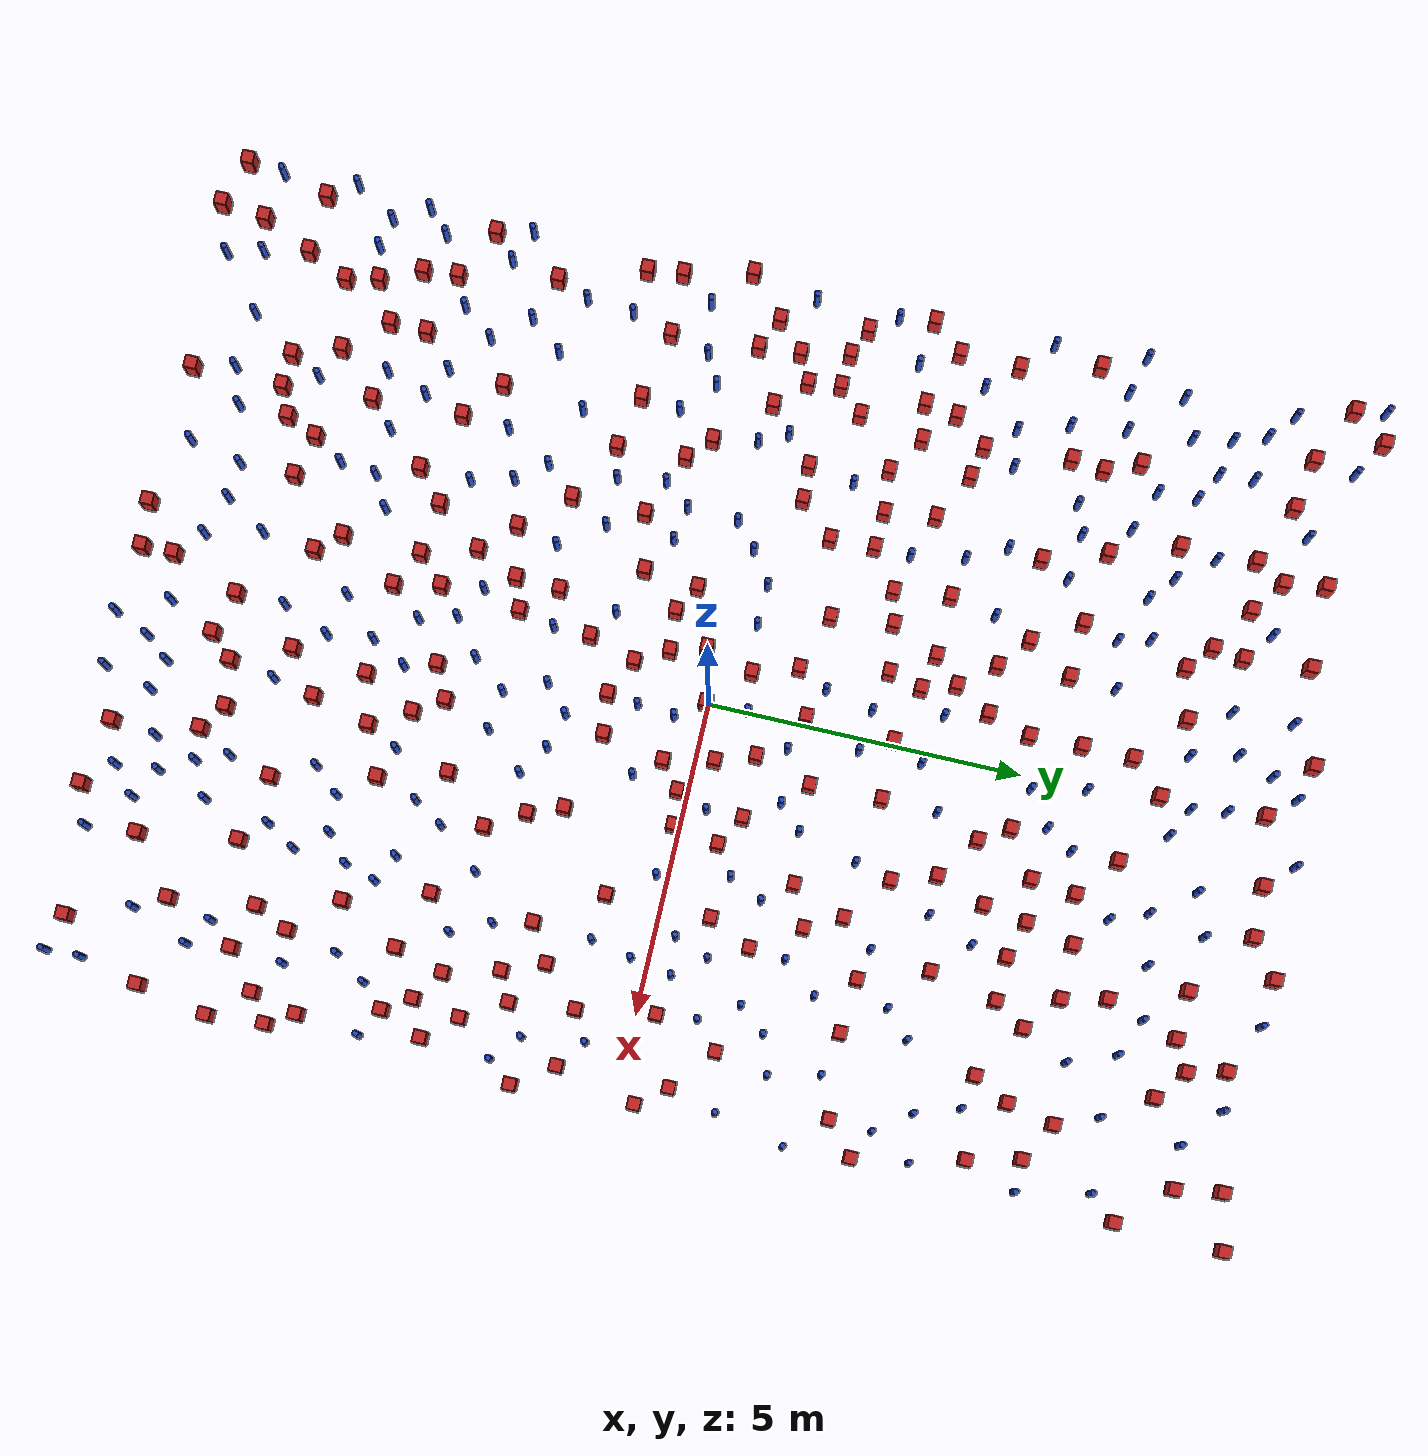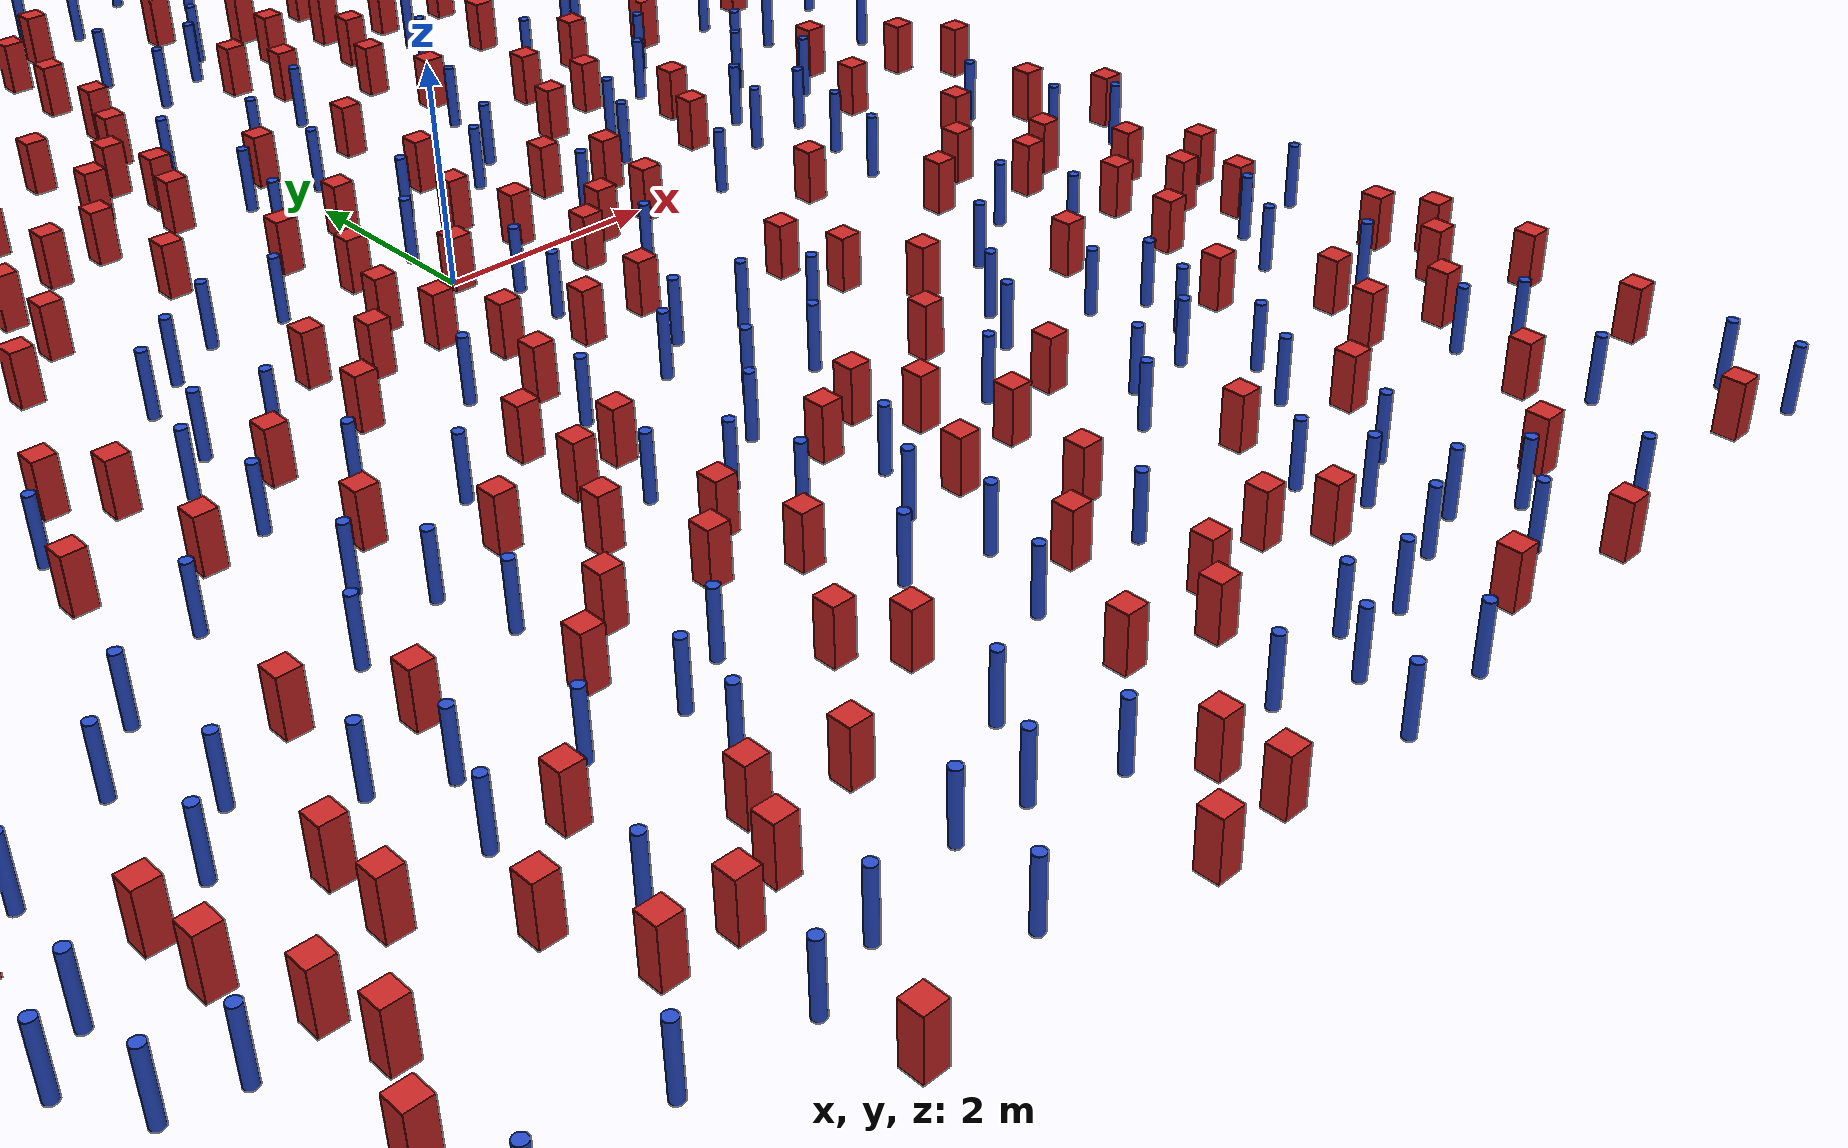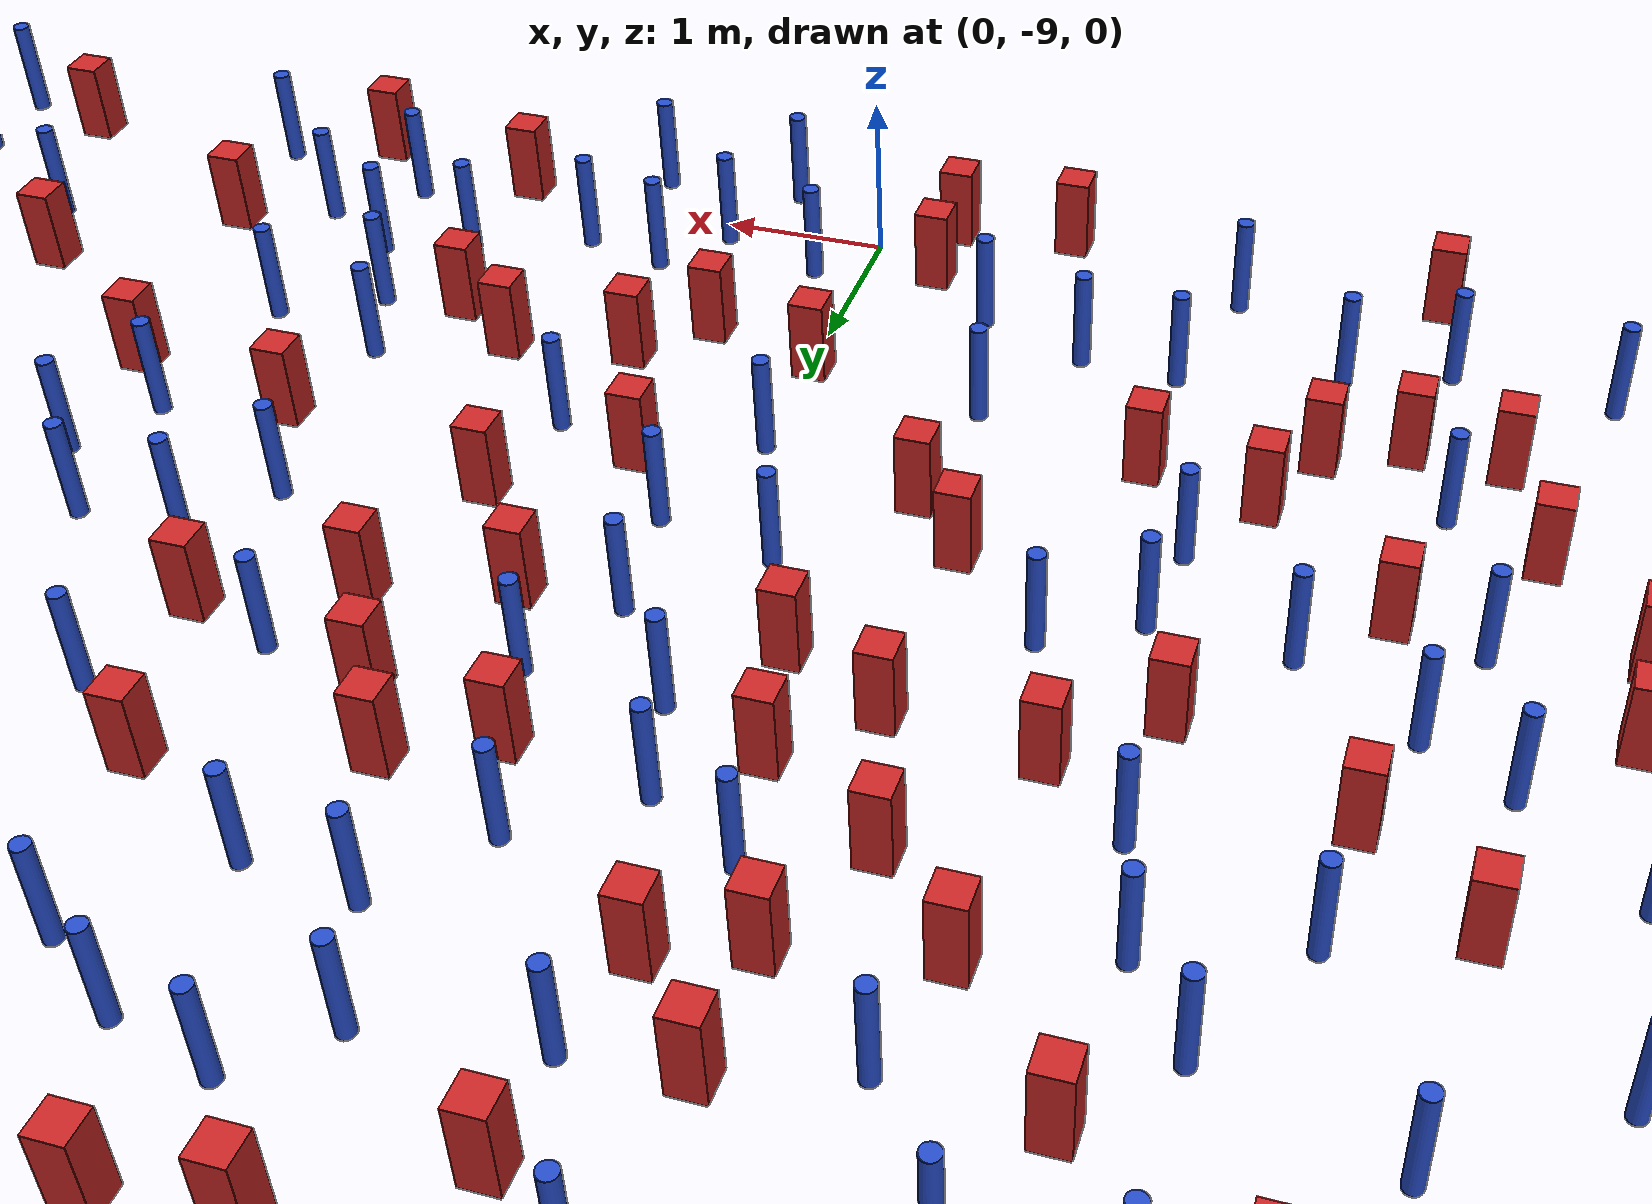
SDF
<sdf version="1.6">
  <model name="dense_29"><model name="square_post_obstacle0">
  <static>true</static>
  <pose frame="">2.69655545007 -2.96752872048 -6.11067671241e-07 -5.50515727128e-06 -8.79689657224e-07 2.37013304536e-05</pose>
  <link name="link">
    <pose frame="">0 0 0.25 0 -0 0</pose>
    <inertial>
      <mass>100</mass>
      <inertia>
        <ixx>0.166667</ixx>
        <ixy>0</ixy>
        <ixz>0</ixz>
        <iyy>0.166667</iyy>
        <iyz>0</iyz>
        <izz>0.166667</izz>
      </inertia>
    </inertial>
    <collision name="collision">
      <geometry>
        <box>
          <size>.2 .2 .5</size>
        </box>
      </geometry>
      <max_contacts>10</max_contacts>
      <surface>
        <contact>
          <ode/>
        </contact>
        <bounce/>
        <friction>
          <torsional>
            <ode/>
          </torsional>
          <ode/>
        </friction>
      </surface>
    </collision>
    <visual name="visual">
      <geometry>
        <box>
          <size>.2 .2 .5</size>
        </box>
      </geometry>
      <material>
        <script>
          <name>Gazebo/Red</name>
          <uri>file://media/materials/scripts/gazebo.material</uri>
        </script>
      </material>
    </visual>
    <self_collide>0</self_collide>
    <kinematic>0</kinematic>
  </link>
</model>
<model name="square_post_obstacle1">
  <static>true</static>
  <pose frame="">0.894384582868 9.0033171066 -6.11067671241e-07 -5.50515727128e-06 -8.79689657224e-07 2.37013304536e-05</pose>
  <link name="link">
    <pose frame="">0 0 0.25 0 -0 0</pose>
    <inertial>
      <mass>100</mass>
      <inertia>
        <ixx>0.166667</ixx>
        <ixy>0</ixy>
        <ixz>0</ixz>
        <iyy>0.166667</iyy>
        <iyz>0</iyz>
        <izz>0.166667</izz>
      </inertia>
    </inertial>
    <collision name="collision">
      <geometry>
        <box>
          <size>.2 .2 .5</size>
        </box>
      </geometry>
      <max_contacts>10</max_contacts>
      <surface>
        <contact>
          <ode/>
        </contact>
        <bounce/>
        <friction>
          <torsional>
            <ode/>
          </torsional>
          <ode/>
        </friction>
      </surface>
    </collision>
    <visual name="visual">
      <geometry>
        <box>
          <size>.2 .2 .5</size>
        </box>
      </geometry>
      <material>
        <script>
          <name>Gazebo/Red</name>
          <uri>file://media/materials/scripts/gazebo.material</uri>
        </script>
      </material>
    </visual>
    <self_collide>0</self_collide>
    <kinematic>0</kinematic>
  </link>
</model>
<model name="pole_obstacle0">
  <static>true</static>
  <pose frame="">3.41426203181 -2.9291953358 -9.47619616065e-06 5.49618799737e-07 2.36310414051e-07 -1.55090534807e-07</pose>
  <link name="link">
  <pose frame="">0 0 0.3 0 -0 0</pose>
    <inertial>
      <mass>1</mass>
      <inertia>
        <ixx>0.145833</ixx>
        <ixy>0</ixy>
        <ixz>0</ixz>
        <iyy>0.145833</iyy>
        <iyz>0</iyz>
        <izz>0.125</izz>
      </inertia>
    </inertial>
    <collision name="collision">
      <geometry>
        <cylinder>
          <radius>0.05</radius>
          <length>.6</length>
        </cylinder>
      </geometry>
      <max_contacts>10</max_contacts>
      <surface>
        <contact>
          <ode/>
        </contact>
        <bounce/>
        <friction>
          <torsional>
            <ode/>
          </torsional>
          <ode/>
        </friction>
      </surface>
    </collision>
    <visual name="visual">
      <geometry>
        <cylinder>
          <radius>0.05</radius>
          <length>.6</length>
        </cylinder>
      </geometry>
      <material>
        <script>
          <name>Gazebo/Blue</name>
          <uri>file://media/materials/scripts/gazebo.material</uri>
        </script>
      </material>
    </visual>
    <self_collide>0</self_collide>
    <kinematic>0</kinematic>
  </link>
</model>
<model name="square_post_obstacle2">
  <static>true</static>
  <pose frame="">-2.72865628768 -2.8582352957 -6.11067671241e-07 -5.50515727128e-06 -8.79689657224e-07 2.37013304536e-05</pose>
  <link name="link">
    <pose frame="">0 0 0.25 0 -0 0</pose>
    <inertial>
      <mass>100</mass>
      <inertia>
        <ixx>0.166667</ixx>
        <ixy>0</ixy>
        <ixz>0</ixz>
        <iyy>0.166667</iyy>
        <iyz>0</iyz>
        <izz>0.166667</izz>
      </inertia>
    </inertial>
    <collision name="collision">
      <geometry>
        <box>
          <size>.2 .2 .5</size>
        </box>
      </geometry>
      <max_contacts>10</max_contacts>
      <surface>
        <contact>
          <ode/>
        </contact>
        <bounce/>
        <friction>
          <torsional>
            <ode/>
          </torsional>
          <ode/>
        </friction>
      </surface>
    </collision>
    <visual name="visual">
      <geometry>
        <box>
          <size>.2 .2 .5</size>
        </box>
      </geometry>
      <material>
        <script>
          <name>Gazebo/Red</name>
          <uri>file://media/materials/scripts/gazebo.material</uri>
        </script>
      </material>
    </visual>
    <self_collide>0</self_collide>
    <kinematic>0</kinematic>
  </link>
</model>
<model name="pole_obstacle1">
  <static>true</static>
  <pose frame="">-5.02907889812 -1.0506375493 -9.47619616065e-06 5.49618799738e-07 2.36310414071e-07 -1.55090534796e-07</pose>
  <link name="link">
  <pose frame="">0 0 0.3 0 -0 0</pose>
    <inertial>
      <mass>1</mass>
      <inertia>
        <ixx>0.145833</ixx>
        <ixy>0</ixy>
        <ixz>0</ixz>
        <iyy>0.145833</iyy>
        <iyz>0</iyz>
        <izz>0.125</izz>
      </inertia>
    </inertial>
    <collision name="collision">
      <geometry>
        <cylinder>
          <radius>0.05</radius>
          <length>.6</length>
        </cylinder>
      </geometry>
      <max_contacts>10</max_contacts>
      <surface>
        <contact>
          <ode/>
        </contact>
        <bounce/>
        <friction>
          <torsional>
            <ode/>
          </torsional>
          <ode/>
        </friction>
      </surface>
    </collision>
    <visual name="visual">
      <geometry>
        <cylinder>
          <radius>0.05</radius>
          <length>.6</length>
        </cylinder>
      </geometry>
      <material>
        <script>
          <name>Gazebo/Blue</name>
          <uri>file://media/materials/scripts/gazebo.material</uri>
        </script>
      </material>
    </visual>
    <self_collide>0</self_collide>
    <kinematic>0</kinematic>
  </link>
</model>
<model name="square_post_obstacle3">
  <static>true</static>
  <pose frame="">4.54777788087 -1.52727950527 -6.11067671241e-07 -5.50515727128e-06 -8.79689657224e-07 2.37013304536e-05</pose>
  <link name="link">
    <pose frame="">0 0 0.25 0 -0 0</pose>
    <inertial>
      <mass>100</mass>
      <inertia>
        <ixx>0.166667</ixx>
        <ixy>0</ixy>
        <ixz>0</ixz>
        <iyy>0.166667</iyy>
        <iyz>0</iyz>
        <izz>0.166667</izz>
      </inertia>
    </inertial>
    <collision name="collision">
      <geometry>
        <box>
          <size>.2 .2 .5</size>
        </box>
      </geometry>
      <max_contacts>10</max_contacts>
      <surface>
        <contact>
          <ode/>
        </contact>
        <bounce/>
        <friction>
          <torsional>
            <ode/>
          </torsional>
          <ode/>
        </friction>
      </surface>
    </collision>
    <visual name="visual">
      <geometry>
        <box>
          <size>.2 .2 .5</size>
        </box>
      </geometry>
      <material>
        <script>
          <name>Gazebo/Red</name>
          <uri>file://media/materials/scripts/gazebo.material</uri>
        </script>
      </material>
    </visual>
    <self_collide>0</self_collide>
    <kinematic>0</kinematic>
  </link>
</model>
<model name="pole_obstacle2">
  <static>true</static>
  <pose frame="">0.753142357404 5.56163420365 -9.47619616065e-06 5.49618799737e-07 2.36310414065e-07 -1.55090534796e-07</pose>
  <link name="link">
  <pose frame="">0 0 0.3 0 -0 0</pose>
    <inertial>
      <mass>1</mass>
      <inertia>
        <ixx>0.145833</ixx>
        <ixy>0</ixy>
        <ixz>0</ixz>
        <iyy>0.145833</iyy>
        <iyz>0</iyz>
        <izz>0.125</izz>
      </inertia>
    </inertial>
    <collision name="collision">
      <geometry>
        <cylinder>
          <radius>0.05</radius>
          <length>.6</length>
        </cylinder>
      </geometry>
      <max_contacts>10</max_contacts>
      <surface>
        <contact>
          <ode/>
        </contact>
        <bounce/>
        <friction>
          <torsional>
            <ode/>
          </torsional>
          <ode/>
        </friction>
      </surface>
    </collision>
    <visual name="visual">
      <geometry>
        <cylinder>
          <radius>0.05</radius>
          <length>.6</length>
        </cylinder>
      </geometry>
      <material>
        <script>
          <name>Gazebo/Blue</name>
          <uri>file://media/materials/scripts/gazebo.material</uri>
        </script>
      </material>
    </visual>
    <self_collide>0</self_collide>
    <kinematic>0</kinematic>
  </link>
</model>
<model name="pole_obstacle3">
  <static>true</static>
  <pose frame="">3.68952256595 -5.76837566407 -9.47619616065e-06 5.49618799738e-07 2.3631041406e-07 -1.55090534801e-07</pose>
  <link name="link">
  <pose frame="">0 0 0.3 0 -0 0</pose>
    <inertial>
      <mass>1</mass>
      <inertia>
        <ixx>0.145833</ixx>
        <ixy>0</ixy>
        <ixz>0</ixz>
        <iyy>0.145833</iyy>
        <iyz>0</iyz>
        <izz>0.125</izz>
      </inertia>
    </inertial>
    <collision name="collision">
      <geometry>
        <cylinder>
          <radius>0.05</radius>
          <length>.6</length>
        </cylinder>
      </geometry>
      <max_contacts>10</max_contacts>
      <surface>
        <contact>
          <ode/>
        </contact>
        <bounce/>
        <friction>
          <torsional>
            <ode/>
          </torsional>
          <ode/>
        </friction>
      </surface>
    </collision>
    <visual name="visual">
      <geometry>
        <cylinder>
          <radius>0.05</radius>
          <length>.6</length>
        </cylinder>
      </geometry>
      <material>
        <script>
          <name>Gazebo/Blue</name>
          <uri>file://media/materials/scripts/gazebo.material</uri>
        </script>
      </material>
    </visual>
    <self_collide>0</self_collide>
    <kinematic>0</kinematic>
  </link>
</model>
<model name="square_post_obstacle4">
  <static>true</static>
  <pose frame="">-3.76172008003 -1.25565885905 -6.11067671241e-07 -5.50515727128e-06 -8.79689657224e-07 2.37013304536e-05</pose>
  <link name="link">
    <pose frame="">0 0 0.25 0 -0 0</pose>
    <inertial>
      <mass>100</mass>
      <inertia>
        <ixx>0.166667</ixx>
        <ixy>0</ixy>
        <ixz>0</ixz>
        <iyy>0.166667</iyy>
        <iyz>0</iyz>
        <izz>0.166667</izz>
      </inertia>
    </inertial>
    <collision name="collision">
      <geometry>
        <box>
          <size>.2 .2 .5</size>
        </box>
      </geometry>
      <max_contacts>10</max_contacts>
      <surface>
        <contact>
          <ode/>
        </contact>
        <bounce/>
        <friction>
          <torsional>
            <ode/>
          </torsional>
          <ode/>
        </friction>
      </surface>
    </collision>
    <visual name="visual">
      <geometry>
        <box>
          <size>.2 .2 .5</size>
        </box>
      </geometry>
      <material>
        <script>
          <name>Gazebo/Red</name>
          <uri>file://media/materials/scripts/gazebo.material</uri>
        </script>
      </material>
    </visual>
    <self_collide>0</self_collide>
    <kinematic>0</kinematic>
  </link>
</model>
<model name="square_post_obstacle5">
  <static>true</static>
  <pose frame="">5.80305898445 -3.83086714012 -6.11067671241e-07 -5.50515727128e-06 -8.79689657224e-07 2.37013304536e-05</pose>
  <link name="link">
    <pose frame="">0 0 0.25 0 -0 0</pose>
    <inertial>
      <mass>100</mass>
      <inertia>
        <ixx>0.166667</ixx>
        <ixy>0</ixy>
        <ixz>0</ixz>
        <iyy>0.166667</iyy>
        <iyz>0</iyz>
        <izz>0.166667</izz>
      </inertia>
    </inertial>
    <collision name="collision">
      <geometry>
        <box>
          <size>.2 .2 .5</size>
        </box>
      </geometry>
      <max_contacts>10</max_contacts>
      <surface>
        <contact>
          <ode/>
        </contact>
        <bounce/>
        <friction>
          <torsional>
            <ode/>
          </torsional>
          <ode/>
        </friction>
      </surface>
    </collision>
    <visual name="visual">
      <geometry>
        <box>
          <size>.2 .2 .5</size>
        </box>
      </geometry>
      <material>
        <script>
          <name>Gazebo/Red</name>
          <uri>file://media/materials/scripts/gazebo.material</uri>
        </script>
      </material>
    </visual>
    <self_collide>0</self_collide>
    <kinematic>0</kinematic>
  </link>
</model>
<model name="square_post_obstacle6">
  <static>true</static>
  <pose frame="">5.25804633106 -1.95155179132 -6.11067671241e-07 -5.50515727128e-06 -8.79689657224e-07 2.37013304536e-05</pose>
  <link name="link">
    <pose frame="">0 0 0.25 0 -0 0</pose>
    <inertial>
      <mass>100</mass>
      <inertia>
        <ixx>0.166667</ixx>
        <ixy>0</ixy>
        <ixz>0</ixz>
        <iyy>0.166667</iyy>
        <iyz>0</iyz>
        <izz>0.166667</izz>
      </inertia>
    </inertial>
    <collision name="collision">
      <geometry>
        <box>
          <size>.2 .2 .5</size>
        </box>
      </geometry>
      <max_contacts>10</max_contacts>
      <surface>
        <contact>
          <ode/>
        </contact>
        <bounce/>
        <friction>
          <torsional>
            <ode/>
          </torsional>
          <ode/>
        </friction>
      </surface>
    </collision>
    <visual name="visual">
      <geometry>
        <box>
          <size>.2 .2 .5</size>
        </box>
      </geometry>
      <material>
        <script>
          <name>Gazebo/Red</name>
          <uri>file://media/materials/scripts/gazebo.material</uri>
        </script>
      </material>
    </visual>
    <self_collide>0</self_collide>
    <kinematic>0</kinematic>
  </link>
</model>
<model name="pole_obstacle4">
  <static>true</static>
  <pose frame="">2.72592543453 -5.32273102294 -9.47619616065e-06 5.49618799738e-07 2.3631041406e-07 -1.55090534801e-07</pose>
  <link name="link">
  <pose frame="">0 0 0.3 0 -0 0</pose>
    <inertial>
      <mass>1</mass>
      <inertia>
        <ixx>0.145833</ixx>
        <ixy>0</ixy>
        <ixz>0</ixz>
        <iyy>0.145833</iyy>
        <iyz>0</iyz>
        <izz>0.125</izz>
      </inertia>
    </inertial>
    <collision name="collision">
      <geometry>
        <cylinder>
          <radius>0.05</radius>
          <length>.6</length>
        </cylinder>
      </geometry>
      <max_contacts>10</max_contacts>
      <surface>
        <contact>
          <ode/>
        </contact>
        <bounce/>
        <friction>
          <torsional>
            <ode/>
          </torsional>
          <ode/>
        </friction>
      </surface>
    </collision>
    <visual name="visual">
      <geometry>
        <cylinder>
          <radius>0.05</radius>
          <length>.6</length>
        </cylinder>
      </geometry>
      <material>
        <script>
          <name>Gazebo/Blue</name>
          <uri>file://media/materials/scripts/gazebo.material</uri>
        </script>
      </material>
    </visual>
    <self_collide>0</self_collide>
    <kinematic>0</kinematic>
  </link>
</model>
<model name="pole_obstacle5">
  <static>true</static>
  <pose frame="">2.79837274544 4.79413468855 -9.47619616065e-06 5.49618799738e-07 2.3631041406e-07 -1.55090534801e-07</pose>
  <link name="link">
  <pose frame="">0 0 0.3 0 -0 0</pose>
    <inertial>
      <mass>1</mass>
      <inertia>
        <ixx>0.145833</ixx>
        <ixy>0</ixy>
        <ixz>0</ixz>
        <iyy>0.145833</iyy>
        <iyz>0</iyz>
        <izz>0.125</izz>
      </inertia>
    </inertial>
    <collision name="collision">
      <geometry>
        <cylinder>
          <radius>0.05</radius>
          <length>.6</length>
        </cylinder>
      </geometry>
      <max_contacts>10</max_contacts>
      <surface>
        <contact>
          <ode/>
        </contact>
        <bounce/>
        <friction>
          <torsional>
            <ode/>
          </torsional>
          <ode/>
        </friction>
      </surface>
    </collision>
    <visual name="visual">
      <geometry>
        <cylinder>
          <radius>0.05</radius>
          <length>.6</length>
        </cylinder>
      </geometry>
      <material>
        <script>
          <name>Gazebo/Blue</name>
          <uri>file://media/materials/scripts/gazebo.material</uri>
        </script>
      </material>
    </visual>
    <self_collide>0</self_collide>
    <kinematic>0</kinematic>
  </link>
</model>
<model name="square_post_obstacle7">
  <static>true</static>
  <pose frame="">4.74108814774 5.26752982219 -6.11067671241e-07 -5.50515727128e-06 -8.79689657224e-07 2.37013304536e-05</pose>
  <link name="link">
    <pose frame="">0 0 0.25 0 -0 0</pose>
    <inertial>
      <mass>100</mass>
      <inertia>
        <ixx>0.166667</ixx>
        <ixy>0</ixy>
        <ixz>0</ixz>
        <iyy>0.166667</iyy>
        <iyz>0</iyz>
        <izz>0.166667</izz>
      </inertia>
    </inertial>
    <collision name="collision">
      <geometry>
        <box>
          <size>.2 .2 .5</size>
        </box>
      </geometry>
      <max_contacts>10</max_contacts>
      <surface>
        <contact>
          <ode/>
        </contact>
        <bounce/>
        <friction>
          <torsional>
            <ode/>
          </torsional>
          <ode/>
        </friction>
      </surface>
    </collision>
    <visual name="visual">
      <geometry>
        <box>
          <size>.2 .2 .5</size>
        </box>
      </geometry>
      <material>
        <script>
          <name>Gazebo/Red</name>
          <uri>file://media/materials/scripts/gazebo.material</uri>
        </script>
      </material>
    </visual>
    <self_collide>0</self_collide>
    <kinematic>0</kinematic>
  </link>
</model>
<model name="square_post_obstacle8">
  <static>true</static>
  <pose frame="">-5.11551019395 8.31496779472 -6.11067671241e-07 -5.50515727128e-06 -8.79689657224e-07 2.37013304536e-05</pose>
  <link name="link">
    <pose frame="">0 0 0.25 0 -0 0</pose>
    <inertial>
      <mass>100</mass>
      <inertia>
        <ixx>0.166667</ixx>
        <ixy>0</ixy>
        <ixz>0</ixz>
        <iyy>0.166667</iyy>
        <iyz>0</iyz>
        <izz>0.166667</izz>
      </inertia>
    </inertial>
    <collision name="collision">
      <geometry>
        <box>
          <size>.2 .2 .5</size>
        </box>
      </geometry>
      <max_contacts>10</max_contacts>
      <surface>
        <contact>
          <ode/>
        </contact>
        <bounce/>
        <friction>
          <torsional>
            <ode/>
          </torsional>
          <ode/>
        </friction>
      </surface>
    </collision>
    <visual name="visual">
      <geometry>
        <box>
          <size>.2 .2 .5</size>
        </box>
      </geometry>
      <material>
        <script>
          <name>Gazebo/Red</name>
          <uri>file://media/materials/scripts/gazebo.material</uri>
        </script>
      </material>
    </visual>
    <self_collide>0</self_collide>
    <kinematic>0</kinematic>
  </link>
</model>
<model name="pole_obstacle6">
  <static>true</static>
  <pose frame="">-0.0224886271966 -6.85687499637 -9.47619616065e-06 5.49618799737e-07 2.36310414067e-07 -1.55090534797e-07</pose>
  <link name="link">
  <pose frame="">0 0 0.3 0 -0 0</pose>
    <inertial>
      <mass>1</mass>
      <inertia>
        <ixx>0.145833</ixx>
        <ixy>0</ixy>
        <ixz>0</ixz>
        <iyy>0.145833</iyy>
        <iyz>0</iyz>
        <izz>0.125</izz>
      </inertia>
    </inertial>
    <collision name="collision">
      <geometry>
        <cylinder>
          <radius>0.05</radius>
          <length>.6</length>
        </cylinder>
      </geometry>
      <max_contacts>10</max_contacts>
      <surface>
        <contact>
          <ode/>
        </contact>
        <bounce/>
        <friction>
          <torsional>
            <ode/>
          </torsional>
          <ode/>
        </friction>
      </surface>
    </collision>
    <visual name="visual">
      <geometry>
        <cylinder>
          <radius>0.05</radius>
          <length>.6</length>
        </cylinder>
      </geometry>
      <material>
        <script>
          <name>Gazebo/Blue</name>
          <uri>file://media/materials/scripts/gazebo.material</uri>
        </script>
      </material>
    </visual>
    <self_collide>0</self_collide>
    <kinematic>0</kinematic>
  </link>
</model>
<model name="pole_obstacle7">
  <static>true</static>
  <pose frame="">-4.14999581618 -3.02715681474 -9.47619616065e-06 5.49618799738e-07 2.36310414051e-07 -1.55090534805e-07</pose>
  <link name="link">
  <pose frame="">0 0 0.3 0 -0 0</pose>
    <inertial>
      <mass>1</mass>
      <inertia>
        <ixx>0.145833</ixx>
        <ixy>0</ixy>
        <ixz>0</ixz>
        <iyy>0.145833</iyy>
        <iyz>0</iyz>
        <izz>0.125</izz>
      </inertia>
    </inertial>
    <collision name="collision">
      <geometry>
        <cylinder>
          <radius>0.05</radius>
          <length>.6</length>
        </cylinder>
      </geometry>
      <max_contacts>10</max_contacts>
      <surface>
        <contact>
          <ode/>
        </contact>
        <bounce/>
        <friction>
          <torsional>
            <ode/>
          </torsional>
          <ode/>
        </friction>
      </surface>
    </collision>
    <visual name="visual">
      <geometry>
        <cylinder>
          <radius>0.05</radius>
          <length>.6</length>
        </cylinder>
      </geometry>
      <material>
        <script>
          <name>Gazebo/Blue</name>
          <uri>file://media/materials/scripts/gazebo.material</uri>
        </script>
      </material>
    </visual>
    <self_collide>0</self_collide>
    <kinematic>0</kinematic>
  </link>
</model>
<model name="square_post_obstacle9">
  <static>true</static>
  <pose frame="">-5.68394783283 -1.94065890462 -6.11067671241e-07 -5.50515727128e-06 -8.79689657224e-07 2.37013304536e-05</pose>
  <link name="link">
    <pose frame="">0 0 0.25 0 -0 0</pose>
    <inertial>
      <mass>100</mass>
      <inertia>
        <ixx>0.166667</ixx>
        <ixy>0</ixy>
        <ixz>0</ixz>
        <iyy>0.166667</iyy>
        <iyz>0</iyz>
        <izz>0.166667</izz>
      </inertia>
    </inertial>
    <collision name="collision">
      <geometry>
        <box>
          <size>.2 .2 .5</size>
        </box>
      </geometry>
      <max_contacts>10</max_contacts>
      <surface>
        <contact>
          <ode/>
        </contact>
        <bounce/>
        <friction>
          <torsional>
            <ode/>
          </torsional>
          <ode/>
        </friction>
      </surface>
    </collision>
    <visual name="visual">
      <geometry>
        <box>
          <size>.2 .2 .5</size>
        </box>
      </geometry>
      <material>
        <script>
          <name>Gazebo/Red</name>
          <uri>file://media/materials/scripts/gazebo.material</uri>
        </script>
      </material>
    </visual>
    <self_collide>0</self_collide>
    <kinematic>0</kinematic>
  </link>
</model>
<model name="square_post_obstacle10">
  <static>true</static>
  <pose frame="">0.886683040819 2.95158349716 -6.11067671241e-07 -5.50515727128e-06 -8.79689657224e-07 2.37013304536e-05</pose>
  <link name="link">
    <pose frame="">0 0 0.25 0 -0 0</pose>
    <inertial>
      <mass>100</mass>
      <inertia>
        <ixx>0.166667</ixx>
        <ixy>0</ixy>
        <ixz>0</ixz>
        <iyy>0.166667</iyy>
        <iyz>0</iyz>
        <izz>0.166667</izz>
      </inertia>
    </inertial>
    <collision name="collision">
      <geometry>
        <box>
          <size>.2 .2 .5</size>
        </box>
      </geometry>
      <max_contacts>10</max_contacts>
      <surface>
        <contact>
          <ode/>
        </contact>
        <bounce/>
        <friction>
          <torsional>
            <ode/>
          </torsional>
          <ode/>
        </friction>
      </surface>
    </collision>
    <visual name="visual">
      <geometry>
        <box>
          <size>.2 .2 .5</size>
        </box>
      </geometry>
      <material>
        <script>
          <name>Gazebo/Red</name>
          <uri>file://media/materials/scripts/gazebo.material</uri>
        </script>
      </material>
    </visual>
    <self_collide>0</self_collide>
    <kinematic>0</kinematic>
  </link>
</model>
<model name="square_post_obstacle11">
  <static>true</static>
  <pose frame="">5.52812265064 -3.40061100527 -6.11067671241e-07 -5.50515727128e-06 -8.79689657224e-07 2.37013304536e-05</pose>
  <link name="link">
    <pose frame="">0 0 0.25 0 -0 0</pose>
    <inertial>
      <mass>100</mass>
      <inertia>
        <ixx>0.166667</ixx>
        <ixy>0</ixy>
        <ixz>0</ixz>
        <iyy>0.166667</iyy>
        <iyz>0</iyz>
        <izz>0.166667</izz>
      </inertia>
    </inertial>
    <collision name="collision">
      <geometry>
        <box>
          <size>.2 .2 .5</size>
        </box>
      </geometry>
      <max_contacts>10</max_contacts>
      <surface>
        <contact>
          <ode/>
        </contact>
        <bounce/>
        <friction>
          <torsional>
            <ode/>
          </torsional>
          <ode/>
        </friction>
      </surface>
    </collision>
    <visual name="visual">
      <geometry>
        <box>
          <size>.2 .2 .5</size>
        </box>
      </geometry>
      <material>
        <script>
          <name>Gazebo/Red</name>
          <uri>file://media/materials/scripts/gazebo.material</uri>
        </script>
      </material>
    </visual>
    <self_collide>0</self_collide>
    <kinematic>0</kinematic>
  </link>
</model>
<model name="square_post_obstacle12">
  <static>true</static>
  <pose frame="">-4.13528618343 7.90303611068 -6.11067671241e-07 -5.50515727128e-06 -8.79689657224e-07 2.37013304536e-05</pose>
  <link name="link">
    <pose frame="">0 0 0.25 0 -0 0</pose>
    <inertial>
      <mass>100</mass>
      <inertia>
        <ixx>0.166667</ixx>
        <ixy>0</ixy>
        <ixz>0</ixz>
        <iyy>0.166667</iyy>
        <iyz>0</iyz>
        <izz>0.166667</izz>
      </inertia>
    </inertial>
    <collision name="collision">
      <geometry>
        <box>
          <size>.2 .2 .5</size>
        </box>
      </geometry>
      <max_contacts>10</max_contacts>
      <surface>
        <contact>
          <ode/>
        </contact>
        <bounce/>
        <friction>
          <torsional>
            <ode/>
          </torsional>
          <ode/>
        </friction>
      </surface>
    </collision>
    <visual name="visual">
      <geometry>
        <box>
          <size>.2 .2 .5</size>
        </box>
      </geometry>
      <material>
        <script>
          <name>Gazebo/Red</name>
          <uri>file://media/materials/scripts/gazebo.material</uri>
        </script>
      </material>
    </visual>
    <self_collide>0</self_collide>
    <kinematic>0</kinematic>
  </link>
</model>
<model name="square_post_obstacle13">
  <static>true</static>
  <pose frame="">-1.15080311443 -9.35945894737 -6.11067671241e-07 -5.50515727128e-06 -8.79689657224e-07 2.37013304536e-05</pose>
  <link name="link">
    <pose frame="">0 0 0.25 0 -0 0</pose>
    <inertial>
      <mass>100</mass>
      <inertia>
        <ixx>0.166667</ixx>
        <ixy>0</ixy>
        <ixz>0</ixz>
        <iyy>0.166667</iyy>
        <iyz>0</iyz>
        <izz>0.166667</izz>
      </inertia>
    </inertial>
    <collision name="collision">
      <geometry>
        <box>
          <size>.2 .2 .5</size>
        </box>
      </geometry>
      <max_contacts>10</max_contacts>
      <surface>
        <contact>
          <ode/>
        </contact>
        <bounce/>
        <friction>
          <torsional>
            <ode/>
          </torsional>
          <ode/>
        </friction>
      </surface>
    </collision>
    <visual name="visual">
      <geometry>
        <box>
          <size>.2 .2 .5</size>
        </box>
      </geometry>
      <material>
        <script>
          <name>Gazebo/Red</name>
          <uri>file://media/materials/scripts/gazebo.material</uri>
        </script>
      </material>
    </visual>
    <self_collide>0</self_collide>
    <kinematic>0</kinematic>
  </link>
</model>
<model name="pole_obstacle8">
  <static>true</static>
  <pose frame="">1.86516818854 8.27043241651 -9.47619616065e-06 5.49618799737e-07 2.36310414046e-07 -1.55090534809e-07</pose>
  <link name="link">
  <pose frame="">0 0 0.3 0 -0 0</pose>
    <inertial>
      <mass>1</mass>
      <inertia>
        <ixx>0.145833</ixx>
        <ixy>0</ixy>
        <ixz>0</ixz>
        <iyy>0.145833</iyy>
        <iyz>0</iyz>
        <izz>0.125</izz>
      </inertia>
    </inertial>
    <collision name="collision">
      <geometry>
        <cylinder>
          <radius>0.05</radius>
          <length>.6</length>
        </cylinder>
      </geometry>
      <max_contacts>10</max_contacts>
      <surface>
        <contact>
          <ode/>
        </contact>
        <bounce/>
        <friction>
          <torsional>
            <ode/>
          </torsional>
          <ode/>
        </friction>
      </surface>
    </collision>
    <visual name="visual">
      <geometry>
        <cylinder>
          <radius>0.05</radius>
          <length>.6</length>
        </cylinder>
      </geometry>
      <material>
        <script>
          <name>Gazebo/Blue</name>
          <uri>file://media/materials/scripts/gazebo.material</uri>
        </script>
      </material>
    </visual>
    <self_collide>0</self_collide>
    <kinematic>0</kinematic>
  </link>
</model>
<model name="square_post_obstacle14">
  <static>true</static>
  <pose frame="">1.53295186414 -5.11848974864 -6.11067671241e-07 -5.50515727128e-06 -8.79689657224e-07 2.37013304536e-05</pose>
  <link name="link">
    <pose frame="">0 0 0.25 0 -0 0</pose>
    <inertial>
      <mass>100</mass>
      <inertia>
        <ixx>0.166667</ixx>
        <ixy>0</ixy>
        <ixz>0</ixz>
        <iyy>0.166667</iyy>
        <iyz>0</iyz>
        <izz>0.166667</izz>
      </inertia>
    </inertial>
    <collision name="collision">
      <geometry>
        <box>
          <size>.2 .2 .5</size>
        </box>
      </geometry>
      <max_contacts>10</max_contacts>
      <surface>
        <contact>
          <ode/>
        </contact>
        <bounce/>
        <friction>
          <torsional>
            <ode/>
          </torsional>
          <ode/>
        </friction>
      </surface>
    </collision>
    <visual name="visual">
      <geometry>
        <box>
          <size>.2 .2 .5</size>
        </box>
      </geometry>
      <material>
        <script>
          <name>Gazebo/Red</name>
          <uri>file://media/materials/scripts/gazebo.material</uri>
        </script>
      </material>
    </visual>
    <self_collide>0</self_collide>
    <kinematic>0</kinematic>
  </link>
</model>
<model name="square_post_obstacle15">
  <static>true</static>
  <pose frame="">-4.85752129993 -6.35627862861 -6.11067671241e-07 -5.50515727128e-06 -8.79689657224e-07 2.37013304536e-05</pose>
  <link name="link">
    <pose frame="">0 0 0.25 0 -0 0</pose>
    <inertial>
      <mass>100</mass>
      <inertia>
        <ixx>0.166667</ixx>
        <ixy>0</ixy>
        <ixz>0</ixz>
        <iyy>0.166667</iyy>
        <iyz>0</iyz>
        <izz>0.166667</izz>
      </inertia>
    </inertial>
    <collision name="collision">
      <geometry>
        <box>
          <size>.2 .2 .5</size>
        </box>
      </geometry>
      <max_contacts>10</max_contacts>
      <surface>
        <contact>
          <ode/>
        </contact>
        <bounce/>
        <friction>
          <torsional>
            <ode/>
          </torsional>
          <ode/>
        </friction>
      </surface>
    </collision>
    <visual name="visual">
      <geometry>
        <box>
          <size>.2 .2 .5</size>
        </box>
      </geometry>
      <material>
        <script>
          <name>Gazebo/Red</name>
          <uri>file://media/materials/scripts/gazebo.material</uri>
        </script>
      </material>
    </visual>
    <self_collide>0</self_collide>
    <kinematic>0</kinematic>
  </link>
</model>
<model name="square_post_obstacle16">
  <static>true</static>
  <pose frame="">3.88686562413 -3.51782488606 -6.11067671241e-07 -5.50515727128e-06 -8.79689657224e-07 2.37013304536e-05</pose>
  <link name="link">
    <pose frame="">0 0 0.25 0 -0 0</pose>
    <inertial>
      <mass>100</mass>
      <inertia>
        <ixx>0.166667</ixx>
        <ixy>0</ixy>
        <ixz>0</ixz>
        <iyy>0.166667</iyy>
        <iyz>0</iyz>
        <izz>0.166667</izz>
      </inertia>
    </inertial>
    <collision name="collision">
      <geometry>
        <box>
          <size>.2 .2 .5</size>
        </box>
      </geometry>
      <max_contacts>10</max_contacts>
      <surface>
        <contact>
          <ode/>
        </contact>
        <bounce/>
        <friction>
          <torsional>
            <ode/>
          </torsional>
          <ode/>
        </friction>
      </surface>
    </collision>
    <visual name="visual">
      <geometry>
        <box>
          <size>.2 .2 .5</size>
        </box>
      </geometry>
      <material>
        <script>
          <name>Gazebo/Red</name>
          <uri>file://media/materials/scripts/gazebo.material</uri>
        </script>
      </material>
    </visual>
    <self_collide>0</self_collide>
    <kinematic>0</kinematic>
  </link>
</model>
<model name="pole_obstacle9">
  <static>true</static>
  <pose frame="">-1.71116618403 8.97383603554 -9.47619616065e-06 5.49618799737e-07 2.36310414046e-07 -1.55090534809e-07</pose>
  <link name="link">
  <pose frame="">0 0 0.3 0 -0 0</pose>
    <inertial>
      <mass>1</mass>
      <inertia>
        <ixx>0.145833</ixx>
        <ixy>0</ixy>
        <ixz>0</ixz>
        <iyy>0.145833</iyy>
        <iyz>0</iyz>
        <izz>0.125</izz>
      </inertia>
    </inertial>
    <collision name="collision">
      <geometry>
        <cylinder>
          <radius>0.05</radius>
          <length>.6</length>
        </cylinder>
      </geometry>
      <max_contacts>10</max_contacts>
      <surface>
        <contact>
          <ode/>
        </contact>
        <bounce/>
        <friction>
          <torsional>
            <ode/>
          </torsional>
          <ode/>
        </friction>
      </surface>
    </collision>
    <visual name="visual">
      <geometry>
        <cylinder>
          <radius>0.05</radius>
          <length>.6</length>
        </cylinder>
      </geometry>
      <material>
        <script>
          <name>Gazebo/Blue</name>
          <uri>file://media/materials/scripts/gazebo.material</uri>
        </script>
      </material>
    </visual>
    <self_collide>0</self_collide>
    <kinematic>0</kinematic>
  </link>
</model>
<model name="square_post_obstacle17">
  <static>true</static>
  <pose frame="">6.01914977429 5.394370499 -6.11067671241e-07 -5.50515727128e-06 -8.79689657224e-07 2.37013304536e-05</pose>
  <link name="link">
    <pose frame="">0 0 0.25 0 -0 0</pose>
    <inertial>
      <mass>100</mass>
      <inertia>
        <ixx>0.166667</ixx>
        <ixy>0</ixy>
        <ixz>0</ixz>
        <iyy>0.166667</iyy>
        <iyz>0</iyz>
        <izz>0.166667</izz>
      </inertia>
    </inertial>
    <collision name="collision">
      <geometry>
        <box>
          <size>.2 .2 .5</size>
        </box>
      </geometry>
      <max_contacts>10</max_contacts>
      <surface>
        <contact>
          <ode/>
        </contact>
        <bounce/>
        <friction>
          <torsional>
            <ode/>
          </torsional>
          <ode/>
        </friction>
      </surface>
    </collision>
    <visual name="visual">
      <geometry>
        <box>
          <size>.2 .2 .5</size>
        </box>
      </geometry>
      <material>
        <script>
          <name>Gazebo/Red</name>
          <uri>file://media/materials/scripts/gazebo.material</uri>
        </script>
      </material>
    </visual>
    <self_collide>0</self_collide>
    <kinematic>0</kinematic>
  </link>
</model>
<model name="square_post_obstacle18">
  <static>true</static>
  <pose frame="">-1.40789826771 7.34140972793 -6.11067671241e-07 -5.50515727128e-06 -8.79689657224e-07 2.37013304536e-05</pose>
  <link name="link">
    <pose frame="">0 0 0.25 0 -0 0</pose>
    <inertial>
      <mass>100</mass>
      <inertia>
        <ixx>0.166667</ixx>
        <ixy>0</ixy>
        <ixz>0</ixz>
        <iyy>0.166667</iyy>
        <iyz>0</iyz>
        <izz>0.166667</izz>
      </inertia>
    </inertial>
    <collision name="collision">
      <geometry>
        <box>
          <size>.2 .2 .5</size>
        </box>
      </geometry>
      <max_contacts>10</max_contacts>
      <surface>
        <contact>
          <ode/>
        </contact>
        <bounce/>
        <friction>
          <torsional>
            <ode/>
          </torsional>
          <ode/>
        </friction>
      </surface>
    </collision>
    <visual name="visual">
      <geometry>
        <box>
          <size>.2 .2 .5</size>
        </box>
      </geometry>
      <material>
        <script>
          <name>Gazebo/Red</name>
          <uri>file://media/materials/scripts/gazebo.material</uri>
        </script>
      </material>
    </visual>
    <self_collide>0</self_collide>
    <kinematic>0</kinematic>
  </link>
</model>
<model name="pole_obstacle10">
  <static>true</static>
  <pose frame="">-6.5843468768 8.05135579155 -9.47619616065e-06 5.49618799737e-07 2.36310414065e-07 -1.55090534796e-07</pose>
  <link name="link">
  <pose frame="">0 0 0.3 0 -0 0</pose>
    <inertial>
      <mass>1</mass>
      <inertia>
        <ixx>0.145833</ixx>
        <ixy>0</ixy>
        <ixz>0</ixz>
        <iyy>0.145833</iyy>
        <iyz>0</iyz>
        <izz>0.125</izz>
      </inertia>
    </inertial>
    <collision name="collision">
      <geometry>
        <cylinder>
          <radius>0.05</radius>
          <length>.6</length>
        </cylinder>
      </geometry>
      <max_contacts>10</max_contacts>
      <surface>
        <contact>
          <ode/>
        </contact>
        <bounce/>
        <friction>
          <torsional>
            <ode/>
          </torsional>
          <ode/>
        </friction>
      </surface>
    </collision>
    <visual name="visual">
      <geometry>
        <cylinder>
          <radius>0.05</radius>
          <length>.6</length>
        </cylinder>
      </geometry>
      <material>
        <script>
          <name>Gazebo/Blue</name>
          <uri>file://media/materials/scripts/gazebo.material</uri>
        </script>
      </material>
    </visual>
    <self_collide>0</self_collide>
    <kinematic>0</kinematic>
  </link>
</model>
<model name="square_post_obstacle19">
  <static>true</static>
  <pose frame="">-1.52579116777 3.30003734755 -6.11067671241e-07 -5.50515727128e-06 -8.79689657224e-07 2.37013304536e-05</pose>
  <link name="link">
    <pose frame="">0 0 0.25 0 -0 0</pose>
    <inertial>
      <mass>100</mass>
      <inertia>
        <ixx>0.166667</ixx>
        <ixy>0</ixy>
        <ixz>0</ixz>
        <iyy>0.166667</iyy>
        <iyz>0</iyz>
        <izz>0.166667</izz>
      </inertia>
    </inertial>
    <collision name="collision">
      <geometry>
        <box>
          <size>.2 .2 .5</size>
        </box>
      </geometry>
      <max_contacts>10</max_contacts>
      <surface>
        <contact>
          <ode/>
        </contact>
        <bounce/>
        <friction>
          <torsional>
            <ode/>
          </torsional>
          <ode/>
        </friction>
      </surface>
    </collision>
    <visual name="visual">
      <geometry>
        <box>
          <size>.2 .2 .5</size>
        </box>
      </geometry>
      <material>
        <script>
          <name>Gazebo/Red</name>
          <uri>file://media/materials/scripts/gazebo.material</uri>
        </script>
      </material>
    </visual>
    <self_collide>0</self_collide>
    <kinematic>0</kinematic>
  </link>
</model>
<model name="pole_obstacle11">
  <static>true</static>
  <pose frame="">4.92978391876 7.26222886817 -9.47619616065e-06 5.49618799737e-07 2.36310414037e-07 -1.55090534814e-07</pose>
  <link name="link">
  <pose frame="">0 0 0.3 0 -0 0</pose>
    <inertial>
      <mass>1</mass>
      <inertia>
        <ixx>0.145833</ixx>
        <ixy>0</ixy>
        <ixz>0</ixz>
        <iyy>0.145833</iyy>
        <iyz>0</iyz>
        <izz>0.125</izz>
      </inertia>
    </inertial>
    <collision name="collision">
      <geometry>
        <cylinder>
          <radius>0.05</radius>
          <length>.6</length>
        </cylinder>
      </geometry>
      <max_contacts>10</max_contacts>
      <surface>
        <contact>
          <ode/>
        </contact>
        <bounce/>
        <friction>
          <torsional>
            <ode/>
          </torsional>
          <ode/>
        </friction>
      </surface>
    </collision>
    <visual name="visual">
      <geometry>
        <cylinder>
          <radius>0.05</radius>
          <length>.6</length>
        </cylinder>
      </geometry>
      <material>
        <script>
          <name>Gazebo/Blue</name>
          <uri>file://media/materials/scripts/gazebo.material</uri>
        </script>
      </material>
    </visual>
    <self_collide>0</self_collide>
    <kinematic>0</kinematic>
  </link>
</model>
<model name="square_post_obstacle20">
  <static>true</static>
  <pose frame="">-2.5529282255 8.00452283296 -6.11067671241e-07 -5.50515727128e-06 -8.79689657224e-07 2.37013304536e-05</pose>
  <link name="link">
    <pose frame="">0 0 0.25 0 -0 0</pose>
    <inertial>
      <mass>100</mass>
      <inertia>
        <ixx>0.166667</ixx>
        <ixy>0</ixy>
        <ixz>0</ixz>
        <iyy>0.166667</iyy>
        <iyz>0</iyz>
        <izz>0.166667</izz>
      </inertia>
    </inertial>
    <collision name="collision">
      <geometry>
        <box>
          <size>.2 .2 .5</size>
        </box>
      </geometry>
      <max_contacts>10</max_contacts>
      <surface>
        <contact>
          <ode/>
        </contact>
        <bounce/>
        <friction>
          <torsional>
            <ode/>
          </torsional>
          <ode/>
        </friction>
      </surface>
    </collision>
    <visual name="visual">
      <geometry>
        <box>
          <size>.2 .2 .5</size>
        </box>
      </geometry>
      <material>
        <script>
          <name>Gazebo/Red</name>
          <uri>file://media/materials/scripts/gazebo.material</uri>
        </script>
      </material>
    </visual>
    <self_collide>0</self_collide>
    <kinematic>0</kinematic>
  </link>
</model>
<model name="pole_obstacle12">
  <static>true</static>
  <pose frame="">-6.84113890577 -6.18718154438 -9.47619616065e-06 5.49618799737e-07 2.36310414037e-07 -1.55090534814e-07</pose>
  <link name="link">
  <pose frame="">0 0 0.3 0 -0 0</pose>
    <inertial>
      <mass>1</mass>
      <inertia>
        <ixx>0.145833</ixx>
        <ixy>0</ixy>
        <ixz>0</ixz>
        <iyy>0.145833</iyy>
        <iyz>0</iyz>
        <izz>0.125</izz>
      </inertia>
    </inertial>
    <collision name="collision">
      <geometry>
        <cylinder>
          <radius>0.05</radius>
          <length>.6</length>
        </cylinder>
      </geometry>
      <max_contacts>10</max_contacts>
      <surface>
        <contact>
          <ode/>
        </contact>
        <bounce/>
        <friction>
          <torsional>
            <ode/>
          </torsional>
          <ode/>
        </friction>
      </surface>
    </collision>
    <visual name="visual">
      <geometry>
        <cylinder>
          <radius>0.05</radius>
          <length>.6</length>
        </cylinder>
      </geometry>
      <material>
        <script>
          <name>Gazebo/Blue</name>
          <uri>file://media/materials/scripts/gazebo.material</uri>
        </script>
      </material>
    </visual>
    <self_collide>0</self_collide>
    <kinematic>0</kinematic>
  </link>
</model>
<model name="square_post_obstacle21">
  <static>true</static>
  <pose frame="">-3.70066216727 2.81716564771 -6.11067671241e-07 -5.50515727128e-06 -8.79689657224e-07 2.37013304536e-05</pose>
  <link name="link">
    <pose frame="">0 0 0.25 0 -0 0</pose>
    <inertial>
      <mass>100</mass>
      <inertia>
        <ixx>0.166667</ixx>
        <ixy>0</ixy>
        <ixz>0</ixz>
        <iyy>0.166667</iyy>
        <iyz>0</iyz>
        <izz>0.166667</izz>
      </inertia>
    </inertial>
    <collision name="collision">
      <geometry>
        <box>
          <size>.2 .2 .5</size>
        </box>
      </geometry>
      <max_contacts>10</max_contacts>
      <surface>
        <contact>
          <ode/>
        </contact>
        <bounce/>
        <friction>
          <torsional>
            <ode/>
          </torsional>
          <ode/>
        </friction>
      </surface>
    </collision>
    <visual name="visual">
      <geometry>
        <box>
          <size>.2 .2 .5</size>
        </box>
      </geometry>
      <material>
        <script>
          <name>Gazebo/Red</name>
          <uri>file://media/materials/scripts/gazebo.material</uri>
        </script>
      </material>
    </visual>
    <self_collide>0</self_collide>
    <kinematic>0</kinematic>
  </link>
</model>
<model name="pole_obstacle13">
  <static>true</static>
  <pose frame="">-6.47406908762 -5.83882326875 -9.47619616065e-06 5.49618799737e-07 2.36310414037e-07 -1.55090534814e-07</pose>
  <link name="link">
  <pose frame="">0 0 0.3 0 -0 0</pose>
    <inertial>
      <mass>1</mass>
      <inertia>
        <ixx>0.145833</ixx>
        <ixy>0</ixy>
        <ixz>0</ixz>
        <iyy>0.145833</iyy>
        <iyz>0</iyz>
        <izz>0.125</izz>
      </inertia>
    </inertial>
    <collision name="collision">
      <geometry>
        <cylinder>
          <radius>0.05</radius>
          <length>.6</length>
        </cylinder>
      </geometry>
      <max_contacts>10</max_contacts>
      <surface>
        <contact>
          <ode/>
        </contact>
        <bounce/>
        <friction>
          <torsional>
            <ode/>
          </torsional>
          <ode/>
        </friction>
      </surface>
    </collision>
    <visual name="visual">
      <geometry>
        <cylinder>
          <radius>0.05</radius>
          <length>.6</length>
        </cylinder>
      </geometry>
      <material>
        <script>
          <name>Gazebo/Blue</name>
          <uri>file://media/materials/scripts/gazebo.material</uri>
        </script>
      </material>
    </visual>
    <self_collide>0</self_collide>
    <kinematic>0</kinematic>
  </link>
</model>
<model name="square_post_obstacle22">
  <static>true</static>
  <pose frame="">5.39535060356 -6.3227671218 -6.11067671241e-07 -5.50515727128e-06 -8.79689657224e-07 2.37013304536e-05</pose>
  <link name="link">
    <pose frame="">0 0 0.25 0 -0 0</pose>
    <inertial>
      <mass>100</mass>
      <inertia>
        <ixx>0.166667</ixx>
        <ixy>0</ixy>
        <ixz>0</ixz>
        <iyy>0.166667</iyy>
        <iyz>0</iyz>
        <izz>0.166667</izz>
      </inertia>
    </inertial>
    <collision name="collision">
      <geometry>
        <box>
          <size>.2 .2 .5</size>
        </box>
      </geometry>
      <max_contacts>10</max_contacts>
      <surface>
        <contact>
          <ode/>
        </contact>
        <bounce/>
        <friction>
          <torsional>
            <ode/>
          </torsional>
          <ode/>
        </friction>
      </surface>
    </collision>
    <visual name="visual">
      <geometry>
        <box>
          <size>.2 .2 .5</size>
        </box>
      </geometry>
      <material>
        <script>
          <name>Gazebo/Red</name>
          <uri>file://media/materials/scripts/gazebo.material</uri>
        </script>
      </material>
    </visual>
    <self_collide>0</self_collide>
    <kinematic>0</kinematic>
  </link>
</model>
<model name="pole_obstacle14">
  <static>true</static>
  <pose frame="">2.49761669103 -7.08939862629 -9.47619616065e-06 5.49618799738e-07 2.3631041406e-07 -1.55090534801e-07</pose>
  <link name="link">
  <pose frame="">0 0 0.3 0 -0 0</pose>
    <inertial>
      <mass>1</mass>
      <inertia>
        <ixx>0.145833</ixx>
        <ixy>0</ixy>
        <ixz>0</ixz>
        <iyy>0.145833</iyy>
        <iyz>0</iyz>
        <izz>0.125</izz>
      </inertia>
    </inertial>
    <collision name="collision">
      <geometry>
        <cylinder>
          <radius>0.05</radius>
          <length>.6</length>
        </cylinder>
      </geometry>
      <max_contacts>10</max_contacts>
      <surface>
        <contact>
          <ode/>
        </contact>
        <bounce/>
        <friction>
          <torsional>
            <ode/>
          </torsional>
          <ode/>
        </friction>
      </surface>
    </collision>
    <visual name="visual">
      <geometry>
        <cylinder>
          <radius>0.05</radius>
          <length>.6</length>
        </cylinder>
      </geometry>
      <material>
        <script>
          <name>Gazebo/Blue</name>
          <uri>file://media/materials/scripts/gazebo.material</uri>
        </script>
      </material>
    </visual>
    <self_collide>0</self_collide>
    <kinematic>0</kinematic>
  </link>
</model>
<model name="pole_obstacle15">
  <static>true</static>
  <pose frame="">-6.35995392079 5.38693836315 -9.47619616065e-06 5.49618799737e-07 2.36310414037e-07 -1.55090534814e-07</pose>
  <link name="link">
  <pose frame="">0 0 0.3 0 -0 0</pose>
    <inertial>
      <mass>1</mass>
      <inertia>
        <ixx>0.145833</ixx>
        <ixy>0</ixy>
        <ixz>0</ixz>
        <iyy>0.145833</iyy>
        <iyz>0</iyz>
        <izz>0.125</izz>
      </inertia>
    </inertial>
    <collision name="collision">
      <geometry>
        <cylinder>
          <radius>0.05</radius>
          <length>.6</length>
        </cylinder>
      </geometry>
      <max_contacts>10</max_contacts>
      <surface>
        <contact>
          <ode/>
        </contact>
        <bounce/>
        <friction>
          <torsional>
            <ode/>
          </torsional>
          <ode/>
        </friction>
      </surface>
    </collision>
    <visual name="visual">
      <geometry>
        <cylinder>
          <radius>0.05</radius>
          <length>.6</length>
        </cylinder>
      </geometry>
      <material>
        <script>
          <name>Gazebo/Blue</name>
          <uri>file://media/materials/scripts/gazebo.material</uri>
        </script>
      </material>
    </visual>
    <self_collide>0</self_collide>
    <kinematic>0</kinematic>
  </link>
</model>
<model name="pole_obstacle16">
  <static>true</static>
  <pose frame="">-5.94595383684 -3.38021857576 -9.47619616065e-06 5.49618799738e-07 2.36310414051e-07 -1.55090534805e-07</pose>
  <link name="link">
  <pose frame="">0 0 0.3 0 -0 0</pose>
    <inertial>
      <mass>1</mass>
      <inertia>
        <ixx>0.145833</ixx>
        <ixy>0</ixy>
        <ixz>0</ixz>
        <iyy>0.145833</iyy>
        <iyz>0</iyz>
        <izz>0.125</izz>
      </inertia>
    </inertial>
    <collision name="collision">
      <geometry>
        <cylinder>
          <radius>0.05</radius>
          <length>.6</length>
        </cylinder>
      </geometry>
      <max_contacts>10</max_contacts>
      <surface>
        <contact>
          <ode/>
        </contact>
        <bounce/>
        <friction>
          <torsional>
            <ode/>
          </torsional>
          <ode/>
        </friction>
      </surface>
    </collision>
    <visual name="visual">
      <geometry>
        <cylinder>
          <radius>0.05</radius>
          <length>.6</length>
        </cylinder>
      </geometry>
      <material>
        <script>
          <name>Gazebo/Blue</name>
          <uri>file://media/materials/scripts/gazebo.material</uri>
        </script>
      </material>
    </visual>
    <self_collide>0</self_collide>
    <kinematic>0</kinematic>
  </link>
</model>
<model name="square_post_obstacle23">
  <static>true</static>
  <pose frame="">-6.40421610762 2.62677100715 -6.11067671241e-07 -5.50515727128e-06 -8.79689657224e-07 2.37013304536e-05</pose>
  <link name="link">
    <pose frame="">0 0 0.25 0 -0 0</pose>
    <inertial>
      <mass>100</mass>
      <inertia>
        <ixx>0.166667</ixx>
        <ixy>0</ixy>
        <ixz>0</ixz>
        <iyy>0.166667</iyy>
        <iyz>0</iyz>
        <izz>0.166667</izz>
      </inertia>
    </inertial>
    <collision name="collision">
      <geometry>
        <box>
          <size>.2 .2 .5</size>
        </box>
      </geometry>
      <max_contacts>10</max_contacts>
      <surface>
        <contact>
          <ode/>
        </contact>
        <bounce/>
        <friction>
          <torsional>
            <ode/>
          </torsional>
          <ode/>
        </friction>
      </surface>
    </collision>
    <visual name="visual">
      <geometry>
        <box>
          <size>.2 .2 .5</size>
        </box>
      </geometry>
      <material>
        <script>
          <name>Gazebo/Red</name>
          <uri>file://media/materials/scripts/gazebo.material</uri>
        </script>
      </material>
    </visual>
    <self_collide>0</self_collide>
    <kinematic>0</kinematic>
  </link>
</model>
<model name="pole_obstacle17">
  <static>true</static>
  <pose frame="">1.26234409407 -2.3121357814 -9.47619616065e-06 5.49618799737e-07 2.36310414062e-07 -1.55090534798e-07</pose>
  <link name="link">
  <pose frame="">0 0 0.3 0 -0 0</pose>
    <inertial>
      <mass>1</mass>
      <inertia>
        <ixx>0.145833</ixx>
        <ixy>0</ixy>
        <ixz>0</ixz>
        <iyy>0.145833</iyy>
        <iyz>0</iyz>
        <izz>0.125</izz>
      </inertia>
    </inertial>
    <collision name="collision">
      <geometry>
        <cylinder>
          <radius>0.05</radius>
          <length>.6</length>
        </cylinder>
      </geometry>
      <max_contacts>10</max_contacts>
      <surface>
        <contact>
          <ode/>
        </contact>
        <bounce/>
        <friction>
          <torsional>
            <ode/>
          </torsional>
          <ode/>
        </friction>
      </surface>
    </collision>
    <visual name="visual">
      <geometry>
        <cylinder>
          <radius>0.05</radius>
          <length>.6</length>
        </cylinder>
      </geometry>
      <material>
        <script>
          <name>Gazebo/Blue</name>
          <uri>file://media/materials/scripts/gazebo.material</uri>
        </script>
      </material>
    </visual>
    <self_collide>0</self_collide>
    <kinematic>0</kinematic>
  </link>
</model>
<model name="square_post_obstacle24">
  <static>true</static>
  <pose frame="">-5.99418448434 0.926012250818 -6.11067671241e-07 -5.50515727128e-06 -8.79689657224e-07 2.37013304536e-05</pose>
  <link name="link">
    <pose frame="">0 0 0.25 0 -0 0</pose>
    <inertial>
      <mass>100</mass>
      <inertia>
        <ixx>0.166667</ixx>
        <ixy>0</ixy>
        <ixz>0</ixz>
        <iyy>0.166667</iyy>
        <iyz>0</iyz>
        <izz>0.166667</izz>
      </inertia>
    </inertial>
    <collision name="collision">
      <geometry>
        <box>
          <size>.2 .2 .5</size>
        </box>
      </geometry>
      <max_contacts>10</max_contacts>
      <surface>
        <contact>
          <ode/>
        </contact>
        <bounce/>
        <friction>
          <torsional>
            <ode/>
          </torsional>
          <ode/>
        </friction>
      </surface>
    </collision>
    <visual name="visual">
      <geometry>
        <box>
          <size>.2 .2 .5</size>
        </box>
      </geometry>
      <material>
        <script>
          <name>Gazebo/Red</name>
          <uri>file://media/materials/scripts/gazebo.material</uri>
        </script>
      </material>
    </visual>
    <self_collide>0</self_collide>
    <kinematic>0</kinematic>
  </link>
</model>
<model name="square_post_obstacle25">
  <static>true</static>
  <pose frame="">-1.26393428646 -3.41520389872 -6.11067671241e-07 -5.50515727128e-06 -8.79689657224e-07 2.37013304536e-05</pose>
  <link name="link">
    <pose frame="">0 0 0.25 0 -0 0</pose>
    <inertial>
      <mass>100</mass>
      <inertia>
        <ixx>0.166667</ixx>
        <ixy>0</ixy>
        <ixz>0</ixz>
        <iyy>0.166667</iyy>
        <iyz>0</iyz>
        <izz>0.166667</izz>
      </inertia>
    </inertial>
    <collision name="collision">
      <geometry>
        <box>
          <size>.2 .2 .5</size>
        </box>
      </geometry>
      <max_contacts>10</max_contacts>
      <surface>
        <contact>
          <ode/>
        </contact>
        <bounce/>
        <friction>
          <torsional>
            <ode/>
          </torsional>
          <ode/>
        </friction>
      </surface>
    </collision>
    <visual name="visual">
      <geometry>
        <box>
          <size>.2 .2 .5</size>
        </box>
      </geometry>
      <material>
        <script>
          <name>Gazebo/Red</name>
          <uri>file://media/materials/scripts/gazebo.material</uri>
        </script>
      </material>
    </visual>
    <self_collide>0</self_collide>
    <kinematic>0</kinematic>
  </link>
</model>
<model name="square_post_obstacle26">
  <static>true</static>
  <pose frame="">-2.65198207244 -5.31864021981 -6.11067671241e-07 -5.50515727128e-06 -8.79689657224e-07 2.37013304536e-05</pose>
  <link name="link">
    <pose frame="">0 0 0.25 0 -0 0</pose>
    <inertial>
      <mass>100</mass>
      <inertia>
        <ixx>0.166667</ixx>
        <ixy>0</ixy>
        <ixz>0</ixz>
        <iyy>0.166667</iyy>
        <iyz>0</iyz>
        <izz>0.166667</izz>
      </inertia>
    </inertial>
    <collision name="collision">
      <geometry>
        <box>
          <size>.2 .2 .5</size>
        </box>
      </geometry>
      <max_contacts>10</max_contacts>
      <surface>
        <contact>
          <ode/>
        </contact>
        <bounce/>
        <friction>
          <torsional>
            <ode/>
          </torsional>
          <ode/>
        </friction>
      </surface>
    </collision>
    <visual name="visual">
      <geometry>
        <box>
          <size>.2 .2 .5</size>
        </box>
      </geometry>
      <material>
        <script>
          <name>Gazebo/Red</name>
          <uri>file://media/materials/scripts/gazebo.material</uri>
        </script>
      </material>
    </visual>
    <self_collide>0</self_collide>
    <kinematic>0</kinematic>
  </link>
</model>
<model name="square_post_obstacle27">
  <static>true</static>
  <pose frame="">-0.614583630941 -2.0593344296 -6.11067671241e-07 -5.50515727128e-06 -8.79689657224e-07 2.37013304536e-05</pose>
  <link name="link">
    <pose frame="">0 0 0.25 0 -0 0</pose>
    <inertial>
      <mass>100</mass>
      <inertia>
        <ixx>0.166667</ixx>
        <ixy>0</ixy>
        <ixz>0</ixz>
        <iyy>0.166667</iyy>
        <iyz>0</iyz>
        <izz>0.166667</izz>
      </inertia>
    </inertial>
    <collision name="collision">
      <geometry>
        <box>
          <size>.2 .2 .5</size>
        </box>
      </geometry>
      <max_contacts>10</max_contacts>
      <surface>
        <contact>
          <ode/>
        </contact>
        <bounce/>
        <friction>
          <torsional>
            <ode/>
          </torsional>
          <ode/>
        </friction>
      </surface>
    </collision>
    <visual name="visual">
      <geometry>
        <box>
          <size>.2 .2 .5</size>
        </box>
      </geometry>
      <material>
        <script>
          <name>Gazebo/Red</name>
          <uri>file://media/materials/scripts/gazebo.material</uri>
        </script>
      </material>
    </visual>
    <self_collide>0</self_collide>
    <kinematic>0</kinematic>
  </link>
</model>
<model name="pole_obstacle18">
  <static>true</static>
  <pose frame="">2.49929061689 7.50461942929 -9.47619616065e-06 5.49618799738e-07 2.3631041406e-07 -1.55090534801e-07</pose>
  <link name="link">
  <pose frame="">0 0 0.3 0 -0 0</pose>
    <inertial>
      <mass>1</mass>
      <inertia>
        <ixx>0.145833</ixx>
        <ixy>0</ixy>
        <ixz>0</ixz>
        <iyy>0.145833</iyy>
        <iyz>0</iyz>
        <izz>0.125</izz>
      </inertia>
    </inertial>
    <collision name="collision">
      <geometry>
        <cylinder>
          <radius>0.05</radius>
          <length>.6</length>
        </cylinder>
      </geometry>
      <max_contacts>10</max_contacts>
      <surface>
        <contact>
          <ode/>
        </contact>
        <bounce/>
        <friction>
          <torsional>
            <ode/>
          </torsional>
          <ode/>
        </friction>
      </surface>
    </collision>
    <visual name="visual">
      <geometry>
        <cylinder>
          <radius>0.05</radius>
          <length>.6</length>
        </cylinder>
      </geometry>
      <material>
        <script>
          <name>Gazebo/Blue</name>
          <uri>file://media/materials/scripts/gazebo.material</uri>
        </script>
      </material>
    </visual>
    <self_collide>0</self_collide>
    <kinematic>0</kinematic>
  </link>
</model>
<model name="square_post_obstacle28">
  <static>true</static>
  <pose frame="">-2.7761158407 -7.06162654108 -6.11067671241e-07 -5.50515727128e-06 -8.79689657224e-07 2.37013304536e-05</pose>
  <link name="link">
    <pose frame="">0 0 0.25 0 -0 0</pose>
    <inertial>
      <mass>100</mass>
      <inertia>
        <ixx>0.166667</ixx>
        <ixy>0</ixy>
        <ixz>0</ixz>
        <iyy>0.166667</iyy>
        <iyz>0</iyz>
        <izz>0.166667</izz>
      </inertia>
    </inertial>
    <collision name="collision">
      <geometry>
        <box>
          <size>.2 .2 .5</size>
        </box>
      </geometry>
      <max_contacts>10</max_contacts>
      <surface>
        <contact>
          <ode/>
        </contact>
        <bounce/>
        <friction>
          <torsional>
            <ode/>
          </torsional>
          <ode/>
        </friction>
      </surface>
    </collision>
    <visual name="visual">
      <geometry>
        <box>
          <size>.2 .2 .5</size>
        </box>
      </geometry>
      <material>
        <script>
          <name>Gazebo/Red</name>
          <uri>file://media/materials/scripts/gazebo.material</uri>
        </script>
      </material>
    </visual>
    <self_collide>0</self_collide>
    <kinematic>0</kinematic>
  </link>
</model>
<model name="pole_obstacle19">
  <static>true</static>
  <pose frame="">1.94640654275 2.77484814485 -9.47619616065e-06 5.49618799737e-07 2.36310414062e-07 -1.55090534798e-07</pose>
  <link name="link">
  <pose frame="">0 0 0.3 0 -0 0</pose>
    <inertial>
      <mass>1</mass>
      <inertia>
        <ixx>0.145833</ixx>
        <ixy>0</ixy>
        <ixz>0</ixz>
        <iyy>0.145833</iyy>
        <iyz>0</iyz>
        <izz>0.125</izz>
      </inertia>
    </inertial>
    <collision name="collision">
      <geometry>
        <cylinder>
          <radius>0.05</radius>
          <length>.6</length>
        </cylinder>
      </geometry>
      <max_contacts>10</max_contacts>
      <surface>
        <contact>
          <ode/>
        </contact>
        <bounce/>
        <friction>
          <torsional>
            <ode/>
          </torsional>
          <ode/>
        </friction>
      </surface>
    </collision>
    <visual name="visual">
      <geometry>
        <cylinder>
          <radius>0.05</radius>
          <length>.6</length>
        </cylinder>
      </geometry>
      <material>
        <script>
          <name>Gazebo/Blue</name>
          <uri>file://media/materials/scripts/gazebo.material</uri>
        </script>
      </material>
    </visual>
    <self_collide>0</self_collide>
    <kinematic>0</kinematic>
  </link>
</model>
<model name="square_post_obstacle29">
  <static>true</static>
  <pose frame="">-0.0567404727625 2.93419672478 -6.11067671241e-07 -5.50515727128e-06 -8.79689657224e-07 2.37013304536e-05</pose>
  <link name="link">
    <pose frame="">0 0 0.25 0 -0 0</pose>
    <inertial>
      <mass>100</mass>
      <inertia>
        <ixx>0.166667</ixx>
        <ixy>0</ixy>
        <ixz>0</ixz>
        <iyy>0.166667</iyy>
        <iyz>0</iyz>
        <izz>0.166667</izz>
      </inertia>
    </inertial>
    <collision name="collision">
      <geometry>
        <box>
          <size>.2 .2 .5</size>
        </box>
      </geometry>
      <max_contacts>10</max_contacts>
      <surface>
        <contact>
          <ode/>
        </contact>
        <bounce/>
        <friction>
          <torsional>
            <ode/>
          </torsional>
          <ode/>
        </friction>
      </surface>
    </collision>
    <visual name="visual">
      <geometry>
        <box>
          <size>.2 .2 .5</size>
        </box>
      </geometry>
      <material>
        <script>
          <name>Gazebo/Red</name>
          <uri>file://media/materials/scripts/gazebo.material</uri>
        </script>
      </material>
    </visual>
    <self_collide>0</self_collide>
    <kinematic>0</kinematic>
  </link>
</model>
<model name="square_post_obstacle30">
  <static>true</static>
  <pose frame="">-6.70299191993 -5.05854569441 -6.11067671241e-07 -5.50515727128e-06 -8.79689657224e-07 2.37013304536e-05</pose>
  <link name="link">
    <pose frame="">0 0 0.25 0 -0 0</pose>
    <inertial>
      <mass>100</mass>
      <inertia>
        <ixx>0.166667</ixx>
        <ixy>0</ixy>
        <ixz>0</ixz>
        <iyy>0.166667</iyy>
        <iyz>0</iyz>
        <izz>0.166667</izz>
      </inertia>
    </inertial>
    <collision name="collision">
      <geometry>
        <box>
          <size>.2 .2 .5</size>
        </box>
      </geometry>
      <max_contacts>10</max_contacts>
      <surface>
        <contact>
          <ode/>
        </contact>
        <bounce/>
        <friction>
          <torsional>
            <ode/>
          </torsional>
          <ode/>
        </friction>
      </surface>
    </collision>
    <visual name="visual">
      <geometry>
        <box>
          <size>.2 .2 .5</size>
        </box>
      </geometry>
      <material>
        <script>
          <name>Gazebo/Red</name>
          <uri>file://media/materials/scripts/gazebo.material</uri>
        </script>
      </material>
    </visual>
    <self_collide>0</self_collide>
    <kinematic>0</kinematic>
  </link>
</model>
<model name="pole_obstacle20">
  <static>true</static>
  <pose frame="">-1.07107192805 -7.48233160048 -9.47619616065e-06 5.49618799737e-07 2.36310414061e-07 -1.550905348e-07</pose>
  <link name="link">
  <pose frame="">0 0 0.3 0 -0 0</pose>
    <inertial>
      <mass>1</mass>
      <inertia>
        <ixx>0.145833</ixx>
        <ixy>0</ixy>
        <ixz>0</ixz>
        <iyy>0.145833</iyy>
        <iyz>0</iyz>
        <izz>0.125</izz>
      </inertia>
    </inertial>
    <collision name="collision">
      <geometry>
        <cylinder>
          <radius>0.05</radius>
          <length>.6</length>
        </cylinder>
      </geometry>
      <max_contacts>10</max_contacts>
      <surface>
        <contact>
          <ode/>
        </contact>
        <bounce/>
        <friction>
          <torsional>
            <ode/>
          </torsional>
          <ode/>
        </friction>
      </surface>
    </collision>
    <visual name="visual">
      <geometry>
        <cylinder>
          <radius>0.05</radius>
          <length>.6</length>
        </cylinder>
      </geometry>
      <material>
        <script>
          <name>Gazebo/Blue</name>
          <uri>file://media/materials/scripts/gazebo.material</uri>
        </script>
      </material>
    </visual>
    <self_collide>0</self_collide>
    <kinematic>0</kinematic>
  </link>
</model>
<model name="pole_obstacle21">
  <static>true</static>
  <pose frame="">-4.77502252247 3.84748373212 -9.47619616065e-06 5.49618799738e-07 2.36310414051e-07 -1.55090534805e-07</pose>
  <link name="link">
  <pose frame="">0 0 0.3 0 -0 0</pose>
    <inertial>
      <mass>1</mass>
      <inertia>
        <ixx>0.145833</ixx>
        <ixy>0</ixy>
        <ixz>0</ixz>
        <iyy>0.145833</iyy>
        <iyz>0</iyz>
        <izz>0.125</izz>
      </inertia>
    </inertial>
    <collision name="collision">
      <geometry>
        <cylinder>
          <radius>0.05</radius>
          <length>.6</length>
        </cylinder>
      </geometry>
      <max_contacts>10</max_contacts>
      <surface>
        <contact>
          <ode/>
        </contact>
        <bounce/>
        <friction>
          <torsional>
            <ode/>
          </torsional>
          <ode/>
        </friction>
      </surface>
    </collision>
    <visual name="visual">
      <geometry>
        <cylinder>
          <radius>0.05</radius>
          <length>.6</length>
        </cylinder>
      </geometry>
      <material>
        <script>
          <name>Gazebo/Blue</name>
          <uri>file://media/materials/scripts/gazebo.material</uri>
        </script>
      </material>
    </visual>
    <self_collide>0</self_collide>
    <kinematic>0</kinematic>
  </link>
</model>
<model name="square_post_obstacle31">
  <static>true</static>
  <pose frame="">6.41488071471 -5.52194139991 -6.11067671241e-07 -5.50515727128e-06 -8.79689657224e-07 2.37013304536e-05</pose>
  <link name="link">
    <pose frame="">0 0 0.25 0 -0 0</pose>
    <inertial>
      <mass>100</mass>
      <inertia>
        <ixx>0.166667</ixx>
        <ixy>0</ixy>
        <ixz>0</ixz>
        <iyy>0.166667</iyy>
        <iyz>0</iyz>
        <izz>0.166667</izz>
      </inertia>
    </inertial>
    <collision name="collision">
      <geometry>
        <box>
          <size>.2 .2 .5</size>
        </box>
      </geometry>
      <max_contacts>10</max_contacts>
      <surface>
        <contact>
          <ode/>
        </contact>
        <bounce/>
        <friction>
          <torsional>
            <ode/>
          </torsional>
          <ode/>
        </friction>
      </surface>
    </collision>
    <visual name="visual">
      <geometry>
        <box>
          <size>.2 .2 .5</size>
        </box>
      </geometry>
      <material>
        <script>
          <name>Gazebo/Red</name>
          <uri>file://media/materials/scripts/gazebo.material</uri>
        </script>
      </material>
    </visual>
    <self_collide>0</self_collide>
    <kinematic>0</kinematic>
  </link>
</model>
<model name="pole_obstacle22">
  <static>true</static>
  <pose frame="">4.44462462804 4.13934185821 -9.47619616065e-06 5.49618799737e-07 2.36310414037e-07 -1.55090534814e-07</pose>
  <link name="link">
  <pose frame="">0 0 0.3 0 -0 0</pose>
    <inertial>
      <mass>1</mass>
      <inertia>
        <ixx>0.145833</ixx>
        <ixy>0</ixy>
        <ixz>0</ixz>
        <iyy>0.145833</iyy>
        <iyz>0</iyz>
        <izz>0.125</izz>
      </inertia>
    </inertial>
    <collision name="collision">
      <geometry>
        <cylinder>
          <radius>0.05</radius>
          <length>.6</length>
        </cylinder>
      </geometry>
      <max_contacts>10</max_contacts>
      <surface>
        <contact>
          <ode/>
        </contact>
        <bounce/>
        <friction>
          <torsional>
            <ode/>
          </torsional>
          <ode/>
        </friction>
      </surface>
    </collision>
    <visual name="visual">
      <geometry>
        <cylinder>
          <radius>0.05</radius>
          <length>.6</length>
        </cylinder>
      </geometry>
      <material>
        <script>
          <name>Gazebo/Blue</name>
          <uri>file://media/materials/scripts/gazebo.material</uri>
        </script>
      </material>
    </visual>
    <self_collide>0</self_collide>
    <kinematic>0</kinematic>
  </link>
</model>
<model name="pole_obstacle23">
  <static>true</static>
  <pose frame="">-4.96430539039 -4.74166510381 -9.47619616065e-06 5.49618799737e-07 2.36310414037e-07 -1.55090534814e-07</pose>
  <link name="link">
  <pose frame="">0 0 0.3 0 -0 0</pose>
    <inertial>
      <mass>1</mass>
      <inertia>
        <ixx>0.145833</ixx>
        <ixy>0</ixy>
        <ixz>0</ixz>
        <iyy>0.145833</iyy>
        <iyz>0</iyz>
        <izz>0.125</izz>
      </inertia>
    </inertial>
    <collision name="collision">
      <geometry>
        <cylinder>
          <radius>0.05</radius>
          <length>.6</length>
        </cylinder>
      </geometry>
      <max_contacts>10</max_contacts>
      <surface>
        <contact>
          <ode/>
        </contact>
        <bounce/>
        <friction>
          <torsional>
            <ode/>
          </torsional>
          <ode/>
        </friction>
      </surface>
    </collision>
    <visual name="visual">
      <geometry>
        <cylinder>
          <radius>0.05</radius>
          <length>.6</length>
        </cylinder>
      </geometry>
      <material>
        <script>
          <name>Gazebo/Blue</name>
          <uri>file://media/materials/scripts/gazebo.material</uri>
        </script>
      </material>
    </visual>
    <self_collide>0</self_collide>
    <kinematic>0</kinematic>
  </link>
</model>
<model name="pole_obstacle24">
  <static>true</static>
  <pose frame="">0.0267479035835 6.04066825967 -9.47619616065e-06 5.49618799737e-07 2.36310414066e-07 -1.55090534797e-07</pose>
  <link name="link">
  <pose frame="">0 0 0.3 0 -0 0</pose>
    <inertial>
      <mass>1</mass>
      <inertia>
        <ixx>0.145833</ixx>
        <ixy>0</ixy>
        <ixz>0</ixz>
        <iyy>0.145833</iyy>
        <iyz>0</iyz>
        <izz>0.125</izz>
      </inertia>
    </inertial>
    <collision name="collision">
      <geometry>
        <cylinder>
          <radius>0.05</radius>
          <length>.6</length>
        </cylinder>
      </geometry>
      <max_contacts>10</max_contacts>
      <surface>
        <contact>
          <ode/>
        </contact>
        <bounce/>
        <friction>
          <torsional>
            <ode/>
          </torsional>
          <ode/>
        </friction>
      </surface>
    </collision>
    <visual name="visual">
      <geometry>
        <cylinder>
          <radius>0.05</radius>
          <length>.6</length>
        </cylinder>
      </geometry>
      <material>
        <script>
          <name>Gazebo/Blue</name>
          <uri>file://media/materials/scripts/gazebo.material</uri>
        </script>
      </material>
    </visual>
    <self_collide>0</self_collide>
    <kinematic>0</kinematic>
  </link>
</model>
<model name="pole_obstacle25">
  <static>true</static>
  <pose frame="">5.11120807387 -4.71649495453 -9.47619616065e-06 5.49618799737e-07 2.36310414037e-07 -1.55090534814e-07</pose>
  <link name="link">
  <pose frame="">0 0 0.3 0 -0 0</pose>
    <inertial>
      <mass>1</mass>
      <inertia>
        <ixx>0.145833</ixx>
        <ixy>0</ixy>
        <ixz>0</ixz>
        <iyy>0.145833</iyy>
        <iyz>0</iyz>
        <izz>0.125</izz>
      </inertia>
    </inertial>
    <collision name="collision">
      <geometry>
        <cylinder>
          <radius>0.05</radius>
          <length>.6</length>
        </cylinder>
      </geometry>
      <max_contacts>10</max_contacts>
      <surface>
        <contact>
          <ode/>
        </contact>
        <bounce/>
        <friction>
          <torsional>
            <ode/>
          </torsional>
          <ode/>
        </friction>
      </surface>
    </collision>
    <visual name="visual">
      <geometry>
        <cylinder>
          <radius>0.05</radius>
          <length>.6</length>
        </cylinder>
      </geometry>
      <material>
        <script>
          <name>Gazebo/Blue</name>
          <uri>file://media/materials/scripts/gazebo.material</uri>
        </script>
      </material>
    </visual>
    <self_collide>0</self_collide>
    <kinematic>0</kinematic>
  </link>
</model>
<model name="pole_obstacle26">
  <static>true</static>
  <pose frame="">5.51467032966 4.46958192493 -9.47619616065e-06 5.49618799737e-07 2.36310414037e-07 -1.55090534814e-07</pose>
  <link name="link">
  <pose frame="">0 0 0.3 0 -0 0</pose>
    <inertial>
      <mass>1</mass>
      <inertia>
        <ixx>0.145833</ixx>
        <ixy>0</ixy>
        <ixz>0</ixz>
        <iyy>0.145833</iyy>
        <iyz>0</iyz>
        <izz>0.125</izz>
      </inertia>
    </inertial>
    <collision name="collision">
      <geometry>
        <cylinder>
          <radius>0.05</radius>
          <length>.6</length>
        </cylinder>
      </geometry>
      <max_contacts>10</max_contacts>
      <surface>
        <contact>
          <ode/>
        </contact>
        <bounce/>
        <friction>
          <torsional>
            <ode/>
          </torsional>
          <ode/>
        </friction>
      </surface>
    </collision>
    <visual name="visual">
      <geometry>
        <cylinder>
          <radius>0.05</radius>
          <length>.6</length>
        </cylinder>
      </geometry>
      <material>
        <script>
          <name>Gazebo/Blue</name>
          <uri>file://media/materials/scripts/gazebo.material</uri>
        </script>
      </material>
    </visual>
    <self_collide>0</self_collide>
    <kinematic>0</kinematic>
  </link>
</model>
<model name="pole_obstacle27">
  <static>true</static>
  <pose frame="">-0.0304629822005 7.66720182366 -9.47619616065e-06 5.49618799737e-07 2.36310414067e-07 -1.55090534797e-07</pose>
  <link name="link">
  <pose frame="">0 0 0.3 0 -0 0</pose>
    <inertial>
      <mass>1</mass>
      <inertia>
        <ixx>0.145833</ixx>
        <ixy>0</ixy>
        <ixz>0</ixz>
        <iyy>0.145833</iyy>
        <iyz>0</iyz>
        <izz>0.125</izz>
      </inertia>
    </inertial>
    <collision name="collision">
      <geometry>
        <cylinder>
          <radius>0.05</radius>
          <length>.6</length>
        </cylinder>
      </geometry>
      <max_contacts>10</max_contacts>
      <surface>
        <contact>
          <ode/>
        </contact>
        <bounce/>
        <friction>
          <torsional>
            <ode/>
          </torsional>
          <ode/>
        </friction>
      </surface>
    </collision>
    <visual name="visual">
      <geometry>
        <cylinder>
          <radius>0.05</radius>
          <length>.6</length>
        </cylinder>
      </geometry>
      <material>
        <script>
          <name>Gazebo/Blue</name>
          <uri>file://media/materials/scripts/gazebo.material</uri>
        </script>
      </material>
    </visual>
    <self_collide>0</self_collide>
    <kinematic>0</kinematic>
  </link>
</model>
<model name="square_post_obstacle32">
  <static>true</static>
  <pose frame="">3.12144091782 2.20998211687 -6.11067671241e-07 -5.50515727128e-06 -8.79689657224e-07 2.37013304536e-05</pose>
  <link name="link">
    <pose frame="">0 0 0.25 0 -0 0</pose>
    <inertial>
      <mass>100</mass>
      <inertia>
        <ixx>0.166667</ixx>
        <ixy>0</ixy>
        <ixz>0</ixz>
        <iyy>0.166667</iyy>
        <iyz>0</iyz>
        <izz>0.166667</izz>
      </inertia>
    </inertial>
    <collision name="collision">
      <geometry>
        <box>
          <size>.2 .2 .5</size>
        </box>
      </geometry>
      <max_contacts>10</max_contacts>
      <surface>
        <contact>
          <ode/>
        </contact>
        <bounce/>
        <friction>
          <torsional>
            <ode/>
          </torsional>
          <ode/>
        </friction>
      </surface>
    </collision>
    <visual name="visual">
      <geometry>
        <box>
          <size>.2 .2 .5</size>
        </box>
      </geometry>
      <material>
        <script>
          <name>Gazebo/Red</name>
          <uri>file://media/materials/scripts/gazebo.material</uri>
        </script>
      </material>
    </visual>
    <self_collide>0</self_collide>
    <kinematic>0</kinematic>
  </link>
</model>
<model name="square_post_obstacle33">
  <static>true</static>
  <pose frame="">-2.38381822397 2.4193742931 -6.11067671241e-07 -5.50515727128e-06 -8.79689657224e-07 2.37013304536e-05</pose>
  <link name="link">
    <pose frame="">0 0 0.25 0 -0 0</pose>
    <inertial>
      <mass>100</mass>
      <inertia>
        <ixx>0.166667</ixx>
        <ixy>0</ixy>
        <ixz>0</ixz>
        <iyy>0.166667</iyy>
        <iyz>0</iyz>
        <izz>0.166667</izz>
      </inertia>
    </inertial>
    <collision name="collision">
      <geometry>
        <box>
          <size>.2 .2 .5</size>
        </box>
      </geometry>
      <max_contacts>10</max_contacts>
      <surface>
        <contact>
          <ode/>
        </contact>
        <bounce/>
        <friction>
          <torsional>
            <ode/>
          </torsional>
          <ode/>
        </friction>
      </surface>
    </collision>
    <visual name="visual">
      <geometry>
        <box>
          <size>.2 .2 .5</size>
        </box>
      </geometry>
      <material>
        <script>
          <name>Gazebo/Red</name>
          <uri>file://media/materials/scripts/gazebo.material</uri>
        </script>
      </material>
    </visual>
    <self_collide>0</self_collide>
    <kinematic>0</kinematic>
  </link>
</model>
<model name="pole_obstacle28">
  <static>true</static>
  <pose frame="">-2.9671059335 -1.04168767514 -9.47619616065e-06 5.49618799738e-07 2.3631041407e-07 -1.55090534797e-07</pose>
  <link name="link">
  <pose frame="">0 0 0.3 0 -0 0</pose>
    <inertial>
      <mass>1</mass>
      <inertia>
        <ixx>0.145833</ixx>
        <ixy>0</ixy>
        <ixz>0</ixz>
        <iyy>0.145833</iyy>
        <iyz>0</iyz>
        <izz>0.125</izz>
      </inertia>
    </inertial>
    <collision name="collision">
      <geometry>
        <cylinder>
          <radius>0.05</radius>
          <length>.6</length>
        </cylinder>
      </geometry>
      <max_contacts>10</max_contacts>
      <surface>
        <contact>
          <ode/>
        </contact>
        <bounce/>
        <friction>
          <torsional>
            <ode/>
          </torsional>
          <ode/>
        </friction>
      </surface>
    </collision>
    <visual name="visual">
      <geometry>
        <cylinder>
          <radius>0.05</radius>
          <length>.6</length>
        </cylinder>
      </geometry>
      <material>
        <script>
          <name>Gazebo/Blue</name>
          <uri>file://media/materials/scripts/gazebo.material</uri>
        </script>
      </material>
    </visual>
    <self_collide>0</self_collide>
    <kinematic>0</kinematic>
  </link>
</model>
<model name="pole_obstacle29">
  <static>true</static>
  <pose frame="">-5.86189754242 6.52218345298 -9.47619616065e-06 5.49618799737e-07 2.36310414037e-07 -1.55090534814e-07</pose>
  <link name="link">
  <pose frame="">0 0 0.3 0 -0 0</pose>
    <inertial>
      <mass>1</mass>
      <inertia>
        <ixx>0.145833</ixx>
        <ixy>0</ixy>
        <ixz>0</ixz>
        <iyy>0.145833</iyy>
        <iyz>0</iyz>
        <izz>0.125</izz>
      </inertia>
    </inertial>
    <collision name="collision">
      <geometry>
        <cylinder>
          <radius>0.05</radius>
          <length>.6</length>
        </cylinder>
      </geometry>
      <max_contacts>10</max_contacts>
      <surface>
        <contact>
          <ode/>
        </contact>
        <bounce/>
        <friction>
          <torsional>
            <ode/>
          </torsional>
          <ode/>
        </friction>
      </surface>
    </collision>
    <visual name="visual">
      <geometry>
        <cylinder>
          <radius>0.05</radius>
          <length>.6</length>
        </cylinder>
      </geometry>
      <material>
        <script>
          <name>Gazebo/Blue</name>
          <uri>file://media/materials/scripts/gazebo.material</uri>
        </script>
      </material>
    </visual>
    <self_collide>0</self_collide>
    <kinematic>0</kinematic>
  </link>
</model>
<model name="square_post_obstacle34">
  <static>true</static>
  <pose frame="">1.99524082657 -3.71207581589 -6.11067671241e-07 -5.50515727128e-06 -8.79689657224e-07 2.37013304536e-05</pose>
  <link name="link">
    <pose frame="">0 0 0.25 0 -0 0</pose>
    <inertial>
      <mass>100</mass>
      <inertia>
        <ixx>0.166667</ixx>
        <ixy>0</ixy>
        <ixz>0</ixz>
        <iyy>0.166667</iyy>
        <iyz>0</iyz>
        <izz>0.166667</izz>
      </inertia>
    </inertial>
    <collision name="collision">
      <geometry>
        <box>
          <size>.2 .2 .5</size>
        </box>
      </geometry>
      <max_contacts>10</max_contacts>
      <surface>
        <contact>
          <ode/>
        </contact>
        <bounce/>
        <friction>
          <torsional>
            <ode/>
          </torsional>
          <ode/>
        </friction>
      </surface>
    </collision>
    <visual name="visual">
      <geometry>
        <box>
          <size>.2 .2 .5</size>
        </box>
      </geometry>
      <material>
        <script>
          <name>Gazebo/Red</name>
          <uri>file://media/materials/scripts/gazebo.material</uri>
        </script>
      </material>
    </visual>
    <self_collide>0</self_collide>
    <kinematic>0</kinematic>
  </link>
</model>
<model name="pole_obstacle30">
  <static>true</static>
  <pose frame="">-2.35172823157 4.06939643298 -9.47619616065e-06 5.49618799738e-07 2.3631041406e-07 -1.55090534801e-07</pose>
  <link name="link">
  <pose frame="">0 0 0.3 0 -0 0</pose>
    <inertial>
      <mass>1</mass>
      <inertia>
        <ixx>0.145833</ixx>
        <ixy>0</ixy>
        <ixz>0</ixz>
        <iyy>0.145833</iyy>
        <iyz>0</iyz>
        <izz>0.125</izz>
      </inertia>
    </inertial>
    <collision name="collision">
      <geometry>
        <cylinder>
          <radius>0.05</radius>
          <length>.6</length>
        </cylinder>
      </geometry>
      <max_contacts>10</max_contacts>
      <surface>
        <contact>
          <ode/>
        </contact>
        <bounce/>
        <friction>
          <torsional>
            <ode/>
          </torsional>
          <ode/>
        </friction>
      </surface>
    </collision>
    <visual name="visual">
      <geometry>
        <cylinder>
          <radius>0.05</radius>
          <length>.6</length>
        </cylinder>
      </geometry>
      <material>
        <script>
          <name>Gazebo/Blue</name>
          <uri>file://media/materials/scripts/gazebo.material</uri>
        </script>
      </material>
    </visual>
    <self_collide>0</self_collide>
    <kinematic>0</kinematic>
  </link>
</model>
<model name="pole_obstacle31">
  <static>true</static>
  <pose frame="">-0.971076690407 -3.86728689164 -9.47619616065e-06 5.49618799737e-07 2.36310414063e-07 -1.55090534799e-07</pose>
  <link name="link">
  <pose frame="">0 0 0.3 0 -0 0</pose>
    <inertial>
      <mass>1</mass>
      <inertia>
        <ixx>0.145833</ixx>
        <ixy>0</ixy>
        <ixz>0</ixz>
        <iyy>0.145833</iyy>
        <iyz>0</iyz>
        <izz>0.125</izz>
      </inertia>
    </inertial>
    <collision name="collision">
      <geometry>
        <cylinder>
          <radius>0.05</radius>
          <length>.6</length>
        </cylinder>
      </geometry>
      <max_contacts>10</max_contacts>
      <surface>
        <contact>
          <ode/>
        </contact>
        <bounce/>
        <friction>
          <torsional>
            <ode/>
          </torsional>
          <ode/>
        </friction>
      </surface>
    </collision>
    <visual name="visual">
      <geometry>
        <cylinder>
          <radius>0.05</radius>
          <length>.6</length>
        </cylinder>
      </geometry>
      <material>
        <script>
          <name>Gazebo/Blue</name>
          <uri>file://media/materials/scripts/gazebo.material</uri>
        </script>
      </material>
    </visual>
    <self_collide>0</self_collide>
    <kinematic>0</kinematic>
  </link>
</model>
<model name="pole_obstacle32">
  <static>true</static>
  <pose frame="">-6.95528622753 9.44015601641 -9.47619616065e-06 5.49618799737e-07 2.36310414065e-07 -1.55090534796e-07</pose>
  <link name="link">
  <pose frame="">0 0 0.3 0 -0 0</pose>
    <inertial>
      <mass>1</mass>
      <inertia>
        <ixx>0.145833</ixx>
        <ixy>0</ixy>
        <ixz>0</ixz>
        <iyy>0.145833</iyy>
        <iyz>0</iyz>
        <izz>0.125</izz>
      </inertia>
    </inertial>
    <collision name="collision">
      <geometry>
        <cylinder>
          <radius>0.05</radius>
          <length>.6</length>
        </cylinder>
      </geometry>
      <max_contacts>10</max_contacts>
      <surface>
        <contact>
          <ode/>
        </contact>
        <bounce/>
        <friction>
          <torsional>
            <ode/>
          </torsional>
          <ode/>
        </friction>
      </surface>
    </collision>
    <visual name="visual">
      <geometry>
        <cylinder>
          <radius>0.05</radius>
          <length>.6</length>
        </cylinder>
      </geometry>
      <material>
        <script>
          <name>Gazebo/Blue</name>
          <uri>file://media/materials/scripts/gazebo.material</uri>
        </script>
      </material>
    </visual>
    <self_collide>0</self_collide>
    <kinematic>0</kinematic>
  </link>
</model>
<model name="pole_obstacle33">
  <static>true</static>
  <pose frame="">5.92267457255 3.91372418321 -9.47619616065e-06 5.49618799738e-07 2.36310414051e-07 -1.55090534805e-07</pose>
  <link name="link">
  <pose frame="">0 0 0.3 0 -0 0</pose>
    <inertial>
      <mass>1</mass>
      <inertia>
        <ixx>0.145833</ixx>
        <ixy>0</ixy>
        <ixz>0</ixz>
        <iyy>0.145833</iyy>
        <iyz>0</iyz>
        <izz>0.125</izz>
      </inertia>
    </inertial>
    <collision name="collision">
      <geometry>
        <cylinder>
          <radius>0.05</radius>
          <length>.6</length>
        </cylinder>
      </geometry>
      <max_contacts>10</max_contacts>
      <surface>
        <contact>
          <ode/>
        </contact>
        <bounce/>
        <friction>
          <torsional>
            <ode/>
          </torsional>
          <ode/>
        </friction>
      </surface>
    </collision>
    <visual name="visual">
      <geometry>
        <cylinder>
          <radius>0.05</radius>
          <length>.6</length>
        </cylinder>
      </geometry>
      <material>
        <script>
          <name>Gazebo/Blue</name>
          <uri>file://media/materials/scripts/gazebo.material</uri>
        </script>
      </material>
    </visual>
    <self_collide>0</self_collide>
    <kinematic>0</kinematic>
  </link>
</model>
<model name="square_post_obstacle35">
  <static>true</static>
  <pose frame="">-4.26666349533 -4.35050022261 -6.11067671241e-07 -5.50515727128e-06 -8.79689657224e-07 2.37013304536e-05</pose>
  <link name="link">
    <pose frame="">0 0 0.25 0 -0 0</pose>
    <inertial>
      <mass>100</mass>
      <inertia>
        <ixx>0.166667</ixx>
        <ixy>0</ixy>
        <ixz>0</ixz>
        <iyy>0.166667</iyy>
        <iyz>0</iyz>
        <izz>0.166667</izz>
      </inertia>
    </inertial>
    <collision name="collision">
      <geometry>
        <box>
          <size>.2 .2 .5</size>
        </box>
      </geometry>
      <max_contacts>10</max_contacts>
      <surface>
        <contact>
          <ode/>
        </contact>
        <bounce/>
        <friction>
          <torsional>
            <ode/>
          </torsional>
          <ode/>
        </friction>
      </surface>
    </collision>
    <visual name="visual">
      <geometry>
        <box>
          <size>.2 .2 .5</size>
        </box>
      </geometry>
      <material>
        <script>
          <name>Gazebo/Red</name>
          <uri>file://media/materials/scripts/gazebo.material</uri>
        </script>
      </material>
    </visual>
    <self_collide>0</self_collide>
    <kinematic>0</kinematic>
  </link>
</model>
<model name="pole_obstacle34">
  <static>true</static>
  <pose frame="">-5.36798932765 7.04122925459 -9.47619616065e-06 5.49618799737e-07 2.36310414037e-07 -1.55090534814e-07</pose>
  <link name="link">
  <pose frame="">0 0 0.3 0 -0 0</pose>
    <inertial>
      <mass>1</mass>
      <inertia>
        <ixx>0.145833</ixx>
        <ixy>0</ixy>
        <ixz>0</ixz>
        <iyy>0.145833</iyy>
        <iyz>0</iyz>
        <izz>0.125</izz>
      </inertia>
    </inertial>
    <collision name="collision">
      <geometry>
        <cylinder>
          <radius>0.05</radius>
          <length>.6</length>
        </cylinder>
      </geometry>
      <max_contacts>10</max_contacts>
      <surface>
        <contact>
          <ode/>
        </contact>
        <bounce/>
        <friction>
          <torsional>
            <ode/>
          </torsional>
          <ode/>
        </friction>
      </surface>
    </collision>
    <visual name="visual">
      <geometry>
        <cylinder>
          <radius>0.05</radius>
          <length>.6</length>
        </cylinder>
      </geometry>
      <material>
        <script>
          <name>Gazebo/Blue</name>
          <uri>file://media/materials/scripts/gazebo.material</uri>
        </script>
      </material>
    </visual>
    <self_collide>0</self_collide>
    <kinematic>0</kinematic>
  </link>
</model>
<model name="pole_obstacle35">
  <static>true</static>
  <pose frame="">-6.83010657084 -4.47698812594 -9.47619616065e-06 5.49618799737e-07 2.36310414037e-07 -1.55090534814e-07</pose>
  <link name="link">
  <pose frame="">0 0 0.3 0 -0 0</pose>
    <inertial>
      <mass>1</mass>
      <inertia>
        <ixx>0.145833</ixx>
        <ixy>0</ixy>
        <ixz>0</ixz>
        <iyy>0.145833</iyy>
        <iyz>0</iyz>
        <izz>0.125</izz>
      </inertia>
    </inertial>
    <collision name="collision">
      <geometry>
        <cylinder>
          <radius>0.05</radius>
          <length>.6</length>
        </cylinder>
      </geometry>
      <max_contacts>10</max_contacts>
      <surface>
        <contact>
          <ode/>
        </contact>
        <bounce/>
        <friction>
          <torsional>
            <ode/>
          </torsional>
          <ode/>
        </friction>
      </surface>
    </collision>
    <visual name="visual">
      <geometry>
        <cylinder>
          <radius>0.05</radius>
          <length>.6</length>
        </cylinder>
      </geometry>
      <material>
        <script>
          <name>Gazebo/Blue</name>
          <uri>file://media/materials/scripts/gazebo.material</uri>
        </script>
      </material>
    </visual>
    <self_collide>0</self_collide>
    <kinematic>0</kinematic>
  </link>
</model>
<model name="pole_obstacle36">
  <static>true</static>
  <pose frame="">5.49110034325 -7.01529308881 -9.47619616065e-06 5.49618799737e-07 2.36310414037e-07 -1.55090534814e-07</pose>
  <link name="link">
  <pose frame="">0 0 0.3 0 -0 0</pose>
    <inertial>
      <mass>1</mass>
      <inertia>
        <ixx>0.145833</ixx>
        <ixy>0</ixy>
        <ixz>0</ixz>
        <iyy>0.145833</iyy>
        <iyz>0</iyz>
        <izz>0.125</izz>
      </inertia>
    </inertial>
    <collision name="collision">
      <geometry>
        <cylinder>
          <radius>0.05</radius>
          <length>.6</length>
        </cylinder>
      </geometry>
      <max_contacts>10</max_contacts>
      <surface>
        <contact>
          <ode/>
        </contact>
        <bounce/>
        <friction>
          <torsional>
            <ode/>
          </torsional>
          <ode/>
        </friction>
      </surface>
    </collision>
    <visual name="visual">
      <geometry>
        <cylinder>
          <radius>0.05</radius>
          <length>.6</length>
        </cylinder>
      </geometry>
      <material>
        <script>
          <name>Gazebo/Blue</name>
          <uri>file://media/materials/scripts/gazebo.material</uri>
        </script>
      </material>
    </visual>
    <self_collide>0</self_collide>
    <kinematic>0</kinematic>
  </link>
</model>
<model name="square_post_obstacle36">
  <static>true</static>
  <pose frame="">3.99212517721 -8.19487480356 -6.11067671241e-07 -5.50515727128e-06 -8.79689657224e-07 2.37013304536e-05</pose>
  <link name="link">
    <pose frame="">0 0 0.25 0 -0 0</pose>
    <inertial>
      <mass>100</mass>
      <inertia>
        <ixx>0.166667</ixx>
        <ixy>0</ixy>
        <ixz>0</ixz>
        <iyy>0.166667</iyy>
        <iyz>0</iyz>
        <izz>0.166667</izz>
      </inertia>
    </inertial>
    <collision name="collision">
      <geometry>
        <box>
          <size>.2 .2 .5</size>
        </box>
      </geometry>
      <max_contacts>10</max_contacts>
      <surface>
        <contact>
          <ode/>
        </contact>
        <bounce/>
        <friction>
          <torsional>
            <ode/>
          </torsional>
          <ode/>
        </friction>
      </surface>
    </collision>
    <visual name="visual">
      <geometry>
        <box>
          <size>.2 .2 .5</size>
        </box>
      </geometry>
      <material>
        <script>
          <name>Gazebo/Red</name>
          <uri>file://media/materials/scripts/gazebo.material</uri>
        </script>
      </material>
    </visual>
    <self_collide>0</self_collide>
    <kinematic>0</kinematic>
  </link>
</model>
<model name="square_post_obstacle37">
  <static>true</static>
  <pose frame="">-5.27764797823 5.80667210857 -6.11067671241e-07 -5.50515727128e-06 -8.79689657224e-07 2.37013304536e-05</pose>
  <link name="link">
    <pose frame="">0 0 0.25 0 -0 0</pose>
    <inertial>
      <mass>100</mass>
      <inertia>
        <ixx>0.166667</ixx>
        <ixy>0</ixy>
        <ixz>0</ixz>
        <iyy>0.166667</iyy>
        <iyz>0</iyz>
        <izz>0.166667</izz>
      </inertia>
    </inertial>
    <collision name="collision">
      <geometry>
        <box>
          <size>.2 .2 .5</size>
        </box>
      </geometry>
      <max_contacts>10</max_contacts>
      <surface>
        <contact>
          <ode/>
        </contact>
        <bounce/>
        <friction>
          <torsional>
            <ode/>
          </torsional>
          <ode/>
        </friction>
      </surface>
    </collision>
    <visual name="visual">
      <geometry>
        <box>
          <size>.2 .2 .5</size>
        </box>
      </geometry>
      <material>
        <script>
          <name>Gazebo/Red</name>
          <uri>file://media/materials/scripts/gazebo.material</uri>
        </script>
      </material>
    </visual>
    <self_collide>0</self_collide>
    <kinematic>0</kinematic>
  </link>
</model>
<model name="pole_obstacle37">
  <static>true</static>
  <pose frame="">-0.627396027164 -2.65840903085 -9.47619616065e-06 5.49618799737e-07 2.36310414066e-07 -1.55090534797e-07</pose>
  <link name="link">
  <pose frame="">0 0 0.3 0 -0 0</pose>
    <inertial>
      <mass>1</mass>
      <inertia>
        <ixx>0.145833</ixx>
        <ixy>0</ixy>
        <ixz>0</ixz>
        <iyy>0.145833</iyy>
        <iyz>0</iyz>
        <izz>0.125</izz>
      </inertia>
    </inertial>
    <collision name="collision">
      <geometry>
        <cylinder>
          <radius>0.05</radius>
          <length>.6</length>
        </cylinder>
      </geometry>
      <max_contacts>10</max_contacts>
      <surface>
        <contact>
          <ode/>
        </contact>
        <bounce/>
        <friction>
          <torsional>
            <ode/>
          </torsional>
          <ode/>
        </friction>
      </surface>
    </collision>
    <visual name="visual">
      <geometry>
        <cylinder>
          <radius>0.05</radius>
          <length>.6</length>
        </cylinder>
      </geometry>
      <material>
        <script>
          <name>Gazebo/Blue</name>
          <uri>file://media/materials/scripts/gazebo.material</uri>
        </script>
      </material>
    </visual>
    <self_collide>0</self_collide>
    <kinematic>0</kinematic>
  </link>
</model>
<model name="pole_obstacle38">
  <static>true</static>
  <pose frame="">0.296966078168 -6.09641733267 -9.47619616065e-06 5.49618799737e-07 2.36310414067e-07 -1.55090534795e-07</pose>
  <link name="link">
  <pose frame="">0 0 0.3 0 -0 0</pose>
    <inertial>
      <mass>1</mass>
      <inertia>
        <ixx>0.145833</ixx>
        <ixy>0</ixy>
        <ixz>0</ixz>
        <iyy>0.145833</iyy>
        <iyz>0</iyz>
        <izz>0.125</izz>
      </inertia>
    </inertial>
    <collision name="collision">
      <geometry>
        <cylinder>
          <radius>0.05</radius>
          <length>.6</length>
        </cylinder>
      </geometry>
      <max_contacts>10</max_contacts>
      <surface>
        <contact>
          <ode/>
        </contact>
        <bounce/>
        <friction>
          <torsional>
            <ode/>
          </torsional>
          <ode/>
        </friction>
      </surface>
    </collision>
    <visual name="visual">
      <geometry>
        <cylinder>
          <radius>0.05</radius>
          <length>.6</length>
        </cylinder>
      </geometry>
      <material>
        <script>
          <name>Gazebo/Blue</name>
          <uri>file://media/materials/scripts/gazebo.material</uri>
        </script>
      </material>
    </visual>
    <self_collide>0</self_collide>
    <kinematic>0</kinematic>
  </link>
</model>
<model name="square_post_obstacle38">
  <static>true</static>
  <pose frame="">-4.88639136829 2.33557536852 -6.11067671241e-07 -5.50515727128e-06 -8.79689657224e-07 2.37013304536e-05</pose>
  <link name="link">
    <pose frame="">0 0 0.25 0 -0 0</pose>
    <inertial>
      <mass>100</mass>
      <inertia>
        <ixx>0.166667</ixx>
        <ixy>0</ixy>
        <ixz>0</ixz>
        <iyy>0.166667</iyy>
        <iyz>0</iyz>
        <izz>0.166667</izz>
      </inertia>
    </inertial>
    <collision name="collision">
      <geometry>
        <box>
          <size>.2 .2 .5</size>
        </box>
      </geometry>
      <max_contacts>10</max_contacts>
      <surface>
        <contact>
          <ode/>
        </contact>
        <bounce/>
        <friction>
          <torsional>
            <ode/>
          </torsional>
          <ode/>
        </friction>
      </surface>
    </collision>
    <visual name="visual">
      <geometry>
        <box>
          <size>.2 .2 .5</size>
        </box>
      </geometry>
      <material>
        <script>
          <name>Gazebo/Red</name>
          <uri>file://media/materials/scripts/gazebo.material</uri>
        </script>
      </material>
    </visual>
    <self_collide>0</self_collide>
    <kinematic>0</kinematic>
  </link>
</model>
<model name="square_post_obstacle39">
  <static>true</static>
  <pose frame="">-1.31602719654 -6.23892827977 -6.11067671241e-07 -5.50515727128e-06 -8.79689657224e-07 2.37013304536e-05</pose>
  <link name="link">
    <pose frame="">0 0 0.25 0 -0 0</pose>
    <inertial>
      <mass>100</mass>
      <inertia>
        <ixx>0.166667</ixx>
        <ixy>0</ixy>
        <ixz>0</ixz>
        <iyy>0.166667</iyy>
        <iyz>0</iyz>
        <izz>0.166667</izz>
      </inertia>
    </inertial>
    <collision name="collision">
      <geometry>
        <box>
          <size>.2 .2 .5</size>
        </box>
      </geometry>
      <max_contacts>10</max_contacts>
      <surface>
        <contact>
          <ode/>
        </contact>
        <bounce/>
        <friction>
          <torsional>
            <ode/>
          </torsional>
          <ode/>
        </friction>
      </surface>
    </collision>
    <visual name="visual">
      <geometry>
        <box>
          <size>.2 .2 .5</size>
        </box>
      </geometry>
      <material>
        <script>
          <name>Gazebo/Red</name>
          <uri>file://media/materials/scripts/gazebo.material</uri>
        </script>
      </material>
    </visual>
    <self_collide>0</self_collide>
    <kinematic>0</kinematic>
  </link>
</model>
<model name="pole_obstacle39">
  <static>true</static>
  <pose frame="">4.0408346083 3.74370026757 -9.47619616065e-06 5.49618799737e-07 2.36310414057e-07 -1.55090534802e-07</pose>
  <link name="link">
  <pose frame="">0 0 0.3 0 -0 0</pose>
    <inertial>
      <mass>1</mass>
      <inertia>
        <ixx>0.145833</ixx>
        <ixy>0</ixy>
        <ixz>0</ixz>
        <iyy>0.145833</iyy>
        <iyz>0</iyz>
        <izz>0.125</izz>
      </inertia>
    </inertial>
    <collision name="collision">
      <geometry>
        <cylinder>
          <radius>0.05</radius>
          <length>.6</length>
        </cylinder>
      </geometry>
      <max_contacts>10</max_contacts>
      <surface>
        <contact>
          <ode/>
        </contact>
        <bounce/>
        <friction>
          <torsional>
            <ode/>
          </torsional>
          <ode/>
        </friction>
      </surface>
    </collision>
    <visual name="visual">
      <geometry>
        <cylinder>
          <radius>0.05</radius>
          <length>.6</length>
        </cylinder>
      </geometry>
      <material>
        <script>
          <name>Gazebo/Blue</name>
          <uri>file://media/materials/scripts/gazebo.material</uri>
        </script>
      </material>
    </visual>
    <self_collide>0</self_collide>
    <kinematic>0</kinematic>
  </link>
</model>
<model name="pole_obstacle40">
  <static>true</static>
  <pose frame="">4.41660310928 9.0744656042 -9.47619616065e-06 5.49618799737e-07 2.36310414065e-07 -1.55090534796e-07</pose>
  <link name="link">
  <pose frame="">0 0 0.3 0 -0 0</pose>
    <inertial>
      <mass>1</mass>
      <inertia>
        <ixx>0.145833</ixx>
        <ixy>0</ixy>
        <ixz>0</ixz>
        <iyy>0.145833</iyy>
        <iyz>0</iyz>
        <izz>0.125</izz>
      </inertia>
    </inertial>
    <collision name="collision">
      <geometry>
        <cylinder>
          <radius>0.05</radius>
          <length>.6</length>
        </cylinder>
      </geometry>
      <max_contacts>10</max_contacts>
      <surface>
        <contact>
          <ode/>
        </contact>
        <bounce/>
        <friction>
          <torsional>
            <ode/>
          </torsional>
          <ode/>
        </friction>
      </surface>
    </collision>
    <visual name="visual">
      <geometry>
        <cylinder>
          <radius>0.05</radius>
          <length>.6</length>
        </cylinder>
      </geometry>
      <material>
        <script>
          <name>Gazebo/Blue</name>
          <uri>file://media/materials/scripts/gazebo.material</uri>
        </script>
      </material>
    </visual>
    <self_collide>0</self_collide>
    <kinematic>0</kinematic>
  </link>
</model>
<model name="pole_obstacle41">
  <static>true</static>
  <pose frame="">2.52982006648 -4.10337523214 -9.47619616065e-06 5.49618799738e-07 2.3631041406e-07 -1.55090534801e-07</pose>
  <link name="link">
  <pose frame="">0 0 0.3 0 -0 0</pose>
    <inertial>
      <mass>1</mass>
      <inertia>
        <ixx>0.145833</ixx>
        <ixy>0</ixy>
        <ixz>0</ixz>
        <iyy>0.145833</iyy>
        <iyz>0</iyz>
        <izz>0.125</izz>
      </inertia>
    </inertial>
    <collision name="collision">
      <geometry>
        <cylinder>
          <radius>0.05</radius>
          <length>.6</length>
        </cylinder>
      </geometry>
      <max_contacts>10</max_contacts>
      <surface>
        <contact>
          <ode/>
        </contact>
        <bounce/>
        <friction>
          <torsional>
            <ode/>
          </torsional>
          <ode/>
        </friction>
      </surface>
    </collision>
    <visual name="visual">
      <geometry>
        <cylinder>
          <radius>0.05</radius>
          <length>.6</length>
        </cylinder>
      </geometry>
      <material>
        <script>
          <name>Gazebo/Blue</name>
          <uri>file://media/materials/scripts/gazebo.material</uri>
        </script>
      </material>
    </visual>
    <self_collide>0</self_collide>
    <kinematic>0</kinematic>
  </link>
</model>
<model name="pole_obstacle42">
  <static>true</static>
  <pose frame="">-1.07234245253 -1.75612084126 -9.47619616065e-06 5.49618799737e-07 2.36310414065e-07 -1.55090534798e-07</pose>
  <link name="link">
  <pose frame="">0 0 0.3 0 -0 0</pose>
    <inertial>
      <mass>1</mass>
      <inertia>
        <ixx>0.145833</ixx>
        <ixy>0</ixy>
        <ixz>0</ixz>
        <iyy>0.145833</iyy>
        <iyz>0</iyz>
        <izz>0.125</izz>
      </inertia>
    </inertial>
    <collision name="collision">
      <geometry>
        <cylinder>
          <radius>0.05</radius>
          <length>.6</length>
        </cylinder>
      </geometry>
      <max_contacts>10</max_contacts>
      <surface>
        <contact>
          <ode/>
        </contact>
        <bounce/>
        <friction>
          <torsional>
            <ode/>
          </torsional>
          <ode/>
        </friction>
      </surface>
    </collision>
    <visual name="visual">
      <geometry>
        <cylinder>
          <radius>0.05</radius>
          <length>.6</length>
        </cylinder>
      </geometry>
      <material>
        <script>
          <name>Gazebo/Blue</name>
          <uri>file://media/materials/scripts/gazebo.material</uri>
        </script>
      </material>
    </visual>
    <self_collide>0</self_collide>
    <kinematic>0</kinematic>
  </link>
</model>
<model name="pole_obstacle43">
  <static>true</static>
  <pose frame="">-6.32375746316 -1.43166400838 -9.47619616065e-06 5.49618799738e-07 2.36310414071e-07 -1.55090534796e-07</pose>
  <link name="link">
  <pose frame="">0 0 0.3 0 -0 0</pose>
    <inertial>
      <mass>1</mass>
      <inertia>
        <ixx>0.145833</ixx>
        <ixy>0</ixy>
        <ixz>0</ixz>
        <iyy>0.145833</iyy>
        <iyz>0</iyz>
        <izz>0.125</izz>
      </inertia>
    </inertial>
    <collision name="collision">
      <geometry>
        <cylinder>
          <radius>0.05</radius>
          <length>.6</length>
        </cylinder>
      </geometry>
      <max_contacts>10</max_contacts>
      <surface>
        <contact>
          <ode/>
        </contact>
        <bounce/>
        <friction>
          <torsional>
            <ode/>
          </torsional>
          <ode/>
        </friction>
      </surface>
    </collision>
    <visual name="visual">
      <geometry>
        <cylinder>
          <radius>0.05</radius>
          <length>.6</length>
        </cylinder>
      </geometry>
      <material>
        <script>
          <name>Gazebo/Blue</name>
          <uri>file://media/materials/scripts/gazebo.material</uri>
        </script>
      </material>
    </visual>
    <self_collide>0</self_collide>
    <kinematic>0</kinematic>
  </link>
</model>
<model name="square_post_obstacle40">
  <static>true</static>
  <pose frame="">-0.981823867584 -6.62053631097 -6.11067671241e-07 -5.50515727128e-06 -8.79689657224e-07 2.37013304536e-05</pose>
  <link name="link">
    <pose frame="">0 0 0.25 0 -0 0</pose>
    <inertial>
      <mass>100</mass>
      <inertia>
        <ixx>0.166667</ixx>
        <ixy>0</ixy>
        <ixz>0</ixz>
        <iyy>0.166667</iyy>
        <iyz>0</iyz>
        <izz>0.166667</izz>
      </inertia>
    </inertial>
    <collision name="collision">
      <geometry>
        <box>
          <size>.2 .2 .5</size>
        </box>
      </geometry>
      <max_contacts>10</max_contacts>
      <surface>
        <contact>
          <ode/>
        </contact>
        <bounce/>
        <friction>
          <torsional>
            <ode/>
          </torsional>
          <ode/>
        </friction>
      </surface>
    </collision>
    <visual name="visual">
      <geometry>
        <box>
          <size>.2 .2 .5</size>
        </box>
      </geometry>
      <material>
        <script>
          <name>Gazebo/Red</name>
          <uri>file://media/materials/scripts/gazebo.material</uri>
        </script>
      </material>
    </visual>
    <self_collide>0</self_collide>
    <kinematic>0</kinematic>
  </link>
</model>
<model name="square_post_obstacle41">
  <static>true</static>
  <pose frame="">1.75843619097 -7.35909987337 -6.11067671241e-07 -5.50515727128e-06 -8.79689657224e-07 2.37013304536e-05</pose>
  <link name="link">
    <pose frame="">0 0 0.25 0 -0 0</pose>
    <inertial>
      <mass>100</mass>
      <inertia>
        <ixx>0.166667</ixx>
        <ixy>0</ixy>
        <ixz>0</ixz>
        <iyy>0.166667</iyy>
        <iyz>0</iyz>
        <izz>0.166667</izz>
      </inertia>
    </inertial>
    <collision name="collision">
      <geometry>
        <box>
          <size>.2 .2 .5</size>
        </box>
      </geometry>
      <max_contacts>10</max_contacts>
      <surface>
        <contact>
          <ode/>
        </contact>
        <bounce/>
        <friction>
          <torsional>
            <ode/>
          </torsional>
          <ode/>
        </friction>
      </surface>
    </collision>
    <visual name="visual">
      <geometry>
        <box>
          <size>.2 .2 .5</size>
        </box>
      </geometry>
      <material>
        <script>
          <name>Gazebo/Red</name>
          <uri>file://media/materials/scripts/gazebo.material</uri>
        </script>
      </material>
    </visual>
    <self_collide>0</self_collide>
    <kinematic>0</kinematic>
  </link>
</model>
<model name="pole_obstacle44">
  <static>true</static>
  <pose frame="">-0.271007146053 -4.75467692639 -9.47619616065e-06 5.49618799738e-07 2.36310414067e-07 -1.55090534795e-07</pose>
  <link name="link">
  <pose frame="">0 0 0.3 0 -0 0</pose>
    <inertial>
      <mass>1</mass>
      <inertia>
        <ixx>0.145833</ixx>
        <ixy>0</ixy>
        <ixz>0</ixz>
        <iyy>0.145833</iyy>
        <iyz>0</iyz>
        <izz>0.125</izz>
      </inertia>
    </inertial>
    <collision name="collision">
      <geometry>
        <cylinder>
          <radius>0.05</radius>
          <length>.6</length>
        </cylinder>
      </geometry>
      <max_contacts>10</max_contacts>
      <surface>
        <contact>
          <ode/>
        </contact>
        <bounce/>
        <friction>
          <torsional>
            <ode/>
          </torsional>
          <ode/>
        </friction>
      </surface>
    </collision>
    <visual name="visual">
      <geometry>
        <cylinder>
          <radius>0.05</radius>
          <length>.6</length>
        </cylinder>
      </geometry>
      <material>
        <script>
          <name>Gazebo/Blue</name>
          <uri>file://media/materials/scripts/gazebo.material</uri>
        </script>
      </material>
    </visual>
    <self_collide>0</self_collide>
    <kinematic>0</kinematic>
  </link>
</model>
<model name="pole_obstacle45">
  <static>true</static>
  <pose frame="">-3.18789644417 -2.23972749038 -9.47619616065e-06 5.49618799737e-07 2.36310414051e-07 -1.55090534807e-07</pose>
  <link name="link">
  <pose frame="">0 0 0.3 0 -0 0</pose>
    <inertial>
      <mass>1</mass>
      <inertia>
        <ixx>0.145833</ixx>
        <ixy>0</ixy>
        <ixz>0</ixz>
        <iyy>0.145833</iyy>
        <iyz>0</iyz>
        <izz>0.125</izz>
      </inertia>
    </inertial>
    <collision name="collision">
      <geometry>
        <cylinder>
          <radius>0.05</radius>
          <length>.6</length>
        </cylinder>
      </geometry>
      <max_contacts>10</max_contacts>
      <surface>
        <contact>
          <ode/>
        </contact>
        <bounce/>
        <friction>
          <torsional>
            <ode/>
          </torsional>
          <ode/>
        </friction>
      </surface>
    </collision>
    <visual name="visual">
      <geometry>
        <cylinder>
          <radius>0.05</radius>
          <length>.6</length>
        </cylinder>
      </geometry>
      <material>
        <script>
          <name>Gazebo/Blue</name>
          <uri>file://media/materials/scripts/gazebo.material</uri>
        </script>
      </material>
    </visual>
    <self_collide>0</self_collide>
    <kinematic>0</kinematic>
  </link>
</model>
<model name="square_post_obstacle42">
  <static>true</static>
  <pose frame="">2.67477833466 -6.40167193319 -6.11067671241e-07 -5.50515727128e-06 -8.79689657224e-07 2.37013304536e-05</pose>
  <link name="link">
    <pose frame="">0 0 0.25 0 -0 0</pose>
    <inertial>
      <mass>100</mass>
      <inertia>
        <ixx>0.166667</ixx>
        <ixy>0</ixy>
        <ixz>0</ixz>
        <iyy>0.166667</iyy>
        <iyz>0</iyz>
        <izz>0.166667</izz>
      </inertia>
    </inertial>
    <collision name="collision">
      <geometry>
        <box>
          <size>.2 .2 .5</size>
        </box>
      </geometry>
      <max_contacts>10</max_contacts>
      <surface>
        <contact>
          <ode/>
        </contact>
        <bounce/>
        <friction>
          <torsional>
            <ode/>
          </torsional>
          <ode/>
        </friction>
      </surface>
    </collision>
    <visual name="visual">
      <geometry>
        <box>
          <size>.2 .2 .5</size>
        </box>
      </geometry>
      <material>
        <script>
          <name>Gazebo/Red</name>
          <uri>file://media/materials/scripts/gazebo.material</uri>
        </script>
      </material>
    </visual>
    <self_collide>0</self_collide>
    <kinematic>0</kinematic>
  </link>
</model>
<model name="square_post_obstacle43">
  <static>true</static>
  <pose frame="">4.56991591105 3.11451603777 -6.11067671241e-07 -5.50515727128e-06 -8.79689657224e-07 2.37013304536e-05</pose>
  <link name="link">
    <pose frame="">0 0 0.25 0 -0 0</pose>
    <inertial>
      <mass>100</mass>
      <inertia>
        <ixx>0.166667</ixx>
        <ixy>0</ixy>
        <ixz>0</ixz>
        <iyy>0.166667</iyy>
        <iyz>0</iyz>
        <izz>0.166667</izz>
      </inertia>
    </inertial>
    <collision name="collision">
      <geometry>
        <box>
          <size>.2 .2 .5</size>
        </box>
      </geometry>
      <max_contacts>10</max_contacts>
      <surface>
        <contact>
          <ode/>
        </contact>
        <bounce/>
        <friction>
          <torsional>
            <ode/>
          </torsional>
          <ode/>
        </friction>
      </surface>
    </collision>
    <visual name="visual">
      <geometry>
        <box>
          <size>.2 .2 .5</size>
        </box>
      </geometry>
      <material>
        <script>
          <name>Gazebo/Red</name>
          <uri>file://media/materials/scripts/gazebo.material</uri>
        </script>
      </material>
    </visual>
    <self_collide>0</self_collide>
    <kinematic>0</kinematic>
  </link>
</model>
<model name="square_post_obstacle44">
  <static>true</static>
  <pose frame="">-5.39557162124 2.79112560461 -6.11067671241e-07 -5.50515727128e-06 -8.79689657224e-07 2.37013304536e-05</pose>
  <link name="link">
    <pose frame="">0 0 0.25 0 -0 0</pose>
    <inertial>
      <mass>100</mass>
      <inertia>
        <ixx>0.166667</ixx>
        <ixy>0</ixy>
        <ixz>0</ixz>
        <iyy>0.166667</iyy>
        <iyz>0</iyz>
        <izz>0.166667</izz>
      </inertia>
    </inertial>
    <collision name="collision">
      <geometry>
        <box>
          <size>.2 .2 .5</size>
        </box>
      </geometry>
      <max_contacts>10</max_contacts>
      <surface>
        <contact>
          <ode/>
        </contact>
        <bounce/>
        <friction>
          <torsional>
            <ode/>
          </torsional>
          <ode/>
        </friction>
      </surface>
    </collision>
    <visual name="visual">
      <geometry>
        <box>
          <size>.2 .2 .5</size>
        </box>
      </geometry>
      <material>
        <script>
          <name>Gazebo/Red</name>
          <uri>file://media/materials/scripts/gazebo.material</uri>
        </script>
      </material>
    </visual>
    <self_collide>0</self_collide>
    <kinematic>0</kinematic>
  </link>
</model>
<model name="square_post_obstacle45">
  <static>true</static>
  <pose frame="">3.13919522344 7.0144658365 -6.11067671241e-07 -5.50515727128e-06 -8.79689657224e-07 2.37013304536e-05</pose>
  <link name="link">
    <pose frame="">0 0 0.25 0 -0 0</pose>
    <inertial>
      <mass>100</mass>
      <inertia>
        <ixx>0.166667</ixx>
        <ixy>0</ixy>
        <ixz>0</ixz>
        <iyy>0.166667</iyy>
        <iyz>0</iyz>
        <izz>0.166667</izz>
      </inertia>
    </inertial>
    <collision name="collision">
      <geometry>
        <box>
          <size>.2 .2 .5</size>
        </box>
      </geometry>
      <max_contacts>10</max_contacts>
      <surface>
        <contact>
          <ode/>
        </contact>
        <bounce/>
        <friction>
          <torsional>
            <ode/>
          </torsional>
          <ode/>
        </friction>
      </surface>
    </collision>
    <visual name="visual">
      <geometry>
        <box>
          <size>.2 .2 .5</size>
        </box>
      </geometry>
      <material>
        <script>
          <name>Gazebo/Red</name>
          <uri>file://media/materials/scripts/gazebo.material</uri>
        </script>
      </material>
    </visual>
    <self_collide>0</self_collide>
    <kinematic>0</kinematic>
  </link>
</model>
<model name="square_post_obstacle46">
  <static>true</static>
  <pose frame="">-2.08933528591 -7.22850360897 -6.11067671241e-07 -5.50515727128e-06 -8.79689657224e-07 2.37013304536e-05</pose>
  <link name="link">
    <pose frame="">0 0 0.25 0 -0 0</pose>
    <inertial>
      <mass>100</mass>
      <inertia>
        <ixx>0.166667</ixx>
        <ixy>0</ixy>
        <ixz>0</ixz>
        <iyy>0.166667</iyy>
        <iyz>0</iyz>
        <izz>0.166667</izz>
      </inertia>
    </inertial>
    <collision name="collision">
      <geometry>
        <box>
          <size>.2 .2 .5</size>
        </box>
      </geometry>
      <max_contacts>10</max_contacts>
      <surface>
        <contact>
          <ode/>
        </contact>
        <bounce/>
        <friction>
          <torsional>
            <ode/>
          </torsional>
          <ode/>
        </friction>
      </surface>
    </collision>
    <visual name="visual">
      <geometry>
        <box>
          <size>.2 .2 .5</size>
        </box>
      </geometry>
      <material>
        <script>
          <name>Gazebo/Red</name>
          <uri>file://media/materials/scripts/gazebo.material</uri>
        </script>
      </material>
    </visual>
    <self_collide>0</self_collide>
    <kinematic>0</kinematic>
  </link>
</model>
<model name="square_post_obstacle47">
  <static>true</static>
  <pose frame="">3.29083783248 0.779698672966 -6.11067671241e-07 -5.50515727128e-06 -8.79689657224e-07 2.37013304536e-05</pose>
  <link name="link">
    <pose frame="">0 0 0.25 0 -0 0</pose>
    <inertial>
      <mass>100</mass>
      <inertia>
        <ixx>0.166667</ixx>
        <ixy>0</ixy>
        <ixz>0</ixz>
        <iyy>0.166667</iyy>
        <iyz>0</iyz>
        <izz>0.166667</izz>
      </inertia>
    </inertial>
    <collision name="collision">
      <geometry>
        <box>
          <size>.2 .2 .5</size>
        </box>
      </geometry>
      <max_contacts>10</max_contacts>
      <surface>
        <contact>
          <ode/>
        </contact>
        <bounce/>
        <friction>
          <torsional>
            <ode/>
          </torsional>
          <ode/>
        </friction>
      </surface>
    </collision>
    <visual name="visual">
      <geometry>
        <box>
          <size>.2 .2 .5</size>
        </box>
      </geometry>
      <material>
        <script>
          <name>Gazebo/Red</name>
          <uri>file://media/materials/scripts/gazebo.material</uri>
        </script>
      </material>
    </visual>
    <self_collide>0</self_collide>
    <kinematic>0</kinematic>
  </link>
</model>
<model name="square_post_obstacle48">
  <static>true</static>
  <pose frame="">-4.2741128668 -7.00380324976 -6.11067671241e-07 -5.50515727128e-06 -8.79689657224e-07 2.37013304536e-05</pose>
  <link name="link">
    <pose frame="">0 0 0.25 0 -0 0</pose>
    <inertial>
      <mass>100</mass>
      <inertia>
        <ixx>0.166667</ixx>
        <ixy>0</ixy>
        <ixz>0</ixz>
        <iyy>0.166667</iyy>
        <iyz>0</iyz>
        <izz>0.166667</izz>
      </inertia>
    </inertial>
    <collision name="collision">
      <geometry>
        <box>
          <size>.2 .2 .5</size>
        </box>
      </geometry>
      <max_contacts>10</max_contacts>
      <surface>
        <contact>
          <ode/>
        </contact>
        <bounce/>
        <friction>
          <torsional>
            <ode/>
          </torsional>
          <ode/>
        </friction>
      </surface>
    </collision>
    <visual name="visual">
      <geometry>
        <box>
          <size>.2 .2 .5</size>
        </box>
      </geometry>
      <material>
        <script>
          <name>Gazebo/Red</name>
          <uri>file://media/materials/scripts/gazebo.material</uri>
        </script>
      </material>
    </visual>
    <self_collide>0</self_collide>
    <kinematic>0</kinematic>
  </link>
</model>
<model name="pole_obstacle46">
  <static>true</static>
  <pose frame="">-0.54264829276 9.25589649956 -9.47619616065e-06 5.49618799737e-07 2.36310414028e-07 -1.55090534819e-07</pose>
  <link name="link">
  <pose frame="">0 0 0.3 0 -0 0</pose>
    <inertial>
      <mass>1</mass>
      <inertia>
        <ixx>0.145833</ixx>
        <ixy>0</ixy>
        <ixz>0</ixz>
        <iyy>0.145833</iyy>
        <iyz>0</iyz>
        <izz>0.125</izz>
      </inertia>
    </inertial>
    <collision name="collision">
      <geometry>
        <cylinder>
          <radius>0.05</radius>
          <length>.6</length>
        </cylinder>
      </geometry>
      <max_contacts>10</max_contacts>
      <surface>
        <contact>
          <ode/>
        </contact>
        <bounce/>
        <friction>
          <torsional>
            <ode/>
          </torsional>
          <ode/>
        </friction>
      </surface>
    </collision>
    <visual name="visual">
      <geometry>
        <cylinder>
          <radius>0.05</radius>
          <length>.6</length>
        </cylinder>
      </geometry>
      <material>
        <script>
          <name>Gazebo/Blue</name>
          <uri>file://media/materials/scripts/gazebo.material</uri>
        </script>
      </material>
    </visual>
    <self_collide>0</self_collide>
    <kinematic>0</kinematic>
  </link>
</model>
<model name="pole_obstacle47">
  <static>true</static>
  <pose frame="">-6.99931477617 5.55823796753 -9.47619616065e-06 5.49618799737e-07 2.36310414037e-07 -1.55090534814e-07</pose>
  <link name="link">
  <pose frame="">0 0 0.3 0 -0 0</pose>
    <inertial>
      <mass>1</mass>
      <inertia>
        <ixx>0.145833</ixx>
        <ixy>0</ixy>
        <ixz>0</ixz>
        <iyy>0.145833</iyy>
        <iyz>0</iyz>
        <izz>0.125</izz>
      </inertia>
    </inertial>
    <collision name="collision">
      <geometry>
        <cylinder>
          <radius>0.05</radius>
          <length>.6</length>
        </cylinder>
      </geometry>
      <max_contacts>10</max_contacts>
      <surface>
        <contact>
          <ode/>
        </contact>
        <bounce/>
        <friction>
          <torsional>
            <ode/>
          </torsional>
          <ode/>
        </friction>
      </surface>
    </collision>
    <visual name="visual">
      <geometry>
        <cylinder>
          <radius>0.05</radius>
          <length>.6</length>
        </cylinder>
      </geometry>
      <material>
        <script>
          <name>Gazebo/Blue</name>
          <uri>file://media/materials/scripts/gazebo.material</uri>
        </script>
      </material>
    </visual>
    <self_collide>0</self_collide>
    <kinematic>0</kinematic>
  </link>
</model>
<model name="pole_obstacle48">
  <static>true</static>
  <pose frame="">-6.48307489942 6.2671769271 -9.47619616065e-06 5.49618799737e-07 2.36310414037e-07 -1.55090534814e-07</pose>
  <link name="link">
  <pose frame="">0 0 0.3 0 -0 0</pose>
    <inertial>
      <mass>1</mass>
      <inertia>
        <ixx>0.145833</ixx>
        <ixy>0</ixy>
        <ixz>0</ixz>
        <iyy>0.145833</iyy>
        <iyz>0</iyz>
        <izz>0.125</izz>
      </inertia>
    </inertial>
    <collision name="collision">
      <geometry>
        <cylinder>
          <radius>0.05</radius>
          <length>.6</length>
        </cylinder>
      </geometry>
      <max_contacts>10</max_contacts>
      <surface>
        <contact>
          <ode/>
        </contact>
        <bounce/>
        <friction>
          <torsional>
            <ode/>
          </torsional>
          <ode/>
        </friction>
      </surface>
    </collision>
    <visual name="visual">
      <geometry>
        <cylinder>
          <radius>0.05</radius>
          <length>.6</length>
        </cylinder>
      </geometry>
      <material>
        <script>
          <name>Gazebo/Blue</name>
          <uri>file://media/materials/scripts/gazebo.material</uri>
        </script>
      </material>
    </visual>
    <self_collide>0</self_collide>
    <kinematic>0</kinematic>
  </link>
</model>
<model name="pole_obstacle49">
  <static>true</static>
  <pose frame="">0.270599203035 -2.53424347779 -9.47619616065e-06 5.49618799737e-07 2.36310414065e-07 -1.55090534798e-07</pose>
  <link name="link">
  <pose frame="">0 0 0.3 0 -0 0</pose>
    <inertial>
      <mass>1</mass>
      <inertia>
        <ixx>0.145833</ixx>
        <ixy>0</ixy>
        <ixz>0</ixz>
        <iyy>0.145833</iyy>
        <iyz>0</iyz>
        <izz>0.125</izz>
      </inertia>
    </inertial>
    <collision name="collision">
      <geometry>
        <cylinder>
          <radius>0.05</radius>
          <length>.6</length>
        </cylinder>
      </geometry>
      <max_contacts>10</max_contacts>
      <surface>
        <contact>
          <ode/>
        </contact>
        <bounce/>
        <friction>
          <torsional>
            <ode/>
          </torsional>
          <ode/>
        </friction>
      </surface>
    </collision>
    <visual name="visual">
      <geometry>
        <cylinder>
          <radius>0.05</radius>
          <length>.6</length>
        </cylinder>
      </geometry>
      <material>
        <script>
          <name>Gazebo/Blue</name>
          <uri>file://media/materials/scripts/gazebo.material</uri>
        </script>
      </material>
    </visual>
    <self_collide>0</self_collide>
    <kinematic>0</kinematic>
  </link>
</model>
<model name="pole_obstacle50">
  <static>true</static>
  <pose frame="">6.08434430302 7.36531328684 -9.47619616065e-06 5.49618799737e-07 2.36310414037e-07 -1.55090534814e-07</pose>
  <link name="link">
  <pose frame="">0 0 0.3 0 -0 0</pose>
    <inertial>
      <mass>1</mass>
      <inertia>
        <ixx>0.145833</ixx>
        <ixy>0</ixy>
        <ixz>0</ixz>
        <iyy>0.145833</iyy>
        <iyz>0</iyz>
        <izz>0.125</izz>
      </inertia>
    </inertial>
    <collision name="collision">
      <geometry>
        <cylinder>
          <radius>0.05</radius>
          <length>.6</length>
        </cylinder>
      </geometry>
      <max_contacts>10</max_contacts>
      <surface>
        <contact>
          <ode/>
        </contact>
        <bounce/>
        <friction>
          <torsional>
            <ode/>
          </torsional>
          <ode/>
        </friction>
      </surface>
    </collision>
    <visual name="visual">
      <geometry>
        <cylinder>
          <radius>0.05</radius>
          <length>.6</length>
        </cylinder>
      </geometry>
      <material>
        <script>
          <name>Gazebo/Blue</name>
          <uri>file://media/materials/scripts/gazebo.material</uri>
        </script>
      </material>
    </visual>
    <self_collide>0</self_collide>
    <kinematic>0</kinematic>
  </link>
</model>
<model name="square_post_obstacle49">
  <static>true</static>
  <pose frame="">-2.08102588418 -3.58743015969 -6.11067671241e-07 -5.50515727128e-06 -8.79689657224e-07 2.37013304536e-05</pose>
  <link name="link">
    <pose frame="">0 0 0.25 0 -0 0</pose>
    <inertial>
      <mass>100</mass>
      <inertia>
        <ixx>0.166667</ixx>
        <ixy>0</ixy>
        <ixz>0</ixz>
        <iyy>0.166667</iyy>
        <iyz>0</iyz>
        <izz>0.166667</izz>
      </inertia>
    </inertial>
    <collision name="collision">
      <geometry>
        <box>
          <size>.2 .2 .5</size>
        </box>
      </geometry>
      <max_contacts>10</max_contacts>
      <surface>
        <contact>
          <ode/>
        </contact>
        <bounce/>
        <friction>
          <torsional>
            <ode/>
          </torsional>
          <ode/>
        </friction>
      </surface>
    </collision>
    <visual name="visual">
      <geometry>
        <box>
          <size>.2 .2 .5</size>
        </box>
      </geometry>
      <material>
        <script>
          <name>Gazebo/Red</name>
          <uri>file://media/materials/scripts/gazebo.material</uri>
        </script>
      </material>
    </visual>
    <self_collide>0</self_collide>
    <kinematic>0</kinematic>
  </link>
</model>
<model name="square_post_obstacle50">
  <static>true</static>
  <pose frame="">-6.6819377947 -7.85800554298 -6.11067671241e-07 -5.50515727128e-06 -8.79689657224e-07 2.37013304536e-05</pose>
  <link name="link">
    <pose frame="">0 0 0.25 0 -0 0</pose>
    <inertial>
      <mass>100</mass>
      <inertia>
        <ixx>0.166667</ixx>
        <ixy>0</ixy>
        <ixz>0</ixz>
        <iyy>0.166667</iyy>
        <iyz>0</iyz>
        <izz>0.166667</izz>
      </inertia>
    </inertial>
    <collision name="collision">
      <geometry>
        <box>
          <size>.2 .2 .5</size>
        </box>
      </geometry>
      <max_contacts>10</max_contacts>
      <surface>
        <contact>
          <ode/>
        </contact>
        <bounce/>
        <friction>
          <torsional>
            <ode/>
          </torsional>
          <ode/>
        </friction>
      </surface>
    </collision>
    <visual name="visual">
      <geometry>
        <box>
          <size>.2 .2 .5</size>
        </box>
      </geometry>
      <material>
        <script>
          <name>Gazebo/Red</name>
          <uri>file://media/materials/scripts/gazebo.material</uri>
        </script>
      </material>
    </visual>
    <self_collide>0</self_collide>
    <kinematic>0</kinematic>
  </link>
</model>
<model name="square_post_obstacle51">
  <static>true</static>
  <pose frame="">2.26312557808 5.54362399611 -6.11067671241e-07 -5.50515727128e-06 -8.79689657224e-07 2.37013304536e-05</pose>
  <link name="link">
    <pose frame="">0 0 0.25 0 -0 0</pose>
    <inertial>
      <mass>100</mass>
      <inertia>
        <ixx>0.166667</ixx>
        <ixy>0</ixy>
        <ixz>0</ixz>
        <iyy>0.166667</iyy>
        <iyz>0</iyz>
        <izz>0.166667</izz>
      </inertia>
    </inertial>
    <collision name="collision">
      <geometry>
        <box>
          <size>.2 .2 .5</size>
        </box>
      </geometry>
      <max_contacts>10</max_contacts>
      <surface>
        <contact>
          <ode/>
        </contact>
        <bounce/>
        <friction>
          <torsional>
            <ode/>
          </torsional>
          <ode/>
        </friction>
      </surface>
    </collision>
    <visual name="visual">
      <geometry>
        <box>
          <size>.2 .2 .5</size>
        </box>
      </geometry>
      <material>
        <script>
          <name>Gazebo/Red</name>
          <uri>file://media/materials/scripts/gazebo.material</uri>
        </script>
      </material>
    </visual>
    <self_collide>0</self_collide>
    <kinematic>0</kinematic>
  </link>
</model>
<model name="square_post_obstacle52">
  <static>true</static>
  <pose frame="">6.03663099695 -1.00682913807 -6.11067671241e-07 -5.50515727128e-06 -8.79689657224e-07 2.37013304536e-05</pose>
  <link name="link">
    <pose frame="">0 0 0.25 0 -0 0</pose>
    <inertial>
      <mass>100</mass>
      <inertia>
        <ixx>0.166667</ixx>
        <ixy>0</ixy>
        <ixz>0</ixz>
        <iyy>0.166667</iyy>
        <iyz>0</iyz>
        <izz>0.166667</izz>
      </inertia>
    </inertial>
    <collision name="collision">
      <geometry>
        <box>
          <size>.2 .2 .5</size>
        </box>
      </geometry>
      <max_contacts>10</max_contacts>
      <surface>
        <contact>
          <ode/>
        </contact>
        <bounce/>
        <friction>
          <torsional>
            <ode/>
          </torsional>
          <ode/>
        </friction>
      </surface>
    </collision>
    <visual name="visual">
      <geometry>
        <box>
          <size>.2 .2 .5</size>
        </box>
      </geometry>
      <material>
        <script>
          <name>Gazebo/Red</name>
          <uri>file://media/materials/scripts/gazebo.material</uri>
        </script>
      </material>
    </visual>
    <self_collide>0</self_collide>
    <kinematic>0</kinematic>
  </link>
</model>
<model name="square_post_obstacle53">
  <static>true</static>
  <pose frame="">2.43882614562 6.3201862929 -6.11067671241e-07 -5.50515727128e-06 -8.79689657224e-07 2.37013304536e-05</pose>
  <link name="link">
    <pose frame="">0 0 0.25 0 -0 0</pose>
    <inertial>
      <mass>100</mass>
      <inertia>
        <ixx>0.166667</ixx>
        <ixy>0</ixy>
        <ixz>0</ixz>
        <iyy>0.166667</iyy>
        <iyz>0</iyz>
        <izz>0.166667</izz>
      </inertia>
    </inertial>
    <collision name="collision">
      <geometry>
        <box>
          <size>.2 .2 .5</size>
        </box>
      </geometry>
      <max_contacts>10</max_contacts>
      <surface>
        <contact>
          <ode/>
        </contact>
        <bounce/>
        <friction>
          <torsional>
            <ode/>
          </torsional>
          <ode/>
        </friction>
      </surface>
    </collision>
    <visual name="visual">
      <geometry>
        <box>
          <size>.2 .2 .5</size>
        </box>
      </geometry>
      <material>
        <script>
          <name>Gazebo/Red</name>
          <uri>file://media/materials/scripts/gazebo.material</uri>
        </script>
      </material>
    </visual>
    <self_collide>0</self_collide>
    <kinematic>0</kinematic>
  </link>
</model>
<model name="pole_obstacle51">
  <static>true</static>
  <pose frame="">3.45128420298 -4.19065386213 -9.47619616065e-06 5.49618799738e-07 2.3631041406e-07 -1.55090534801e-07</pose>
  <link name="link">
  <pose frame="">0 0 0.3 0 -0 0</pose>
    <inertial>
      <mass>1</mass>
      <inertia>
        <ixx>0.145833</ixx>
        <ixy>0</ixy>
        <ixz>0</ixz>
        <iyy>0.145833</iyy>
        <iyz>0</iyz>
        <izz>0.125</izz>
      </inertia>
    </inertial>
    <collision name="collision">
      <geometry>
        <cylinder>
          <radius>0.05</radius>
          <length>.6</length>
        </cylinder>
      </geometry>
      <max_contacts>10</max_contacts>
      <surface>
        <contact>
          <ode/>
        </contact>
        <bounce/>
        <friction>
          <torsional>
            <ode/>
          </torsional>
          <ode/>
        </friction>
      </surface>
    </collision>
    <visual name="visual">
      <geometry>
        <cylinder>
          <radius>0.05</radius>
          <length>.6</length>
        </cylinder>
      </geometry>
      <material>
        <script>
          <name>Gazebo/Blue</name>
          <uri>file://media/materials/scripts/gazebo.material</uri>
        </script>
      </material>
    </visual>
    <self_collide>0</self_collide>
    <kinematic>0</kinematic>
  </link>
</model>
<model name="square_post_obstacle54">
  <static>true</static>
  <pose frame="">-4.10034909954 6.68075565632 -6.11067671241e-07 -5.50515727128e-06 -8.79689657224e-07 2.37013304536e-05</pose>
  <link name="link">
    <pose frame="">0 0 0.25 0 -0 0</pose>
    <inertial>
      <mass>100</mass>
      <inertia>
        <ixx>0.166667</ixx>
        <ixy>0</ixy>
        <ixz>0</ixz>
        <iyy>0.166667</iyy>
        <iyz>0</iyz>
        <izz>0.166667</izz>
      </inertia>
    </inertial>
    <collision name="collision">
      <geometry>
        <box>
          <size>.2 .2 .5</size>
        </box>
      </geometry>
      <max_contacts>10</max_contacts>
      <surface>
        <contact>
          <ode/>
        </contact>
        <bounce/>
        <friction>
          <torsional>
            <ode/>
          </torsional>
          <ode/>
        </friction>
      </surface>
    </collision>
    <visual name="visual">
      <geometry>
        <box>
          <size>.2 .2 .5</size>
        </box>
      </geometry>
      <material>
        <script>
          <name>Gazebo/Red</name>
          <uri>file://media/materials/scripts/gazebo.material</uri>
        </script>
      </material>
    </visual>
    <self_collide>0</self_collide>
    <kinematic>0</kinematic>
  </link>
</model>
<model name="square_post_obstacle55">
  <static>true</static>
  <pose frame="">-2.64057379838 9.06481853643 -6.11067671241e-07 -5.50515727128e-06 -8.79689657224e-07 2.37013304536e-05</pose>
  <link name="link">
    <pose frame="">0 0 0.25 0 -0 0</pose>
    <inertial>
      <mass>100</mass>
      <inertia>
        <ixx>0.166667</ixx>
        <ixy>0</ixy>
        <ixz>0</ixz>
        <iyy>0.166667</iyy>
        <iyz>0</iyz>
        <izz>0.166667</izz>
      </inertia>
    </inertial>
    <collision name="collision">
      <geometry>
        <box>
          <size>.2 .2 .5</size>
        </box>
      </geometry>
      <max_contacts>10</max_contacts>
      <surface>
        <contact>
          <ode/>
        </contact>
        <bounce/>
        <friction>
          <torsional>
            <ode/>
          </torsional>
          <ode/>
        </friction>
      </surface>
    </collision>
    <visual name="visual">
      <geometry>
        <box>
          <size>.2 .2 .5</size>
        </box>
      </geometry>
      <material>
        <script>
          <name>Gazebo/Red</name>
          <uri>file://media/materials/scripts/gazebo.material</uri>
        </script>
      </material>
    </visual>
    <self_collide>0</self_collide>
    <kinematic>0</kinematic>
  </link>
</model>
<model name="pole_obstacle52">
  <static>true</static>
  <pose frame="">6.26410329306 4.56244521412 -9.47619616065e-06 5.49618799737e-07 2.36310414037e-07 -1.55090534814e-07</pose>
  <link name="link">
  <pose frame="">0 0 0.3 0 -0 0</pose>
    <inertial>
      <mass>1</mass>
      <inertia>
        <ixx>0.145833</ixx>
        <ixy>0</ixy>
        <ixz>0</ixz>
        <iyy>0.145833</iyy>
        <iyz>0</iyz>
        <izz>0.125</izz>
      </inertia>
    </inertial>
    <collision name="collision">
      <geometry>
        <cylinder>
          <radius>0.05</radius>
          <length>.6</length>
        </cylinder>
      </geometry>
      <max_contacts>10</max_contacts>
      <surface>
        <contact>
          <ode/>
        </contact>
        <bounce/>
        <friction>
          <torsional>
            <ode/>
          </torsional>
          <ode/>
        </friction>
      </surface>
    </collision>
    <visual name="visual">
      <geometry>
        <cylinder>
          <radius>0.05</radius>
          <length>.6</length>
        </cylinder>
      </geometry>
      <material>
        <script>
          <name>Gazebo/Blue</name>
          <uri>file://media/materials/scripts/gazebo.material</uri>
        </script>
      </material>
    </visual>
    <self_collide>0</self_collide>
    <kinematic>0</kinematic>
  </link>
</model>
<model name="square_post_obstacle56">
  <static>true</static>
  <pose frame="">-1.23428058976 -2.7031561199 -6.11067671241e-07 -5.50515727128e-06 -8.79689657224e-07 2.37013304536e-05</pose>
  <link name="link">
    <pose frame="">0 0 0.25 0 -0 0</pose>
    <inertial>
      <mass>100</mass>
      <inertia>
        <ixx>0.166667</ixx>
        <ixy>0</ixy>
        <ixz>0</ixz>
        <iyy>0.166667</iyy>
        <iyz>0</iyz>
        <izz>0.166667</izz>
      </inertia>
    </inertial>
    <collision name="collision">
      <geometry>
        <box>
          <size>.2 .2 .5</size>
        </box>
      </geometry>
      <max_contacts>10</max_contacts>
      <surface>
        <contact>
          <ode/>
        </contact>
        <bounce/>
        <friction>
          <torsional>
            <ode/>
          </torsional>
          <ode/>
        </friction>
      </surface>
    </collision>
    <visual name="visual">
      <geometry>
        <box>
          <size>.2 .2 .5</size>
        </box>
      </geometry>
      <material>
        <script>
          <name>Gazebo/Red</name>
          <uri>file://media/materials/scripts/gazebo.material</uri>
        </script>
      </material>
    </visual>
    <self_collide>0</self_collide>
    <kinematic>0</kinematic>
  </link>
</model>
<model name="pole_obstacle53">
  <static>true</static>
  <pose frame="">1.80866382797 -4.60093404729 -9.47619616065e-06 5.49618799737e-07 2.36310414061e-07 -1.550905348e-07</pose>
  <link name="link">
  <pose frame="">0 0 0.3 0 -0 0</pose>
    <inertial>
      <mass>1</mass>
      <inertia>
        <ixx>0.145833</ixx>
        <ixy>0</ixy>
        <ixz>0</ixz>
        <iyy>0.145833</iyy>
        <iyz>0</iyz>
        <izz>0.125</izz>
      </inertia>
    </inertial>
    <collision name="collision">
      <geometry>
        <cylinder>
          <radius>0.05</radius>
          <length>.6</length>
        </cylinder>
      </geometry>
      <max_contacts>10</max_contacts>
      <surface>
        <contact>
          <ode/>
        </contact>
        <bounce/>
        <friction>
          <torsional>
            <ode/>
          </torsional>
          <ode/>
        </friction>
      </surface>
    </collision>
    <visual name="visual">
      <geometry>
        <cylinder>
          <radius>0.05</radius>
          <length>.6</length>
        </cylinder>
      </geometry>
      <material>
        <script>
          <name>Gazebo/Blue</name>
          <uri>file://media/materials/scripts/gazebo.material</uri>
        </script>
      </material>
    </visual>
    <self_collide>0</self_collide>
    <kinematic>0</kinematic>
  </link>
</model>
<model name="square_post_obstacle57">
  <static>true</static>
  <pose frame="">2.09698442097 3.36153233172 -6.11067671241e-07 -5.50515727128e-06 -8.79689657224e-07 2.37013304536e-05</pose>
  <link name="link">
    <pose frame="">0 0 0.25 0 -0 0</pose>
    <inertial>
      <mass>100</mass>
      <inertia>
        <ixx>0.166667</ixx>
        <ixy>0</ixy>
        <ixz>0</ixz>
        <iyy>0.166667</iyy>
        <iyz>0</iyz>
        <izz>0.166667</izz>
      </inertia>
    </inertial>
    <collision name="collision">
      <geometry>
        <box>
          <size>.2 .2 .5</size>
        </box>
      </geometry>
      <max_contacts>10</max_contacts>
      <surface>
        <contact>
          <ode/>
        </contact>
        <bounce/>
        <friction>
          <torsional>
            <ode/>
          </torsional>
          <ode/>
        </friction>
      </surface>
    </collision>
    <visual name="visual">
      <geometry>
        <box>
          <size>.2 .2 .5</size>
        </box>
      </geometry>
      <material>
        <script>
          <name>Gazebo/Red</name>
          <uri>file://media/materials/scripts/gazebo.material</uri>
        </script>
      </material>
    </visual>
    <self_collide>0</self_collide>
    <kinematic>0</kinematic>
  </link>
</model>
<model name="pole_obstacle54">
  <static>true</static>
  <pose frame="">6.06947348245 -9.11279143797 -9.47619616065e-06 5.49618799737e-07 2.36310414065e-07 -1.55090534796e-07</pose>
  <link name="link">
  <pose frame="">0 0 0.3 0 -0 0</pose>
    <inertial>
      <mass>1</mass>
      <inertia>
        <ixx>0.145833</ixx>
        <ixy>0</ixy>
        <ixz>0</ixz>
        <iyy>0.145833</iyy>
        <iyz>0</iyz>
        <izz>0.125</izz>
      </inertia>
    </inertial>
    <collision name="collision">
      <geometry>
        <cylinder>
          <radius>0.05</radius>
          <length>.6</length>
        </cylinder>
      </geometry>
      <max_contacts>10</max_contacts>
      <surface>
        <contact>
          <ode/>
        </contact>
        <bounce/>
        <friction>
          <torsional>
            <ode/>
          </torsional>
          <ode/>
        </friction>
      </surface>
    </collision>
    <visual name="visual">
      <geometry>
        <cylinder>
          <radius>0.05</radius>
          <length>.6</length>
        </cylinder>
      </geometry>
      <material>
        <script>
          <name>Gazebo/Blue</name>
          <uri>file://media/materials/scripts/gazebo.material</uri>
        </script>
      </material>
    </visual>
    <self_collide>0</self_collide>
    <kinematic>0</kinematic>
  </link>
</model>
<model name="pole_obstacle55">
  <static>true</static>
  <pose frame="">-6.15522163047 7.67903261625 -9.47619616065e-06 5.49618799737e-07 2.36310414037e-07 -1.55090534814e-07</pose>
  <link name="link">
  <pose frame="">0 0 0.3 0 -0 0</pose>
    <inertial>
      <mass>1</mass>
      <inertia>
        <ixx>0.145833</ixx>
        <ixy>0</ixy>
        <ixz>0</ixz>
        <iyy>0.145833</iyy>
        <iyz>0</iyz>
        <izz>0.125</izz>
      </inertia>
    </inertial>
    <collision name="collision">
      <geometry>
        <cylinder>
          <radius>0.05</radius>
          <length>.6</length>
        </cylinder>
      </geometry>
      <max_contacts>10</max_contacts>
      <surface>
        <contact>
          <ode/>
        </contact>
        <bounce/>
        <friction>
          <torsional>
            <ode/>
          </torsional>
          <ode/>
        </friction>
      </surface>
    </collision>
    <visual name="visual">
      <geometry>
        <cylinder>
          <radius>0.05</radius>
          <length>.6</length>
        </cylinder>
      </geometry>
      <material>
        <script>
          <name>Gazebo/Blue</name>
          <uri>file://media/materials/scripts/gazebo.material</uri>
        </script>
      </material>
    </visual>
    <self_collide>0</self_collide>
    <kinematic>0</kinematic>
  </link>
</model>
<model name="square_post_obstacle58">
  <static>true</static>
  <pose frame="">-0.803881345123 4.29260869137 -6.11067671241e-07 -5.50515727128e-06 -8.79689657224e-07 2.37013304536e-05</pose>
  <link name="link">
    <pose frame="">0 0 0.25 0 -0 0</pose>
    <inertial>
      <mass>100</mass>
      <inertia>
        <ixx>0.166667</ixx>
        <ixy>0</ixy>
        <ixz>0</ixz>
        <iyy>0.166667</iyy>
        <iyz>0</iyz>
        <izz>0.166667</izz>
      </inertia>
    </inertial>
    <collision name="collision">
      <geometry>
        <box>
          <size>.2 .2 .5</size>
        </box>
      </geometry>
      <max_contacts>10</max_contacts>
      <surface>
        <contact>
          <ode/>
        </contact>
        <bounce/>
        <friction>
          <torsional>
            <ode/>
          </torsional>
          <ode/>
        </friction>
      </surface>
    </collision>
    <visual name="visual">
      <geometry>
        <box>
          <size>.2 .2 .5</size>
        </box>
      </geometry>
      <material>
        <script>
          <name>Gazebo/Red</name>
          <uri>file://media/materials/scripts/gazebo.material</uri>
        </script>
      </material>
    </visual>
    <self_collide>0</self_collide>
    <kinematic>0</kinematic>
  </link>
</model>
<model name="square_post_obstacle59">
  <static>true</static>
  <pose frame="">1.01152241326 6.73771659498 -6.11067671241e-07 -5.50515727128e-06 -8.79689657224e-07 2.37013304536e-05</pose>
  <link name="link">
    <pose frame="">0 0 0.25 0 -0 0</pose>
    <inertial>
      <mass>100</mass>
      <inertia>
        <ixx>0.166667</ixx>
        <ixy>0</ixy>
        <ixz>0</ixz>
        <iyy>0.166667</iyy>
        <iyz>0</iyz>
        <izz>0.166667</izz>
      </inertia>
    </inertial>
    <collision name="collision">
      <geometry>
        <box>
          <size>.2 .2 .5</size>
        </box>
      </geometry>
      <max_contacts>10</max_contacts>
      <surface>
        <contact>
          <ode/>
        </contact>
        <bounce/>
        <friction>
          <torsional>
            <ode/>
          </torsional>
          <ode/>
        </friction>
      </surface>
    </collision>
    <visual name="visual">
      <geometry>
        <box>
          <size>.2 .2 .5</size>
        </box>
      </geometry>
      <material>
        <script>
          <name>Gazebo/Red</name>
          <uri>file://media/materials/scripts/gazebo.material</uri>
        </script>
      </material>
    </visual>
    <self_collide>0</self_collide>
    <kinematic>0</kinematic>
  </link>
</model>
<model name="square_post_obstacle60">
  <static>true</static>
  <pose frame="">-4.56889892287 -2.16023500808 -6.11067671241e-07 -5.50515727128e-06 -8.79689657224e-07 2.37013304536e-05</pose>
  <link name="link">
    <pose frame="">0 0 0.25 0 -0 0</pose>
    <inertial>
      <mass>100</mass>
      <inertia>
        <ixx>0.166667</ixx>
        <ixy>0</ixy>
        <ixz>0</ixz>
        <iyy>0.166667</iyy>
        <iyz>0</iyz>
        <izz>0.166667</izz>
      </inertia>
    </inertial>
    <collision name="collision">
      <geometry>
        <box>
          <size>.2 .2 .5</size>
        </box>
      </geometry>
      <max_contacts>10</max_contacts>
      <surface>
        <contact>
          <ode/>
        </contact>
        <bounce/>
        <friction>
          <torsional>
            <ode/>
          </torsional>
          <ode/>
        </friction>
      </surface>
    </collision>
    <visual name="visual">
      <geometry>
        <box>
          <size>.2 .2 .5</size>
        </box>
      </geometry>
      <material>
        <script>
          <name>Gazebo/Red</name>
          <uri>file://media/materials/scripts/gazebo.material</uri>
        </script>
      </material>
    </visual>
    <self_collide>0</self_collide>
    <kinematic>0</kinematic>
  </link>
</model>
<model name="pole_obstacle56">
  <static>true</static>
  <pose frame="">5.58508234664 -0.667188749016 -9.47619616065e-06 5.49618799737e-07 2.36310414061e-07 -1.550905348e-07</pose>
  <link name="link">
  <pose frame="">0 0 0.3 0 -0 0</pose>
    <inertial>
      <mass>1</mass>
      <inertia>
        <ixx>0.145833</ixx>
        <ixy>0</ixy>
        <ixz>0</ixz>
        <iyy>0.145833</iyy>
        <iyz>0</iyz>
        <izz>0.125</izz>
      </inertia>
    </inertial>
    <collision name="collision">
      <geometry>
        <cylinder>
          <radius>0.05</radius>
          <length>.6</length>
        </cylinder>
      </geometry>
      <max_contacts>10</max_contacts>
      <surface>
        <contact>
          <ode/>
        </contact>
        <bounce/>
        <friction>
          <torsional>
            <ode/>
          </torsional>
          <ode/>
        </friction>
      </surface>
    </collision>
    <visual name="visual">
      <geometry>
        <cylinder>
          <radius>0.05</radius>
          <length>.6</length>
        </cylinder>
      </geometry>
      <material>
        <script>
          <name>Gazebo/Blue</name>
          <uri>file://media/materials/scripts/gazebo.material</uri>
        </script>
      </material>
    </visual>
    <self_collide>0</self_collide>
    <kinematic>0</kinematic>
  </link>
</model>
<model name="pole_obstacle57">
  <static>true</static>
  <pose frame="">-0.851152132205 -8.38104891946 -9.47619616065e-06 5.49618799737e-07 2.36310414038e-07 -1.55090534813e-07</pose>
  <link name="link">
  <pose frame="">0 0 0.3 0 -0 0</pose>
    <inertial>
      <mass>1</mass>
      <inertia>
        <ixx>0.145833</ixx>
        <ixy>0</ixy>
        <ixz>0</ixz>
        <iyy>0.145833</iyy>
        <iyz>0</iyz>
        <izz>0.125</izz>
      </inertia>
    </inertial>
    <collision name="collision">
      <geometry>
        <cylinder>
          <radius>0.05</radius>
          <length>.6</length>
        </cylinder>
      </geometry>
      <max_contacts>10</max_contacts>
      <surface>
        <contact>
          <ode/>
        </contact>
        <bounce/>
        <friction>
          <torsional>
            <ode/>
          </torsional>
          <ode/>
        </friction>
      </surface>
    </collision>
    <visual name="visual">
      <geometry>
        <cylinder>
          <radius>0.05</radius>
          <length>.6</length>
        </cylinder>
      </geometry>
      <material>
        <script>
          <name>Gazebo/Blue</name>
          <uri>file://media/materials/scripts/gazebo.material</uri>
        </script>
      </material>
    </visual>
    <self_collide>0</self_collide>
    <kinematic>0</kinematic>
  </link>
</model>
<model name="square_post_obstacle61">
  <static>true</static>
  <pose frame="">6.433334879 7.78018629255 -6.11067671241e-07 -5.50515727128e-06 -8.79689657224e-07 2.37013304536e-05</pose>
  <link name="link">
    <pose frame="">0 0 0.25 0 -0 0</pose>
    <inertial>
      <mass>100</mass>
      <inertia>
        <ixx>0.166667</ixx>
        <ixy>0</ixy>
        <ixz>0</ixz>
        <iyy>0.166667</iyy>
        <iyz>0</iyz>
        <izz>0.166667</izz>
      </inertia>
    </inertial>
    <collision name="collision">
      <geometry>
        <box>
          <size>.2 .2 .5</size>
        </box>
      </geometry>
      <max_contacts>10</max_contacts>
      <surface>
        <contact>
          <ode/>
        </contact>
        <bounce/>
        <friction>
          <torsional>
            <ode/>
          </torsional>
          <ode/>
        </friction>
      </surface>
    </collision>
    <visual name="visual">
      <geometry>
        <box>
          <size>.2 .2 .5</size>
        </box>
      </geometry>
      <material>
        <script>
          <name>Gazebo/Red</name>
          <uri>file://media/materials/scripts/gazebo.material</uri>
        </script>
      </material>
    </visual>
    <self_collide>0</self_collide>
    <kinematic>0</kinematic>
  </link>
</model>
<model name="pole_obstacle58">
  <static>true</static>
  <pose frame="">0.939054772979 -8.83326619158 -9.47619616065e-06 5.49618799737e-07 2.36310414038e-07 -1.55090534813e-07</pose>
  <link name="link">
  <pose frame="">0 0 0.3 0 -0 0</pose>
    <inertial>
      <mass>1</mass>
      <inertia>
        <ixx>0.145833</ixx>
        <ixy>0</ixy>
        <ixz>0</ixz>
        <iyy>0.145833</iyy>
        <iyz>0</iyz>
        <izz>0.125</izz>
      </inertia>
    </inertial>
    <collision name="collision">
      <geometry>
        <cylinder>
          <radius>0.05</radius>
          <length>.6</length>
        </cylinder>
      </geometry>
      <max_contacts>10</max_contacts>
      <surface>
        <contact>
          <ode/>
        </contact>
        <bounce/>
        <friction>
          <torsional>
            <ode/>
          </torsional>
          <ode/>
        </friction>
      </surface>
    </collision>
    <visual name="visual">
      <geometry>
        <cylinder>
          <radius>0.05</radius>
          <length>.6</length>
        </cylinder>
      </geometry>
      <material>
        <script>
          <name>Gazebo/Blue</name>
          <uri>file://media/materials/scripts/gazebo.material</uri>
        </script>
      </material>
    </visual>
    <self_collide>0</self_collide>
    <kinematic>0</kinematic>
  </link>
</model>
<model name="pole_obstacle59">
  <static>true</static>
  <pose frame="">-6.7580213585 0.20435659066 -9.47619616065e-06 5.49618799737e-07 2.36310414071e-07 -1.55090534796e-07</pose>
  <link name="link">
  <pose frame="">0 0 0.3 0 -0 0</pose>
    <inertial>
      <mass>1</mass>
      <inertia>
        <ixx>0.145833</ixx>
        <ixy>0</ixy>
        <ixz>0</ixz>
        <iyy>0.145833</iyy>
        <iyz>0</iyz>
        <izz>0.125</izz>
      </inertia>
    </inertial>
    <collision name="collision">
      <geometry>
        <cylinder>
          <radius>0.05</radius>
          <length>.6</length>
        </cylinder>
      </geometry>
      <max_contacts>10</max_contacts>
      <surface>
        <contact>
          <ode/>
        </contact>
        <bounce/>
        <friction>
          <torsional>
            <ode/>
          </torsional>
          <ode/>
        </friction>
      </surface>
    </collision>
    <visual name="visual">
      <geometry>
        <cylinder>
          <radius>0.05</radius>
          <length>.6</length>
        </cylinder>
      </geometry>
      <material>
        <script>
          <name>Gazebo/Blue</name>
          <uri>file://media/materials/scripts/gazebo.material</uri>
        </script>
      </material>
    </visual>
    <self_collide>0</self_collide>
    <kinematic>0</kinematic>
  </link>
</model>
<model name="pole_obstacle60">
  <static>true</static>
  <pose frame="">-2.9989048025 -8.37316867764 -9.4761961606e-06 5.49618799729e-07 2.36310414e-07 -1.55090534824e-07</pose>
  <link name="link">
  <pose frame="">0 0 0.3 0 -0 0</pose>
    <inertial>
      <mass>1</mass>
      <inertia>
        <ixx>0.145833</ixx>
        <ixy>0</ixy>
        <ixz>0</ixz>
        <iyy>0.145833</iyy>
        <iyz>0</iyz>
        <izz>0.125</izz>
      </inertia>
    </inertial>
    <collision name="collision">
      <geometry>
        <cylinder>
          <radius>0.05</radius>
          <length>.6</length>
        </cylinder>
      </geometry>
      <max_contacts>10</max_contacts>
      <surface>
        <contact>
          <ode/>
        </contact>
        <bounce/>
        <friction>
          <torsional>
            <ode/>
          </torsional>
          <ode/>
        </friction>
      </surface>
    </collision>
    <visual name="visual">
      <geometry>
        <cylinder>
          <radius>0.05</radius>
          <length>.6</length>
        </cylinder>
      </geometry>
      <material>
        <script>
          <name>Gazebo/Blue</name>
          <uri>file://media/materials/scripts/gazebo.material</uri>
        </script>
      </material>
    </visual>
    <self_collide>0</self_collide>
    <kinematic>0</kinematic>
  </link>
</model>
<model name="square_post_obstacle62">
  <static>true</static>
  <pose frame="">5.6249894684 9.3105218613 -6.11067671241e-07 -5.50515727128e-06 -8.79689657224e-07 2.37013304536e-05</pose>
  <link name="link">
    <pose frame="">0 0 0.25 0 -0 0</pose>
    <inertial>
      <mass>100</mass>
      <inertia>
        <ixx>0.166667</ixx>
        <ixy>0</ixy>
        <ixz>0</ixz>
        <iyy>0.166667</iyy>
        <iyz>0</iyz>
        <izz>0.166667</izz>
      </inertia>
    </inertial>
    <collision name="collision">
      <geometry>
        <box>
          <size>.2 .2 .5</size>
        </box>
      </geometry>
      <max_contacts>10</max_contacts>
      <surface>
        <contact>
          <ode/>
        </contact>
        <bounce/>
        <friction>
          <torsional>
            <ode/>
          </torsional>
          <ode/>
        </friction>
      </surface>
    </collision>
    <visual name="visual">
      <geometry>
        <box>
          <size>.2 .2 .5</size>
        </box>
      </geometry>
      <material>
        <script>
          <name>Gazebo/Red</name>
          <uri>file://media/materials/scripts/gazebo.material</uri>
        </script>
      </material>
    </visual>
    <self_collide>0</self_collide>
    <kinematic>0</kinematic>
  </link>
</model>
<model name="square_post_obstacle63">
  <static>true</static>
  <pose frame="">-4.06434153961 0.677380206214 -6.11067671241e-07 -5.50515727128e-06 -8.79689657224e-07 2.37013304536e-05</pose>
  <link name="link">
    <pose frame="">0 0 0.25 0 -0 0</pose>
    <inertial>
      <mass>100</mass>
      <inertia>
        <ixx>0.166667</ixx>
        <ixy>0</ixy>
        <ixz>0</ixz>
        <iyy>0.166667</iyy>
        <iyz>0</iyz>
        <izz>0.166667</izz>
      </inertia>
    </inertial>
    <collision name="collision">
      <geometry>
        <box>
          <size>.2 .2 .5</size>
        </box>
      </geometry>
      <max_contacts>10</max_contacts>
      <surface>
        <contact>
          <ode/>
        </contact>
        <bounce/>
        <friction>
          <torsional>
            <ode/>
          </torsional>
          <ode/>
        </friction>
      </surface>
    </collision>
    <visual name="visual">
      <geometry>
        <box>
          <size>.2 .2 .5</size>
        </box>
      </geometry>
      <material>
        <script>
          <name>Gazebo/Red</name>
          <uri>file://media/materials/scripts/gazebo.material</uri>
        </script>
      </material>
    </visual>
    <self_collide>0</self_collide>
    <kinematic>0</kinematic>
  </link>
</model>
<model name="pole_obstacle61">
  <static>true</static>
  <pose frame="">-5.94596846426 3.12963911937 -9.47619616065e-06 5.49618799738e-07 2.36310414051e-07 -1.55090534805e-07</pose>
  <link name="link">
  <pose frame="">0 0 0.3 0 -0 0</pose>
    <inertial>
      <mass>1</mass>
      <inertia>
        <ixx>0.145833</ixx>
        <ixy>0</ixy>
        <ixz>0</ixz>
        <iyy>0.145833</iyy>
        <iyz>0</iyz>
        <izz>0.125</izz>
      </inertia>
    </inertial>
    <collision name="collision">
      <geometry>
        <cylinder>
          <radius>0.05</radius>
          <length>.6</length>
        </cylinder>
      </geometry>
      <max_contacts>10</max_contacts>
      <surface>
        <contact>
          <ode/>
        </contact>
        <bounce/>
        <friction>
          <torsional>
            <ode/>
          </torsional>
          <ode/>
        </friction>
      </surface>
    </collision>
    <visual name="visual">
      <geometry>
        <cylinder>
          <radius>0.05</radius>
          <length>.6</length>
        </cylinder>
      </geometry>
      <material>
        <script>
          <name>Gazebo/Blue</name>
          <uri>file://media/materials/scripts/gazebo.material</uri>
        </script>
      </material>
    </visual>
    <self_collide>0</self_collide>
    <kinematic>0</kinematic>
  </link>
</model>
<model name="pole_obstacle62">
  <static>true</static>
  <pose frame="">-0.000759260955243 0.616112688079 -9.47619616065e-06 5.49618799737e-07 2.36310414053e-07 -1.55090534805e-07</pose>
  <link name="link">
  <pose frame="">0 0 0.3 0 -0 0</pose>
    <inertial>
      <mass>1</mass>
      <inertia>
        <ixx>0.145833</ixx>
        <ixy>0</ixy>
        <ixz>0</ixz>
        <iyy>0.145833</iyy>
        <iyz>0</iyz>
        <izz>0.125</izz>
      </inertia>
    </inertial>
    <collision name="collision">
      <geometry>
        <cylinder>
          <radius>0.05</radius>
          <length>.6</length>
        </cylinder>
      </geometry>
      <max_contacts>10</max_contacts>
      <surface>
        <contact>
          <ode/>
        </contact>
        <bounce/>
        <friction>
          <torsional>
            <ode/>
          </torsional>
          <ode/>
        </friction>
      </surface>
    </collision>
    <visual name="visual">
      <geometry>
        <cylinder>
          <radius>0.05</radius>
          <length>.6</length>
        </cylinder>
      </geometry>
      <material>
        <script>
          <name>Gazebo/Blue</name>
          <uri>file://media/materials/scripts/gazebo.material</uri>
        </script>
      </material>
    </visual>
    <self_collide>0</self_collide>
    <kinematic>0</kinematic>
  </link>
</model>
<model name="square_post_obstacle64">
  <static>true</static>
  <pose frame="">-0.842397873828 -0.231686679184 -6.11067671241e-07 -5.50515727128e-06 -8.79689657224e-07 2.37013304536e-05</pose>
  <link name="link">
    <pose frame="">0 0 0.25 0 -0 0</pose>
    <inertial>
      <mass>100</mass>
      <inertia>
        <ixx>0.166667</ixx>
        <ixy>0</ixy>
        <ixz>0</ixz>
        <iyy>0.166667</iyy>
        <iyz>0</iyz>
        <izz>0.166667</izz>
      </inertia>
    </inertial>
    <collision name="collision">
      <geometry>
        <box>
          <size>.2 .2 .5</size>
        </box>
      </geometry>
      <max_contacts>10</max_contacts>
      <surface>
        <contact>
          <ode/>
        </contact>
        <bounce/>
        <friction>
          <torsional>
            <ode/>
          </torsional>
          <ode/>
        </friction>
      </surface>
    </collision>
    <visual name="visual">
      <geometry>
        <box>
          <size>.2 .2 .5</size>
        </box>
      </geometry>
      <material>
        <script>
          <name>Gazebo/Red</name>
          <uri>file://media/materials/scripts/gazebo.material</uri>
        </script>
      </material>
    </visual>
    <self_collide>0</self_collide>
    <kinematic>0</kinematic>
  </link>
</model>
<model name="square_post_obstacle65">
  <static>true</static>
  <pose frame="">-6.38829998974 3.6044768363 -6.11067671241e-07 -5.50515727128e-06 -8.79689657224e-07 2.37013304536e-05</pose>
  <link name="link">
    <pose frame="">0 0 0.25 0 -0 0</pose>
    <inertial>
      <mass>100</mass>
      <inertia>
        <ixx>0.166667</ixx>
        <ixy>0</ixy>
        <ixz>0</ixz>
        <iyy>0.166667</iyy>
        <iyz>0</iyz>
        <izz>0.166667</izz>
      </inertia>
    </inertial>
    <collision name="collision">
      <geometry>
        <box>
          <size>.2 .2 .5</size>
        </box>
      </geometry>
      <max_contacts>10</max_contacts>
      <surface>
        <contact>
          <ode/>
        </contact>
        <bounce/>
        <friction>
          <torsional>
            <ode/>
          </torsional>
          <ode/>
        </friction>
      </surface>
    </collision>
    <visual name="visual">
      <geometry>
        <box>
          <size>.2 .2 .5</size>
        </box>
      </geometry>
      <material>
        <script>
          <name>Gazebo/Red</name>
          <uri>file://media/materials/scripts/gazebo.material</uri>
        </script>
      </material>
    </visual>
    <self_collide>0</self_collide>
    <kinematic>0</kinematic>
  </link>
</model>
<model name="pole_obstacle63">
  <static>true</static>
  <pose frame="">1.1900801222 -3.26759631073 -9.47619616065e-06 5.49618799737e-07 2.36310414062e-07 -1.55090534798e-07</pose>
  <link name="link">
  <pose frame="">0 0 0.3 0 -0 0</pose>
    <inertial>
      <mass>1</mass>
      <inertia>
        <ixx>0.145833</ixx>
        <ixy>0</ixy>
        <ixz>0</ixz>
        <iyy>0.145833</iyy>
        <iyz>0</iyz>
        <izz>0.125</izz>
      </inertia>
    </inertial>
    <collision name="collision">
      <geometry>
        <cylinder>
          <radius>0.05</radius>
          <length>.6</length>
        </cylinder>
      </geometry>
      <max_contacts>10</max_contacts>
      <surface>
        <contact>
          <ode/>
        </contact>
        <bounce/>
        <friction>
          <torsional>
            <ode/>
          </torsional>
          <ode/>
        </friction>
      </surface>
    </collision>
    <visual name="visual">
      <geometry>
        <cylinder>
          <radius>0.05</radius>
          <length>.6</length>
        </cylinder>
      </geometry>
      <material>
        <script>
          <name>Gazebo/Blue</name>
          <uri>file://media/materials/scripts/gazebo.material</uri>
        </script>
      </material>
    </visual>
    <self_collide>0</self_collide>
    <kinematic>0</kinematic>
  </link>
</model>
<model name="square_post_obstacle66">
  <static>true</static>
  <pose frame="">6.47132975867 -1.6350133772 -6.11067671241e-07 -5.50515727128e-06 -8.79689657224e-07 2.37013304536e-05</pose>
  <link name="link">
    <pose frame="">0 0 0.25 0 -0 0</pose>
    <inertial>
      <mass>100</mass>
      <inertia>
        <ixx>0.166667</ixx>
        <ixy>0</ixy>
        <ixz>0</ixz>
        <iyy>0.166667</iyy>
        <iyz>0</iyz>
        <izz>0.166667</izz>
      </inertia>
    </inertial>
    <collision name="collision">
      <geometry>
        <box>
          <size>.2 .2 .5</size>
        </box>
      </geometry>
      <max_contacts>10</max_contacts>
      <surface>
        <contact>
          <ode/>
        </contact>
        <bounce/>
        <friction>
          <torsional>
            <ode/>
          </torsional>
          <ode/>
        </friction>
      </surface>
    </collision>
    <visual name="visual">
      <geometry>
        <box>
          <size>.2 .2 .5</size>
        </box>
      </geometry>
      <material>
        <script>
          <name>Gazebo/Red</name>
          <uri>file://media/materials/scripts/gazebo.material</uri>
        </script>
      </material>
    </visual>
    <self_collide>0</self_collide>
    <kinematic>0</kinematic>
  </link>
</model>
<model name="pole_obstacle64">
  <static>true</static>
  <pose frame="">-1.88089551525 -5.69829504972 -9.47619616065e-06 5.49618799737e-07 2.36310414061e-07 -1.550905348e-07</pose>
  <link name="link">
  <pose frame="">0 0 0.3 0 -0 0</pose>
    <inertial>
      <mass>1</mass>
      <inertia>
        <ixx>0.145833</ixx>
        <ixy>0</ixy>
        <ixz>0</ixz>
        <iyy>0.145833</iyy>
        <iyz>0</iyz>
        <izz>0.125</izz>
      </inertia>
    </inertial>
    <collision name="collision">
      <geometry>
        <cylinder>
          <radius>0.05</radius>
          <length>.6</length>
        </cylinder>
      </geometry>
      <max_contacts>10</max_contacts>
      <surface>
        <contact>
          <ode/>
        </contact>
        <bounce/>
        <friction>
          <torsional>
            <ode/>
          </torsional>
          <ode/>
        </friction>
      </surface>
    </collision>
    <visual name="visual">
      <geometry>
        <cylinder>
          <radius>0.05</radius>
          <length>.6</length>
        </cylinder>
      </geometry>
      <material>
        <script>
          <name>Gazebo/Blue</name>
          <uri>file://media/materials/scripts/gazebo.material</uri>
        </script>
      </material>
    </visual>
    <self_collide>0</self_collide>
    <kinematic>0</kinematic>
  </link>
</model>
<model name="square_post_obstacle67">
  <static>true</static>
  <pose frame="">-1.87070292585 2.5382974547 -6.11067671241e-07 -5.50515727128e-06 -8.79689657224e-07 2.37013304536e-05</pose>
  <link name="link">
    <pose frame="">0 0 0.25 0 -0 0</pose>
    <inertial>
      <mass>100</mass>
      <inertia>
        <ixx>0.166667</ixx>
        <ixy>0</ixy>
        <ixz>0</ixz>
        <iyy>0.166667</iyy>
        <iyz>0</iyz>
        <izz>0.166667</izz>
      </inertia>
    </inertial>
    <collision name="collision">
      <geometry>
        <box>
          <size>.2 .2 .5</size>
        </box>
      </geometry>
      <max_contacts>10</max_contacts>
      <surface>
        <contact>
          <ode/>
        </contact>
        <bounce/>
        <friction>
          <torsional>
            <ode/>
          </torsional>
          <ode/>
        </friction>
      </surface>
    </collision>
    <visual name="visual">
      <geometry>
        <box>
          <size>.2 .2 .5</size>
        </box>
      </geometry>
      <material>
        <script>
          <name>Gazebo/Red</name>
          <uri>file://media/materials/scripts/gazebo.material</uri>
        </script>
      </material>
    </visual>
    <self_collide>0</self_collide>
    <kinematic>0</kinematic>
  </link>
</model>
<model name="pole_obstacle65">
  <static>true</static>
  <pose frame="">3.93894727403 7.33667922009 -9.47619616065e-06 5.49618799738e-07 2.3631041406e-07 -1.55090534801e-07</pose>
  <link name="link">
  <pose frame="">0 0 0.3 0 -0 0</pose>
    <inertial>
      <mass>1</mass>
      <inertia>
        <ixx>0.145833</ixx>
        <ixy>0</ixy>
        <ixz>0</ixz>
        <iyy>0.145833</iyy>
        <iyz>0</iyz>
        <izz>0.125</izz>
      </inertia>
    </inertial>
    <collision name="collision">
      <geometry>
        <cylinder>
          <radius>0.05</radius>
          <length>.6</length>
        </cylinder>
      </geometry>
      <max_contacts>10</max_contacts>
      <surface>
        <contact>
          <ode/>
        </contact>
        <bounce/>
        <friction>
          <torsional>
            <ode/>
          </torsional>
          <ode/>
        </friction>
      </surface>
    </collision>
    <visual name="visual">
      <geometry>
        <cylinder>
          <radius>0.05</radius>
          <length>.6</length>
        </cylinder>
      </geometry>
      <material>
        <script>
          <name>Gazebo/Blue</name>
          <uri>file://media/materials/scripts/gazebo.material</uri>
        </script>
      </material>
    </visual>
    <self_collide>0</self_collide>
    <kinematic>0</kinematic>
  </link>
</model>
<model name="square_post_obstacle68">
  <static>true</static>
  <pose frame="">-6.30621722418 -0.297414859937 -6.11067671241e-07 -5.50515727128e-06 -8.79689657224e-07 2.37013304536e-05</pose>
  <link name="link">
    <pose frame="">0 0 0.25 0 -0 0</pose>
    <inertial>
      <mass>100</mass>
      <inertia>
        <ixx>0.166667</ixx>
        <ixy>0</ixy>
        <ixz>0</ixz>
        <iyy>0.166667</iyy>
        <iyz>0</iyz>
        <izz>0.166667</izz>
      </inertia>
    </inertial>
    <collision name="collision">
      <geometry>
        <box>
          <size>.2 .2 .5</size>
        </box>
      </geometry>
      <max_contacts>10</max_contacts>
      <surface>
        <contact>
          <ode/>
        </contact>
        <bounce/>
        <friction>
          <torsional>
            <ode/>
          </torsional>
          <ode/>
        </friction>
      </surface>
    </collision>
    <visual name="visual">
      <geometry>
        <box>
          <size>.2 .2 .5</size>
        </box>
      </geometry>
      <material>
        <script>
          <name>Gazebo/Red</name>
          <uri>file://media/materials/scripts/gazebo.material</uri>
        </script>
      </material>
    </visual>
    <self_collide>0</self_collide>
    <kinematic>0</kinematic>
  </link>
</model>
<model name="pole_obstacle66">
  <static>true</static>
  <pose frame="">-5.63336453486 4.58513568871 -9.47619616065e-06 5.49618799737e-07 2.36310414037e-07 -1.55090534814e-07</pose>
  <link name="link">
  <pose frame="">0 0 0.3 0 -0 0</pose>
    <inertial>
      <mass>1</mass>
      <inertia>
        <ixx>0.145833</ixx>
        <ixy>0</ixy>
        <ixz>0</ixz>
        <iyy>0.145833</iyy>
        <iyz>0</iyz>
        <izz>0.125</izz>
      </inertia>
    </inertial>
    <collision name="collision">
      <geometry>
        <cylinder>
          <radius>0.05</radius>
          <length>.6</length>
        </cylinder>
      </geometry>
      <max_contacts>10</max_contacts>
      <surface>
        <contact>
          <ode/>
        </contact>
        <bounce/>
        <friction>
          <torsional>
            <ode/>
          </torsional>
          <ode/>
        </friction>
      </surface>
    </collision>
    <visual name="visual">
      <geometry>
        <cylinder>
          <radius>0.05</radius>
          <length>.6</length>
        </cylinder>
      </geometry>
      <material>
        <script>
          <name>Gazebo/Blue</name>
          <uri>file://media/materials/scripts/gazebo.material</uri>
        </script>
      </material>
    </visual>
    <self_collide>0</self_collide>
    <kinematic>0</kinematic>
  </link>
</model>
<model name="square_post_obstacle69">
  <static>true</static>
  <pose frame="">-0.602978565739 4.98608946399 -6.11067671241e-07 -5.50515727128e-06 -8.79689657224e-07 2.37013304536e-05</pose>
  <link name="link">
    <pose frame="">0 0 0.25 0 -0 0</pose>
    <inertial>
      <mass>100</mass>
      <inertia>
        <ixx>0.166667</ixx>
        <ixy>0</ixy>
        <ixz>0</ixz>
        <iyy>0.166667</iyy>
        <iyz>0</iyz>
        <izz>0.166667</izz>
      </inertia>
    </inertial>
    <collision name="collision">
      <geometry>
        <box>
          <size>.2 .2 .5</size>
        </box>
      </geometry>
      <max_contacts>10</max_contacts>
      <surface>
        <contact>
          <ode/>
        </contact>
        <bounce/>
        <friction>
          <torsional>
            <ode/>
          </torsional>
          <ode/>
        </friction>
      </surface>
    </collision>
    <visual name="visual">
      <geometry>
        <box>
          <size>.2 .2 .5</size>
        </box>
      </geometry>
      <material>
        <script>
          <name>Gazebo/Red</name>
          <uri>file://media/materials/scripts/gazebo.material</uri>
        </script>
      </material>
    </visual>
    <self_collide>0</self_collide>
    <kinematic>0</kinematic>
  </link>
</model>
<model name="square_post_obstacle70">
  <static>true</static>
  <pose frame="">0.890267785708 -4.03336982815 -6.11067671241e-07 -5.50515727128e-06 -8.79689657224e-07 2.37013304536e-05</pose>
  <link name="link">
    <pose frame="">0 0 0.25 0 -0 0</pose>
    <inertial>
      <mass>100</mass>
      <inertia>
        <ixx>0.166667</ixx>
        <ixy>0</ixy>
        <ixz>0</ixz>
        <iyy>0.166667</iyy>
        <iyz>0</iyz>
        <izz>0.166667</izz>
      </inertia>
    </inertial>
    <collision name="collision">
      <geometry>
        <box>
          <size>.2 .2 .5</size>
        </box>
      </geometry>
      <max_contacts>10</max_contacts>
      <surface>
        <contact>
          <ode/>
        </contact>
        <bounce/>
        <friction>
          <torsional>
            <ode/>
          </torsional>
          <ode/>
        </friction>
      </surface>
    </collision>
    <visual name="visual">
      <geometry>
        <box>
          <size>.2 .2 .5</size>
        </box>
      </geometry>
      <material>
        <script>
          <name>Gazebo/Red</name>
          <uri>file://media/materials/scripts/gazebo.material</uri>
        </script>
      </material>
    </visual>
    <self_collide>0</self_collide>
    <kinematic>0</kinematic>
  </link>
</model>
<model name="pole_obstacle67">
  <static>true</static>
  <pose frame="">-4.97842179656 -3.61819670015 -9.47619616065e-06 5.49618799738e-07 2.36310414051e-07 -1.55090534805e-07</pose>
  <link name="link">
  <pose frame="">0 0 0.3 0 -0 0</pose>
    <inertial>
      <mass>1</mass>
      <inertia>
        <ixx>0.145833</ixx>
        <ixy>0</ixy>
        <ixz>0</ixz>
        <iyy>0.145833</iyy>
        <iyz>0</iyz>
        <izz>0.125</izz>
      </inertia>
    </inertial>
    <collision name="collision">
      <geometry>
        <cylinder>
          <radius>0.05</radius>
          <length>.6</length>
        </cylinder>
      </geometry>
      <max_contacts>10</max_contacts>
      <surface>
        <contact>
          <ode/>
        </contact>
        <bounce/>
        <friction>
          <torsional>
            <ode/>
          </torsional>
          <ode/>
        </friction>
      </surface>
    </collision>
    <visual name="visual">
      <geometry>
        <cylinder>
          <radius>0.05</radius>
          <length>.6</length>
        </cylinder>
      </geometry>
      <material>
        <script>
          <name>Gazebo/Blue</name>
          <uri>file://media/materials/scripts/gazebo.material</uri>
        </script>
      </material>
    </visual>
    <self_collide>0</self_collide>
    <kinematic>0</kinematic>
  </link>
</model>
<model name="square_post_obstacle71">
  <static>true</static>
  <pose frame="">-6.8291633273 2.12342287229 -6.11067671241e-07 -5.50515727128e-06 -8.79689657224e-07 2.37013304536e-05</pose>
  <link name="link">
    <pose frame="">0 0 0.25 0 -0 0</pose>
    <inertial>
      <mass>100</mass>
      <inertia>
        <ixx>0.166667</ixx>
        <ixy>0</ixy>
        <ixz>0</ixz>
        <iyy>0.166667</iyy>
        <iyz>0</iyz>
        <izz>0.166667</izz>
      </inertia>
    </inertial>
    <collision name="collision">
      <geometry>
        <box>
          <size>.2 .2 .5</size>
        </box>
      </geometry>
      <max_contacts>10</max_contacts>
      <surface>
        <contact>
          <ode/>
        </contact>
        <bounce/>
        <friction>
          <torsional>
            <ode/>
          </torsional>
          <ode/>
        </friction>
      </surface>
    </collision>
    <visual name="visual">
      <geometry>
        <box>
          <size>.2 .2 .5</size>
        </box>
      </geometry>
      <material>
        <script>
          <name>Gazebo/Red</name>
          <uri>file://media/materials/scripts/gazebo.material</uri>
        </script>
      </material>
    </visual>
    <self_collide>0</self_collide>
    <kinematic>0</kinematic>
  </link>
</model>
<model name="pole_obstacle68">
  <static>true</static>
  <pose frame="">4.12603982861 -2.48367519057 -9.47619616065e-06 5.49618799738e-07 2.36310414051e-07 -1.55090534805e-07</pose>
  <link name="link">
  <pose frame="">0 0 0.3 0 -0 0</pose>
    <inertial>
      <mass>1</mass>
      <inertia>
        <ixx>0.145833</ixx>
        <ixy>0</ixy>
        <ixz>0</ixz>
        <iyy>0.145833</iyy>
        <iyz>0</iyz>
        <izz>0.125</izz>
      </inertia>
    </inertial>
    <collision name="collision">
      <geometry>
        <cylinder>
          <radius>0.05</radius>
          <length>.6</length>
        </cylinder>
      </geometry>
      <max_contacts>10</max_contacts>
      <surface>
        <contact>
          <ode/>
        </contact>
        <bounce/>
        <friction>
          <torsional>
            <ode/>
          </torsional>
          <ode/>
        </friction>
      </surface>
    </collision>
    <visual name="visual">
      <geometry>
        <cylinder>
          <radius>0.05</radius>
          <length>.6</length>
        </cylinder>
      </geometry>
      <material>
        <script>
          <name>Gazebo/Blue</name>
          <uri>file://media/materials/scripts/gazebo.material</uri>
        </script>
      </material>
    </visual>
    <self_collide>0</self_collide>
    <kinematic>0</kinematic>
  </link>
</model>
<model name="square_post_obstacle72">
  <static>true</static>
  <pose frame="">4.92912573434 0.302919939772 -6.11067671241e-07 -5.50515727128e-06 -8.79689657224e-07 2.37013304536e-05</pose>
  <link name="link">
    <pose frame="">0 0 0.25 0 -0 0</pose>
    <inertial>
      <mass>100</mass>
      <inertia>
        <ixx>0.166667</ixx>
        <ixy>0</ixy>
        <ixz>0</ixz>
        <iyy>0.166667</iyy>
        <iyz>0</iyz>
        <izz>0.166667</izz>
      </inertia>
    </inertial>
    <collision name="collision">
      <geometry>
        <box>
          <size>.2 .2 .5</size>
        </box>
      </geometry>
      <max_contacts>10</max_contacts>
      <surface>
        <contact>
          <ode/>
        </contact>
        <bounce/>
        <friction>
          <torsional>
            <ode/>
          </torsional>
          <ode/>
        </friction>
      </surface>
    </collision>
    <visual name="visual">
      <geometry>
        <box>
          <size>.2 .2 .5</size>
        </box>
      </geometry>
      <material>
        <script>
          <name>Gazebo/Red</name>
          <uri>file://media/materials/scripts/gazebo.material</uri>
        </script>
      </material>
    </visual>
    <self_collide>0</self_collide>
    <kinematic>0</kinematic>
  </link>
</model>
<model name="square_post_obstacle73">
  <static>true</static>
  <pose frame="">-5.47282110267 2.26044008597 -6.11067671241e-07 -5.50515727128e-06 -8.79689657224e-07 2.37013304536e-05</pose>
  <link name="link">
    <pose frame="">0 0 0.25 0 -0 0</pose>
    <inertial>
      <mass>100</mass>
      <inertia>
        <ixx>0.166667</ixx>
        <ixy>0</ixy>
        <ixz>0</ixz>
        <iyy>0.166667</iyy>
        <iyz>0</iyz>
        <izz>0.166667</izz>
      </inertia>
    </inertial>
    <collision name="collision">
      <geometry>
        <box>
          <size>.2 .2 .5</size>
        </box>
      </geometry>
      <max_contacts>10</max_contacts>
      <surface>
        <contact>
          <ode/>
        </contact>
        <bounce/>
        <friction>
          <torsional>
            <ode/>
          </torsional>
          <ode/>
        </friction>
      </surface>
    </collision>
    <visual name="visual">
      <geometry>
        <box>
          <size>.2 .2 .5</size>
        </box>
      </geometry>
      <material>
        <script>
          <name>Gazebo/Red</name>
          <uri>file://media/materials/scripts/gazebo.material</uri>
        </script>
      </material>
    </visual>
    <self_collide>0</self_collide>
    <kinematic>0</kinematic>
  </link>
</model>
<model name="square_post_obstacle74">
  <static>true</static>
  <pose frame="">5.47576698785 -8.95069101723 -6.11067671241e-07 -5.50515727128e-06 -8.79689657224e-07 2.37013304536e-05</pose>
  <link name="link">
    <pose frame="">0 0 0.25 0 -0 0</pose>
    <inertial>
      <mass>100</mass>
      <inertia>
        <ixx>0.166667</ixx>
        <ixy>0</ixy>
        <ixz>0</ixz>
        <iyy>0.166667</iyy>
        <iyz>0</iyz>
        <izz>0.166667</izz>
      </inertia>
    </inertial>
    <collision name="collision">
      <geometry>
        <box>
          <size>.2 .2 .5</size>
        </box>
      </geometry>
      <max_contacts>10</max_contacts>
      <surface>
        <contact>
          <ode/>
        </contact>
        <bounce/>
        <friction>
          <torsional>
            <ode/>
          </torsional>
          <ode/>
        </friction>
      </surface>
    </collision>
    <visual name="visual">
      <geometry>
        <box>
          <size>.2 .2 .5</size>
        </box>
      </geometry>
      <material>
        <script>
          <name>Gazebo/Red</name>
          <uri>file://media/materials/scripts/gazebo.material</uri>
        </script>
      </material>
    </visual>
    <self_collide>0</self_collide>
    <kinematic>0</kinematic>
  </link>
</model>
<model name="square_post_obstacle75">
  <static>true</static>
  <pose frame="">-3.34062515276 7.97286387433 -6.11067671241e-07 -5.50515727128e-06 -8.79689657224e-07 2.37013304536e-05</pose>
  <link name="link">
    <pose frame="">0 0 0.25 0 -0 0</pose>
    <inertial>
      <mass>100</mass>
      <inertia>
        <ixx>0.166667</ixx>
        <ixy>0</ixy>
        <ixz>0</ixz>
        <iyy>0.166667</iyy>
        <iyz>0</iyz>
        <izz>0.166667</izz>
      </inertia>
    </inertial>
    <collision name="collision">
      <geometry>
        <box>
          <size>.2 .2 .5</size>
        </box>
      </geometry>
      <max_contacts>10</max_contacts>
      <surface>
        <contact>
          <ode/>
        </contact>
        <bounce/>
        <friction>
          <torsional>
            <ode/>
          </torsional>
          <ode/>
        </friction>
      </surface>
    </collision>
    <visual name="visual">
      <geometry>
        <box>
          <size>.2 .2 .5</size>
        </box>
      </geometry>
      <material>
        <script>
          <name>Gazebo/Red</name>
          <uri>file://media/materials/scripts/gazebo.material</uri>
        </script>
      </material>
    </visual>
    <self_collide>0</self_collide>
    <kinematic>0</kinematic>
  </link>
</model>
<model name="pole_obstacle69">
  <static>true</static>
  <pose frame="">-3.14882986907 3.41590611755 -9.47619616065e-06 5.49618799737e-07 2.36310414067e-07 -1.55090534797e-07</pose>
  <link name="link">
  <pose frame="">0 0 0.3 0 -0 0</pose>
    <inertial>
      <mass>1</mass>
      <inertia>
        <ixx>0.145833</ixx>
        <ixy>0</ixy>
        <ixz>0</ixz>
        <iyy>0.145833</iyy>
        <iyz>0</iyz>
        <izz>0.125</izz>
      </inertia>
    </inertial>
    <collision name="collision">
      <geometry>
        <cylinder>
          <radius>0.05</radius>
          <length>.6</length>
        </cylinder>
      </geometry>
      <max_contacts>10</max_contacts>
      <surface>
        <contact>
          <ode/>
        </contact>
        <bounce/>
        <friction>
          <torsional>
            <ode/>
          </torsional>
          <ode/>
        </friction>
      </surface>
    </collision>
    <visual name="visual">
      <geometry>
        <cylinder>
          <radius>0.05</radius>
          <length>.6</length>
        </cylinder>
      </geometry>
      <material>
        <script>
          <name>Gazebo/Blue</name>
          <uri>file://media/materials/scripts/gazebo.material</uri>
        </script>
      </material>
    </visual>
    <self_collide>0</self_collide>
    <kinematic>0</kinematic>
  </link>
</model>
<model name="pole_obstacle70">
  <static>true</static>
  <pose frame="">-2.40282222915 -2.23048902739 -9.47619616065e-06 5.49618799737e-07 2.36310414051e-07 -1.55090534807e-07</pose>
  <link name="link">
  <pose frame="">0 0 0.3 0 -0 0</pose>
    <inertial>
      <mass>1</mass>
      <inertia>
        <ixx>0.145833</ixx>
        <ixy>0</ixy>
        <ixz>0</ixz>
        <iyy>0.145833</iyy>
        <iyz>0</iyz>
        <izz>0.125</izz>
      </inertia>
    </inertial>
    <collision name="collision">
      <geometry>
        <cylinder>
          <radius>0.05</radius>
          <length>.6</length>
        </cylinder>
      </geometry>
      <max_contacts>10</max_contacts>
      <surface>
        <contact>
          <ode/>
        </contact>
        <bounce/>
        <friction>
          <torsional>
            <ode/>
          </torsional>
          <ode/>
        </friction>
      </surface>
    </collision>
    <visual name="visual">
      <geometry>
        <cylinder>
          <radius>0.05</radius>
          <length>.6</length>
        </cylinder>
      </geometry>
      <material>
        <script>
          <name>Gazebo/Blue</name>
          <uri>file://media/materials/scripts/gazebo.material</uri>
        </script>
      </material>
    </visual>
    <self_collide>0</self_collide>
    <kinematic>0</kinematic>
  </link>
</model>
<model name="pole_obstacle71">
  <static>true</static>
  <pose frame="">-0.44475211655 2.50794854495 -9.47619616065e-06 5.49618799738e-07 2.36310414065e-07 -1.55090534798e-07</pose>
  <link name="link">
  <pose frame="">0 0 0.3 0 -0 0</pose>
    <inertial>
      <mass>1</mass>
      <inertia>
        <ixx>0.145833</ixx>
        <ixy>0</ixy>
        <ixz>0</ixz>
        <iyy>0.145833</iyy>
        <iyz>0</iyz>
        <izz>0.125</izz>
      </inertia>
    </inertial>
    <collision name="collision">
      <geometry>
        <cylinder>
          <radius>0.05</radius>
          <length>.6</length>
        </cylinder>
      </geometry>
      <max_contacts>10</max_contacts>
      <surface>
        <contact>
          <ode/>
        </contact>
        <bounce/>
        <friction>
          <torsional>
            <ode/>
          </torsional>
          <ode/>
        </friction>
      </surface>
    </collision>
    <visual name="visual">
      <geometry>
        <cylinder>
          <radius>0.05</radius>
          <length>.6</length>
        </cylinder>
      </geometry>
      <material>
        <script>
          <name>Gazebo/Blue</name>
          <uri>file://media/materials/scripts/gazebo.material</uri>
        </script>
      </material>
    </visual>
    <self_collide>0</self_collide>
    <kinematic>0</kinematic>
  </link>
</model>
<model name="square_post_obstacle76">
  <static>true</static>
  <pose frame="">-6.96667886405 -0.87870225096 -6.11067671241e-07 -5.50515727128e-06 -8.79689657224e-07 2.37013304536e-05</pose>
  <link name="link">
    <pose frame="">0 0 0.25 0 -0 0</pose>
    <inertial>
      <mass>100</mass>
      <inertia>
        <ixx>0.166667</ixx>
        <ixy>0</ixy>
        <ixz>0</ixz>
        <iyy>0.166667</iyy>
        <iyz>0</iyz>
        <izz>0.166667</izz>
      </inertia>
    </inertial>
    <collision name="collision">
      <geometry>
        <box>
          <size>.2 .2 .5</size>
        </box>
      </geometry>
      <max_contacts>10</max_contacts>
      <surface>
        <contact>
          <ode/>
        </contact>
        <bounce/>
        <friction>
          <torsional>
            <ode/>
          </torsional>
          <ode/>
        </friction>
      </surface>
    </collision>
    <visual name="visual">
      <geometry>
        <box>
          <size>.2 .2 .5</size>
        </box>
      </geometry>
      <material>
        <script>
          <name>Gazebo/Red</name>
          <uri>file://media/materials/scripts/gazebo.material</uri>
        </script>
      </material>
    </visual>
    <self_collide>0</self_collide>
    <kinematic>0</kinematic>
  </link>
</model>
<model name="pole_obstacle72">
  <static>true</static>
  <pose frame="">-3.17795187801 5.06145435781 -9.47619616065e-06 5.49618799738e-07 2.3631041406e-07 -1.55090534801e-07</pose>
  <link name="link">
  <pose frame="">0 0 0.3 0 -0 0</pose>
    <inertial>
      <mass>1</mass>
      <inertia>
        <ixx>0.145833</ixx>
        <ixy>0</ixy>
        <ixz>0</ixz>
        <iyy>0.145833</iyy>
        <iyz>0</iyz>
        <izz>0.125</izz>
      </inertia>
    </inertial>
    <collision name="collision">
      <geometry>
        <cylinder>
          <radius>0.05</radius>
          <length>.6</length>
        </cylinder>
      </geometry>
      <max_contacts>10</max_contacts>
      <surface>
        <contact>
          <ode/>
        </contact>
        <bounce/>
        <friction>
          <torsional>
            <ode/>
          </torsional>
          <ode/>
        </friction>
      </surface>
    </collision>
    <visual name="visual">
      <geometry>
        <cylinder>
          <radius>0.05</radius>
          <length>.6</length>
        </cylinder>
      </geometry>
      <material>
        <script>
          <name>Gazebo/Blue</name>
          <uri>file://media/materials/scripts/gazebo.material</uri>
        </script>
      </material>
    </visual>
    <self_collide>0</self_collide>
    <kinematic>0</kinematic>
  </link>
</model>
<model name="pole_obstacle73">
  <static>true</static>
  <pose frame="">4.06406030413 -9.00445187488 -9.47619616065e-06 5.49618799737e-07 2.36310414065e-07 -1.55090534796e-07</pose>
  <link name="link">
  <pose frame="">0 0 0.3 0 -0 0</pose>
    <inertial>
      <mass>1</mass>
      <inertia>
        <ixx>0.145833</ixx>
        <ixy>0</ixy>
        <ixz>0</ixz>
        <iyy>0.145833</iyy>
        <iyz>0</iyz>
        <izz>0.125</izz>
      </inertia>
    </inertial>
    <collision name="collision">
      <geometry>
        <cylinder>
          <radius>0.05</radius>
          <length>.6</length>
        </cylinder>
      </geometry>
      <max_contacts>10</max_contacts>
      <surface>
        <contact>
          <ode/>
        </contact>
        <bounce/>
        <friction>
          <torsional>
            <ode/>
          </torsional>
          <ode/>
        </friction>
      </surface>
    </collision>
    <visual name="visual">
      <geometry>
        <cylinder>
          <radius>0.05</radius>
          <length>.6</length>
        </cylinder>
      </geometry>
      <material>
        <script>
          <name>Gazebo/Blue</name>
          <uri>file://media/materials/scripts/gazebo.material</uri>
        </script>
      </material>
    </visual>
    <self_collide>0</self_collide>
    <kinematic>0</kinematic>
  </link>
</model>
<model name="pole_obstacle74">
  <static>true</static>
  <pose frame="">-0.619230311779 3.6266434264 -9.47619616065e-06 5.49618799737e-07 2.36310414066e-07 -1.55090534797e-07</pose>
  <link name="link">
  <pose frame="">0 0 0.3 0 -0 0</pose>
    <inertial>
      <mass>1</mass>
      <inertia>
        <ixx>0.145833</ixx>
        <ixy>0</ixy>
        <ixz>0</ixz>
        <iyy>0.145833</iyy>
        <iyz>0</iyz>
        <izz>0.125</izz>
      </inertia>
    </inertial>
    <collision name="collision">
      <geometry>
        <cylinder>
          <radius>0.05</radius>
          <length>.6</length>
        </cylinder>
      </geometry>
      <max_contacts>10</max_contacts>
      <surface>
        <contact>
          <ode/>
        </contact>
        <bounce/>
        <friction>
          <torsional>
            <ode/>
          </torsional>
          <ode/>
        </friction>
      </surface>
    </collision>
    <visual name="visual">
      <geometry>
        <cylinder>
          <radius>0.05</radius>
          <length>.6</length>
        </cylinder>
      </geometry>
      <material>
        <script>
          <name>Gazebo/Blue</name>
          <uri>file://media/materials/scripts/gazebo.material</uri>
        </script>
      </material>
    </visual>
    <self_collide>0</self_collide>
    <kinematic>0</kinematic>
  </link>
</model>
<model name="pole_obstacle75">
  <static>true</static>
  <pose frame="">-5.8657363759 9.14886178907 -9.47619616065e-06 5.49618799737e-07 2.36310414065e-07 -1.55090534796e-07</pose>
  <link name="link">
  <pose frame="">0 0 0.3 0 -0 0</pose>
    <inertial>
      <mass>1</mass>
      <inertia>
        <ixx>0.145833</ixx>
        <ixy>0</ixy>
        <ixz>0</ixz>
        <iyy>0.145833</iyy>
        <iyz>0</iyz>
        <izz>0.125</izz>
      </inertia>
    </inertial>
    <collision name="collision">
      <geometry>
        <cylinder>
          <radius>0.05</radius>
          <length>.6</length>
        </cylinder>
      </geometry>
      <max_contacts>10</max_contacts>
      <surface>
        <contact>
          <ode/>
        </contact>
        <bounce/>
        <friction>
          <torsional>
            <ode/>
          </torsional>
          <ode/>
        </friction>
      </surface>
    </collision>
    <visual name="visual">
      <geometry>
        <cylinder>
          <radius>0.05</radius>
          <length>.6</length>
        </cylinder>
      </geometry>
      <material>
        <script>
          <name>Gazebo/Blue</name>
          <uri>file://media/materials/scripts/gazebo.material</uri>
        </script>
      </material>
    </visual>
    <self_collide>0</self_collide>
    <kinematic>0</kinematic>
  </link>
</model>
<model name="pole_obstacle76">
  <static>true</static>
  <pose frame="">-2.4173404336 -1.13744637929 -9.47619616065e-06 5.49618799737e-07 2.36310414072e-07 -1.55090534793e-07</pose>
  <link name="link">
  <pose frame="">0 0 0.3 0 -0 0</pose>
    <inertial>
      <mass>1</mass>
      <inertia>
        <ixx>0.145833</ixx>
        <ixy>0</ixy>
        <ixz>0</ixz>
        <iyy>0.145833</iyy>
        <iyz>0</iyz>
        <izz>0.125</izz>
      </inertia>
    </inertial>
    <collision name="collision">
      <geometry>
        <cylinder>
          <radius>0.05</radius>
          <length>.6</length>
        </cylinder>
      </geometry>
      <max_contacts>10</max_contacts>
      <surface>
        <contact>
          <ode/>
        </contact>
        <bounce/>
        <friction>
          <torsional>
            <ode/>
          </torsional>
          <ode/>
        </friction>
      </surface>
    </collision>
    <visual name="visual">
      <geometry>
        <cylinder>
          <radius>0.05</radius>
          <length>.6</length>
        </cylinder>
      </geometry>
      <material>
        <script>
          <name>Gazebo/Blue</name>
          <uri>file://media/materials/scripts/gazebo.material</uri>
        </script>
      </material>
    </visual>
    <self_collide>0</self_collide>
    <kinematic>0</kinematic>
  </link>
</model>
<model name="pole_obstacle77">
  <static>true</static>
  <pose frame="">-5.55270071879 -8.6290468196 -9.47619616065e-06 5.49618799737e-07 2.36310414065e-07 -1.55090534796e-07</pose>
  <link name="link">
  <pose frame="">0 0 0.3 0 -0 0</pose>
    <inertial>
      <mass>1</mass>
      <inertia>
        <ixx>0.145833</ixx>
        <ixy>0</ixy>
        <ixz>0</ixz>
        <iyy>0.145833</iyy>
        <iyz>0</iyz>
        <izz>0.125</izz>
      </inertia>
    </inertial>
    <collision name="collision">
      <geometry>
        <cylinder>
          <radius>0.05</radius>
          <length>.6</length>
        </cylinder>
      </geometry>
      <max_contacts>10</max_contacts>
      <surface>
        <contact>
          <ode/>
        </contact>
        <bounce/>
        <friction>
          <torsional>
            <ode/>
          </torsional>
          <ode/>
        </friction>
      </surface>
    </collision>
    <visual name="visual">
      <geometry>
        <cylinder>
          <radius>0.05</radius>
          <length>.6</length>
        </cylinder>
      </geometry>
      <material>
        <script>
          <name>Gazebo/Blue</name>
          <uri>file://media/materials/scripts/gazebo.material</uri>
        </script>
      </material>
    </visual>
    <self_collide>0</self_collide>
    <kinematic>0</kinematic>
  </link>
</model>
<model name="pole_obstacle78">
  <static>true</static>
  <pose frame="">2.8241408961 -0.188368687023 -9.47619616065e-06 5.49618799737e-07 2.36310414076e-07 -1.55090534792e-07</pose>
  <link name="link">
  <pose frame="">0 0 0.3 0 -0 0</pose>
    <inertial>
      <mass>1</mass>
      <inertia>
        <ixx>0.145833</ixx>
        <ixy>0</ixy>
        <ixz>0</ixz>
        <iyy>0.145833</iyy>
        <iyz>0</iyz>
        <izz>0.125</izz>
      </inertia>
    </inertial>
    <collision name="collision">
      <geometry>
        <cylinder>
          <radius>0.05</radius>
          <length>.6</length>
        </cylinder>
      </geometry>
      <max_contacts>10</max_contacts>
      <surface>
        <contact>
          <ode/>
        </contact>
        <bounce/>
        <friction>
          <torsional>
            <ode/>
          </torsional>
          <ode/>
        </friction>
      </surface>
    </collision>
    <visual name="visual">
      <geometry>
        <cylinder>
          <radius>0.05</radius>
          <length>.6</length>
        </cylinder>
      </geometry>
      <material>
        <script>
          <name>Gazebo/Blue</name>
          <uri>file://media/materials/scripts/gazebo.material</uri>
        </script>
      </material>
    </visual>
    <self_collide>0</self_collide>
    <kinematic>0</kinematic>
  </link>
</model>
<model name="square_post_obstacle77">
  <static>true</static>
  <pose frame="">4.45511041271 8.01604162694 -6.11067671241e-07 -5.50515727128e-06 -8.79689657224e-07 2.37013304536e-05</pose>
  <link name="link">
    <pose frame="">0 0 0.25 0 -0 0</pose>
    <inertial>
      <mass>100</mass>
      <inertia>
        <ixx>0.166667</ixx>
        <ixy>0</ixy>
        <ixz>0</ixz>
        <iyy>0.166667</iyy>
        <iyz>0</iyz>
        <izz>0.166667</izz>
      </inertia>
    </inertial>
    <collision name="collision">
      <geometry>
        <box>
          <size>.2 .2 .5</size>
        </box>
      </geometry>
      <max_contacts>10</max_contacts>
      <surface>
        <contact>
          <ode/>
        </contact>
        <bounce/>
        <friction>
          <torsional>
            <ode/>
          </torsional>
          <ode/>
        </friction>
      </surface>
    </collision>
    <visual name="visual">
      <geometry>
        <box>
          <size>.2 .2 .5</size>
        </box>
      </geometry>
      <material>
        <script>
          <name>Gazebo/Red</name>
          <uri>file://media/materials/scripts/gazebo.material</uri>
        </script>
      </material>
    </visual>
    <self_collide>0</self_collide>
    <kinematic>0</kinematic>
  </link>
</model>
<model name="pole_obstacle79">
  <static>true</static>
  <pose frame="">2.68920330358 -7.603578546 -9.47619616065e-06 5.49618799738e-07 2.3631041406e-07 -1.55090534801e-07</pose>
  <link name="link">
  <pose frame="">0 0 0.3 0 -0 0</pose>
    <inertial>
      <mass>1</mass>
      <inertia>
        <ixx>0.145833</ixx>
        <ixy>0</ixy>
        <ixz>0</ixz>
        <iyy>0.145833</iyy>
        <iyz>0</iyz>
        <izz>0.125</izz>
      </inertia>
    </inertial>
    <collision name="collision">
      <geometry>
        <cylinder>
          <radius>0.05</radius>
          <length>.6</length>
        </cylinder>
      </geometry>
      <max_contacts>10</max_contacts>
      <surface>
        <contact>
          <ode/>
        </contact>
        <bounce/>
        <friction>
          <torsional>
            <ode/>
          </torsional>
          <ode/>
        </friction>
      </surface>
    </collision>
    <visual name="visual">
      <geometry>
        <cylinder>
          <radius>0.05</radius>
          <length>.6</length>
        </cylinder>
      </geometry>
      <material>
        <script>
          <name>Gazebo/Blue</name>
          <uri>file://media/materials/scripts/gazebo.material</uri>
        </script>
      </material>
    </visual>
    <self_collide>0</self_collide>
    <kinematic>0</kinematic>
  </link>
</model>
<model name="square_post_obstacle78">
  <static>true</static>
  <pose frame="">5.65437554302 -2.63223949745 -6.11067671241e-07 -5.50515727128e-06 -8.79689657224e-07 2.37013304536e-05</pose>
  <link name="link">
    <pose frame="">0 0 0.25 0 -0 0</pose>
    <inertial>
      <mass>100</mass>
      <inertia>
        <ixx>0.166667</ixx>
        <ixy>0</ixy>
        <ixz>0</ixz>
        <iyy>0.166667</iyy>
        <iyz>0</iyz>
        <izz>0.166667</izz>
      </inertia>
    </inertial>
    <collision name="collision">
      <geometry>
        <box>
          <size>.2 .2 .5</size>
        </box>
      </geometry>
      <max_contacts>10</max_contacts>
      <surface>
        <contact>
          <ode/>
        </contact>
        <bounce/>
        <friction>
          <torsional>
            <ode/>
          </torsional>
          <ode/>
        </friction>
      </surface>
    </collision>
    <visual name="visual">
      <geometry>
        <box>
          <size>.2 .2 .5</size>
        </box>
      </geometry>
      <material>
        <script>
          <name>Gazebo/Red</name>
          <uri>file://media/materials/scripts/gazebo.material</uri>
        </script>
      </material>
    </visual>
    <self_collide>0</self_collide>
    <kinematic>0</kinematic>
  </link>
</model>
<model name="square_post_obstacle79">
  <static>true</static>
  <pose frame="">-5.04181790255 5.2524837354 -6.11067671241e-07 -5.50515727128e-06 -8.79689657224e-07 2.37013304536e-05</pose>
  <link name="link">
    <pose frame="">0 0 0.25 0 -0 0</pose>
    <inertial>
      <mass>100</mass>
      <inertia>
        <ixx>0.166667</ixx>
        <ixy>0</ixy>
        <ixz>0</ixz>
        <iyy>0.166667</iyy>
        <iyz>0</iyz>
        <izz>0.166667</izz>
      </inertia>
    </inertial>
    <collision name="collision">
      <geometry>
        <box>
          <size>.2 .2 .5</size>
        </box>
      </geometry>
      <max_contacts>10</max_contacts>
      <surface>
        <contact>
          <ode/>
        </contact>
        <bounce/>
        <friction>
          <torsional>
            <ode/>
          </torsional>
          <ode/>
        </friction>
      </surface>
    </collision>
    <visual name="visual">
      <geometry>
        <box>
          <size>.2 .2 .5</size>
        </box>
      </geometry>
      <material>
        <script>
          <name>Gazebo/Red</name>
          <uri>file://media/materials/scripts/gazebo.material</uri>
        </script>
      </material>
    </visual>
    <self_collide>0</self_collide>
    <kinematic>0</kinematic>
  </link>
</model>
<model name="pole_obstacle80">
  <static>true</static>
  <pose frame="">6.45289074793 2.63987264285 -9.47619616065e-06 5.49618799738e-07 2.36310414051e-07 -1.55090534805e-07</pose>
  <link name="link">
  <pose frame="">0 0 0.3 0 -0 0</pose>
    <inertial>
      <mass>1</mass>
      <inertia>
        <ixx>0.145833</ixx>
        <ixy>0</ixy>
        <ixz>0</ixz>
        <iyy>0.145833</iyy>
        <iyz>0</iyz>
        <izz>0.125</izz>
      </inertia>
    </inertial>
    <collision name="collision">
      <geometry>
        <cylinder>
          <radius>0.05</radius>
          <length>.6</length>
        </cylinder>
      </geometry>
      <max_contacts>10</max_contacts>
      <surface>
        <contact>
          <ode/>
        </contact>
        <bounce/>
        <friction>
          <torsional>
            <ode/>
          </torsional>
          <ode/>
        </friction>
      </surface>
    </collision>
    <visual name="visual">
      <geometry>
        <cylinder>
          <radius>0.05</radius>
          <length>.6</length>
        </cylinder>
      </geometry>
      <material>
        <script>
          <name>Gazebo/Blue</name>
          <uri>file://media/materials/scripts/gazebo.material</uri>
        </script>
      </material>
    </visual>
    <self_collide>0</self_collide>
    <kinematic>0</kinematic>
  </link>
</model>
<model name="pole_obstacle81">
  <static>true</static>
  <pose frame="">5.07467374459 8.53733086704 -9.47619616065e-06 5.49618799737e-07 2.36310414065e-07 -1.55090534796e-07</pose>
  <link name="link">
  <pose frame="">0 0 0.3 0 -0 0</pose>
    <inertial>
      <mass>1</mass>
      <inertia>
        <ixx>0.145833</ixx>
        <ixy>0</ixy>
        <ixz>0</ixz>
        <iyy>0.145833</iyy>
        <iyz>0</iyz>
        <izz>0.125</izz>
      </inertia>
    </inertial>
    <collision name="collision">
      <geometry>
        <cylinder>
          <radius>0.05</radius>
          <length>.6</length>
        </cylinder>
      </geometry>
      <max_contacts>10</max_contacts>
      <surface>
        <contact>
          <ode/>
        </contact>
        <bounce/>
        <friction>
          <torsional>
            <ode/>
          </torsional>
          <ode/>
        </friction>
      </surface>
    </collision>
    <visual name="visual">
      <geometry>
        <cylinder>
          <radius>0.05</radius>
          <length>.6</length>
        </cylinder>
      </geometry>
      <material>
        <script>
          <name>Gazebo/Blue</name>
          <uri>file://media/materials/scripts/gazebo.material</uri>
        </script>
      </material>
    </visual>
    <self_collide>0</self_collide>
    <kinematic>0</kinematic>
  </link>
</model>
<model name="pole_obstacle82">
  <static>true</static>
  <pose frame="">-3.93377598238 5.1259964007 -9.47619616065e-06 5.49618799738e-07 2.3631041406e-07 -1.55090534801e-07</pose>
  <link name="link">
  <pose frame="">0 0 0.3 0 -0 0</pose>
    <inertial>
      <mass>1</mass>
      <inertia>
        <ixx>0.145833</ixx>
        <ixy>0</ixy>
        <ixz>0</ixz>
        <iyy>0.145833</iyy>
        <iyz>0</iyz>
        <izz>0.125</izz>
      </inertia>
    </inertial>
    <collision name="collision">
      <geometry>
        <cylinder>
          <radius>0.05</radius>
          <length>.6</length>
        </cylinder>
      </geometry>
      <max_contacts>10</max_contacts>
      <surface>
        <contact>
          <ode/>
        </contact>
        <bounce/>
        <friction>
          <torsional>
            <ode/>
          </torsional>
          <ode/>
        </friction>
      </surface>
    </collision>
    <visual name="visual">
      <geometry>
        <cylinder>
          <radius>0.05</radius>
          <length>.6</length>
        </cylinder>
      </geometry>
      <material>
        <script>
          <name>Gazebo/Blue</name>
          <uri>file://media/materials/scripts/gazebo.material</uri>
        </script>
      </material>
    </visual>
    <self_collide>0</self_collide>
    <kinematic>0</kinematic>
  </link>
</model>
<model name="pole_obstacle83">
  <static>true</static>
  <pose frame="">2.48656387706 4.06005906577 -9.47619616065e-06 5.49618799738e-07 2.3631041406e-07 -1.55090534801e-07</pose>
  <link name="link">
  <pose frame="">0 0 0.3 0 -0 0</pose>
    <inertial>
      <mass>1</mass>
      <inertia>
        <ixx>0.145833</ixx>
        <ixy>0</ixy>
        <ixz>0</ixz>
        <iyy>0.145833</iyy>
        <iyz>0</iyz>
        <izz>0.125</izz>
      </inertia>
    </inertial>
    <collision name="collision">
      <geometry>
        <cylinder>
          <radius>0.05</radius>
          <length>.6</length>
        </cylinder>
      </geometry>
      <max_contacts>10</max_contacts>
      <surface>
        <contact>
          <ode/>
        </contact>
        <bounce/>
        <friction>
          <torsional>
            <ode/>
          </torsional>
          <ode/>
        </friction>
      </surface>
    </collision>
    <visual name="visual">
      <geometry>
        <cylinder>
          <radius>0.05</radius>
          <length>.6</length>
        </cylinder>
      </geometry>
      <material>
        <script>
          <name>Gazebo/Blue</name>
          <uri>file://media/materials/scripts/gazebo.material</uri>
        </script>
      </material>
    </visual>
    <self_collide>0</self_collide>
    <kinematic>0</kinematic>
  </link>
</model>
<model name="pole_obstacle84">
  <static>true</static>
  <pose frame="">1.75918652986 -8.56352422376 -9.47619616065e-06 5.49618799737e-07 2.36310414046e-07 -1.55090534809e-07</pose>
  <link name="link">
  <pose frame="">0 0 0.3 0 -0 0</pose>
    <inertial>
      <mass>1</mass>
      <inertia>
        <ixx>0.145833</ixx>
        <ixy>0</ixy>
        <ixz>0</ixz>
        <iyy>0.145833</iyy>
        <iyz>0</iyz>
        <izz>0.125</izz>
      </inertia>
    </inertial>
    <collision name="collision">
      <geometry>
        <cylinder>
          <radius>0.05</radius>
          <length>.6</length>
        </cylinder>
      </geometry>
      <max_contacts>10</max_contacts>
      <surface>
        <contact>
          <ode/>
        </contact>
        <bounce/>
        <friction>
          <torsional>
            <ode/>
          </torsional>
          <ode/>
        </friction>
      </surface>
    </collision>
    <visual name="visual">
      <geometry>
        <cylinder>
          <radius>0.05</radius>
          <length>.6</length>
        </cylinder>
      </geometry>
      <material>
        <script>
          <name>Gazebo/Blue</name>
          <uri>file://media/materials/scripts/gazebo.material</uri>
        </script>
      </material>
    </visual>
    <self_collide>0</self_collide>
    <kinematic>0</kinematic>
  </link>
</model>
<model name="pole_obstacle85">
  <static>true</static>
  <pose frame="">1.25535044332 -8.4408367496 -9.47619616065e-06 5.49618799737e-07 2.36310414046e-07 -1.55090534809e-07</pose>
  <link name="link">
  <pose frame="">0 0 0.3 0 -0 0</pose>
    <inertial>
      <mass>1</mass>
      <inertia>
        <ixx>0.145833</ixx>
        <ixy>0</ixy>
        <ixz>0</ixz>
        <iyy>0.145833</iyy>
        <iyz>0</iyz>
        <izz>0.125</izz>
      </inertia>
    </inertial>
    <collision name="collision">
      <geometry>
        <cylinder>
          <radius>0.05</radius>
          <length>.6</length>
        </cylinder>
      </geometry>
      <max_contacts>10</max_contacts>
      <surface>
        <contact>
          <ode/>
        </contact>
        <bounce/>
        <friction>
          <torsional>
            <ode/>
          </torsional>
          <ode/>
        </friction>
      </surface>
    </collision>
    <visual name="visual">
      <geometry>
        <cylinder>
          <radius>0.05</radius>
          <length>.6</length>
        </cylinder>
      </geometry>
      <material>
        <script>
          <name>Gazebo/Blue</name>
          <uri>file://media/materials/scripts/gazebo.material</uri>
        </script>
      </material>
    </visual>
    <self_collide>0</self_collide>
    <kinematic>0</kinematic>
  </link>
</model>
<model name="square_post_obstacle80">
  <static>true</static>
  <pose frame="">-2.50008113558 3.32179684224 -6.11067671241e-07 -5.50515727128e-06 -8.79689657224e-07 2.37013304536e-05</pose>
  <link name="link">
    <pose frame="">0 0 0.25 0 -0 0</pose>
    <inertial>
      <mass>100</mass>
      <inertia>
        <ixx>0.166667</ixx>
        <ixy>0</ixy>
        <ixz>0</ixz>
        <iyy>0.166667</iyy>
        <iyz>0</iyz>
        <izz>0.166667</izz>
      </inertia>
    </inertial>
    <collision name="collision">
      <geometry>
        <box>
          <size>.2 .2 .5</size>
        </box>
      </geometry>
      <max_contacts>10</max_contacts>
      <surface>
        <contact>
          <ode/>
        </contact>
        <bounce/>
        <friction>
          <torsional>
            <ode/>
          </torsional>
          <ode/>
        </friction>
      </surface>
    </collision>
    <visual name="visual">
      <geometry>
        <box>
          <size>.2 .2 .5</size>
        </box>
      </geometry>
      <material>
        <script>
          <name>Gazebo/Red</name>
          <uri>file://media/materials/scripts/gazebo.material</uri>
        </script>
      </material>
    </visual>
    <self_collide>0</self_collide>
    <kinematic>0</kinematic>
  </link>
</model>
<model name="pole_obstacle86">
  <static>true</static>
  <pose frame="">-0.818134327153 8.81550036852 -9.47619616065e-06 5.49618799737e-07 2.36310414038e-07 -1.55090534813e-07</pose>
  <link name="link">
  <pose frame="">0 0 0.3 0 -0 0</pose>
    <inertial>
      <mass>1</mass>
      <inertia>
        <ixx>0.145833</ixx>
        <ixy>0</ixy>
        <ixz>0</ixz>
        <iyy>0.145833</iyy>
        <iyz>0</iyz>
        <izz>0.125</izz>
      </inertia>
    </inertial>
    <collision name="collision">
      <geometry>
        <cylinder>
          <radius>0.05</radius>
          <length>.6</length>
        </cylinder>
      </geometry>
      <max_contacts>10</max_contacts>
      <surface>
        <contact>
          <ode/>
        </contact>
        <bounce/>
        <friction>
          <torsional>
            <ode/>
          </torsional>
          <ode/>
        </friction>
      </surface>
    </collision>
    <visual name="visual">
      <geometry>
        <cylinder>
          <radius>0.05</radius>
          <length>.6</length>
        </cylinder>
      </geometry>
      <material>
        <script>
          <name>Gazebo/Blue</name>
          <uri>file://media/materials/scripts/gazebo.material</uri>
        </script>
      </material>
    </visual>
    <self_collide>0</self_collide>
    <kinematic>0</kinematic>
  </link>
</model>
<model name="pole_obstacle87">
  <static>true</static>
  <pose frame="">-6.89351539814 -8.63668752227 -9.47619616065e-06 5.49618799737e-07 2.36310414065e-07 -1.55090534796e-07</pose>
  <link name="link">
  <pose frame="">0 0 0.3 0 -0 0</pose>
    <inertial>
      <mass>1</mass>
      <inertia>
        <ixx>0.145833</ixx>
        <ixy>0</ixy>
        <ixz>0</ixz>
        <iyy>0.145833</iyy>
        <iyz>0</iyz>
        <izz>0.125</izz>
      </inertia>
    </inertial>
    <collision name="collision">
      <geometry>
        <cylinder>
          <radius>0.05</radius>
          <length>.6</length>
        </cylinder>
      </geometry>
      <max_contacts>10</max_contacts>
      <surface>
        <contact>
          <ode/>
        </contact>
        <bounce/>
        <friction>
          <torsional>
            <ode/>
          </torsional>
          <ode/>
        </friction>
      </surface>
    </collision>
    <visual name="visual">
      <geometry>
        <cylinder>
          <radius>0.05</radius>
          <length>.6</length>
        </cylinder>
      </geometry>
      <material>
        <script>
          <name>Gazebo/Blue</name>
          <uri>file://media/materials/scripts/gazebo.material</uri>
        </script>
      </material>
    </visual>
    <self_collide>0</self_collide>
    <kinematic>0</kinematic>
  </link>
</model>
<model name="square_post_obstacle81">
  <static>true</static>
  <pose frame="">-2.14886420166 -4.87381800318 -6.11067671241e-07 -5.50515727128e-06 -8.79689657224e-07 2.37013304536e-05</pose>
  <link name="link">
    <pose frame="">0 0 0.25 0 -0 0</pose>
    <inertial>
      <mass>100</mass>
      <inertia>
        <ixx>0.166667</ixx>
        <ixy>0</ixy>
        <ixz>0</ixz>
        <iyy>0.166667</iyy>
        <iyz>0</iyz>
        <izz>0.166667</izz>
      </inertia>
    </inertial>
    <collision name="collision">
      <geometry>
        <box>
          <size>.2 .2 .5</size>
        </box>
      </geometry>
      <max_contacts>10</max_contacts>
      <surface>
        <contact>
          <ode/>
        </contact>
        <bounce/>
        <friction>
          <torsional>
            <ode/>
          </torsional>
          <ode/>
        </friction>
      </surface>
    </collision>
    <visual name="visual">
      <geometry>
        <box>
          <size>.2 .2 .5</size>
        </box>
      </geometry>
      <material>
        <script>
          <name>Gazebo/Red</name>
          <uri>file://media/materials/scripts/gazebo.material</uri>
        </script>
      </material>
    </visual>
    <self_collide>0</self_collide>
    <kinematic>0</kinematic>
  </link>
</model>
<model name="pole_obstacle88">
  <static>true</static>
  <pose frame="">-3.58696270438 -4.10775519038 -9.47619616065e-06 5.49618799738e-07 2.3631041406e-07 -1.55090534801e-07</pose>
  <link name="link">
  <pose frame="">0 0 0.3 0 -0 0</pose>
    <inertial>
      <mass>1</mass>
      <inertia>
        <ixx>0.145833</ixx>
        <ixy>0</ixy>
        <ixz>0</ixz>
        <iyy>0.145833</iyy>
        <iyz>0</iyz>
        <izz>0.125</izz>
      </inertia>
    </inertial>
    <collision name="collision">
      <geometry>
        <cylinder>
          <radius>0.05</radius>
          <length>.6</length>
        </cylinder>
      </geometry>
      <max_contacts>10</max_contacts>
      <surface>
        <contact>
          <ode/>
        </contact>
        <bounce/>
        <friction>
          <torsional>
            <ode/>
          </torsional>
          <ode/>
        </friction>
      </surface>
    </collision>
    <visual name="visual">
      <geometry>
        <cylinder>
          <radius>0.05</radius>
          <length>.6</length>
        </cylinder>
      </geometry>
      <material>
        <script>
          <name>Gazebo/Blue</name>
          <uri>file://media/materials/scripts/gazebo.material</uri>
        </script>
      </material>
    </visual>
    <self_collide>0</self_collide>
    <kinematic>0</kinematic>
  </link>
</model>
<model name="pole_obstacle89">
  <static>true</static>
  <pose frame="">-4.49935718048 -1.52479953524 -9.47619616065e-06 5.49618799738e-07 2.36310414071e-07 -1.55090534796e-07</pose>
  <link name="link">
  <pose frame="">0 0 0.3 0 -0 0</pose>
    <inertial>
      <mass>1</mass>
      <inertia>
        <ixx>0.145833</ixx>
        <ixy>0</ixy>
        <ixz>0</ixz>
        <iyy>0.145833</iyy>
        <iyz>0</iyz>
        <izz>0.125</izz>
      </inertia>
    </inertial>
    <collision name="collision">
      <geometry>
        <cylinder>
          <radius>0.05</radius>
          <length>.6</length>
        </cylinder>
      </geometry>
      <max_contacts>10</max_contacts>
      <surface>
        <contact>
          <ode/>
        </contact>
        <bounce/>
        <friction>
          <torsional>
            <ode/>
          </torsional>
          <ode/>
        </friction>
      </surface>
    </collision>
    <visual name="visual">
      <geometry>
        <cylinder>
          <radius>0.05</radius>
          <length>.6</length>
        </cylinder>
      </geometry>
      <material>
        <script>
          <name>Gazebo/Blue</name>
          <uri>file://media/materials/scripts/gazebo.material</uri>
        </script>
      </material>
    </visual>
    <self_collide>0</self_collide>
    <kinematic>0</kinematic>
  </link>
</model>
<model name="square_post_obstacle82">
  <static>true</static>
  <pose frame="">-1.83639873637 -1.47234893235 -6.11067671241e-07 -5.50515727128e-06 -8.79689657224e-07 2.37013304536e-05</pose>
  <link name="link">
    <pose frame="">0 0 0.25 0 -0 0</pose>
    <inertial>
      <mass>100</mass>
      <inertia>
        <ixx>0.166667</ixx>
        <ixy>0</ixy>
        <ixz>0</ixz>
        <iyy>0.166667</iyy>
        <iyz>0</iyz>
        <izz>0.166667</izz>
      </inertia>
    </inertial>
    <collision name="collision">
      <geometry>
        <box>
          <size>.2 .2 .5</size>
        </box>
      </geometry>
      <max_contacts>10</max_contacts>
      <surface>
        <contact>
          <ode/>
        </contact>
        <bounce/>
        <friction>
          <torsional>
            <ode/>
          </torsional>
          <ode/>
        </friction>
      </surface>
    </collision>
    <visual name="visual">
      <geometry>
        <box>
          <size>.2 .2 .5</size>
        </box>
      </geometry>
      <material>
        <script>
          <name>Gazebo/Red</name>
          <uri>file://media/materials/scripts/gazebo.material</uri>
        </script>
      </material>
    </visual>
    <self_collide>0</self_collide>
    <kinematic>0</kinematic>
  </link>
</model>
<model name="pole_obstacle90">
  <static>true</static>
  <pose frame="">2.44946880709 -8.30420754608 -9.4761961606e-06 5.49618799729e-07 2.36310414e-07 -1.55090534824e-07</pose>
  <link name="link">
  <pose frame="">0 0 0.3 0 -0 0</pose>
    <inertial>
      <mass>1</mass>
      <inertia>
        <ixx>0.145833</ixx>
        <ixy>0</ixy>
        <ixz>0</ixz>
        <iyy>0.145833</iyy>
        <iyz>0</iyz>
        <izz>0.125</izz>
      </inertia>
    </inertial>
    <collision name="collision">
      <geometry>
        <cylinder>
          <radius>0.05</radius>
          <length>.6</length>
        </cylinder>
      </geometry>
      <max_contacts>10</max_contacts>
      <surface>
        <contact>
          <ode/>
        </contact>
        <bounce/>
        <friction>
          <torsional>
            <ode/>
          </torsional>
          <ode/>
        </friction>
      </surface>
    </collision>
    <visual name="visual">
      <geometry>
        <cylinder>
          <radius>0.05</radius>
          <length>.6</length>
        </cylinder>
      </geometry>
      <material>
        <script>
          <name>Gazebo/Blue</name>
          <uri>file://media/materials/scripts/gazebo.material</uri>
        </script>
      </material>
    </visual>
    <self_collide>0</self_collide>
    <kinematic>0</kinematic>
  </link>
</model>
<model name="pole_obstacle91">
  <static>true</static>
  <pose frame="">3.2431976997 -7.30107362504 -9.47619616065e-06 5.49618799738e-07 2.3631041406e-07 -1.55090534801e-07</pose>
  <link name="link">
  <pose frame="">0 0 0.3 0 -0 0</pose>
    <inertial>
      <mass>1</mass>
      <inertia>
        <ixx>0.145833</ixx>
        <ixy>0</ixy>
        <ixz>0</ixz>
        <iyy>0.145833</iyy>
        <iyz>0</iyz>
        <izz>0.125</izz>
      </inertia>
    </inertial>
    <collision name="collision">
      <geometry>
        <cylinder>
          <radius>0.05</radius>
          <length>.6</length>
        </cylinder>
      </geometry>
      <max_contacts>10</max_contacts>
      <surface>
        <contact>
          <ode/>
        </contact>
        <bounce/>
        <friction>
          <torsional>
            <ode/>
          </torsional>
          <ode/>
        </friction>
      </surface>
    </collision>
    <visual name="visual">
      <geometry>
        <cylinder>
          <radius>0.05</radius>
          <length>.6</length>
        </cylinder>
      </geometry>
      <material>
        <script>
          <name>Gazebo/Blue</name>
          <uri>file://media/materials/scripts/gazebo.material</uri>
        </script>
      </material>
    </visual>
    <self_collide>0</self_collide>
    <kinematic>0</kinematic>
  </link>
</model>
<model name="pole_obstacle92">
  <static>true</static>
  <pose frame="">2.96707711484 -8.12069190604 -9.4761961606e-06 5.49618799729e-07 2.36310414e-07 -1.55090534824e-07</pose>
  <link name="link">
  <pose frame="">0 0 0.3 0 -0 0</pose>
    <inertial>
      <mass>1</mass>
      <inertia>
        <ixx>0.145833</ixx>
        <ixy>0</ixy>
        <ixz>0</ixz>
        <iyy>0.145833</iyy>
        <iyz>0</iyz>
        <izz>0.125</izz>
      </inertia>
    </inertial>
    <collision name="collision">
      <geometry>
        <cylinder>
          <radius>0.05</radius>
          <length>.6</length>
        </cylinder>
      </geometry>
      <max_contacts>10</max_contacts>
      <surface>
        <contact>
          <ode/>
        </contact>
        <bounce/>
        <friction>
          <torsional>
            <ode/>
          </torsional>
          <ode/>
        </friction>
      </surface>
    </collision>
    <visual name="visual">
      <geometry>
        <cylinder>
          <radius>0.05</radius>
          <length>.6</length>
        </cylinder>
      </geometry>
      <material>
        <script>
          <name>Gazebo/Blue</name>
          <uri>file://media/materials/scripts/gazebo.material</uri>
        </script>
      </material>
    </visual>
    <self_collide>0</self_collide>
    <kinematic>0</kinematic>
  </link>
</model>
<model name="pole_obstacle93">
  <static>true</static>
  <pose frame="">3.39663855941 -6.2433627364 -9.47619616065e-06 5.49618799738e-07 2.3631041406e-07 -1.55090534801e-07</pose>
  <link name="link">
  <pose frame="">0 0 0.3 0 -0 0</pose>
    <inertial>
      <mass>1</mass>
      <inertia>
        <ixx>0.145833</ixx>
        <ixy>0</ixy>
        <ixz>0</ixz>
        <iyy>0.145833</iyy>
        <iyz>0</iyz>
        <izz>0.125</izz>
      </inertia>
    </inertial>
    <collision name="collision">
      <geometry>
        <cylinder>
          <radius>0.05</radius>
          <length>.6</length>
        </cylinder>
      </geometry>
      <max_contacts>10</max_contacts>
      <surface>
        <contact>
          <ode/>
        </contact>
        <bounce/>
        <friction>
          <torsional>
            <ode/>
          </torsional>
          <ode/>
        </friction>
      </surface>
    </collision>
    <visual name="visual">
      <geometry>
        <cylinder>
          <radius>0.05</radius>
          <length>.6</length>
        </cylinder>
      </geometry>
      <material>
        <script>
          <name>Gazebo/Blue</name>
          <uri>file://media/materials/scripts/gazebo.material</uri>
        </script>
      </material>
    </visual>
    <self_collide>0</self_collide>
    <kinematic>0</kinematic>
  </link>
</model>
<model name="pole_obstacle94">
  <static>true</static>
  <pose frame="">-0.857257706681 7.48844611932 -9.47619616065e-06 5.49618799737e-07 2.36310414065e-07 -1.55090534796e-07</pose>
  <link name="link">
  <pose frame="">0 0 0.3 0 -0 0</pose>
    <inertial>
      <mass>1</mass>
      <inertia>
        <ixx>0.145833</ixx>
        <ixy>0</ixy>
        <ixz>0</ixz>
        <iyy>0.145833</iyy>
        <iyz>0</iyz>
        <izz>0.125</izz>
      </inertia>
    </inertial>
    <collision name="collision">
      <geometry>
        <cylinder>
          <radius>0.05</radius>
          <length>.6</length>
        </cylinder>
      </geometry>
      <max_contacts>10</max_contacts>
      <surface>
        <contact>
          <ode/>
        </contact>
        <bounce/>
        <friction>
          <torsional>
            <ode/>
          </torsional>
          <ode/>
        </friction>
      </surface>
    </collision>
    <visual name="visual">
      <geometry>
        <cylinder>
          <radius>0.05</radius>
          <length>.6</length>
        </cylinder>
      </geometry>
      <material>
        <script>
          <name>Gazebo/Blue</name>
          <uri>file://media/materials/scripts/gazebo.material</uri>
        </script>
      </material>
    </visual>
    <self_collide>0</self_collide>
    <kinematic>0</kinematic>
  </link>
</model>
<model name="square_post_obstacle83">
  <static>true</static>
  <pose frame="">1.18338279445 -4.48964984773 -6.11067671241e-07 -5.50515727128e-06 -8.79689657224e-07 2.37013304536e-05</pose>
  <link name="link">
    <pose frame="">0 0 0.25 0 -0 0</pose>
    <inertial>
      <mass>100</mass>
      <inertia>
        <ixx>0.166667</ixx>
        <ixy>0</ixy>
        <ixz>0</ixz>
        <iyy>0.166667</iyy>
        <iyz>0</iyz>
        <izz>0.166667</izz>
      </inertia>
    </inertial>
    <collision name="collision">
      <geometry>
        <box>
          <size>.2 .2 .5</size>
        </box>
      </geometry>
      <max_contacts>10</max_contacts>
      <surface>
        <contact>
          <ode/>
        </contact>
        <bounce/>
        <friction>
          <torsional>
            <ode/>
          </torsional>
          <ode/>
        </friction>
      </surface>
    </collision>
    <visual name="visual">
      <geometry>
        <box>
          <size>.2 .2 .5</size>
        </box>
      </geometry>
      <material>
        <script>
          <name>Gazebo/Red</name>
          <uri>file://media/materials/scripts/gazebo.material</uri>
        </script>
      </material>
    </visual>
    <self_collide>0</self_collide>
    <kinematic>0</kinematic>
  </link>
</model>
<model name="pole_obstacle95">
  <static>true</static>
  <pose frame="">0.194821865127 3.44176154237 -9.47619616065e-06 5.49618799738e-07 2.36310414068e-07 -1.55090534794e-07</pose>
  <link name="link">
  <pose frame="">0 0 0.3 0 -0 0</pose>
    <inertial>
      <mass>1</mass>
      <inertia>
        <ixx>0.145833</ixx>
        <ixy>0</ixy>
        <ixz>0</ixz>
        <iyy>0.145833</iyy>
        <iyz>0</iyz>
        <izz>0.125</izz>
      </inertia>
    </inertial>
    <collision name="collision">
      <geometry>
        <cylinder>
          <radius>0.05</radius>
          <length>.6</length>
        </cylinder>
      </geometry>
      <max_contacts>10</max_contacts>
      <surface>
        <contact>
          <ode/>
        </contact>
        <bounce/>
        <friction>
          <torsional>
            <ode/>
          </torsional>
          <ode/>
        </friction>
      </surface>
    </collision>
    <visual name="visual">
      <geometry>
        <cylinder>
          <radius>0.05</radius>
          <length>.6</length>
        </cylinder>
      </geometry>
      <material>
        <script>
          <name>Gazebo/Blue</name>
          <uri>file://media/materials/scripts/gazebo.material</uri>
        </script>
      </material>
    </visual>
    <self_collide>0</self_collide>
    <kinematic>0</kinematic>
  </link>
</model>
<model name="pole_obstacle96">
  <static>true</static>
  <pose frame="">0.306442332923 -8.62014487151 -9.47619616065e-06 5.49618799737e-07 2.36310414031e-07 -1.55090534818e-07</pose>
  <link name="link">
  <pose frame="">0 0 0.3 0 -0 0</pose>
    <inertial>
      <mass>1</mass>
      <inertia>
        <ixx>0.145833</ixx>
        <ixy>0</ixy>
        <ixz>0</ixz>
        <iyy>0.145833</iyy>
        <iyz>0</iyz>
        <izz>0.125</izz>
      </inertia>
    </inertial>
    <collision name="collision">
      <geometry>
        <cylinder>
          <radius>0.05</radius>
          <length>.6</length>
        </cylinder>
      </geometry>
      <max_contacts>10</max_contacts>
      <surface>
        <contact>
          <ode/>
        </contact>
        <bounce/>
        <friction>
          <torsional>
            <ode/>
          </torsional>
          <ode/>
        </friction>
      </surface>
    </collision>
    <visual name="visual">
      <geometry>
        <cylinder>
          <radius>0.05</radius>
          <length>.6</length>
        </cylinder>
      </geometry>
      <material>
        <script>
          <name>Gazebo/Blue</name>
          <uri>file://media/materials/scripts/gazebo.material</uri>
        </script>
      </material>
    </visual>
    <self_collide>0</self_collide>
    <kinematic>0</kinematic>
  </link>
</model>
<model name="square_post_obstacle84">
  <static>true</static>
  <pose frame="">0.760238394644 -5.33593640148 -6.11067671241e-07 -5.50515727128e-06 -8.79689657224e-07 2.37013304536e-05</pose>
  <link name="link">
    <pose frame="">0 0 0.25 0 -0 0</pose>
    <inertial>
      <mass>100</mass>
      <inertia>
        <ixx>0.166667</ixx>
        <ixy>0</ixy>
        <ixz>0</ixz>
        <iyy>0.166667</iyy>
        <iyz>0</iyz>
        <izz>0.166667</izz>
      </inertia>
    </inertial>
    <collision name="collision">
      <geometry>
        <box>
          <size>.2 .2 .5</size>
        </box>
      </geometry>
      <max_contacts>10</max_contacts>
      <surface>
        <contact>
          <ode/>
        </contact>
        <bounce/>
        <friction>
          <torsional>
            <ode/>
          </torsional>
          <ode/>
        </friction>
      </surface>
    </collision>
    <visual name="visual">
      <geometry>
        <box>
          <size>.2 .2 .5</size>
        </box>
      </geometry>
      <material>
        <script>
          <name>Gazebo/Red</name>
          <uri>file://media/materials/scripts/gazebo.material</uri>
        </script>
      </material>
    </visual>
    <self_collide>0</self_collide>
    <kinematic>0</kinematic>
  </link>
</model>
<model name="square_post_obstacle85">
  <static>true</static>
  <pose frame="">-0.378216031603 -1.29765272816 -6.11067671241e-07 -5.50515727128e-06 -8.79689657224e-07 2.37013304536e-05</pose>
  <link name="link">
    <pose frame="">0 0 0.25 0 -0 0</pose>
    <inertial>
      <mass>100</mass>
      <inertia>
        <ixx>0.166667</ixx>
        <ixy>0</ixy>
        <ixz>0</ixz>
        <iyy>0.166667</iyy>
        <iyz>0</iyz>
        <izz>0.166667</izz>
      </inertia>
    </inertial>
    <collision name="collision">
      <geometry>
        <box>
          <size>.2 .2 .5</size>
        </box>
      </geometry>
      <max_contacts>10</max_contacts>
      <surface>
        <contact>
          <ode/>
        </contact>
        <bounce/>
        <friction>
          <torsional>
            <ode/>
          </torsional>
          <ode/>
        </friction>
      </surface>
    </collision>
    <visual name="visual">
      <geometry>
        <box>
          <size>.2 .2 .5</size>
        </box>
      </geometry>
      <material>
        <script>
          <name>Gazebo/Red</name>
          <uri>file://media/materials/scripts/gazebo.material</uri>
        </script>
      </material>
    </visual>
    <self_collide>0</self_collide>
    <kinematic>0</kinematic>
  </link>
</model>
<model name="square_post_obstacle86">
  <static>true</static>
  <pose frame="">3.70826879592 3.18764989912 -6.11067671241e-07 -5.50515727128e-06 -8.79689657224e-07 2.37013304536e-05</pose>
  <link name="link">
    <pose frame="">0 0 0.25 0 -0 0</pose>
    <inertial>
      <mass>100</mass>
      <inertia>
        <ixx>0.166667</ixx>
        <ixy>0</ixy>
        <ixz>0</ixz>
        <iyy>0.166667</iyy>
        <iyz>0</iyz>
        <izz>0.166667</izz>
      </inertia>
    </inertial>
    <collision name="collision">
      <geometry>
        <box>
          <size>.2 .2 .5</size>
        </box>
      </geometry>
      <max_contacts>10</max_contacts>
      <surface>
        <contact>
          <ode/>
        </contact>
        <bounce/>
        <friction>
          <torsional>
            <ode/>
          </torsional>
          <ode/>
        </friction>
      </surface>
    </collision>
    <visual name="visual">
      <geometry>
        <box>
          <size>.2 .2 .5</size>
        </box>
      </geometry>
      <material>
        <script>
          <name>Gazebo/Red</name>
          <uri>file://media/materials/scripts/gazebo.material</uri>
        </script>
      </material>
    </visual>
    <self_collide>0</self_collide>
    <kinematic>0</kinematic>
  </link>
</model>
<model name="square_post_obstacle87">
  <static>true</static>
  <pose frame="">-5.95016144364 8.46774701999 -6.11067671241e-07 -5.50515727128e-06 -8.79689657224e-07 2.37013304536e-05</pose>
  <link name="link">
    <pose frame="">0 0 0.25 0 -0 0</pose>
    <inertial>
      <mass>100</mass>
      <inertia>
        <ixx>0.166667</ixx>
        <ixy>0</ixy>
        <ixz>0</ixz>
        <iyy>0.166667</iyy>
        <iyz>0</iyz>
        <izz>0.166667</izz>
      </inertia>
    </inertial>
    <collision name="collision">
      <geometry>
        <box>
          <size>.2 .2 .5</size>
        </box>
      </geometry>
      <max_contacts>10</max_contacts>
      <surface>
        <contact>
          <ode/>
        </contact>
        <bounce/>
        <friction>
          <torsional>
            <ode/>
          </torsional>
          <ode/>
        </friction>
      </surface>
    </collision>
    <visual name="visual">
      <geometry>
        <box>
          <size>.2 .2 .5</size>
        </box>
      </geometry>
      <material>
        <script>
          <name>Gazebo/Red</name>
          <uri>file://media/materials/scripts/gazebo.material</uri>
        </script>
      </material>
    </visual>
    <self_collide>0</self_collide>
    <kinematic>0</kinematic>
  </link>
</model>
<model name="pole_obstacle97">
  <static>true</static>
  <pose frame="">1.15483982126 -6.73573322134 -9.47619616065e-06 5.49618799737e-07 2.36310414061e-07 -1.550905348e-07</pose>
  <link name="link">
  <pose frame="">0 0 0.3 0 -0 0</pose>
    <inertial>
      <mass>1</mass>
      <inertia>
        <ixx>0.145833</ixx>
        <ixy>0</ixy>
        <ixz>0</ixz>
        <iyy>0.145833</iyy>
        <iyz>0</iyz>
        <izz>0.125</izz>
      </inertia>
    </inertial>
    <collision name="collision">
      <geometry>
        <cylinder>
          <radius>0.05</radius>
          <length>.6</length>
        </cylinder>
      </geometry>
      <max_contacts>10</max_contacts>
      <surface>
        <contact>
          <ode/>
        </contact>
        <bounce/>
        <friction>
          <torsional>
            <ode/>
          </torsional>
          <ode/>
        </friction>
      </surface>
    </collision>
    <visual name="visual">
      <geometry>
        <cylinder>
          <radius>0.05</radius>
          <length>.6</length>
        </cylinder>
      </geometry>
      <material>
        <script>
          <name>Gazebo/Blue</name>
          <uri>file://media/materials/scripts/gazebo.material</uri>
        </script>
      </material>
    </visual>
    <self_collide>0</self_collide>
    <kinematic>0</kinematic>
  </link>
</model>
<model name="pole_obstacle98">
  <static>true</static>
  <pose frame="">-4.19526706081 5.87867322998 -9.47619616065e-06 5.49618799737e-07 2.36310414037e-07 -1.55090534814e-07</pose>
  <link name="link">
  <pose frame="">0 0 0.3 0 -0 0</pose>
    <inertial>
      <mass>1</mass>
      <inertia>
        <ixx>0.145833</ixx>
        <ixy>0</ixy>
        <ixz>0</ixz>
        <iyy>0.145833</iyy>
        <iyz>0</iyz>
        <izz>0.125</izz>
      </inertia>
    </inertial>
    <collision name="collision">
      <geometry>
        <cylinder>
          <radius>0.05</radius>
          <length>.6</length>
        </cylinder>
      </geometry>
      <max_contacts>10</max_contacts>
      <surface>
        <contact>
          <ode/>
        </contact>
        <bounce/>
        <friction>
          <torsional>
            <ode/>
          </torsional>
          <ode/>
        </friction>
      </surface>
    </collision>
    <visual name="visual">
      <geometry>
        <cylinder>
          <radius>0.05</radius>
          <length>.6</length>
        </cylinder>
      </geometry>
      <material>
        <script>
          <name>Gazebo/Blue</name>
          <uri>file://media/materials/scripts/gazebo.material</uri>
        </script>
      </material>
    </visual>
    <self_collide>0</self_collide>
    <kinematic>0</kinematic>
  </link>
</model>
<model name="pole_obstacle99">
  <static>true</static>
  <pose frame="">4.49547687015 1.53703083934 -9.47619616065e-06 5.49618799738e-07 2.36310414071e-07 -1.55090534796e-07</pose>
  <link name="link">
  <pose frame="">0 0 0.3 0 -0 0</pose>
    <inertial>
      <mass>1</mass>
      <inertia>
        <ixx>0.145833</ixx>
        <ixy>0</ixy>
        <ixz>0</ixz>
        <iyy>0.145833</iyy>
        <iyz>0</iyz>
        <izz>0.125</izz>
      </inertia>
    </inertial>
    <collision name="collision">
      <geometry>
        <cylinder>
          <radius>0.05</radius>
          <length>.6</length>
        </cylinder>
      </geometry>
      <max_contacts>10</max_contacts>
      <surface>
        <contact>
          <ode/>
        </contact>
        <bounce/>
        <friction>
          <torsional>
            <ode/>
          </torsional>
          <ode/>
        </friction>
      </surface>
    </collision>
    <visual name="visual">
      <geometry>
        <cylinder>
          <radius>0.05</radius>
          <length>.6</length>
        </cylinder>
      </geometry>
      <material>
        <script>
          <name>Gazebo/Blue</name>
          <uri>file://media/materials/scripts/gazebo.material</uri>
        </script>
      </material>
    </visual>
    <self_collide>0</self_collide>
    <kinematic>0</kinematic>
  </link>
</model>
<model name="pole_obstacle100">
  <static>true</static>
  <pose frame="">4.02866962804 -0.93376653429 -9.47619616065e-06 5.49618799738e-07 2.36310414072e-07 -1.55090534796e-07</pose>
  <link name="link">
  <pose frame="">0 0 0.3 0 -0 0</pose>
    <inertial>
      <mass>1</mass>
      <inertia>
        <ixx>0.145833</ixx>
        <ixy>0</ixy>
        <ixz>0</ixz>
        <iyy>0.145833</iyy>
        <iyz>0</iyz>
        <izz>0.125</izz>
      </inertia>
    </inertial>
    <collision name="collision">
      <geometry>
        <cylinder>
          <radius>0.05</radius>
          <length>.6</length>
        </cylinder>
      </geometry>
      <max_contacts>10</max_contacts>
      <surface>
        <contact>
          <ode/>
        </contact>
        <bounce/>
        <friction>
          <torsional>
            <ode/>
          </torsional>
          <ode/>
        </friction>
      </surface>
    </collision>
    <visual name="visual">
      <geometry>
        <cylinder>
          <radius>0.05</radius>
          <length>.6</length>
        </cylinder>
      </geometry>
      <material>
        <script>
          <name>Gazebo/Blue</name>
          <uri>file://media/materials/scripts/gazebo.material</uri>
        </script>
      </material>
    </visual>
    <self_collide>0</self_collide>
    <kinematic>0</kinematic>
  </link>
</model>
<model name="square_post_obstacle88">
  <static>true</static>
  <pose frame="">-0.959719700198 3.17669733427 -6.11067671241e-07 -5.50515727128e-06 -8.79689657224e-07 2.37013304536e-05</pose>
  <link name="link">
    <pose frame="">0 0 0.25 0 -0 0</pose>
    <inertial>
      <mass>100</mass>
      <inertia>
        <ixx>0.166667</ixx>
        <ixy>0</ixy>
        <ixz>0</ixz>
        <iyy>0.166667</iyy>
        <iyz>0</iyz>
        <izz>0.166667</izz>
      </inertia>
    </inertial>
    <collision name="collision">
      <geometry>
        <box>
          <size>.2 .2 .5</size>
        </box>
      </geometry>
      <max_contacts>10</max_contacts>
      <surface>
        <contact>
          <ode/>
        </contact>
        <bounce/>
        <friction>
          <torsional>
            <ode/>
          </torsional>
          <ode/>
        </friction>
      </surface>
    </collision>
    <visual name="visual">
      <geometry>
        <box>
          <size>.2 .2 .5</size>
        </box>
      </geometry>
      <material>
        <script>
          <name>Gazebo/Red</name>
          <uri>file://media/materials/scripts/gazebo.material</uri>
        </script>
      </material>
    </visual>
    <self_collide>0</self_collide>
    <kinematic>0</kinematic>
  </link>
</model>
<model name="pole_obstacle101">
  <static>true</static>
  <pose frame="">-3.1489185395 -5.93360889601 -9.47619616065e-06 5.49618799738e-07 2.3631041406e-07 -1.55090534801e-07</pose>
  <link name="link">
  <pose frame="">0 0 0.3 0 -0 0</pose>
    <inertial>
      <mass>1</mass>
      <inertia>
        <ixx>0.145833</ixx>
        <ixy>0</ixy>
        <ixz>0</ixz>
        <iyy>0.145833</iyy>
        <iyz>0</iyz>
        <izz>0.125</izz>
      </inertia>
    </inertial>
    <collision name="collision">
      <geometry>
        <cylinder>
          <radius>0.05</radius>
          <length>.6</length>
        </cylinder>
      </geometry>
      <max_contacts>10</max_contacts>
      <surface>
        <contact>
          <ode/>
        </contact>
        <bounce/>
        <friction>
          <torsional>
            <ode/>
          </torsional>
          <ode/>
        </friction>
      </surface>
    </collision>
    <visual name="visual">
      <geometry>
        <cylinder>
          <radius>0.05</radius>
          <length>.6</length>
        </cylinder>
      </geometry>
      <material>
        <script>
          <name>Gazebo/Blue</name>
          <uri>file://media/materials/scripts/gazebo.material</uri>
        </script>
      </material>
    </visual>
    <self_collide>0</self_collide>
    <kinematic>0</kinematic>
  </link>
</model>
<model name="square_post_obstacle89">
  <static>true</static>
  <pose frame="">6.26856388387 -7.58559985948 -6.11067671241e-07 -5.50515727128e-06 -8.79689657224e-07 2.37013304536e-05</pose>
  <link name="link">
    <pose frame="">0 0 0.25 0 -0 0</pose>
    <inertial>
      <mass>100</mass>
      <inertia>
        <ixx>0.166667</ixx>
        <ixy>0</ixy>
        <ixz>0</ixz>
        <iyy>0.166667</iyy>
        <iyz>0</iyz>
        <izz>0.166667</izz>
      </inertia>
    </inertial>
    <collision name="collision">
      <geometry>
        <box>
          <size>.2 .2 .5</size>
        </box>
      </geometry>
      <max_contacts>10</max_contacts>
      <surface>
        <contact>
          <ode/>
        </contact>
        <bounce/>
        <friction>
          <torsional>
            <ode/>
          </torsional>
          <ode/>
        </friction>
      </surface>
    </collision>
    <visual name="visual">
      <geometry>
        <box>
          <size>.2 .2 .5</size>
        </box>
      </geometry>
      <material>
        <script>
          <name>Gazebo/Red</name>
          <uri>file://media/materials/scripts/gazebo.material</uri>
        </script>
      </material>
    </visual>
    <self_collide>0</self_collide>
    <kinematic>0</kinematic>
  </link>
</model>
<model name="square_post_obstacle90">
  <static>true</static>
  <pose frame="">0.626417276849 -6.5617396612 -6.11067671241e-07 -5.50515727128e-06 -8.79689657224e-07 2.37013304536e-05</pose>
  <link name="link">
    <pose frame="">0 0 0.25 0 -0 0</pose>
    <inertial>
      <mass>100</mass>
      <inertia>
        <ixx>0.166667</ixx>
        <ixy>0</ixy>
        <ixz>0</ixz>
        <iyy>0.166667</iyy>
        <iyz>0</iyz>
        <izz>0.166667</izz>
      </inertia>
    </inertial>
    <collision name="collision">
      <geometry>
        <box>
          <size>.2 .2 .5</size>
        </box>
      </geometry>
      <max_contacts>10</max_contacts>
      <surface>
        <contact>
          <ode/>
        </contact>
        <bounce/>
        <friction>
          <torsional>
            <ode/>
          </torsional>
          <ode/>
        </friction>
      </surface>
    </collision>
    <visual name="visual">
      <geometry>
        <box>
          <size>.2 .2 .5</size>
        </box>
      </geometry>
      <material>
        <script>
          <name>Gazebo/Red</name>
          <uri>file://media/materials/scripts/gazebo.material</uri>
        </script>
      </material>
    </visual>
    <self_collide>0</self_collide>
    <kinematic>0</kinematic>
  </link>
</model>
<model name="pole_obstacle102">
  <static>true</static>
  <pose frame="">3.69176325658 0.317272816211 -9.47619616065e-06 5.49618799738e-07 2.36310414074e-07 -1.55090534794e-07</pose>
  <link name="link">
  <pose frame="">0 0 0.3 0 -0 0</pose>
    <inertial>
      <mass>1</mass>
      <inertia>
        <ixx>0.145833</ixx>
        <ixy>0</ixy>
        <ixz>0</ixz>
        <iyy>0.145833</iyy>
        <iyz>0</iyz>
        <izz>0.125</izz>
      </inertia>
    </inertial>
    <collision name="collision">
      <geometry>
        <cylinder>
          <radius>0.05</radius>
          <length>.6</length>
        </cylinder>
      </geometry>
      <max_contacts>10</max_contacts>
      <surface>
        <contact>
          <ode/>
        </contact>
        <bounce/>
        <friction>
          <torsional>
            <ode/>
          </torsional>
          <ode/>
        </friction>
      </surface>
    </collision>
    <visual name="visual">
      <geometry>
        <cylinder>
          <radius>0.05</radius>
          <length>.6</length>
        </cylinder>
      </geometry>
      <material>
        <script>
          <name>Gazebo/Blue</name>
          <uri>file://media/materials/scripts/gazebo.material</uri>
        </script>
      </material>
    </visual>
    <self_collide>0</self_collide>
    <kinematic>0</kinematic>
  </link>
</model>
<model name="square_post_obstacle91">
  <static>true</static>
  <pose frame="">-3.46021586241 -7.77570804038 -6.11067671241e-07 -5.50515727128e-06 -8.79689657224e-07 2.37013304536e-05</pose>
  <link name="link">
    <pose frame="">0 0 0.25 0 -0 0</pose>
    <inertial>
      <mass>100</mass>
      <inertia>
        <ixx>0.166667</ixx>
        <ixy>0</ixy>
        <ixz>0</ixz>
        <iyy>0.166667</iyy>
        <iyz>0</iyz>
        <izz>0.166667</izz>
      </inertia>
    </inertial>
    <collision name="collision">
      <geometry>
        <box>
          <size>.2 .2 .5</size>
        </box>
      </geometry>
      <max_contacts>10</max_contacts>
      <surface>
        <contact>
          <ode/>
        </contact>
        <bounce/>
        <friction>
          <torsional>
            <ode/>
          </torsional>
          <ode/>
        </friction>
      </surface>
    </collision>
    <visual name="visual">
      <geometry>
        <box>
          <size>.2 .2 .5</size>
        </box>
      </geometry>
      <material>
        <script>
          <name>Gazebo/Red</name>
          <uri>file://media/materials/scripts/gazebo.material</uri>
        </script>
      </material>
    </visual>
    <self_collide>0</self_collide>
    <kinematic>0</kinematic>
  </link>
</model>
<model name="pole_obstacle103">
  <static>true</static>
  <pose frame="">0.330932705701 -0.492435063334 -9.47619616065e-06 5.49618799737e-07 2.3631041406e-07 -1.55090534801e-07</pose>
  <link name="link">
  <pose frame="">0 0 0.3 0 -0 0</pose>
    <inertial>
      <mass>1</mass>
      <inertia>
        <ixx>0.145833</ixx>
        <ixy>0</ixy>
        <ixz>0</ixz>
        <iyy>0.145833</iyy>
        <iyz>0</iyz>
        <izz>0.125</izz>
      </inertia>
    </inertial>
    <collision name="collision">
      <geometry>
        <cylinder>
          <radius>0.05</radius>
          <length>.6</length>
        </cylinder>
      </geometry>
      <max_contacts>10</max_contacts>
      <surface>
        <contact>
          <ode/>
        </contact>
        <bounce/>
        <friction>
          <torsional>
            <ode/>
          </torsional>
          <ode/>
        </friction>
      </surface>
    </collision>
    <visual name="visual">
      <geometry>
        <cylinder>
          <radius>0.05</radius>
          <length>.6</length>
        </cylinder>
      </geometry>
      <material>
        <script>
          <name>Gazebo/Blue</name>
          <uri>file://media/materials/scripts/gazebo.material</uri>
        </script>
      </material>
    </visual>
    <self_collide>0</self_collide>
    <kinematic>0</kinematic>
  </link>
</model>
<model name="pole_obstacle104">
  <static>true</static>
  <pose frame="">-5.38508778741 -5.25699290293 -9.47619616065e-06 5.49618799737e-07 2.36310414037e-07 -1.55090534814e-07</pose>
  <link name="link">
  <pose frame="">0 0 0.3 0 -0 0</pose>
    <inertial>
      <mass>1</mass>
      <inertia>
        <ixx>0.145833</ixx>
        <ixy>0</ixy>
        <ixz>0</ixz>
        <iyy>0.145833</iyy>
        <iyz>0</iyz>
        <izz>0.125</izz>
      </inertia>
    </inertial>
    <collision name="collision">
      <geometry>
        <cylinder>
          <radius>0.05</radius>
          <length>.6</length>
        </cylinder>
      </geometry>
      <max_contacts>10</max_contacts>
      <surface>
        <contact>
          <ode/>
        </contact>
        <bounce/>
        <friction>
          <torsional>
            <ode/>
          </torsional>
          <ode/>
        </friction>
      </surface>
    </collision>
    <visual name="visual">
      <geometry>
        <cylinder>
          <radius>0.05</radius>
          <length>.6</length>
        </cylinder>
      </geometry>
      <material>
        <script>
          <name>Gazebo/Blue</name>
          <uri>file://media/materials/scripts/gazebo.material</uri>
        </script>
      </material>
    </visual>
    <self_collide>0</self_collide>
    <kinematic>0</kinematic>
  </link>
</model>
<model name="square_post_obstacle92">
  <static>true</static>
  <pose frame="">0.889251814028 5.00997136802 -6.11067671241e-07 -5.50515727128e-06 -8.79689657224e-07 2.37013304536e-05</pose>
  <link name="link">
    <pose frame="">0 0 0.25 0 -0 0</pose>
    <inertial>
      <mass>100</mass>
      <inertia>
        <ixx>0.166667</ixx>
        <ixy>0</ixy>
        <ixz>0</ixz>
        <iyy>0.166667</iyy>
        <iyz>0</iyz>
        <izz>0.166667</izz>
      </inertia>
    </inertial>
    <collision name="collision">
      <geometry>
        <box>
          <size>.2 .2 .5</size>
        </box>
      </geometry>
      <max_contacts>10</max_contacts>
      <surface>
        <contact>
          <ode/>
        </contact>
        <bounce/>
        <friction>
          <torsional>
            <ode/>
          </torsional>
          <ode/>
        </friction>
      </surface>
    </collision>
    <visual name="visual">
      <geometry>
        <box>
          <size>.2 .2 .5</size>
        </box>
      </geometry>
      <material>
        <script>
          <name>Gazebo/Red</name>
          <uri>file://media/materials/scripts/gazebo.material</uri>
        </script>
      </material>
    </visual>
    <self_collide>0</self_collide>
    <kinematic>0</kinematic>
  </link>
</model>
<model name="square_post_obstacle93">
  <static>true</static>
  <pose frame="">1.65990992299 0.913257082517 -6.11067671241e-07 -5.50515727128e-06 -8.79689657224e-07 2.37013304536e-05</pose>
  <link name="link">
    <pose frame="">0 0 0.25 0 -0 0</pose>
    <inertial>
      <mass>100</mass>
      <inertia>
        <ixx>0.166667</ixx>
        <ixy>0</ixy>
        <ixz>0</ixz>
        <iyy>0.166667</iyy>
        <iyz>0</iyz>
        <izz>0.166667</izz>
      </inertia>
    </inertial>
    <collision name="collision">
      <geometry>
        <box>
          <size>.2 .2 .5</size>
        </box>
      </geometry>
      <max_contacts>10</max_contacts>
      <surface>
        <contact>
          <ode/>
        </contact>
        <bounce/>
        <friction>
          <torsional>
            <ode/>
          </torsional>
          <ode/>
        </friction>
      </surface>
    </collision>
    <visual name="visual">
      <geometry>
        <box>
          <size>.2 .2 .5</size>
        </box>
      </geometry>
      <material>
        <script>
          <name>Gazebo/Red</name>
          <uri>file://media/materials/scripts/gazebo.material</uri>
        </script>
      </material>
    </visual>
    <self_collide>0</self_collide>
    <kinematic>0</kinematic>
  </link>
</model>
<model name="pole_obstacle105">
  <static>true</static>
  <pose frame="">-3.16689377688 6.35650195843 -9.47619616065e-06 5.49618799738e-07 2.3631041406e-07 -1.55090534801e-07</pose>
  <link name="link">
  <pose frame="">0 0 0.3 0 -0 0</pose>
    <inertial>
      <mass>1</mass>
      <inertia>
        <ixx>0.145833</ixx>
        <ixy>0</ixy>
        <ixz>0</ixz>
        <iyy>0.145833</iyy>
        <iyz>0</iyz>
        <izz>0.125</izz>
      </inertia>
    </inertial>
    <collision name="collision">
      <geometry>
        <cylinder>
          <radius>0.05</radius>
          <length>.6</length>
        </cylinder>
      </geometry>
      <max_contacts>10</max_contacts>
      <surface>
        <contact>
          <ode/>
        </contact>
        <bounce/>
        <friction>
          <torsional>
            <ode/>
          </torsional>
          <ode/>
        </friction>
      </surface>
    </collision>
    <visual name="visual">
      <geometry>
        <cylinder>
          <radius>0.05</radius>
          <length>.6</length>
        </cylinder>
      </geometry>
      <material>
        <script>
          <name>Gazebo/Blue</name>
          <uri>file://media/materials/scripts/gazebo.material</uri>
        </script>
      </material>
    </visual>
    <self_collide>0</self_collide>
    <kinematic>0</kinematic>
  </link>
</model>
<model name="pole_obstacle106">
  <static>true</static>
  <pose frame="">0.556680459288 -3.19464624157 -9.47619616065e-06 5.49618799737e-07 2.36310414066e-07 -1.55090534797e-07</pose>
  <link name="link">
  <pose frame="">0 0 0.3 0 -0 0</pose>
    <inertial>
      <mass>1</mass>
      <inertia>
        <ixx>0.145833</ixx>
        <ixy>0</ixy>
        <ixz>0</ixz>
        <iyy>0.145833</iyy>
        <iyz>0</iyz>
        <izz>0.125</izz>
      </inertia>
    </inertial>
    <collision name="collision">
      <geometry>
        <cylinder>
          <radius>0.05</radius>
          <length>.6</length>
        </cylinder>
      </geometry>
      <max_contacts>10</max_contacts>
      <surface>
        <contact>
          <ode/>
        </contact>
        <bounce/>
        <friction>
          <torsional>
            <ode/>
          </torsional>
          <ode/>
        </friction>
      </surface>
    </collision>
    <visual name="visual">
      <geometry>
        <cylinder>
          <radius>0.05</radius>
          <length>.6</length>
        </cylinder>
      </geometry>
      <material>
        <script>
          <name>Gazebo/Blue</name>
          <uri>file://media/materials/scripts/gazebo.material</uri>
        </script>
      </material>
    </visual>
    <self_collide>0</self_collide>
    <kinematic>0</kinematic>
  </link>
</model>
<model name="square_post_obstacle94">
  <static>true</static>
  <pose frame="">-1.75249242859 -0.595570501893 -6.11067671241e-07 -5.50515727128e-06 -8.79689657224e-07 2.37013304536e-05</pose>
  <link name="link">
    <pose frame="">0 0 0.25 0 -0 0</pose>
    <inertial>
      <mass>100</mass>
      <inertia>
        <ixx>0.166667</ixx>
        <ixy>0</ixy>
        <ixz>0</ixz>
        <iyy>0.166667</iyy>
        <iyz>0</iyz>
        <izz>0.166667</izz>
      </inertia>
    </inertial>
    <collision name="collision">
      <geometry>
        <box>
          <size>.2 .2 .5</size>
        </box>
      </geometry>
      <max_contacts>10</max_contacts>
      <surface>
        <contact>
          <ode/>
        </contact>
        <bounce/>
        <friction>
          <torsional>
            <ode/>
          </torsional>
          <ode/>
        </friction>
      </surface>
    </collision>
    <visual name="visual">
      <geometry>
        <box>
          <size>.2 .2 .5</size>
        </box>
      </geometry>
      <material>
        <script>
          <name>Gazebo/Red</name>
          <uri>file://media/materials/scripts/gazebo.material</uri>
        </script>
      </material>
    </visual>
    <self_collide>0</self_collide>
    <kinematic>0</kinematic>
  </link>
</model>
<model name="pole_obstacle107">
  <static>true</static>
  <pose frame="">-4.52431826535 -8.50380446015 -9.47619616065e-06 5.49618799737e-07 2.36310414065e-07 -1.55090534796e-07</pose>
  <link name="link">
  <pose frame="">0 0 0.3 0 -0 0</pose>
    <inertial>
      <mass>1</mass>
      <inertia>
        <ixx>0.145833</ixx>
        <ixy>0</ixy>
        <ixz>0</ixz>
        <iyy>0.145833</iyy>
        <iyz>0</iyz>
        <izz>0.125</izz>
      </inertia>
    </inertial>
    <collision name="collision">
      <geometry>
        <cylinder>
          <radius>0.05</radius>
          <length>.6</length>
        </cylinder>
      </geometry>
      <max_contacts>10</max_contacts>
      <surface>
        <contact>
          <ode/>
        </contact>
        <bounce/>
        <friction>
          <torsional>
            <ode/>
          </torsional>
          <ode/>
        </friction>
      </surface>
    </collision>
    <visual name="visual">
      <geometry>
        <cylinder>
          <radius>0.05</radius>
          <length>.6</length>
        </cylinder>
      </geometry>
      <material>
        <script>
          <name>Gazebo/Blue</name>
          <uri>file://media/materials/scripts/gazebo.material</uri>
        </script>
      </material>
    </visual>
    <self_collide>0</self_collide>
    <kinematic>0</kinematic>
  </link>
</model>
<model name="square_post_obstacle95">
  <static>true</static>
  <pose frame="">-3.59345038558 2.00390824939 -6.11067671241e-07 -5.50515727128e-06 -8.79689657224e-07 2.37013304536e-05</pose>
  <link name="link">
    <pose frame="">0 0 0.25 0 -0 0</pose>
    <inertial>
      <mass>100</mass>
      <inertia>
        <ixx>0.166667</ixx>
        <ixy>0</ixy>
        <ixz>0</ixz>
        <iyy>0.166667</iyy>
        <iyz>0</iyz>
        <izz>0.166667</izz>
      </inertia>
    </inertial>
    <collision name="collision">
      <geometry>
        <box>
          <size>.2 .2 .5</size>
        </box>
      </geometry>
      <max_contacts>10</max_contacts>
      <surface>
        <contact>
          <ode/>
        </contact>
        <bounce/>
        <friction>
          <torsional>
            <ode/>
          </torsional>
          <ode/>
        </friction>
      </surface>
    </collision>
    <visual name="visual">
      <geometry>
        <box>
          <size>.2 .2 .5</size>
        </box>
      </geometry>
      <material>
        <script>
          <name>Gazebo/Red</name>
          <uri>file://media/materials/scripts/gazebo.material</uri>
        </script>
      </material>
    </visual>
    <self_collide>0</self_collide>
    <kinematic>0</kinematic>
  </link>
</model>
<model name="pole_obstacle108">
  <static>true</static>
  <pose frame="">5.2613600659 2.97364509109 -9.47619616065e-06 5.49618799738e-07 2.36310414051e-07 -1.55090534805e-07</pose>
  <link name="link">
  <pose frame="">0 0 0.3 0 -0 0</pose>
    <inertial>
      <mass>1</mass>
      <inertia>
        <ixx>0.145833</ixx>
        <ixy>0</ixy>
        <ixz>0</ixz>
        <iyy>0.145833</iyy>
        <iyz>0</iyz>
        <izz>0.125</izz>
      </inertia>
    </inertial>
    <collision name="collision">
      <geometry>
        <cylinder>
          <radius>0.05</radius>
          <length>.6</length>
        </cylinder>
      </geometry>
      <max_contacts>10</max_contacts>
      <surface>
        <contact>
          <ode/>
        </contact>
        <bounce/>
        <friction>
          <torsional>
            <ode/>
          </torsional>
          <ode/>
        </friction>
      </surface>
    </collision>
    <visual name="visual">
      <geometry>
        <cylinder>
          <radius>0.05</radius>
          <length>.6</length>
        </cylinder>
      </geometry>
      <material>
        <script>
          <name>Gazebo/Blue</name>
          <uri>file://media/materials/scripts/gazebo.material</uri>
        </script>
      </material>
    </visual>
    <self_collide>0</self_collide>
    <kinematic>0</kinematic>
  </link>
</model>
<model name="square_post_obstacle96">
  <static>true</static>
  <pose frame="">0.663287669542 -7.85111471644 -6.11067671241e-07 -5.50515727128e-06 -8.79689657224e-07 2.37013304536e-05</pose>
  <link name="link">
    <pose frame="">0 0 0.25 0 -0 0</pose>
    <inertial>
      <mass>100</mass>
      <inertia>
        <ixx>0.166667</ixx>
        <ixy>0</ixy>
        <ixz>0</ixz>
        <iyy>0.166667</iyy>
        <iyz>0</iyz>
        <izz>0.166667</izz>
      </inertia>
    </inertial>
    <collision name="collision">
      <geometry>
        <box>
          <size>.2 .2 .5</size>
        </box>
      </geometry>
      <max_contacts>10</max_contacts>
      <surface>
        <contact>
          <ode/>
        </contact>
        <bounce/>
        <friction>
          <torsional>
            <ode/>
          </torsional>
          <ode/>
        </friction>
      </surface>
    </collision>
    <visual name="visual">
      <geometry>
        <box>
          <size>.2 .2 .5</size>
        </box>
      </geometry>
      <material>
        <script>
          <name>Gazebo/Red</name>
          <uri>file://media/materials/scripts/gazebo.material</uri>
        </script>
      </material>
    </visual>
    <self_collide>0</self_collide>
    <kinematic>0</kinematic>
  </link>
</model>
<model name="pole_obstacle109">
  <static>true</static>
  <pose frame="">0.220281164585 2.44343734604 -9.4761961606e-06 5.49618799729e-07 2.36310413995e-07 -1.55090534826e-07</pose>
  <link name="link">
  <pose frame="">0 0 0.3 0 -0 0</pose>
    <inertial>
      <mass>1</mass>
      <inertia>
        <ixx>0.145833</ixx>
        <ixy>0</ixy>
        <ixz>0</ixz>
        <iyy>0.145833</iyy>
        <iyz>0</iyz>
        <izz>0.125</izz>
      </inertia>
    </inertial>
    <collision name="collision">
      <geometry>
        <cylinder>
          <radius>0.05</radius>
          <length>.6</length>
        </cylinder>
      </geometry>
      <max_contacts>10</max_contacts>
      <surface>
        <contact>
          <ode/>
        </contact>
        <bounce/>
        <friction>
          <torsional>
            <ode/>
          </torsional>
          <ode/>
        </friction>
      </surface>
    </collision>
    <visual name="visual">
      <geometry>
        <cylinder>
          <radius>0.05</radius>
          <length>.6</length>
        </cylinder>
      </geometry>
      <material>
        <script>
          <name>Gazebo/Blue</name>
          <uri>file://media/materials/scripts/gazebo.material</uri>
        </script>
      </material>
    </visual>
    <self_collide>0</self_collide>
    <kinematic>0</kinematic>
  </link>
</model>
<model name="square_post_obstacle97">
  <static>true</static>
  <pose frame="">-6.88249929749 8.94413513771 -6.11067671241e-07 -5.50515727128e-06 -8.79689657224e-07 2.37013304536e-05</pose>
  <link name="link">
    <pose frame="">0 0 0.25 0 -0 0</pose>
    <inertial>
      <mass>100</mass>
      <inertia>
        <ixx>0.166667</ixx>
        <ixy>0</ixy>
        <ixz>0</ixz>
        <iyy>0.166667</iyy>
        <iyz>0</iyz>
        <izz>0.166667</izz>
      </inertia>
    </inertial>
    <collision name="collision">
      <geometry>
        <box>
          <size>.2 .2 .5</size>
        </box>
      </geometry>
      <max_contacts>10</max_contacts>
      <surface>
        <contact>
          <ode/>
        </contact>
        <bounce/>
        <friction>
          <torsional>
            <ode/>
          </torsional>
          <ode/>
        </friction>
      </surface>
    </collision>
    <visual name="visual">
      <geometry>
        <box>
          <size>.2 .2 .5</size>
        </box>
      </geometry>
      <material>
        <script>
          <name>Gazebo/Red</name>
          <uri>file://media/materials/scripts/gazebo.material</uri>
        </script>
      </material>
    </visual>
    <self_collide>0</self_collide>
    <kinematic>0</kinematic>
  </link>
</model>
<model name="square_post_obstacle98">
  <static>true</static>
  <pose frame="">-5.0633263727 1.28955197793 -6.11067671241e-07 -5.50515727128e-06 -8.79689657224e-07 2.37013304536e-05</pose>
  <link name="link">
    <pose frame="">0 0 0.25 0 -0 0</pose>
    <inertial>
      <mass>100</mass>
      <inertia>
        <ixx>0.166667</ixx>
        <ixy>0</ixy>
        <ixz>0</ixz>
        <iyy>0.166667</iyy>
        <iyz>0</iyz>
        <izz>0.166667</izz>
      </inertia>
    </inertial>
    <collision name="collision">
      <geometry>
        <box>
          <size>.2 .2 .5</size>
        </box>
      </geometry>
      <max_contacts>10</max_contacts>
      <surface>
        <contact>
          <ode/>
        </contact>
        <bounce/>
        <friction>
          <torsional>
            <ode/>
          </torsional>
          <ode/>
        </friction>
      </surface>
    </collision>
    <visual name="visual">
      <geometry>
        <box>
          <size>.2 .2 .5</size>
        </box>
      </geometry>
      <material>
        <script>
          <name>Gazebo/Red</name>
          <uri>file://media/materials/scripts/gazebo.material</uri>
        </script>
      </material>
    </visual>
    <self_collide>0</self_collide>
    <kinematic>0</kinematic>
  </link>
</model>
<model name="pole_obstacle110">
  <static>true</static>
  <pose frame="">-6.04521259359 -6.83737604835 -9.47619616065e-06 5.49618799737e-07 2.36310414037e-07 -1.55090534814e-07</pose>
  <link name="link">
  <pose frame="">0 0 0.3 0 -0 0</pose>
    <inertial>
      <mass>1</mass>
      <inertia>
        <ixx>0.145833</ixx>
        <ixy>0</ixy>
        <ixz>0</ixz>
        <iyy>0.145833</iyy>
        <iyz>0</iyz>
        <izz>0.125</izz>
      </inertia>
    </inertial>
    <collision name="collision">
      <geometry>
        <cylinder>
          <radius>0.05</radius>
          <length>.6</length>
        </cylinder>
      </geometry>
      <max_contacts>10</max_contacts>
      <surface>
        <contact>
          <ode/>
        </contact>
        <bounce/>
        <friction>
          <torsional>
            <ode/>
          </torsional>
          <ode/>
        </friction>
      </surface>
    </collision>
    <visual name="visual">
      <geometry>
        <cylinder>
          <radius>0.05</radius>
          <length>.6</length>
        </cylinder>
      </geometry>
      <material>
        <script>
          <name>Gazebo/Blue</name>
          <uri>file://media/materials/scripts/gazebo.material</uri>
        </script>
      </material>
    </visual>
    <self_collide>0</self_collide>
    <kinematic>0</kinematic>
  </link>
</model>
<model name="pole_obstacle111">
  <static>true</static>
  <pose frame="">0.44804380961 1.35320798955 -9.47619616065e-06 5.49618799738e-07 2.3631041406e-07 -1.550905348e-07</pose>
  <link name="link">
  <pose frame="">0 0 0.3 0 -0 0</pose>
    <inertial>
      <mass>1</mass>
      <inertia>
        <ixx>0.145833</ixx>
        <ixy>0</ixy>
        <ixz>0</ixz>
        <iyy>0.145833</iyy>
        <iyz>0</iyz>
        <izz>0.125</izz>
      </inertia>
    </inertial>
    <collision name="collision">
      <geometry>
        <cylinder>
          <radius>0.05</radius>
          <length>.6</length>
        </cylinder>
      </geometry>
      <max_contacts>10</max_contacts>
      <surface>
        <contact>
          <ode/>
        </contact>
        <bounce/>
        <friction>
          <torsional>
            <ode/>
          </torsional>
          <ode/>
        </friction>
      </surface>
    </collision>
    <visual name="visual">
      <geometry>
        <cylinder>
          <radius>0.05</radius>
          <length>.6</length>
        </cylinder>
      </geometry>
      <material>
        <script>
          <name>Gazebo/Blue</name>
          <uri>file://media/materials/scripts/gazebo.material</uri>
        </script>
      </material>
    </visual>
    <self_collide>0</self_collide>
    <kinematic>0</kinematic>
  </link>
</model>
<model name="pole_obstacle112">
  <static>true</static>
  <pose frame="">-2.39510728031 6.02190937396 -9.47619616065e-06 5.49618799738e-07 2.3631041406e-07 -1.55090534801e-07</pose>
  <link name="link">
  <pose frame="">0 0 0.3 0 -0 0</pose>
    <inertial>
      <mass>1</mass>
      <inertia>
        <ixx>0.145833</ixx>
        <ixy>0</ixy>
        <ixz>0</ixz>
        <iyy>0.145833</iyy>
        <iyz>0</iyz>
        <izz>0.125</izz>
      </inertia>
    </inertial>
    <collision name="collision">
      <geometry>
        <cylinder>
          <radius>0.05</radius>
          <length>.6</length>
        </cylinder>
      </geometry>
      <max_contacts>10</max_contacts>
      <surface>
        <contact>
          <ode/>
        </contact>
        <bounce/>
        <friction>
          <torsional>
            <ode/>
          </torsional>
          <ode/>
        </friction>
      </surface>
    </collision>
    <visual name="visual">
      <geometry>
        <cylinder>
          <radius>0.05</radius>
          <length>.6</length>
        </cylinder>
      </geometry>
      <material>
        <script>
          <name>Gazebo/Blue</name>
          <uri>file://media/materials/scripts/gazebo.material</uri>
        </script>
      </material>
    </visual>
    <self_collide>0</self_collide>
    <kinematic>0</kinematic>
  </link>
</model>
<model name="square_post_obstacle99">
  <static>true</static>
  <pose frame="">-3.45064929369 -9.25406133206 -6.11067671241e-07 -5.50515727128e-06 -8.79689657224e-07 2.37013304536e-05</pose>
  <link name="link">
    <pose frame="">0 0 0.25 0 -0 0</pose>
    <inertial>
      <mass>100</mass>
      <inertia>
        <ixx>0.166667</ixx>
        <ixy>0</ixy>
        <ixz>0</ixz>
        <iyy>0.166667</iyy>
        <iyz>0</iyz>
        <izz>0.166667</izz>
      </inertia>
    </inertial>
    <collision name="collision">
      <geometry>
        <box>
          <size>.2 .2 .5</size>
        </box>
      </geometry>
      <max_contacts>10</max_contacts>
      <surface>
        <contact>
          <ode/>
        </contact>
        <bounce/>
        <friction>
          <torsional>
            <ode/>
          </torsional>
          <ode/>
        </friction>
      </surface>
    </collision>
    <visual name="visual">
      <geometry>
        <box>
          <size>.2 .2 .5</size>
        </box>
      </geometry>
      <material>
        <script>
          <name>Gazebo/Red</name>
          <uri>file://media/materials/scripts/gazebo.material</uri>
        </script>
      </material>
    </visual>
    <self_collide>0</self_collide>
    <kinematic>0</kinematic>
  </link>
</model>
<model name="pole_obstacle113">
  <static>true</static>
  <pose frame="">3.02516442035 9.39498370444 -9.4761961606e-06 5.49618799729e-07 2.36310414e-07 -1.55090534824e-07</pose>
  <link name="link">
  <pose frame="">0 0 0.3 0 -0 0</pose>
    <inertial>
      <mass>1</mass>
      <inertia>
        <ixx>0.145833</ixx>
        <ixy>0</ixy>
        <ixz>0</ixz>
        <iyy>0.145833</iyy>
        <iyz>0</iyz>
        <izz>0.125</izz>
      </inertia>
    </inertial>
    <collision name="collision">
      <geometry>
        <cylinder>
          <radius>0.05</radius>
          <length>.6</length>
        </cylinder>
      </geometry>
      <max_contacts>10</max_contacts>
      <surface>
        <contact>
          <ode/>
        </contact>
        <bounce/>
        <friction>
          <torsional>
            <ode/>
          </torsional>
          <ode/>
        </friction>
      </surface>
    </collision>
    <visual name="visual">
      <geometry>
        <cylinder>
          <radius>0.05</radius>
          <length>.6</length>
        </cylinder>
      </geometry>
      <material>
        <script>
          <name>Gazebo/Blue</name>
          <uri>file://media/materials/scripts/gazebo.material</uri>
        </script>
      </material>
    </visual>
    <self_collide>0</self_collide>
    <kinematic>0</kinematic>
  </link>
</model>
<model name="square_post_obstacle100">
  <static>true</static>
  <pose frame="">-1.30665751298 -0.84275865981 -6.11067671241e-07 -5.50515727128e-06 -8.79689657224e-07 2.37013304536e-05</pose>
  <link name="link">
    <pose frame="">0 0 0.25 0 -0 0</pose>
    <inertial>
      <mass>100</mass>
      <inertia>
        <ixx>0.166667</ixx>
        <ixy>0</ixy>
        <ixz>0</ixz>
        <iyy>0.166667</iyy>
        <iyz>0</iyz>
        <izz>0.166667</izz>
      </inertia>
    </inertial>
    <collision name="collision">
      <geometry>
        <box>
          <size>.2 .2 .5</size>
        </box>
      </geometry>
      <max_contacts>10</max_contacts>
      <surface>
        <contact>
          <ode/>
        </contact>
        <bounce/>
        <friction>
          <torsional>
            <ode/>
          </torsional>
          <ode/>
        </friction>
      </surface>
    </collision>
    <visual name="visual">
      <geometry>
        <box>
          <size>.2 .2 .5</size>
        </box>
      </geometry>
      <material>
        <script>
          <name>Gazebo/Red</name>
          <uri>file://media/materials/scripts/gazebo.material</uri>
        </script>
      </material>
    </visual>
    <self_collide>0</self_collide>
    <kinematic>0</kinematic>
  </link>
</model>
<model name="square_post_obstacle101">
  <static>true</static>
  <pose frame="">3.81500678661 9.01333557074 -6.11067671241e-07 -5.50515727128e-06 -8.79689657224e-07 2.37013304536e-05</pose>
  <link name="link">
    <pose frame="">0 0 0.25 0 -0 0</pose>
    <inertial>
      <mass>100</mass>
      <inertia>
        <ixx>0.166667</ixx>
        <ixy>0</ixy>
        <ixz>0</ixz>
        <iyy>0.166667</iyy>
        <iyz>0</iyz>
        <izz>0.166667</izz>
      </inertia>
    </inertial>
    <collision name="collision">
      <geometry>
        <box>
          <size>.2 .2 .5</size>
        </box>
      </geometry>
      <max_contacts>10</max_contacts>
      <surface>
        <contact>
          <ode/>
        </contact>
        <bounce/>
        <friction>
          <torsional>
            <ode/>
          </torsional>
          <ode/>
        </friction>
      </surface>
    </collision>
    <visual name="visual">
      <geometry>
        <box>
          <size>.2 .2 .5</size>
        </box>
      </geometry>
      <material>
        <script>
          <name>Gazebo/Red</name>
          <uri>file://media/materials/scripts/gazebo.material</uri>
        </script>
      </material>
    </visual>
    <self_collide>0</self_collide>
    <kinematic>0</kinematic>
  </link>
</model>
<model name="pole_obstacle114">
  <static>true</static>
  <pose frame="">-1.92270854939 -2.91996743845 -9.47619616065e-06 5.49618799737e-07 2.36310414062e-07 -1.55090534798e-07</pose>
  <link name="link">
  <pose frame="">0 0 0.3 0 -0 0</pose>
    <inertial>
      <mass>1</mass>
      <inertia>
        <ixx>0.145833</ixx>
        <ixy>0</ixy>
        <ixz>0</ixz>
        <iyy>0.145833</iyy>
        <iyz>0</iyz>
        <izz>0.125</izz>
      </inertia>
    </inertial>
    <collision name="collision">
      <geometry>
        <cylinder>
          <radius>0.05</radius>
          <length>.6</length>
        </cylinder>
      </geometry>
      <max_contacts>10</max_contacts>
      <surface>
        <contact>
          <ode/>
        </contact>
        <bounce/>
        <friction>
          <torsional>
            <ode/>
          </torsional>
          <ode/>
        </friction>
      </surface>
    </collision>
    <visual name="visual">
      <geometry>
        <cylinder>
          <radius>0.05</radius>
          <length>.6</length>
        </cylinder>
      </geometry>
      <material>
        <script>
          <name>Gazebo/Blue</name>
          <uri>file://media/materials/scripts/gazebo.material</uri>
        </script>
      </material>
    </visual>
    <self_collide>0</self_collide>
    <kinematic>0</kinematic>
  </link>
</model>
<model name="pole_obstacle115">
  <static>true</static>
  <pose frame="">-5.41661436758 7.60521605256 -9.47619616065e-06 5.49618799737e-07 2.36310414037e-07 -1.55090534814e-07</pose>
  <link name="link">
  <pose frame="">0 0 0.3 0 -0 0</pose>
    <inertial>
      <mass>1</mass>
      <inertia>
        <ixx>0.145833</ixx>
        <ixy>0</ixy>
        <ixz>0</ixz>
        <iyy>0.145833</iyy>
        <iyz>0</iyz>
        <izz>0.125</izz>
      </inertia>
    </inertial>
    <collision name="collision">
      <geometry>
        <cylinder>
          <radius>0.05</radius>
          <length>.6</length>
        </cylinder>
      </geometry>
      <max_contacts>10</max_contacts>
      <surface>
        <contact>
          <ode/>
        </contact>
        <bounce/>
        <friction>
          <torsional>
            <ode/>
          </torsional>
          <ode/>
        </friction>
      </surface>
    </collision>
    <visual name="visual">
      <geometry>
        <cylinder>
          <radius>0.05</radius>
          <length>.6</length>
        </cylinder>
      </geometry>
      <material>
        <script>
          <name>Gazebo/Blue</name>
          <uri>file://media/materials/scripts/gazebo.material</uri>
        </script>
      </material>
    </visual>
    <self_collide>0</self_collide>
    <kinematic>0</kinematic>
  </link>
</model>
<model name="square_post_obstacle102">
  <static>true</static>
  <pose frame="">-3.97528318997 9.04919374917 -6.11067671241e-07 -5.50515727128e-06 -8.79689657224e-07 2.37013304536e-05</pose>
  <link name="link">
    <pose frame="">0 0 0.25 0 -0 0</pose>
    <inertial>
      <mass>100</mass>
      <inertia>
        <ixx>0.166667</ixx>
        <ixy>0</ixy>
        <ixz>0</ixz>
        <iyy>0.166667</iyy>
        <iyz>0</iyz>
        <izz>0.166667</izz>
      </inertia>
    </inertial>
    <collision name="collision">
      <geometry>
        <box>
          <size>.2 .2 .5</size>
        </box>
      </geometry>
      <max_contacts>10</max_contacts>
      <surface>
        <contact>
          <ode/>
        </contact>
        <bounce/>
        <friction>
          <torsional>
            <ode/>
          </torsional>
          <ode/>
        </friction>
      </surface>
    </collision>
    <visual name="visual">
      <geometry>
        <box>
          <size>.2 .2 .5</size>
        </box>
      </geometry>
      <material>
        <script>
          <name>Gazebo/Red</name>
          <uri>file://media/materials/scripts/gazebo.material</uri>
        </script>
      </material>
    </visual>
    <self_collide>0</self_collide>
    <kinematic>0</kinematic>
  </link>
</model>
<model name="pole_obstacle116">
  <static>true</static>
  <pose frame="">-4.01145472196 7.27576875568 -9.47619616065e-06 5.49618799737e-07 2.36310414031e-07 -1.55090534817e-07</pose>
  <link name="link">
  <pose frame="">0 0 0.3 0 -0 0</pose>
    <inertial>
      <mass>1</mass>
      <inertia>
        <ixx>0.145833</ixx>
        <ixy>0</ixy>
        <ixz>0</ixz>
        <iyy>0.145833</iyy>
        <iyz>0</iyz>
        <izz>0.125</izz>
      </inertia>
    </inertial>
    <collision name="collision">
      <geometry>
        <cylinder>
          <radius>0.05</radius>
          <length>.6</length>
        </cylinder>
      </geometry>
      <max_contacts>10</max_contacts>
      <surface>
        <contact>
          <ode/>
        </contact>
        <bounce/>
        <friction>
          <torsional>
            <ode/>
          </torsional>
          <ode/>
        </friction>
      </surface>
    </collision>
    <visual name="visual">
      <geometry>
        <cylinder>
          <radius>0.05</radius>
          <length>.6</length>
        </cylinder>
      </geometry>
      <material>
        <script>
          <name>Gazebo/Blue</name>
          <uri>file://media/materials/scripts/gazebo.material</uri>
        </script>
      </material>
    </visual>
    <self_collide>0</self_collide>
    <kinematic>0</kinematic>
  </link>
</model>
<model name="pole_obstacle117">
  <static>true</static>
  <pose frame="">-0.393690409702 -5.9405550063 -9.47619616065e-06 5.49618799737e-07 2.36310414065e-07 -1.55090534796e-07</pose>
  <link name="link">
  <pose frame="">0 0 0.3 0 -0 0</pose>
    <inertial>
      <mass>1</mass>
      <inertia>
        <ixx>0.145833</ixx>
        <ixy>0</ixy>
        <ixz>0</ixz>
        <iyy>0.145833</iyy>
        <iyz>0</iyz>
        <izz>0.125</izz>
      </inertia>
    </inertial>
    <collision name="collision">
      <geometry>
        <cylinder>
          <radius>0.05</radius>
          <length>.6</length>
        </cylinder>
      </geometry>
      <max_contacts>10</max_contacts>
      <surface>
        <contact>
          <ode/>
        </contact>
        <bounce/>
        <friction>
          <torsional>
            <ode/>
          </torsional>
          <ode/>
        </friction>
      </surface>
    </collision>
    <visual name="visual">
      <geometry>
        <cylinder>
          <radius>0.05</radius>
          <length>.6</length>
        </cylinder>
      </geometry>
      <material>
        <script>
          <name>Gazebo/Blue</name>
          <uri>file://media/materials/scripts/gazebo.material</uri>
        </script>
      </material>
    </visual>
    <self_collide>0</self_collide>
    <kinematic>0</kinematic>
  </link>
</model>
<model name="pole_obstacle118">
  <static>true</static>
  <pose frame="">0.6861154543 -2.15564879666 -9.47619616065e-06 5.49618799737e-07 2.36310414066e-07 -1.55090534797e-07</pose>
  <link name="link">
  <pose frame="">0 0 0.3 0 -0 0</pose>
    <inertial>
      <mass>1</mass>
      <inertia>
        <ixx>0.145833</ixx>
        <ixy>0</ixy>
        <ixz>0</ixz>
        <iyy>0.145833</iyy>
        <iyz>0</iyz>
        <izz>0.125</izz>
      </inertia>
    </inertial>
    <collision name="collision">
      <geometry>
        <cylinder>
          <radius>0.05</radius>
          <length>.6</length>
        </cylinder>
      </geometry>
      <max_contacts>10</max_contacts>
      <surface>
        <contact>
          <ode/>
        </contact>
        <bounce/>
        <friction>
          <torsional>
            <ode/>
          </torsional>
          <ode/>
        </friction>
      </surface>
    </collision>
    <visual name="visual">
      <geometry>
        <cylinder>
          <radius>0.05</radius>
          <length>.6</length>
        </cylinder>
      </geometry>
      <material>
        <script>
          <name>Gazebo/Blue</name>
          <uri>file://media/materials/scripts/gazebo.material</uri>
        </script>
      </material>
    </visual>
    <self_collide>0</self_collide>
    <kinematic>0</kinematic>
  </link>
</model>
<model name="square_post_obstacle103">
  <static>true</static>
  <pose frame="">2.33784049144 -2.36936704761 -6.11067671241e-07 -5.50515727128e-06 -8.79689657224e-07 2.37013304536e-05</pose>
  <link name="link">
    <pose frame="">0 0 0.25 0 -0 0</pose>
    <inertial>
      <mass>100</mass>
      <inertia>
        <ixx>0.166667</ixx>
        <ixy>0</ixy>
        <ixz>0</ixz>
        <iyy>0.166667</iyy>
        <iyz>0</iyz>
        <izz>0.166667</izz>
      </inertia>
    </inertial>
    <collision name="collision">
      <geometry>
        <box>
          <size>.2 .2 .5</size>
        </box>
      </geometry>
      <max_contacts>10</max_contacts>
      <surface>
        <contact>
          <ode/>
        </contact>
        <bounce/>
        <friction>
          <torsional>
            <ode/>
          </torsional>
          <ode/>
        </friction>
      </surface>
    </collision>
    <visual name="visual">
      <geometry>
        <box>
          <size>.2 .2 .5</size>
        </box>
      </geometry>
      <material>
        <script>
          <name>Gazebo/Red</name>
          <uri>file://media/materials/scripts/gazebo.material</uri>
        </script>
      </material>
    </visual>
    <self_collide>0</self_collide>
    <kinematic>0</kinematic>
  </link>
</model>
<model name="square_post_obstacle104">
  <static>true</static>
  <pose frame="">3.33541497234 4.26242279569 -6.11067671241e-07 -5.50515727128e-06 -8.79689657224e-07 2.37013304536e-05</pose>
  <link name="link">
    <pose frame="">0 0 0.25 0 -0 0</pose>
    <inertial>
      <mass>100</mass>
      <inertia>
        <ixx>0.166667</ixx>
        <ixy>0</ixy>
        <ixz>0</ixz>
        <iyy>0.166667</iyy>
        <iyz>0</iyz>
        <izz>0.166667</izz>
      </inertia>
    </inertial>
    <collision name="collision">
      <geometry>
        <box>
          <size>.2 .2 .5</size>
        </box>
      </geometry>
      <max_contacts>10</max_contacts>
      <surface>
        <contact>
          <ode/>
        </contact>
        <bounce/>
        <friction>
          <torsional>
            <ode/>
          </torsional>
          <ode/>
        </friction>
      </surface>
    </collision>
    <visual name="visual">
      <geometry>
        <box>
          <size>.2 .2 .5</size>
        </box>
      </geometry>
      <material>
        <script>
          <name>Gazebo/Red</name>
          <uri>file://media/materials/scripts/gazebo.material</uri>
        </script>
      </material>
    </visual>
    <self_collide>0</self_collide>
    <kinematic>0</kinematic>
  </link>
</model>
<model name="square_post_obstacle105">
  <static>true</static>
  <pose frame="">2.12561929806 -1.82076457471 -6.11067671241e-07 -5.50515727128e-06 -8.79689657224e-07 2.37013304536e-05</pose>
  <link name="link">
    <pose frame="">0 0 0.25 0 -0 0</pose>
    <inertial>
      <mass>100</mass>
      <inertia>
        <ixx>0.166667</ixx>
        <ixy>0</ixy>
        <ixz>0</ixz>
        <iyy>0.166667</iyy>
        <iyz>0</iyz>
        <izz>0.166667</izz>
      </inertia>
    </inertial>
    <collision name="collision">
      <geometry>
        <box>
          <size>.2 .2 .5</size>
        </box>
      </geometry>
      <max_contacts>10</max_contacts>
      <surface>
        <contact>
          <ode/>
        </contact>
        <bounce/>
        <friction>
          <torsional>
            <ode/>
          </torsional>
          <ode/>
        </friction>
      </surface>
    </collision>
    <visual name="visual">
      <geometry>
        <box>
          <size>.2 .2 .5</size>
        </box>
      </geometry>
      <material>
        <script>
          <name>Gazebo/Red</name>
          <uri>file://media/materials/scripts/gazebo.material</uri>
        </script>
      </material>
    </visual>
    <self_collide>0</self_collide>
    <kinematic>0</kinematic>
  </link>
</model>
<model name="square_post_obstacle106">
  <static>true</static>
  <pose frame="">5.82132049965 6.22876286386 -6.11067671241e-07 -5.50515727128e-06 -8.79689657224e-07 2.37013304536e-05</pose>
  <link name="link">
    <pose frame="">0 0 0.25 0 -0 0</pose>
    <inertial>
      <mass>100</mass>
      <inertia>
        <ixx>0.166667</ixx>
        <ixy>0</ixy>
        <ixz>0</ixz>
        <iyy>0.166667</iyy>
        <iyz>0</iyz>
        <izz>0.166667</izz>
      </inertia>
    </inertial>
    <collision name="collision">
      <geometry>
        <box>
          <size>.2 .2 .5</size>
        </box>
      </geometry>
      <max_contacts>10</max_contacts>
      <surface>
        <contact>
          <ode/>
        </contact>
        <bounce/>
        <friction>
          <torsional>
            <ode/>
          </torsional>
          <ode/>
        </friction>
      </surface>
    </collision>
    <visual name="visual">
      <geometry>
        <box>
          <size>.2 .2 .5</size>
        </box>
      </geometry>
      <material>
        <script>
          <name>Gazebo/Red</name>
          <uri>file://media/materials/scripts/gazebo.material</uri>
        </script>
      </material>
    </visual>
    <self_collide>0</self_collide>
    <kinematic>0</kinematic>
  </link>
</model>
<model name="square_post_obstacle107">
  <static>true</static>
  <pose frame="">1.70492084163 9.01488930108 -6.11067671241e-07 -5.50515727128e-06 -8.79689657224e-07 2.37013304536e-05</pose>
  <link name="link">
    <pose frame="">0 0 0.25 0 -0 0</pose>
    <inertial>
      <mass>100</mass>
      <inertia>
        <ixx>0.166667</ixx>
        <ixy>0</ixy>
        <ixz>0</ixz>
        <iyy>0.166667</iyy>
        <iyz>0</iyz>
        <izz>0.166667</izz>
      </inertia>
    </inertial>
    <collision name="collision">
      <geometry>
        <box>
          <size>.2 .2 .5</size>
        </box>
      </geometry>
      <max_contacts>10</max_contacts>
      <surface>
        <contact>
          <ode/>
        </contact>
        <bounce/>
        <friction>
          <torsional>
            <ode/>
          </torsional>
          <ode/>
        </friction>
      </surface>
    </collision>
    <visual name="visual">
      <geometry>
        <box>
          <size>.2 .2 .5</size>
        </box>
      </geometry>
      <material>
        <script>
          <name>Gazebo/Red</name>
          <uri>file://media/materials/scripts/gazebo.material</uri>
        </script>
      </material>
    </visual>
    <self_collide>0</self_collide>
    <kinematic>0</kinematic>
  </link>
</model>
<model name="pole_obstacle119">
  <static>true</static>
  <pose frame="">1.2082999855 8.03391093768 -9.47619616065e-06 5.49618799737e-07 2.36310414068e-07 -1.55090534795e-07</pose>
  <link name="link">
  <pose frame="">0 0 0.3 0 -0 0</pose>
    <inertial>
      <mass>1</mass>
      <inertia>
        <ixx>0.145833</ixx>
        <ixy>0</ixy>
        <ixz>0</ixz>
        <iyy>0.145833</iyy>
        <iyz>0</iyz>
        <izz>0.125</izz>
      </inertia>
    </inertial>
    <collision name="collision">
      <geometry>
        <cylinder>
          <radius>0.05</radius>
          <length>.6</length>
        </cylinder>
      </geometry>
      <max_contacts>10</max_contacts>
      <surface>
        <contact>
          <ode/>
        </contact>
        <bounce/>
        <friction>
          <torsional>
            <ode/>
          </torsional>
          <ode/>
        </friction>
      </surface>
    </collision>
    <visual name="visual">
      <geometry>
        <cylinder>
          <radius>0.05</radius>
          <length>.6</length>
        </cylinder>
      </geometry>
      <material>
        <script>
          <name>Gazebo/Blue</name>
          <uri>file://media/materials/scripts/gazebo.material</uri>
        </script>
      </material>
    </visual>
    <self_collide>0</self_collide>
    <kinematic>0</kinematic>
  </link>
</model>
<model name="square_post_obstacle108">
  <static>true</static>
  <pose frame="">-2.61542475791 7.50243725463 -6.11067671241e-07 -5.50515727128e-06 -8.79689657224e-07 2.37013304536e-05</pose>
  <link name="link">
    <pose frame="">0 0 0.25 0 -0 0</pose>
    <inertial>
      <mass>100</mass>
      <inertia>
        <ixx>0.166667</ixx>
        <ixy>0</ixy>
        <ixz>0</ixz>
        <iyy>0.166667</iyy>
        <iyz>0</iyz>
        <izz>0.166667</izz>
      </inertia>
    </inertial>
    <collision name="collision">
      <geometry>
        <box>
          <size>.2 .2 .5</size>
        </box>
      </geometry>
      <max_contacts>10</max_contacts>
      <surface>
        <contact>
          <ode/>
        </contact>
        <bounce/>
        <friction>
          <torsional>
            <ode/>
          </torsional>
          <ode/>
        </friction>
      </surface>
    </collision>
    <visual name="visual">
      <geometry>
        <box>
          <size>.2 .2 .5</size>
        </box>
      </geometry>
      <material>
        <script>
          <name>Gazebo/Red</name>
          <uri>file://media/materials/scripts/gazebo.material</uri>
        </script>
      </material>
    </visual>
    <self_collide>0</self_collide>
    <kinematic>0</kinematic>
  </link>
</model>
<model name="square_post_obstacle109">
  <static>true</static>
  <pose frame="">3.30124826271 -0.878200812186 -6.11067671241e-07 -5.50515727128e-06 -8.79689657224e-07 2.37013304536e-05</pose>
  <link name="link">
    <pose frame="">0 0 0.25 0 -0 0</pose>
    <inertial>
      <mass>100</mass>
      <inertia>
        <ixx>0.166667</ixx>
        <ixy>0</ixy>
        <ixz>0</ixz>
        <iyy>0.166667</iyy>
        <iyz>0</iyz>
        <izz>0.166667</izz>
      </inertia>
    </inertial>
    <collision name="collision">
      <geometry>
        <box>
          <size>.2 .2 .5</size>
        </box>
      </geometry>
      <max_contacts>10</max_contacts>
      <surface>
        <contact>
          <ode/>
        </contact>
        <bounce/>
        <friction>
          <torsional>
            <ode/>
          </torsional>
          <ode/>
        </friction>
      </surface>
    </collision>
    <visual name="visual">
      <geometry>
        <box>
          <size>.2 .2 .5</size>
        </box>
      </geometry>
      <material>
        <script>
          <name>Gazebo/Red</name>
          <uri>file://media/materials/scripts/gazebo.material</uri>
        </script>
      </material>
    </visual>
    <self_collide>0</self_collide>
    <kinematic>0</kinematic>
  </link>
</model>
<model name="square_post_obstacle110">
  <static>true</static>
  <pose frame="">5.13230458625 -0.926404389919 -6.11067671241e-07 -5.50515727128e-06 -8.79689657224e-07 2.37013304536e-05</pose>
  <link name="link">
    <pose frame="">0 0 0.25 0 -0 0</pose>
    <inertial>
      <mass>100</mass>
      <inertia>
        <ixx>0.166667</ixx>
        <ixy>0</ixy>
        <ixz>0</ixz>
        <iyy>0.166667</iyy>
        <iyz>0</iyz>
        <izz>0.166667</izz>
      </inertia>
    </inertial>
    <collision name="collision">
      <geometry>
        <box>
          <size>.2 .2 .5</size>
        </box>
      </geometry>
      <max_contacts>10</max_contacts>
      <surface>
        <contact>
          <ode/>
        </contact>
        <bounce/>
        <friction>
          <torsional>
            <ode/>
          </torsional>
          <ode/>
        </friction>
      </surface>
    </collision>
    <visual name="visual">
      <geometry>
        <box>
          <size>.2 .2 .5</size>
        </box>
      </geometry>
      <material>
        <script>
          <name>Gazebo/Red</name>
          <uri>file://media/materials/scripts/gazebo.material</uri>
        </script>
      </material>
    </visual>
    <self_collide>0</self_collide>
    <kinematic>0</kinematic>
  </link>
</model>
<model name="square_post_obstacle111">
  <static>true</static>
  <pose frame="">-1.75470090523 1.54796149326 -6.11067671241e-07 -5.50515727128e-06 -8.79689657224e-07 2.37013304536e-05</pose>
  <link name="link">
    <pose frame="">0 0 0.25 0 -0 0</pose>
    <inertial>
      <mass>100</mass>
      <inertia>
        <ixx>0.166667</ixx>
        <ixy>0</ixy>
        <ixz>0</ixz>
        <iyy>0.166667</iyy>
        <iyz>0</iyz>
        <izz>0.166667</izz>
      </inertia>
    </inertial>
    <collision name="collision">
      <geometry>
        <box>
          <size>.2 .2 .5</size>
        </box>
      </geometry>
      <max_contacts>10</max_contacts>
      <surface>
        <contact>
          <ode/>
        </contact>
        <bounce/>
        <friction>
          <torsional>
            <ode/>
          </torsional>
          <ode/>
        </friction>
      </surface>
    </collision>
    <visual name="visual">
      <geometry>
        <box>
          <size>.2 .2 .5</size>
        </box>
      </geometry>
      <material>
        <script>
          <name>Gazebo/Red</name>
          <uri>file://media/materials/scripts/gazebo.material</uri>
        </script>
      </material>
    </visual>
    <self_collide>0</self_collide>
    <kinematic>0</kinematic>
  </link>
</model>
<model name="pole_obstacle120">
  <static>true</static>
  <pose frame="">6.26103983973 -4.08631965927 -9.47619616065e-06 5.49618799737e-07 2.36310414037e-07 -1.55090534814e-07</pose>
  <link name="link">
  <pose frame="">0 0 0.3 0 -0 0</pose>
    <inertial>
      <mass>1</mass>
      <inertia>
        <ixx>0.145833</ixx>
        <ixy>0</ixy>
        <ixz>0</ixz>
        <iyy>0.145833</iyy>
        <iyz>0</iyz>
        <izz>0.125</izz>
      </inertia>
    </inertial>
    <collision name="collision">
      <geometry>
        <cylinder>
          <radius>0.05</radius>
          <length>.6</length>
        </cylinder>
      </geometry>
      <max_contacts>10</max_contacts>
      <surface>
        <contact>
          <ode/>
        </contact>
        <bounce/>
        <friction>
          <torsional>
            <ode/>
          </torsional>
          <ode/>
        </friction>
      </surface>
    </collision>
    <visual name="visual">
      <geometry>
        <cylinder>
          <radius>0.05</radius>
          <length>.6</length>
        </cylinder>
      </geometry>
      <material>
        <script>
          <name>Gazebo/Blue</name>
          <uri>file://media/materials/scripts/gazebo.material</uri>
        </script>
      </material>
    </visual>
    <self_collide>0</self_collide>
    <kinematic>0</kinematic>
  </link>
</model>
<model name="square_post_obstacle112">
  <static>true</static>
  <pose frame="">-6.62582285523 -2.54977869552 -6.11067671241e-07 -5.50515727128e-06 -8.79689657224e-07 2.37013304536e-05</pose>
  <link name="link">
    <pose frame="">0 0 0.25 0 -0 0</pose>
    <inertial>
      <mass>100</mass>
      <inertia>
        <ixx>0.166667</ixx>
        <ixy>0</ixy>
        <ixz>0</ixz>
        <iyy>0.166667</iyy>
        <iyz>0</iyz>
        <izz>0.166667</izz>
      </inertia>
    </inertial>
    <collision name="collision">
      <geometry>
        <box>
          <size>.2 .2 .5</size>
        </box>
      </geometry>
      <max_contacts>10</max_contacts>
      <surface>
        <contact>
          <ode/>
        </contact>
        <bounce/>
        <friction>
          <torsional>
            <ode/>
          </torsional>
          <ode/>
        </friction>
      </surface>
    </collision>
    <visual name="visual">
      <geometry>
        <box>
          <size>.2 .2 .5</size>
        </box>
      </geometry>
      <material>
        <script>
          <name>Gazebo/Red</name>
          <uri>file://media/materials/scripts/gazebo.material</uri>
        </script>
      </material>
    </visual>
    <self_collide>0</self_collide>
    <kinematic>0</kinematic>
  </link>
</model>
<model name="pole_obstacle121">
  <static>true</static>
  <pose frame="">-3.59833182606 -8.58758748815 -9.4761961606e-06 5.49618799729e-07 2.36310414e-07 -1.55090534824e-07</pose>
  <link name="link">
  <pose frame="">0 0 0.3 0 -0 0</pose>
    <inertial>
      <mass>1</mass>
      <inertia>
        <ixx>0.145833</ixx>
        <ixy>0</ixy>
        <ixz>0</ixz>
        <iyy>0.145833</iyy>
        <iyz>0</iyz>
        <izz>0.125</izz>
      </inertia>
    </inertial>
    <collision name="collision">
      <geometry>
        <cylinder>
          <radius>0.05</radius>
          <length>.6</length>
        </cylinder>
      </geometry>
      <max_contacts>10</max_contacts>
      <surface>
        <contact>
          <ode/>
        </contact>
        <bounce/>
        <friction>
          <torsional>
            <ode/>
          </torsional>
          <ode/>
        </friction>
      </surface>
    </collision>
    <visual name="visual">
      <geometry>
        <cylinder>
          <radius>0.05</radius>
          <length>.6</length>
        </cylinder>
      </geometry>
      <material>
        <script>
          <name>Gazebo/Blue</name>
          <uri>file://media/materials/scripts/gazebo.material</uri>
        </script>
      </material>
    </visual>
    <self_collide>0</self_collide>
    <kinematic>0</kinematic>
  </link>
</model>
<model name="pole_obstacle122">
  <static>true</static>
  <pose frame="">4.40908479328 -3.10094637195 -9.47619616065e-06 5.49618799738e-07 2.36310414051e-07 -1.55090534805e-07</pose>
  <link name="link">
  <pose frame="">0 0 0.3 0 -0 0</pose>
    <inertial>
      <mass>1</mass>
      <inertia>
        <ixx>0.145833</ixx>
        <ixy>0</ixy>
        <ixz>0</ixz>
        <iyy>0.145833</iyy>
        <iyz>0</iyz>
        <izz>0.125</izz>
      </inertia>
    </inertial>
    <collision name="collision">
      <geometry>
        <cylinder>
          <radius>0.05</radius>
          <length>.6</length>
        </cylinder>
      </geometry>
      <max_contacts>10</max_contacts>
      <surface>
        <contact>
          <ode/>
        </contact>
        <bounce/>
        <friction>
          <torsional>
            <ode/>
          </torsional>
          <ode/>
        </friction>
      </surface>
    </collision>
    <visual name="visual">
      <geometry>
        <cylinder>
          <radius>0.05</radius>
          <length>.6</length>
        </cylinder>
      </geometry>
      <material>
        <script>
          <name>Gazebo/Blue</name>
          <uri>file://media/materials/scripts/gazebo.material</uri>
        </script>
      </material>
    </visual>
    <self_collide>0</self_collide>
    <kinematic>0</kinematic>
  </link>
</model>
<model name="pole_obstacle123">
  <static>true</static>
  <pose frame="">-3.3041175709 -1.46363735023 -9.47619616065e-06 5.49618799737e-07 2.36310414072e-07 -1.55090534793e-07</pose>
  <link name="link">
  <pose frame="">0 0 0.3 0 -0 0</pose>
    <inertial>
      <mass>1</mass>
      <inertia>
        <ixx>0.145833</ixx>
        <ixy>0</ixy>
        <ixz>0</ixz>
        <iyy>0.145833</iyy>
        <iyz>0</iyz>
        <izz>0.125</izz>
      </inertia>
    </inertial>
    <collision name="collision">
      <geometry>
        <cylinder>
          <radius>0.05</radius>
          <length>.6</length>
        </cylinder>
      </geometry>
      <max_contacts>10</max_contacts>
      <surface>
        <contact>
          <ode/>
        </contact>
        <bounce/>
        <friction>
          <torsional>
            <ode/>
          </torsional>
          <ode/>
        </friction>
      </surface>
    </collision>
    <visual name="visual">
      <geometry>
        <cylinder>
          <radius>0.05</radius>
          <length>.6</length>
        </cylinder>
      </geometry>
      <material>
        <script>
          <name>Gazebo/Blue</name>
          <uri>file://media/materials/scripts/gazebo.material</uri>
        </script>
      </material>
    </visual>
    <self_collide>0</self_collide>
    <kinematic>0</kinematic>
  </link>
</model>
<model name="pole_obstacle124">
  <static>true</static>
  <pose frame="">5.45216487929 2.16566190846 -9.47619616065e-06 5.49618799738e-07 2.36310414051e-07 -1.55090534805e-07</pose>
  <link name="link">
  <pose frame="">0 0 0.3 0 -0 0</pose>
    <inertial>
      <mass>1</mass>
      <inertia>
        <ixx>0.145833</ixx>
        <ixy>0</ixy>
        <ixz>0</ixz>
        <iyy>0.145833</iyy>
        <iyz>0</iyz>
        <izz>0.125</izz>
      </inertia>
    </inertial>
    <collision name="collision">
      <geometry>
        <cylinder>
          <radius>0.05</radius>
          <length>.6</length>
        </cylinder>
      </geometry>
      <max_contacts>10</max_contacts>
      <surface>
        <contact>
          <ode/>
        </contact>
        <bounce/>
        <friction>
          <torsional>
            <ode/>
          </torsional>
          <ode/>
        </friction>
      </surface>
    </collision>
    <visual name="visual">
      <geometry>
        <cylinder>
          <radius>0.05</radius>
          <length>.6</length>
        </cylinder>
      </geometry>
      <material>
        <script>
          <name>Gazebo/Blue</name>
          <uri>file://media/materials/scripts/gazebo.material</uri>
        </script>
      </material>
    </visual>
    <self_collide>0</self_collide>
    <kinematic>0</kinematic>
  </link>
</model>
<model name="pole_obstacle125">
  <static>true</static>
  <pose frame="">-5.43319142042 -4.15953091645 -9.47619616065e-06 5.49618799737e-07 2.36310414037e-07 -1.55090534814e-07</pose>
  <link name="link">
  <pose frame="">0 0 0.3 0 -0 0</pose>
    <inertial>
      <mass>1</mass>
      <inertia>
        <ixx>0.145833</ixx>
        <ixy>0</ixy>
        <ixz>0</ixz>
        <iyy>0.145833</iyy>
        <iyz>0</iyz>
        <izz>0.125</izz>
      </inertia>
    </inertial>
    <collision name="collision">
      <geometry>
        <cylinder>
          <radius>0.05</radius>
          <length>.6</length>
        </cylinder>
      </geometry>
      <max_contacts>10</max_contacts>
      <surface>
        <contact>
          <ode/>
        </contact>
        <bounce/>
        <friction>
          <torsional>
            <ode/>
          </torsional>
          <ode/>
        </friction>
      </surface>
    </collision>
    <visual name="visual">
      <geometry>
        <cylinder>
          <radius>0.05</radius>
          <length>.6</length>
        </cylinder>
      </geometry>
      <material>
        <script>
          <name>Gazebo/Blue</name>
          <uri>file://media/materials/scripts/gazebo.material</uri>
        </script>
      </material>
    </visual>
    <self_collide>0</self_collide>
    <kinematic>0</kinematic>
  </link>
</model>
<model name="pole_obstacle126">
  <static>true</static>
  <pose frame="">-4.0657494114 -6.20527237109 -9.47619616065e-06 5.49618799737e-07 2.36310414037e-07 -1.55090534814e-07</pose>
  <link name="link">
  <pose frame="">0 0 0.3 0 -0 0</pose>
    <inertial>
      <mass>1</mass>
      <inertia>
        <ixx>0.145833</ixx>
        <ixy>0</ixy>
        <ixz>0</ixz>
        <iyy>0.145833</iyy>
        <iyz>0</iyz>
        <izz>0.125</izz>
      </inertia>
    </inertial>
    <collision name="collision">
      <geometry>
        <cylinder>
          <radius>0.05</radius>
          <length>.6</length>
        </cylinder>
      </geometry>
      <max_contacts>10</max_contacts>
      <surface>
        <contact>
          <ode/>
        </contact>
        <bounce/>
        <friction>
          <torsional>
            <ode/>
          </torsional>
          <ode/>
        </friction>
      </surface>
    </collision>
    <visual name="visual">
      <geometry>
        <cylinder>
          <radius>0.05</radius>
          <length>.6</length>
        </cylinder>
      </geometry>
      <material>
        <script>
          <name>Gazebo/Blue</name>
          <uri>file://media/materials/scripts/gazebo.material</uri>
        </script>
      </material>
    </visual>
    <self_collide>0</self_collide>
    <kinematic>0</kinematic>
  </link>
</model>
<model name="pole_obstacle127">
  <static>true</static>
  <pose frame="">-0.119826411878 8.22949362245 -9.47619616065e-06 5.49618799737e-07 2.36310414045e-07 -1.5509053481e-07</pose>
  <link name="link">
  <pose frame="">0 0 0.3 0 -0 0</pose>
    <inertial>
      <mass>1</mass>
      <inertia>
        <ixx>0.145833</ixx>
        <ixy>0</ixy>
        <ixz>0</ixz>
        <iyy>0.145833</iyy>
        <iyz>0</iyz>
        <izz>0.125</izz>
      </inertia>
    </inertial>
    <collision name="collision">
      <geometry>
        <cylinder>
          <radius>0.05</radius>
          <length>.6</length>
        </cylinder>
      </geometry>
      <max_contacts>10</max_contacts>
      <surface>
        <contact>
          <ode/>
        </contact>
        <bounce/>
        <friction>
          <torsional>
            <ode/>
          </torsional>
          <ode/>
        </friction>
      </surface>
    </collision>
    <visual name="visual">
      <geometry>
        <cylinder>
          <radius>0.05</radius>
          <length>.6</length>
        </cylinder>
      </geometry>
      <material>
        <script>
          <name>Gazebo/Blue</name>
          <uri>file://media/materials/scripts/gazebo.material</uri>
        </script>
      </material>
    </visual>
    <self_collide>0</self_collide>
    <kinematic>0</kinematic>
  </link>
</model>
<model name="square_post_obstacle113">
  <static>true</static>
  <pose frame="">1.18039383356 4.5429833093 -6.11067671241e-07 -5.50515727128e-06 -8.79689657224e-07 2.37013304536e-05</pose>
  <link name="link">
    <pose frame="">0 0 0.25 0 -0 0</pose>
    <inertial>
      <mass>100</mass>
      <inertia>
        <ixx>0.166667</ixx>
        <ixy>0</ixy>
        <ixz>0</ixz>
        <iyy>0.166667</iyy>
        <iyz>0</iyz>
        <izz>0.166667</izz>
      </inertia>
    </inertial>
    <collision name="collision">
      <geometry>
        <box>
          <size>.2 .2 .5</size>
        </box>
      </geometry>
      <max_contacts>10</max_contacts>
      <surface>
        <contact>
          <ode/>
        </contact>
        <bounce/>
        <friction>
          <torsional>
            <ode/>
          </torsional>
          <ode/>
        </friction>
      </surface>
    </collision>
    <visual name="visual">
      <geometry>
        <box>
          <size>.2 .2 .5</size>
        </box>
      </geometry>
      <material>
        <script>
          <name>Gazebo/Red</name>
          <uri>file://media/materials/scripts/gazebo.material</uri>
        </script>
      </material>
    </visual>
    <self_collide>0</self_collide>
    <kinematic>0</kinematic>
  </link>
</model>
<model name="pole_obstacle128">
  <static>true</static>
  <pose frame="">1.74630896064 -2.63615672611 -9.47619616065e-06 5.49618799737e-07 2.36310414062e-07 -1.55090534798e-07</pose>
  <link name="link">
  <pose frame="">0 0 0.3 0 -0 0</pose>
    <inertial>
      <mass>1</mass>
      <inertia>
        <ixx>0.145833</ixx>
        <ixy>0</ixy>
        <ixz>0</ixz>
        <iyy>0.145833</iyy>
        <iyz>0</iyz>
        <izz>0.125</izz>
      </inertia>
    </inertial>
    <collision name="collision">
      <geometry>
        <cylinder>
          <radius>0.05</radius>
          <length>.6</length>
        </cylinder>
      </geometry>
      <max_contacts>10</max_contacts>
      <surface>
        <contact>
          <ode/>
        </contact>
        <bounce/>
        <friction>
          <torsional>
            <ode/>
          </torsional>
          <ode/>
        </friction>
      </surface>
    </collision>
    <visual name="visual">
      <geometry>
        <cylinder>
          <radius>0.05</radius>
          <length>.6</length>
        </cylinder>
      </geometry>
      <material>
        <script>
          <name>Gazebo/Blue</name>
          <uri>file://media/materials/scripts/gazebo.material</uri>
        </script>
      </material>
    </visual>
    <self_collide>0</self_collide>
    <kinematic>0</kinematic>
  </link>
</model>
<model name="pole_obstacle129">
  <static>true</static>
  <pose frame="">3.21252405138 3.29230926636 -9.47619616065e-06 5.49618799737e-07 2.36310414051e-07 -1.55090534807e-07</pose>
  <link name="link">
  <pose frame="">0 0 0.3 0 -0 0</pose>
    <inertial>
      <mass>1</mass>
      <inertia>
        <ixx>0.145833</ixx>
        <ixy>0</ixy>
        <ixz>0</ixz>
        <iyy>0.145833</iyy>
        <iyz>0</iyz>
        <izz>0.125</izz>
      </inertia>
    </inertial>
    <collision name="collision">
      <geometry>
        <cylinder>
          <radius>0.05</radius>
          <length>.6</length>
        </cylinder>
      </geometry>
      <max_contacts>10</max_contacts>
      <surface>
        <contact>
          <ode/>
        </contact>
        <bounce/>
        <friction>
          <torsional>
            <ode/>
          </torsional>
          <ode/>
        </friction>
      </surface>
    </collision>
    <visual name="visual">
      <geometry>
        <cylinder>
          <radius>0.05</radius>
          <length>.6</length>
        </cylinder>
      </geometry>
      <material>
        <script>
          <name>Gazebo/Blue</name>
          <uri>file://media/materials/scripts/gazebo.material</uri>
        </script>
      </material>
    </visual>
    <self_collide>0</self_collide>
    <kinematic>0</kinematic>
  </link>
</model>
<model name="square_post_obstacle114">
  <static>true</static>
  <pose frame="">3.8676846663 5.83936437306 -6.11067671241e-07 -5.50515727128e-06 -8.79689657224e-07 2.37013304536e-05</pose>
  <link name="link">
    <pose frame="">0 0 0.25 0 -0 0</pose>
    <inertial>
      <mass>100</mass>
      <inertia>
        <ixx>0.166667</ixx>
        <ixy>0</ixy>
        <ixz>0</ixz>
        <iyy>0.166667</iyy>
        <iyz>0</iyz>
        <izz>0.166667</izz>
      </inertia>
    </inertial>
    <collision name="collision">
      <geometry>
        <box>
          <size>.2 .2 .5</size>
        </box>
      </geometry>
      <max_contacts>10</max_contacts>
      <surface>
        <contact>
          <ode/>
        </contact>
        <bounce/>
        <friction>
          <torsional>
            <ode/>
          </torsional>
          <ode/>
        </friction>
      </surface>
    </collision>
    <visual name="visual">
      <geometry>
        <box>
          <size>.2 .2 .5</size>
        </box>
      </geometry>
      <material>
        <script>
          <name>Gazebo/Red</name>
          <uri>file://media/materials/scripts/gazebo.material</uri>
        </script>
      </material>
    </visual>
    <self_collide>0</self_collide>
    <kinematic>0</kinematic>
  </link>
</model>
<model name="pole_obstacle130">
  <static>true</static>
  <pose frame="">-4.91313570982 6.78855000914 -9.47619616065e-06 5.49618799737e-07 2.36310414037e-07 -1.55090534814e-07</pose>
  <link name="link">
  <pose frame="">0 0 0.3 0 -0 0</pose>
    <inertial>
      <mass>1</mass>
      <inertia>
        <ixx>0.145833</ixx>
        <ixy>0</ixy>
        <ixz>0</ixz>
        <iyy>0.145833</iyy>
        <iyz>0</iyz>
        <izz>0.125</izz>
      </inertia>
    </inertial>
    <collision name="collision">
      <geometry>
        <cylinder>
          <radius>0.05</radius>
          <length>.6</length>
        </cylinder>
      </geometry>
      <max_contacts>10</max_contacts>
      <surface>
        <contact>
          <ode/>
        </contact>
        <bounce/>
        <friction>
          <torsional>
            <ode/>
          </torsional>
          <ode/>
        </friction>
      </surface>
    </collision>
    <visual name="visual">
      <geometry>
        <cylinder>
          <radius>0.05</radius>
          <length>.6</length>
        </cylinder>
      </geometry>
      <material>
        <script>
          <name>Gazebo/Blue</name>
          <uri>file://media/materials/scripts/gazebo.material</uri>
        </script>
      </material>
    </visual>
    <self_collide>0</self_collide>
    <kinematic>0</kinematic>
  </link>
</model>
<model name="pole_obstacle131">
  <static>true</static>
  <pose frame="">-6.87180715354 4.07577843051 -9.47619616065e-06 5.49618799737e-07 2.36310414037e-07 -1.55090534814e-07</pose>
  <link name="link">
  <pose frame="">0 0 0.3 0 -0 0</pose>
    <inertial>
      <mass>1</mass>
      <inertia>
        <ixx>0.145833</ixx>
        <ixy>0</ixy>
        <ixz>0</ixz>
        <iyy>0.145833</iyy>
        <iyz>0</iyz>
        <izz>0.125</izz>
      </inertia>
    </inertial>
    <collision name="collision">
      <geometry>
        <cylinder>
          <radius>0.05</radius>
          <length>.6</length>
        </cylinder>
      </geometry>
      <max_contacts>10</max_contacts>
      <surface>
        <contact>
          <ode/>
        </contact>
        <bounce/>
        <friction>
          <torsional>
            <ode/>
          </torsional>
          <ode/>
        </friction>
      </surface>
    </collision>
    <visual name="visual">
      <geometry>
        <cylinder>
          <radius>0.05</radius>
          <length>.6</length>
        </cylinder>
      </geometry>
      <material>
        <script>
          <name>Gazebo/Blue</name>
          <uri>file://media/materials/scripts/gazebo.material</uri>
        </script>
      </material>
    </visual>
    <self_collide>0</self_collide>
    <kinematic>0</kinematic>
  </link>
</model>
<model name="pole_obstacle132">
  <static>true</static>
  <pose frame="">-2.53808070265 0.130372882891 -9.47619616065e-06 5.49618799737e-07 2.36310414074e-07 -1.55090534793e-07</pose>
  <link name="link">
  <pose frame="">0 0 0.3 0 -0 0</pose>
    <inertial>
      <mass>1</mass>
      <inertia>
        <ixx>0.145833</ixx>
        <ixy>0</ixy>
        <ixz>0</ixz>
        <iyy>0.145833</iyy>
        <iyz>0</iyz>
        <izz>0.125</izz>
      </inertia>
    </inertial>
    <collision name="collision">
      <geometry>
        <cylinder>
          <radius>0.05</radius>
          <length>.6</length>
        </cylinder>
      </geometry>
      <max_contacts>10</max_contacts>
      <surface>
        <contact>
          <ode/>
        </contact>
        <bounce/>
        <friction>
          <torsional>
            <ode/>
          </torsional>
          <ode/>
        </friction>
      </surface>
    </collision>
    <visual name="visual">
      <geometry>
        <cylinder>
          <radius>0.05</radius>
          <length>.6</length>
        </cylinder>
      </geometry>
      <material>
        <script>
          <name>Gazebo/Blue</name>
          <uri>file://media/materials/scripts/gazebo.material</uri>
        </script>
      </material>
    </visual>
    <self_collide>0</self_collide>
    <kinematic>0</kinematic>
  </link>
</model>
<model name="pole_obstacle133">
  <static>true</static>
  <pose frame="">5.12789587614 -7.95323270963 -9.47619616065e-06 5.49618799738e-07 2.36310414051e-07 -1.55090534804e-07</pose>
  <link name="link">
  <pose frame="">0 0 0.3 0 -0 0</pose>
    <inertial>
      <mass>1</mass>
      <inertia>
        <ixx>0.145833</ixx>
        <ixy>0</ixy>
        <ixz>0</ixz>
        <iyy>0.145833</iyy>
        <iyz>0</iyz>
        <izz>0.125</izz>
      </inertia>
    </inertial>
    <collision name="collision">
      <geometry>
        <cylinder>
          <radius>0.05</radius>
          <length>.6</length>
        </cylinder>
      </geometry>
      <max_contacts>10</max_contacts>
      <surface>
        <contact>
          <ode/>
        </contact>
        <bounce/>
        <friction>
          <torsional>
            <ode/>
          </torsional>
          <ode/>
        </friction>
      </surface>
    </collision>
    <visual name="visual">
      <geometry>
        <cylinder>
          <radius>0.05</radius>
          <length>.6</length>
        </cylinder>
      </geometry>
      <material>
        <script>
          <name>Gazebo/Blue</name>
          <uri>file://media/materials/scripts/gazebo.material</uri>
        </script>
      </material>
    </visual>
    <self_collide>0</self_collide>
    <kinematic>0</kinematic>
  </link>
</model>
<model name="square_post_obstacle115">
  <static>true</static>
  <pose frame="">-5.38275376708 0.367602439897 -6.11067671241e-07 -5.50515727128e-06 -8.79689657224e-07 2.37013304536e-05</pose>
  <link name="link">
    <pose frame="">0 0 0.25 0 -0 0</pose>
    <inertial>
      <mass>100</mass>
      <inertia>
        <ixx>0.166667</ixx>
        <ixy>0</ixy>
        <ixz>0</ixz>
        <iyy>0.166667</iyy>
        <iyz>0</iyz>
        <izz>0.166667</izz>
      </inertia>
    </inertial>
    <collision name="collision">
      <geometry>
        <box>
          <size>.2 .2 .5</size>
        </box>
      </geometry>
      <max_contacts>10</max_contacts>
      <surface>
        <contact>
          <ode/>
        </contact>
        <bounce/>
        <friction>
          <torsional>
            <ode/>
          </torsional>
          <ode/>
        </friction>
      </surface>
    </collision>
    <visual name="visual">
      <geometry>
        <box>
          <size>.2 .2 .5</size>
        </box>
      </geometry>
      <material>
        <script>
          <name>Gazebo/Red</name>
          <uri>file://media/materials/scripts/gazebo.material</uri>
        </script>
      </material>
    </visual>
    <self_collide>0</self_collide>
    <kinematic>0</kinematic>
  </link>
</model>
<model name="pole_obstacle134">
  <static>true</static>
  <pose frame="">-0.606899462034 1.73647849546 -9.47619616065e-06 5.49618799738e-07 2.36310414061e-07 -1.55090534801e-07</pose>
  <link name="link">
  <pose frame="">0 0 0.3 0 -0 0</pose>
    <inertial>
      <mass>1</mass>
      <inertia>
        <ixx>0.145833</ixx>
        <ixy>0</ixy>
        <ixz>0</ixz>
        <iyy>0.145833</iyy>
        <iyz>0</iyz>
        <izz>0.125</izz>
      </inertia>
    </inertial>
    <collision name="collision">
      <geometry>
        <cylinder>
          <radius>0.05</radius>
          <length>.6</length>
        </cylinder>
      </geometry>
      <max_contacts>10</max_contacts>
      <surface>
        <contact>
          <ode/>
        </contact>
        <bounce/>
        <friction>
          <torsional>
            <ode/>
          </torsional>
          <ode/>
        </friction>
      </surface>
    </collision>
    <visual name="visual">
      <geometry>
        <cylinder>
          <radius>0.05</radius>
          <length>.6</length>
        </cylinder>
      </geometry>
      <material>
        <script>
          <name>Gazebo/Blue</name>
          <uri>file://media/materials/scripts/gazebo.material</uri>
        </script>
      </material>
    </visual>
    <self_collide>0</self_collide>
    <kinematic>0</kinematic>
  </link>
</model>
<model name="pole_obstacle135">
  <static>true</static>
  <pose frame="">-5.9726193209 7.14828094611 -9.47619616065e-06 5.49618799737e-07 2.36310414037e-07 -1.55090534814e-07</pose>
  <link name="link">
  <pose frame="">0 0 0.3 0 -0 0</pose>
    <inertial>
      <mass>1</mass>
      <inertia>
        <ixx>0.145833</ixx>
        <ixy>0</ixy>
        <ixz>0</ixz>
        <iyy>0.145833</iyy>
        <iyz>0</iyz>
        <izz>0.125</izz>
      </inertia>
    </inertial>
    <collision name="collision">
      <geometry>
        <cylinder>
          <radius>0.05</radius>
          <length>.6</length>
        </cylinder>
      </geometry>
      <max_contacts>10</max_contacts>
      <surface>
        <contact>
          <ode/>
        </contact>
        <bounce/>
        <friction>
          <torsional>
            <ode/>
          </torsional>
          <ode/>
        </friction>
      </surface>
    </collision>
    <visual name="visual">
      <geometry>
        <cylinder>
          <radius>0.05</radius>
          <length>.6</length>
        </cylinder>
      </geometry>
      <material>
        <script>
          <name>Gazebo/Blue</name>
          <uri>file://media/materials/scripts/gazebo.material</uri>
        </script>
      </material>
    </visual>
    <self_collide>0</self_collide>
    <kinematic>0</kinematic>
  </link>
</model>
<model name="square_post_obstacle116">
  <static>true</static>
  <pose frame="">-0.430027848705 -9.28413399064 -6.11067671241e-07 -5.50515727128e-06 -8.79689657224e-07 2.37013304536e-05</pose>
  <link name="link">
    <pose frame="">0 0 0.25 0 -0 0</pose>
    <inertial>
      <mass>100</mass>
      <inertia>
        <ixx>0.166667</ixx>
        <ixy>0</ixy>
        <ixz>0</ixz>
        <iyy>0.166667</iyy>
        <iyz>0</iyz>
        <izz>0.166667</izz>
      </inertia>
    </inertial>
    <collision name="collision">
      <geometry>
        <box>
          <size>.2 .2 .5</size>
        </box>
      </geometry>
      <max_contacts>10</max_contacts>
      <surface>
        <contact>
          <ode/>
        </contact>
        <bounce/>
        <friction>
          <torsional>
            <ode/>
          </torsional>
          <ode/>
        </friction>
      </surface>
    </collision>
    <visual name="visual">
      <geometry>
        <box>
          <size>.2 .2 .5</size>
        </box>
      </geometry>
      <material>
        <script>
          <name>Gazebo/Red</name>
          <uri>file://media/materials/scripts/gazebo.material</uri>
        </script>
      </material>
    </visual>
    <self_collide>0</self_collide>
    <kinematic>0</kinematic>
  </link>
</model>
<model name="square_post_obstacle117">
  <static>true</static>
  <pose frame="">3.29921372192 6.30231773081 -6.11067671241e-07 -5.50515727128e-06 -8.79689657224e-07 2.37013304536e-05</pose>
  <link name="link">
    <pose frame="">0 0 0.25 0 -0 0</pose>
    <inertial>
      <mass>100</mass>
      <inertia>
        <ixx>0.166667</ixx>
        <ixy>0</ixy>
        <ixz>0</ixz>
        <iyy>0.166667</iyy>
        <iyz>0</iyz>
        <izz>0.166667</izz>
      </inertia>
    </inertial>
    <collision name="collision">
      <geometry>
        <box>
          <size>.2 .2 .5</size>
        </box>
      </geometry>
      <max_contacts>10</max_contacts>
      <surface>
        <contact>
          <ode/>
        </contact>
        <bounce/>
        <friction>
          <torsional>
            <ode/>
          </torsional>
          <ode/>
        </friction>
      </surface>
    </collision>
    <visual name="visual">
      <geometry>
        <box>
          <size>.2 .2 .5</size>
        </box>
      </geometry>
      <material>
        <script>
          <name>Gazebo/Red</name>
          <uri>file://media/materials/scripts/gazebo.material</uri>
        </script>
      </material>
    </visual>
    <self_collide>0</self_collide>
    <kinematic>0</kinematic>
  </link>
</model>
<model name="pole_obstacle136">
  <static>true</static>
  <pose frame="">-5.76333517612 5.48046023374 -9.47619616065e-06 5.49618799737e-07 2.36310414037e-07 -1.55090534814e-07</pose>
  <link name="link">
  <pose frame="">0 0 0.3 0 -0 0</pose>
    <inertial>
      <mass>1</mass>
      <inertia>
        <ixx>0.145833</ixx>
        <ixy>0</ixy>
        <ixz>0</ixz>
        <iyy>0.145833</iyy>
        <iyz>0</iyz>
        <izz>0.125</izz>
      </inertia>
    </inertial>
    <collision name="collision">
      <geometry>
        <cylinder>
          <radius>0.05</radius>
          <length>.6</length>
        </cylinder>
      </geometry>
      <max_contacts>10</max_contacts>
      <surface>
        <contact>
          <ode/>
        </contact>
        <bounce/>
        <friction>
          <torsional>
            <ode/>
          </torsional>
          <ode/>
        </friction>
      </surface>
    </collision>
    <visual name="visual">
      <geometry>
        <cylinder>
          <radius>0.05</radius>
          <length>.6</length>
        </cylinder>
      </geometry>
      <material>
        <script>
          <name>Gazebo/Blue</name>
          <uri>file://media/materials/scripts/gazebo.material</uri>
        </script>
      </material>
    </visual>
    <self_collide>0</self_collide>
    <kinematic>0</kinematic>
  </link>
</model>
<model name="square_post_obstacle118">
  <static>true</static>
  <pose frame="">0.220975902893 -1.58294587684 -6.11067671241e-07 -5.50515727128e-06 -8.79689657224e-07 2.37013304536e-05</pose>
  <link name="link">
    <pose frame="">0 0 0.25 0 -0 0</pose>
    <inertial>
      <mass>100</mass>
      <inertia>
        <ixx>0.166667</ixx>
        <ixy>0</ixy>
        <ixz>0</ixz>
        <iyy>0.166667</iyy>
        <iyz>0</iyz>
        <izz>0.166667</izz>
      </inertia>
    </inertial>
    <collision name="collision">
      <geometry>
        <box>
          <size>.2 .2 .5</size>
        </box>
      </geometry>
      <max_contacts>10</max_contacts>
      <surface>
        <contact>
          <ode/>
        </contact>
        <bounce/>
        <friction>
          <torsional>
            <ode/>
          </torsional>
          <ode/>
        </friction>
      </surface>
    </collision>
    <visual name="visual">
      <geometry>
        <box>
          <size>.2 .2 .5</size>
        </box>
      </geometry>
      <material>
        <script>
          <name>Gazebo/Red</name>
          <uri>file://media/materials/scripts/gazebo.material</uri>
        </script>
      </material>
    </visual>
    <self_collide>0</self_collide>
    <kinematic>0</kinematic>
  </link>
</model>
<model name="pole_obstacle137">
  <static>true</static>
  <pose frame="">1.65937462595 0.332707025976 -9.47619616065e-06 5.49618799737e-07 2.36310414064e-07 -1.55090534799e-07</pose>
  <link name="link">
  <pose frame="">0 0 0.3 0 -0 0</pose>
    <inertial>
      <mass>1</mass>
      <inertia>
        <ixx>0.145833</ixx>
        <ixy>0</ixy>
        <ixz>0</ixz>
        <iyy>0.145833</iyy>
        <iyz>0</iyz>
        <izz>0.125</izz>
      </inertia>
    </inertial>
    <collision name="collision">
      <geometry>
        <cylinder>
          <radius>0.05</radius>
          <length>.6</length>
        </cylinder>
      </geometry>
      <max_contacts>10</max_contacts>
      <surface>
        <contact>
          <ode/>
        </contact>
        <bounce/>
        <friction>
          <torsional>
            <ode/>
          </torsional>
          <ode/>
        </friction>
      </surface>
    </collision>
    <visual name="visual">
      <geometry>
        <cylinder>
          <radius>0.05</radius>
          <length>.6</length>
        </cylinder>
      </geometry>
      <material>
        <script>
          <name>Gazebo/Blue</name>
          <uri>file://media/materials/scripts/gazebo.material</uri>
        </script>
      </material>
    </visual>
    <self_collide>0</self_collide>
    <kinematic>0</kinematic>
  </link>
</model>
<model name="pole_obstacle138">
  <static>true</static>
  <pose frame="">-2.27400087864 -8.97324857184 -9.4761961606e-06 5.49618799729e-07 2.36310414e-07 -1.55090534824e-07</pose>
  <link name="link">
  <pose frame="">0 0 0.3 0 -0 0</pose>
    <inertial>
      <mass>1</mass>
      <inertia>
        <ixx>0.145833</ixx>
        <ixy>0</ixy>
        <ixz>0</ixz>
        <iyy>0.145833</iyy>
        <iyz>0</iyz>
        <izz>0.125</izz>
      </inertia>
    </inertial>
    <collision name="collision">
      <geometry>
        <cylinder>
          <radius>0.05</radius>
          <length>.6</length>
        </cylinder>
      </geometry>
      <max_contacts>10</max_contacts>
      <surface>
        <contact>
          <ode/>
        </contact>
        <bounce/>
        <friction>
          <torsional>
            <ode/>
          </torsional>
          <ode/>
        </friction>
      </surface>
    </collision>
    <visual name="visual">
      <geometry>
        <cylinder>
          <radius>0.05</radius>
          <length>.6</length>
        </cylinder>
      </geometry>
      <material>
        <script>
          <name>Gazebo/Blue</name>
          <uri>file://media/materials/scripts/gazebo.material</uri>
        </script>
      </material>
    </visual>
    <self_collide>0</self_collide>
    <kinematic>0</kinematic>
  </link>
</model>
<model name="square_post_obstacle119">
  <static>true</static>
  <pose frame="">0.660608247861 0.899368994628 -6.11067671241e-07 -5.50515727128e-06 -8.79689657224e-07 2.37013304536e-05</pose>
  <link name="link">
    <pose frame="">0 0 0.25 0 -0 0</pose>
    <inertial>
      <mass>100</mass>
      <inertia>
        <ixx>0.166667</ixx>
        <ixy>0</ixy>
        <ixz>0</ixz>
        <iyy>0.166667</iyy>
        <iyz>0</iyz>
        <izz>0.166667</izz>
      </inertia>
    </inertial>
    <collision name="collision">
      <geometry>
        <box>
          <size>.2 .2 .5</size>
        </box>
      </geometry>
      <max_contacts>10</max_contacts>
      <surface>
        <contact>
          <ode/>
        </contact>
        <bounce/>
        <friction>
          <torsional>
            <ode/>
          </torsional>
          <ode/>
        </friction>
      </surface>
    </collision>
    <visual name="visual">
      <geometry>
        <box>
          <size>.2 .2 .5</size>
        </box>
      </geometry>
      <material>
        <script>
          <name>Gazebo/Red</name>
          <uri>file://media/materials/scripts/gazebo.material</uri>
        </script>
      </material>
    </visual>
    <self_collide>0</self_collide>
    <kinematic>0</kinematic>
  </link>
</model>
<model name="square_post_obstacle120">
  <static>true</static>
  <pose frame="">-4.13955693524 -0.902994351145 -6.11067671241e-07 -5.50515727128e-06 -8.79689657224e-07 2.37013304536e-05</pose>
  <link name="link">
    <pose frame="">0 0 0.25 0 -0 0</pose>
    <inertial>
      <mass>100</mass>
      <inertia>
        <ixx>0.166667</ixx>
        <ixy>0</ixy>
        <ixz>0</ixz>
        <iyy>0.166667</iyy>
        <iyz>0</iyz>
        <izz>0.166667</izz>
      </inertia>
    </inertial>
    <collision name="collision">
      <geometry>
        <box>
          <size>.2 .2 .5</size>
        </box>
      </geometry>
      <max_contacts>10</max_contacts>
      <surface>
        <contact>
          <ode/>
        </contact>
        <bounce/>
        <friction>
          <torsional>
            <ode/>
          </torsional>
          <ode/>
        </friction>
      </surface>
    </collision>
    <visual name="visual">
      <geometry>
        <box>
          <size>.2 .2 .5</size>
        </box>
      </geometry>
      <material>
        <script>
          <name>Gazebo/Red</name>
          <uri>file://media/materials/scripts/gazebo.material</uri>
        </script>
      </material>
    </visual>
    <self_collide>0</self_collide>
    <kinematic>0</kinematic>
  </link>
</model>
<model name="square_post_obstacle121">
  <static>true</static>
  <pose frame="">3.61079938093 1.46418794623 -6.11067671241e-07 -5.50515727128e-06 -8.79689657224e-07 2.37013304536e-05</pose>
  <link name="link">
    <pose frame="">0 0 0.25 0 -0 0</pose>
    <inertial>
      <mass>100</mass>
      <inertia>
        <ixx>0.166667</ixx>
        <ixy>0</ixy>
        <ixz>0</ixz>
        <iyy>0.166667</iyy>
        <iyz>0</iyz>
        <izz>0.166667</izz>
      </inertia>
    </inertial>
    <collision name="collision">
      <geometry>
        <box>
          <size>.2 .2 .5</size>
        </box>
      </geometry>
      <max_contacts>10</max_contacts>
      <surface>
        <contact>
          <ode/>
        </contact>
        <bounce/>
        <friction>
          <torsional>
            <ode/>
          </torsional>
          <ode/>
        </friction>
      </surface>
    </collision>
    <visual name="visual">
      <geometry>
        <box>
          <size>.2 .2 .5</size>
        </box>
      </geometry>
      <material>
        <script>
          <name>Gazebo/Red</name>
          <uri>file://media/materials/scripts/gazebo.material</uri>
        </script>
      </material>
    </visual>
    <self_collide>0</self_collide>
    <kinematic>0</kinematic>
  </link>
</model>
<model name="square_post_obstacle122">
  <static>true</static>
  <pose frame="">2.36671958527 -9.03684008959 -6.11067671241e-07 -5.50515727128e-06 -8.79689657224e-07 2.37013304536e-05</pose>
  <link name="link">
    <pose frame="">0 0 0.25 0 -0 0</pose>
    <inertial>
      <mass>100</mass>
      <inertia>
        <ixx>0.166667</ixx>
        <ixy>0</ixy>
        <ixz>0</ixz>
        <iyy>0.166667</iyy>
        <iyz>0</iyz>
        <izz>0.166667</izz>
      </inertia>
    </inertial>
    <collision name="collision">
      <geometry>
        <box>
          <size>.2 .2 .5</size>
        </box>
      </geometry>
      <max_contacts>10</max_contacts>
      <surface>
        <contact>
          <ode/>
        </contact>
        <bounce/>
        <friction>
          <torsional>
            <ode/>
          </torsional>
          <ode/>
        </friction>
      </surface>
    </collision>
    <visual name="visual">
      <geometry>
        <box>
          <size>.2 .2 .5</size>
        </box>
      </geometry>
      <material>
        <script>
          <name>Gazebo/Red</name>
          <uri>file://media/materials/scripts/gazebo.material</uri>
        </script>
      </material>
    </visual>
    <self_collide>0</self_collide>
    <kinematic>0</kinematic>
  </link>
</model>
<model name="pole_obstacle139">
  <static>true</static>
  <pose frame="">4.1655203504 -0.283180113197 -9.47619616065e-06 5.49618799737e-07 2.36310414075e-07 -1.55090534794e-07</pose>
  <link name="link">
  <pose frame="">0 0 0.3 0 -0 0</pose>
    <inertial>
      <mass>1</mass>
      <inertia>
        <ixx>0.145833</ixx>
        <ixy>0</ixy>
        <ixz>0</ixz>
        <iyy>0.145833</iyy>
        <iyz>0</iyz>
        <izz>0.125</izz>
      </inertia>
    </inertial>
    <collision name="collision">
      <geometry>
        <cylinder>
          <radius>0.05</radius>
          <length>.6</length>
        </cylinder>
      </geometry>
      <max_contacts>10</max_contacts>
      <surface>
        <contact>
          <ode/>
        </contact>
        <bounce/>
        <friction>
          <torsional>
            <ode/>
          </torsional>
          <ode/>
        </friction>
      </surface>
    </collision>
    <visual name="visual">
      <geometry>
        <cylinder>
          <radius>0.05</radius>
          <length>.6</length>
        </cylinder>
      </geometry>
      <material>
        <script>
          <name>Gazebo/Blue</name>
          <uri>file://media/materials/scripts/gazebo.material</uri>
        </script>
      </material>
    </visual>
    <self_collide>0</self_collide>
    <kinematic>0</kinematic>
  </link>
</model>
<model name="square_post_obstacle123">
  <static>true</static>
  <pose frame="">-2.97985816169 1.26475247535 -6.11067671241e-07 -5.50515727128e-06 -8.79689657224e-07 2.37013304536e-05</pose>
  <link name="link">
    <pose frame="">0 0 0.25 0 -0 0</pose>
    <inertial>
      <mass>100</mass>
      <inertia>
        <ixx>0.166667</ixx>
        <ixy>0</ixy>
        <ixz>0</ixz>
        <iyy>0.166667</iyy>
        <iyz>0</iyz>
        <izz>0.166667</izz>
      </inertia>
    </inertial>
    <collision name="collision">
      <geometry>
        <box>
          <size>.2 .2 .5</size>
        </box>
      </geometry>
      <max_contacts>10</max_contacts>
      <surface>
        <contact>
          <ode/>
        </contact>
        <bounce/>
        <friction>
          <torsional>
            <ode/>
          </torsional>
          <ode/>
        </friction>
      </surface>
    </collision>
    <visual name="visual">
      <geometry>
        <box>
          <size>.2 .2 .5</size>
        </box>
      </geometry>
      <material>
        <script>
          <name>Gazebo/Red</name>
          <uri>file://media/materials/scripts/gazebo.material</uri>
        </script>
      </material>
    </visual>
    <self_collide>0</self_collide>
    <kinematic>0</kinematic>
  </link>
</model>
<model name="square_post_obstacle124">
  <static>true</static>
  <pose frame="">-2.99937856107 -7.57124902652 -6.11067671241e-07 -5.50515727128e-06 -8.79689657224e-07 2.37013304536e-05</pose>
  <link name="link">
    <pose frame="">0 0 0.25 0 -0 0</pose>
    <inertial>
      <mass>100</mass>
      <inertia>
        <ixx>0.166667</ixx>
        <ixy>0</ixy>
        <ixz>0</ixz>
        <iyy>0.166667</iyy>
        <iyz>0</iyz>
        <izz>0.166667</izz>
      </inertia>
    </inertial>
    <collision name="collision">
      <geometry>
        <box>
          <size>.2 .2 .5</size>
        </box>
      </geometry>
      <max_contacts>10</max_contacts>
      <surface>
        <contact>
          <ode/>
        </contact>
        <bounce/>
        <friction>
          <torsional>
            <ode/>
          </torsional>
          <ode/>
        </friction>
      </surface>
    </collision>
    <visual name="visual">
      <geometry>
        <box>
          <size>.2 .2 .5</size>
        </box>
      </geometry>
      <material>
        <script>
          <name>Gazebo/Red</name>
          <uri>file://media/materials/scripts/gazebo.material</uri>
        </script>
      </material>
    </visual>
    <self_collide>0</self_collide>
    <kinematic>0</kinematic>
  </link>
</model>
<model name="square_post_obstacle125">
  <static>true</static>
  <pose frame="">-0.624237717082 6.637697913 -6.11067671241e-07 -5.50515727128e-06 -8.79689657224e-07 2.37013304536e-05</pose>
  <link name="link">
    <pose frame="">0 0 0.25 0 -0 0</pose>
    <inertial>
      <mass>100</mass>
      <inertia>
        <ixx>0.166667</ixx>
        <ixy>0</ixy>
        <ixz>0</ixz>
        <iyy>0.166667</iyy>
        <iyz>0</iyz>
        <izz>0.166667</izz>
      </inertia>
    </inertial>
    <collision name="collision">
      <geometry>
        <box>
          <size>.2 .2 .5</size>
        </box>
      </geometry>
      <max_contacts>10</max_contacts>
      <surface>
        <contact>
          <ode/>
        </contact>
        <bounce/>
        <friction>
          <torsional>
            <ode/>
          </torsional>
          <ode/>
        </friction>
      </surface>
    </collision>
    <visual name="visual">
      <geometry>
        <box>
          <size>.2 .2 .5</size>
        </box>
      </geometry>
      <material>
        <script>
          <name>Gazebo/Red</name>
          <uri>file://media/materials/scripts/gazebo.material</uri>
        </script>
      </material>
    </visual>
    <self_collide>0</self_collide>
    <kinematic>0</kinematic>
  </link>
</model>
<model name="pole_obstacle140">
  <static>true</static>
  <pose frame="">2.84874275532 1.47842235534 -9.47619616065e-06 5.49618799737e-07 2.36310414072e-07 -1.55090534793e-07</pose>
  <link name="link">
  <pose frame="">0 0 0.3 0 -0 0</pose>
    <inertial>
      <mass>1</mass>
      <inertia>
        <ixx>0.145833</ixx>
        <ixy>0</ixy>
        <ixz>0</ixz>
        <iyy>0.145833</iyy>
        <iyz>0</iyz>
        <izz>0.125</izz>
      </inertia>
    </inertial>
    <collision name="collision">
      <geometry>
        <cylinder>
          <radius>0.05</radius>
          <length>.6</length>
        </cylinder>
      </geometry>
      <max_contacts>10</max_contacts>
      <surface>
        <contact>
          <ode/>
        </contact>
        <bounce/>
        <friction>
          <torsional>
            <ode/>
          </torsional>
          <ode/>
        </friction>
      </surface>
    </collision>
    <visual name="visual">
      <geometry>
        <cylinder>
          <radius>0.05</radius>
          <length>.6</length>
        </cylinder>
      </geometry>
      <material>
        <script>
          <name>Gazebo/Blue</name>
          <uri>file://media/materials/scripts/gazebo.material</uri>
        </script>
      </material>
    </visual>
    <self_collide>0</self_collide>
    <kinematic>0</kinematic>
  </link>
</model>
<model name="pole_obstacle141">
  <static>true</static>
  <pose frame="">-1.49816792146 -8.15871243749 -9.47619616065e-06 5.49618799737e-07 2.36310414046e-07 -1.55090534809e-07</pose>
  <link name="link">
  <pose frame="">0 0 0.3 0 -0 0</pose>
    <inertial>
      <mass>1</mass>
      <inertia>
        <ixx>0.145833</ixx>
        <ixy>0</ixy>
        <ixz>0</ixz>
        <iyy>0.145833</iyy>
        <iyz>0</iyz>
        <izz>0.125</izz>
      </inertia>
    </inertial>
    <collision name="collision">
      <geometry>
        <cylinder>
          <radius>0.05</radius>
          <length>.6</length>
        </cylinder>
      </geometry>
      <max_contacts>10</max_contacts>
      <surface>
        <contact>
          <ode/>
        </contact>
        <bounce/>
        <friction>
          <torsional>
            <ode/>
          </torsional>
          <ode/>
        </friction>
      </surface>
    </collision>
    <visual name="visual">
      <geometry>
        <cylinder>
          <radius>0.05</radius>
          <length>.6</length>
        </cylinder>
      </geometry>
      <material>
        <script>
          <name>Gazebo/Blue</name>
          <uri>file://media/materials/scripts/gazebo.material</uri>
        </script>
      </material>
    </visual>
    <self_collide>0</self_collide>
    <kinematic>0</kinematic>
  </link>
</model>
<model name="square_post_obstacle126">
  <static>true</static>
  <pose frame="">-3.40852447928 4.58946892957 -6.11067671241e-07 -5.50515727128e-06 -8.79689657224e-07 2.37013304536e-05</pose>
  <link name="link">
    <pose frame="">0 0 0.25 0 -0 0</pose>
    <inertial>
      <mass>100</mass>
      <inertia>
        <ixx>0.166667</ixx>
        <ixy>0</ixy>
        <ixz>0</ixz>
        <iyy>0.166667</iyy>
        <iyz>0</iyz>
        <izz>0.166667</izz>
      </inertia>
    </inertial>
    <collision name="collision">
      <geometry>
        <box>
          <size>.2 .2 .5</size>
        </box>
      </geometry>
      <max_contacts>10</max_contacts>
      <surface>
        <contact>
          <ode/>
        </contact>
        <bounce/>
        <friction>
          <torsional>
            <ode/>
          </torsional>
          <ode/>
        </friction>
      </surface>
    </collision>
    <visual name="visual">
      <geometry>
        <box>
          <size>.2 .2 .5</size>
        </box>
      </geometry>
      <material>
        <script>
          <name>Gazebo/Red</name>
          <uri>file://media/materials/scripts/gazebo.material</uri>
        </script>
      </material>
    </visual>
    <self_collide>0</self_collide>
    <kinematic>0</kinematic>
  </link>
</model>
<model name="square_post_obstacle127">
  <static>true</static>
  <pose frame="">3.74791220726 -6.62882537302 -6.11067671241e-07 -5.50515727128e-06 -8.79689657224e-07 2.37013304536e-05</pose>
  <link name="link">
    <pose frame="">0 0 0.25 0 -0 0</pose>
    <inertial>
      <mass>100</mass>
      <inertia>
        <ixx>0.166667</ixx>
        <ixy>0</ixy>
        <ixz>0</ixz>
        <iyy>0.166667</iyy>
        <iyz>0</iyz>
        <izz>0.166667</izz>
      </inertia>
    </inertial>
    <collision name="collision">
      <geometry>
        <box>
          <size>.2 .2 .5</size>
        </box>
      </geometry>
      <max_contacts>10</max_contacts>
      <surface>
        <contact>
          <ode/>
        </contact>
        <bounce/>
        <friction>
          <torsional>
            <ode/>
          </torsional>
          <ode/>
        </friction>
      </surface>
    </collision>
    <visual name="visual">
      <geometry>
        <box>
          <size>.2 .2 .5</size>
        </box>
      </geometry>
      <material>
        <script>
          <name>Gazebo/Red</name>
          <uri>file://media/materials/scripts/gazebo.material</uri>
        </script>
      </material>
    </visual>
    <self_collide>0</self_collide>
    <kinematic>0</kinematic>
  </link>
</model>
<model name="square_post_obstacle128">
  <static>true</static>
  <pose frame="">2.17887424502 -7.65401673229 -6.11067671241e-07 -5.50515727128e-06 -8.79689657224e-07 2.37013304536e-05</pose>
  <link name="link">
    <pose frame="">0 0 0.25 0 -0 0</pose>
    <inertial>
      <mass>100</mass>
      <inertia>
        <ixx>0.166667</ixx>
        <ixy>0</ixy>
        <ixz>0</ixz>
        <iyy>0.166667</iyy>
        <iyz>0</iyz>
        <izz>0.166667</izz>
      </inertia>
    </inertial>
    <collision name="collision">
      <geometry>
        <box>
          <size>.2 .2 .5</size>
        </box>
      </geometry>
      <max_contacts>10</max_contacts>
      <surface>
        <contact>
          <ode/>
        </contact>
        <bounce/>
        <friction>
          <torsional>
            <ode/>
          </torsional>
          <ode/>
        </friction>
      </surface>
    </collision>
    <visual name="visual">
      <geometry>
        <box>
          <size>.2 .2 .5</size>
        </box>
      </geometry>
      <material>
        <script>
          <name>Gazebo/Red</name>
          <uri>file://media/materials/scripts/gazebo.material</uri>
        </script>
      </material>
    </visual>
    <self_collide>0</self_collide>
    <kinematic>0</kinematic>
  </link>
</model>
<model name="square_post_obstacle129">
  <static>true</static>
  <pose frame="">4.30484090907 -4.83189297443 -6.11067671241e-07 -5.50515727128e-06 -8.79689657224e-07 2.37013304536e-05</pose>
  <link name="link">
    <pose frame="">0 0 0.25 0 -0 0</pose>
    <inertial>
      <mass>100</mass>
      <inertia>
        <ixx>0.166667</ixx>
        <ixy>0</ixy>
        <ixz>0</ixz>
        <iyy>0.166667</iyy>
        <iyz>0</iyz>
        <izz>0.166667</izz>
      </inertia>
    </inertial>
    <collision name="collision">
      <geometry>
        <box>
          <size>.2 .2 .5</size>
        </box>
      </geometry>
      <max_contacts>10</max_contacts>
      <surface>
        <contact>
          <ode/>
        </contact>
        <bounce/>
        <friction>
          <torsional>
            <ode/>
          </torsional>
          <ode/>
        </friction>
      </surface>
    </collision>
    <visual name="visual">
      <geometry>
        <box>
          <size>.2 .2 .5</size>
        </box>
      </geometry>
      <material>
        <script>
          <name>Gazebo/Red</name>
          <uri>file://media/materials/scripts/gazebo.material</uri>
        </script>
      </material>
    </visual>
    <self_collide>0</self_collide>
    <kinematic>0</kinematic>
  </link>
</model>
<model name="pole_obstacle142">
  <static>true</static>
  <pose frame="">3.91156503805 0.874002899609 -9.47619616065e-06 5.49618799738e-07 2.36310414075e-07 -1.55090534793e-07</pose>
  <link name="link">
  <pose frame="">0 0 0.3 0 -0 0</pose>
    <inertial>
      <mass>1</mass>
      <inertia>
        <ixx>0.145833</ixx>
        <ixy>0</ixy>
        <ixz>0</ixz>
        <iyy>0.145833</iyy>
        <iyz>0</iyz>
        <izz>0.125</izz>
      </inertia>
    </inertial>
    <collision name="collision">
      <geometry>
        <cylinder>
          <radius>0.05</radius>
          <length>.6</length>
        </cylinder>
      </geometry>
      <max_contacts>10</max_contacts>
      <surface>
        <contact>
          <ode/>
        </contact>
        <bounce/>
        <friction>
          <torsional>
            <ode/>
          </torsional>
          <ode/>
        </friction>
      </surface>
    </collision>
    <visual name="visual">
      <geometry>
        <cylinder>
          <radius>0.05</radius>
          <length>.6</length>
        </cylinder>
      </geometry>
      <material>
        <script>
          <name>Gazebo/Blue</name>
          <uri>file://media/materials/scripts/gazebo.material</uri>
        </script>
      </material>
    </visual>
    <self_collide>0</self_collide>
    <kinematic>0</kinematic>
  </link>
</model>
<model name="square_post_obstacle130">
  <static>true</static>
  <pose frame="">1.05873128331 -0.501565969235 -6.11067671241e-07 -5.50515727128e-06 -8.79689657224e-07 2.37013304536e-05</pose>
  <link name="link">
    <pose frame="">0 0 0.25 0 -0 0</pose>
    <inertial>
      <mass>100</mass>
      <inertia>
        <ixx>0.166667</ixx>
        <ixy>0</ixy>
        <ixz>0</ixz>
        <iyy>0.166667</iyy>
        <iyz>0</iyz>
        <izz>0.166667</izz>
      </inertia>
    </inertial>
    <collision name="collision">
      <geometry>
        <box>
          <size>.2 .2 .5</size>
        </box>
      </geometry>
      <max_contacts>10</max_contacts>
      <surface>
        <contact>
          <ode/>
        </contact>
        <bounce/>
        <friction>
          <torsional>
            <ode/>
          </torsional>
          <ode/>
        </friction>
      </surface>
    </collision>
    <visual name="visual">
      <geometry>
        <box>
          <size>.2 .2 .5</size>
        </box>
      </geometry>
      <material>
        <script>
          <name>Gazebo/Red</name>
          <uri>file://media/materials/scripts/gazebo.material</uri>
        </script>
      </material>
    </visual>
    <self_collide>0</self_collide>
    <kinematic>0</kinematic>
  </link>
</model>
<model name="square_post_obstacle131">
  <static>true</static>
  <pose frame="">-0.630484452543 5.82496160087 -6.11067671241e-07 -5.50515727128e-06 -8.79689657224e-07 2.37013304536e-05</pose>
  <link name="link">
    <pose frame="">0 0 0.25 0 -0 0</pose>
    <inertial>
      <mass>100</mass>
      <inertia>
        <ixx>0.166667</ixx>
        <ixy>0</ixy>
        <ixz>0</ixz>
        <iyy>0.166667</iyy>
        <iyz>0</iyz>
        <izz>0.166667</izz>
      </inertia>
    </inertial>
    <collision name="collision">
      <geometry>
        <box>
          <size>.2 .2 .5</size>
        </box>
      </geometry>
      <max_contacts>10</max_contacts>
      <surface>
        <contact>
          <ode/>
        </contact>
        <bounce/>
        <friction>
          <torsional>
            <ode/>
          </torsional>
          <ode/>
        </friction>
      </surface>
    </collision>
    <visual name="visual">
      <geometry>
        <box>
          <size>.2 .2 .5</size>
        </box>
      </geometry>
      <material>
        <script>
          <name>Gazebo/Red</name>
          <uri>file://media/materials/scripts/gazebo.material</uri>
        </script>
      </material>
    </visual>
    <self_collide>0</self_collide>
    <kinematic>0</kinematic>
  </link>
</model>
<model name="square_post_obstacle132">
  <static>true</static>
  <pose frame="">5.88919421658 3.23397509613 -6.11067671241e-07 -5.50515727128e-06 -8.79689657224e-07 2.37013304536e-05</pose>
  <link name="link">
    <pose frame="">0 0 0.25 0 -0 0</pose>
    <inertial>
      <mass>100</mass>
      <inertia>
        <ixx>0.166667</ixx>
        <ixy>0</ixy>
        <ixz>0</ixz>
        <iyy>0.166667</iyy>
        <iyz>0</iyz>
        <izz>0.166667</izz>
      </inertia>
    </inertial>
    <collision name="collision">
      <geometry>
        <box>
          <size>.2 .2 .5</size>
        </box>
      </geometry>
      <max_contacts>10</max_contacts>
      <surface>
        <contact>
          <ode/>
        </contact>
        <bounce/>
        <friction>
          <torsional>
            <ode/>
          </torsional>
          <ode/>
        </friction>
      </surface>
    </collision>
    <visual name="visual">
      <geometry>
        <box>
          <size>.2 .2 .5</size>
        </box>
      </geometry>
      <material>
        <script>
          <name>Gazebo/Red</name>
          <uri>file://media/materials/scripts/gazebo.material</uri>
        </script>
      </material>
    </visual>
    <self_collide>0</self_collide>
    <kinematic>0</kinematic>
  </link>
</model>
<model name="pole_obstacle143">
  <static>true</static>
  <pose frame="">-3.82843012792 -5.52526777844 -9.47619616065e-06 5.49618799738e-07 2.3631041406e-07 -1.55090534801e-07</pose>
  <link name="link">
  <pose frame="">0 0 0.3 0 -0 0</pose>
    <inertial>
      <mass>1</mass>
      <inertia>
        <ixx>0.145833</ixx>
        <ixy>0</ixy>
        <ixz>0</ixz>
        <iyy>0.145833</iyy>
        <iyz>0</iyz>
        <izz>0.125</izz>
      </inertia>
    </inertial>
    <collision name="collision">
      <geometry>
        <cylinder>
          <radius>0.05</radius>
          <length>.6</length>
        </cylinder>
      </geometry>
      <max_contacts>10</max_contacts>
      <surface>
        <contact>
          <ode/>
        </contact>
        <bounce/>
        <friction>
          <torsional>
            <ode/>
          </torsional>
          <ode/>
        </friction>
      </surface>
    </collision>
    <visual name="visual">
      <geometry>
        <cylinder>
          <radius>0.05</radius>
          <length>.6</length>
        </cylinder>
      </geometry>
      <material>
        <script>
          <name>Gazebo/Blue</name>
          <uri>file://media/materials/scripts/gazebo.material</uri>
        </script>
      </material>
    </visual>
    <self_collide>0</self_collide>
    <kinematic>0</kinematic>
  </link>
</model>
<model name="square_post_obstacle133">
  <static>true</static>
  <pose frame="">2.49105647197 1.919635386 -6.11067671241e-07 -5.50515727128e-06 -8.79689657224e-07 2.37013304536e-05</pose>
  <link name="link">
    <pose frame="">0 0 0.25 0 -0 0</pose>
    <inertial>
      <mass>100</mass>
      <inertia>
        <ixx>0.166667</ixx>
        <ixy>0</ixy>
        <ixz>0</ixz>
        <iyy>0.166667</iyy>
        <iyz>0</iyz>
        <izz>0.166667</izz>
      </inertia>
    </inertial>
    <collision name="collision">
      <geometry>
        <box>
          <size>.2 .2 .5</size>
        </box>
      </geometry>
      <max_contacts>10</max_contacts>
      <surface>
        <contact>
          <ode/>
        </contact>
        <bounce/>
        <friction>
          <torsional>
            <ode/>
          </torsional>
          <ode/>
        </friction>
      </surface>
    </collision>
    <visual name="visual">
      <geometry>
        <box>
          <size>.2 .2 .5</size>
        </box>
      </geometry>
      <material>
        <script>
          <name>Gazebo/Red</name>
          <uri>file://media/materials/scripts/gazebo.material</uri>
        </script>
      </material>
    </visual>
    <self_collide>0</self_collide>
    <kinematic>0</kinematic>
  </link>
</model>
<model name="pole_obstacle144">
  <static>true</static>
  <pose frame="">-3.56914061213 6.69951376574 -9.47619616065e-06 5.49618799738e-07 2.3631041406e-07 -1.55090534801e-07</pose>
  <link name="link">
  <pose frame="">0 0 0.3 0 -0 0</pose>
    <inertial>
      <mass>1</mass>
      <inertia>
        <ixx>0.145833</ixx>
        <ixy>0</ixy>
        <ixz>0</ixz>
        <iyy>0.145833</iyy>
        <iyz>0</iyz>
        <izz>0.125</izz>
      </inertia>
    </inertial>
    <collision name="collision">
      <geometry>
        <cylinder>
          <radius>0.05</radius>
          <length>.6</length>
        </cylinder>
      </geometry>
      <max_contacts>10</max_contacts>
      <surface>
        <contact>
          <ode/>
        </contact>
        <bounce/>
        <friction>
          <torsional>
            <ode/>
          </torsional>
          <ode/>
        </friction>
      </surface>
    </collision>
    <visual name="visual">
      <geometry>
        <cylinder>
          <radius>0.05</radius>
          <length>.6</length>
        </cylinder>
      </geometry>
      <material>
        <script>
          <name>Gazebo/Blue</name>
          <uri>file://media/materials/scripts/gazebo.material</uri>
        </script>
      </material>
    </visual>
    <self_collide>0</self_collide>
    <kinematic>0</kinematic>
  </link>
</model>
<model name="square_post_obstacle134">
  <static>true</static>
  <pose frame="">-5.84011537136 0.145340962174 -6.11067671241e-07 -5.50515727128e-06 -8.79689657224e-07 2.37013304536e-05</pose>
  <link name="link">
    <pose frame="">0 0 0.25 0 -0 0</pose>
    <inertial>
      <mass>100</mass>
      <inertia>
        <ixx>0.166667</ixx>
        <ixy>0</ixy>
        <ixz>0</ixz>
        <iyy>0.166667</iyy>
        <iyz>0</iyz>
        <izz>0.166667</izz>
      </inertia>
    </inertial>
    <collision name="collision">
      <geometry>
        <box>
          <size>.2 .2 .5</size>
        </box>
      </geometry>
      <max_contacts>10</max_contacts>
      <surface>
        <contact>
          <ode/>
        </contact>
        <bounce/>
        <friction>
          <torsional>
            <ode/>
          </torsional>
          <ode/>
        </friction>
      </surface>
    </collision>
    <visual name="visual">
      <geometry>
        <box>
          <size>.2 .2 .5</size>
        </box>
      </geometry>
      <material>
        <script>
          <name>Gazebo/Red</name>
          <uri>file://media/materials/scripts/gazebo.material</uri>
        </script>
      </material>
    </visual>
    <self_collide>0</self_collide>
    <kinematic>0</kinematic>
  </link>
</model>
<model name="square_post_obstacle135">
  <static>true</static>
  <pose frame="">2.74524402246 8.20013825905 -6.11067671241e-07 -5.50515727128e-06 -8.79689657224e-07 2.37013304536e-05</pose>
  <link name="link">
    <pose frame="">0 0 0.25 0 -0 0</pose>
    <inertial>
      <mass>100</mass>
      <inertia>
        <ixx>0.166667</ixx>
        <ixy>0</ixy>
        <ixz>0</ixz>
        <iyy>0.166667</iyy>
        <iyz>0</iyz>
        <izz>0.166667</izz>
      </inertia>
    </inertial>
    <collision name="collision">
      <geometry>
        <box>
          <size>.2 .2 .5</size>
        </box>
      </geometry>
      <max_contacts>10</max_contacts>
      <surface>
        <contact>
          <ode/>
        </contact>
        <bounce/>
        <friction>
          <torsional>
            <ode/>
          </torsional>
          <ode/>
        </friction>
      </surface>
    </collision>
    <visual name="visual">
      <geometry>
        <box>
          <size>.2 .2 .5</size>
        </box>
      </geometry>
      <material>
        <script>
          <name>Gazebo/Red</name>
          <uri>file://media/materials/scripts/gazebo.material</uri>
        </script>
      </material>
    </visual>
    <self_collide>0</self_collide>
    <kinematic>0</kinematic>
  </link>
</model>
<model name="pole_obstacle145">
  <static>true</static>
  <pose frame="">-3.4677220563 4.0425422302 -9.47619616065e-06 5.49618799738e-07 2.36310414077e-07 -1.55090534791e-07</pose>
  <link name="link">
  <pose frame="">0 0 0.3 0 -0 0</pose>
    <inertial>
      <mass>1</mass>
      <inertia>
        <ixx>0.145833</ixx>
        <ixy>0</ixy>
        <ixz>0</ixz>
        <iyy>0.145833</iyy>
        <iyz>0</iyz>
        <izz>0.125</izz>
      </inertia>
    </inertial>
    <collision name="collision">
      <geometry>
        <cylinder>
          <radius>0.05</radius>
          <length>.6</length>
        </cylinder>
      </geometry>
      <max_contacts>10</max_contacts>
      <surface>
        <contact>
          <ode/>
        </contact>
        <bounce/>
        <friction>
          <torsional>
            <ode/>
          </torsional>
          <ode/>
        </friction>
      </surface>
    </collision>
    <visual name="visual">
      <geometry>
        <cylinder>
          <radius>0.05</radius>
          <length>.6</length>
        </cylinder>
      </geometry>
      <material>
        <script>
          <name>Gazebo/Blue</name>
          <uri>file://media/materials/scripts/gazebo.material</uri>
        </script>
      </material>
    </visual>
    <self_collide>0</self_collide>
    <kinematic>0</kinematic>
  </link>
</model>
<model name="square_post_obstacle136">
  <static>true</static>
  <pose frame="">5.28022903943 1.31255972653 -6.11067671241e-07 -5.50515727128e-06 -8.79689657224e-07 2.37013304536e-05</pose>
  <link name="link">
    <pose frame="">0 0 0.25 0 -0 0</pose>
    <inertial>
      <mass>100</mass>
      <inertia>
        <ixx>0.166667</ixx>
        <ixy>0</ixy>
        <ixz>0</ixz>
        <iyy>0.166667</iyy>
        <iyz>0</iyz>
        <izz>0.166667</izz>
      </inertia>
    </inertial>
    <collision name="collision">
      <geometry>
        <box>
          <size>.2 .2 .5</size>
        </box>
      </geometry>
      <max_contacts>10</max_contacts>
      <surface>
        <contact>
          <ode/>
        </contact>
        <bounce/>
        <friction>
          <torsional>
            <ode/>
          </torsional>
          <ode/>
        </friction>
      </surface>
    </collision>
    <visual name="visual">
      <geometry>
        <box>
          <size>.2 .2 .5</size>
        </box>
      </geometry>
      <material>
        <script>
          <name>Gazebo/Red</name>
          <uri>file://media/materials/scripts/gazebo.material</uri>
        </script>
      </material>
    </visual>
    <self_collide>0</self_collide>
    <kinematic>0</kinematic>
  </link>
</model>
<model name="pole_obstacle146">
  <static>true</static>
  <pose frame="">-2.52336077986 6.52856107982 -9.47619616065e-06 5.49618799738e-07 2.3631041406e-07 -1.55090534801e-07</pose>
  <link name="link">
  <pose frame="">0 0 0.3 0 -0 0</pose>
    <inertial>
      <mass>1</mass>
      <inertia>
        <ixx>0.145833</ixx>
        <ixy>0</ixy>
        <ixz>0</ixz>
        <iyy>0.145833</iyy>
        <iyz>0</iyz>
        <izz>0.125</izz>
      </inertia>
    </inertial>
    <collision name="collision">
      <geometry>
        <cylinder>
          <radius>0.05</radius>
          <length>.6</length>
        </cylinder>
      </geometry>
      <max_contacts>10</max_contacts>
      <surface>
        <contact>
          <ode/>
        </contact>
        <bounce/>
        <friction>
          <torsional>
            <ode/>
          </torsional>
          <ode/>
        </friction>
      </surface>
    </collision>
    <visual name="visual">
      <geometry>
        <cylinder>
          <radius>0.05</radius>
          <length>.6</length>
        </cylinder>
      </geometry>
      <material>
        <script>
          <name>Gazebo/Blue</name>
          <uri>file://media/materials/scripts/gazebo.material</uri>
        </script>
      </material>
    </visual>
    <self_collide>0</self_collide>
    <kinematic>0</kinematic>
  </link>
</model>
<model name="pole_obstacle147">
  <static>true</static>
  <pose frame="">1.6974144246 7.36893828608 -9.47619616065e-06 5.49618799737e-07 2.36310414061e-07 -1.550905348e-07</pose>
  <link name="link">
  <pose frame="">0 0 0.3 0 -0 0</pose>
    <inertial>
      <mass>1</mass>
      <inertia>
        <ixx>0.145833</ixx>
        <ixy>0</ixy>
        <ixz>0</ixz>
        <iyy>0.145833</iyy>
        <iyz>0</iyz>
        <izz>0.125</izz>
      </inertia>
    </inertial>
    <collision name="collision">
      <geometry>
        <cylinder>
          <radius>0.05</radius>
          <length>.6</length>
        </cylinder>
      </geometry>
      <max_contacts>10</max_contacts>
      <surface>
        <contact>
          <ode/>
        </contact>
        <bounce/>
        <friction>
          <torsional>
            <ode/>
          </torsional>
          <ode/>
        </friction>
      </surface>
    </collision>
    <visual name="visual">
      <geometry>
        <cylinder>
          <radius>0.05</radius>
          <length>.6</length>
        </cylinder>
      </geometry>
      <material>
        <script>
          <name>Gazebo/Blue</name>
          <uri>file://media/materials/scripts/gazebo.material</uri>
        </script>
      </material>
    </visual>
    <self_collide>0</self_collide>
    <kinematic>0</kinematic>
  </link>
</model>
<model name="pole_obstacle148">
  <static>true</static>
  <pose frame="">-1.63153890118 6.15321344618 -9.47619616065e-06 5.49618799737e-07 2.36310414061e-07 -1.550905348e-07</pose>
  <link name="link">
  <pose frame="">0 0 0.3 0 -0 0</pose>
    <inertial>
      <mass>1</mass>
      <inertia>
        <ixx>0.145833</ixx>
        <ixy>0</ixy>
        <ixz>0</ixz>
        <iyy>0.145833</iyy>
        <iyz>0</iyz>
        <izz>0.125</izz>
      </inertia>
    </inertial>
    <collision name="collision">
      <geometry>
        <cylinder>
          <radius>0.05</radius>
          <length>.6</length>
        </cylinder>
      </geometry>
      <max_contacts>10</max_contacts>
      <surface>
        <contact>
          <ode/>
        </contact>
        <bounce/>
        <friction>
          <torsional>
            <ode/>
          </torsional>
          <ode/>
        </friction>
      </surface>
    </collision>
    <visual name="visual">
      <geometry>
        <cylinder>
          <radius>0.05</radius>
          <length>.6</length>
        </cylinder>
      </geometry>
      <material>
        <script>
          <name>Gazebo/Blue</name>
          <uri>file://media/materials/scripts/gazebo.material</uri>
        </script>
      </material>
    </visual>
    <self_collide>0</self_collide>
    <kinematic>0</kinematic>
  </link>
</model>
<model name="square_post_obstacle137">
  <static>true</static>
  <pose frame="">5.7407480823 8.57331062591 -6.11067671241e-07 -5.50515727128e-06 -8.79689657224e-07 2.37013304536e-05</pose>
  <link name="link">
    <pose frame="">0 0 0.25 0 -0 0</pose>
    <inertial>
      <mass>100</mass>
      <inertia>
        <ixx>0.166667</ixx>
        <ixy>0</ixy>
        <ixz>0</ixz>
        <iyy>0.166667</iyy>
        <iyz>0</iyz>
        <izz>0.166667</izz>
      </inertia>
    </inertial>
    <collision name="collision">
      <geometry>
        <box>
          <size>.2 .2 .5</size>
        </box>
      </geometry>
      <max_contacts>10</max_contacts>
      <surface>
        <contact>
          <ode/>
        </contact>
        <bounce/>
        <friction>
          <torsional>
            <ode/>
          </torsional>
          <ode/>
        </friction>
      </surface>
    </collision>
    <visual name="visual">
      <geometry>
        <box>
          <size>.2 .2 .5</size>
        </box>
      </geometry>
      <material>
        <script>
          <name>Gazebo/Red</name>
          <uri>file://media/materials/scripts/gazebo.material</uri>
        </script>
      </material>
    </visual>
    <self_collide>0</self_collide>
    <kinematic>0</kinematic>
  </link>
</model>
<model name="square_post_obstacle138">
  <static>true</static>
  <pose frame="">-3.50629875439 0.707167762534 -6.11067671241e-07 -5.50515727128e-06 -8.79689657224e-07 2.37013304536e-05</pose>
  <link name="link">
    <pose frame="">0 0 0.25 0 -0 0</pose>
    <inertial>
      <mass>100</mass>
      <inertia>
        <ixx>0.166667</ixx>
        <ixy>0</ixy>
        <ixz>0</ixz>
        <iyy>0.166667</iyy>
        <iyz>0</iyz>
        <izz>0.166667</izz>
      </inertia>
    </inertial>
    <collision name="collision">
      <geometry>
        <box>
          <size>.2 .2 .5</size>
        </box>
      </geometry>
      <max_contacts>10</max_contacts>
      <surface>
        <contact>
          <ode/>
        </contact>
        <bounce/>
        <friction>
          <torsional>
            <ode/>
          </torsional>
          <ode/>
        </friction>
      </surface>
    </collision>
    <visual name="visual">
      <geometry>
        <box>
          <size>.2 .2 .5</size>
        </box>
      </geometry>
      <material>
        <script>
          <name>Gazebo/Red</name>
          <uri>file://media/materials/scripts/gazebo.material</uri>
        </script>
      </material>
    </visual>
    <self_collide>0</self_collide>
    <kinematic>0</kinematic>
  </link>
</model>
<model name="square_post_obstacle139">
  <static>true</static>
  <pose frame="">4.94100180102 -5.54954437314 -6.11067671241e-07 -5.50515727128e-06 -8.79689657224e-07 2.37013304536e-05</pose>
  <link name="link">
    <pose frame="">0 0 0.25 0 -0 0</pose>
    <inertial>
      <mass>100</mass>
      <inertia>
        <ixx>0.166667</ixx>
        <ixy>0</ixy>
        <ixz>0</ixz>
        <iyy>0.166667</iyy>
        <iyz>0</iyz>
        <izz>0.166667</izz>
      </inertia>
    </inertial>
    <collision name="collision">
      <geometry>
        <box>
          <size>.2 .2 .5</size>
        </box>
      </geometry>
      <max_contacts>10</max_contacts>
      <surface>
        <contact>
          <ode/>
        </contact>
        <bounce/>
        <friction>
          <torsional>
            <ode/>
          </torsional>
          <ode/>
        </friction>
      </surface>
    </collision>
    <visual name="visual">
      <geometry>
        <box>
          <size>.2 .2 .5</size>
        </box>
      </geometry>
      <material>
        <script>
          <name>Gazebo/Red</name>
          <uri>file://media/materials/scripts/gazebo.material</uri>
        </script>
      </material>
    </visual>
    <self_collide>0</self_collide>
    <kinematic>0</kinematic>
  </link>
</model>
<model name="square_post_obstacle140">
  <static>true</static>
  <pose frame="">-3.74025653976 5.59692907484 -6.11067671241e-07 -5.50515727128e-06 -8.79689657224e-07 2.37013304536e-05</pose>
  <link name="link">
    <pose frame="">0 0 0.25 0 -0 0</pose>
    <inertial>
      <mass>100</mass>
      <inertia>
        <ixx>0.166667</ixx>
        <ixy>0</ixy>
        <ixz>0</ixz>
        <iyy>0.166667</iyy>
        <iyz>0</iyz>
        <izz>0.166667</izz>
      </inertia>
    </inertial>
    <collision name="collision">
      <geometry>
        <box>
          <size>.2 .2 .5</size>
        </box>
      </geometry>
      <max_contacts>10</max_contacts>
      <surface>
        <contact>
          <ode/>
        </contact>
        <bounce/>
        <friction>
          <torsional>
            <ode/>
          </torsional>
          <ode/>
        </friction>
      </surface>
    </collision>
    <visual name="visual">
      <geometry>
        <box>
          <size>.2 .2 .5</size>
        </box>
      </geometry>
      <material>
        <script>
          <name>Gazebo/Red</name>
          <uri>file://media/materials/scripts/gazebo.material</uri>
        </script>
      </material>
    </visual>
    <self_collide>0</self_collide>
    <kinematic>0</kinematic>
  </link>
</model>
<model name="pole_obstacle149">
  <static>true</static>
  <pose frame="">2.35251180094 -5.73737978438 -9.47619616065e-06 5.49618799738e-07 2.3631041406e-07 -1.55090534801e-07</pose>
  <link name="link">
  <pose frame="">0 0 0.3 0 -0 0</pose>
    <inertial>
      <mass>1</mass>
      <inertia>
        <ixx>0.145833</ixx>
        <ixy>0</ixy>
        <ixz>0</ixz>
        <iyy>0.145833</iyy>
        <iyz>0</iyz>
        <izz>0.125</izz>
      </inertia>
    </inertial>
    <collision name="collision">
      <geometry>
        <cylinder>
          <radius>0.05</radius>
          <length>.6</length>
        </cylinder>
      </geometry>
      <max_contacts>10</max_contacts>
      <surface>
        <contact>
          <ode/>
        </contact>
        <bounce/>
        <friction>
          <torsional>
            <ode/>
          </torsional>
          <ode/>
        </friction>
      </surface>
    </collision>
    <visual name="visual">
      <geometry>
        <cylinder>
          <radius>0.05</radius>
          <length>.6</length>
        </cylinder>
      </geometry>
      <material>
        <script>
          <name>Gazebo/Blue</name>
          <uri>file://media/materials/scripts/gazebo.material</uri>
        </script>
      </material>
    </visual>
    <self_collide>0</self_collide>
    <kinematic>0</kinematic>
  </link>
</model>
<model name="pole_obstacle150">
  <static>true</static>
  <pose frame="">0.204072866847 5.18548119922 -9.47619616065e-06 5.49618799737e-07 2.36310414069e-07 -1.55090534795e-07</pose>
  <link name="link">
  <pose frame="">0 0 0.3 0 -0 0</pose>
    <inertial>
      <mass>1</mass>
      <inertia>
        <ixx>0.145833</ixx>
        <ixy>0</ixy>
        <ixz>0</ixz>
        <iyy>0.145833</iyy>
        <iyz>0</iyz>
        <izz>0.125</izz>
      </inertia>
    </inertial>
    <collision name="collision">
      <geometry>
        <cylinder>
          <radius>0.05</radius>
          <length>.6</length>
        </cylinder>
      </geometry>
      <max_contacts>10</max_contacts>
      <surface>
        <contact>
          <ode/>
        </contact>
        <bounce/>
        <friction>
          <torsional>
            <ode/>
          </torsional>
          <ode/>
        </friction>
      </surface>
    </collision>
    <visual name="visual">
      <geometry>
        <cylinder>
          <radius>0.05</radius>
          <length>.6</length>
        </cylinder>
      </geometry>
      <material>
        <script>
          <name>Gazebo/Blue</name>
          <uri>file://media/materials/scripts/gazebo.material</uri>
        </script>
      </material>
    </visual>
    <self_collide>0</self_collide>
    <kinematic>0</kinematic>
  </link>
</model>
<model name="pole_obstacle151">
  <static>true</static>
  <pose frame="">-6.29694036729 -4.70263187427 -9.47619616065e-06 5.49618799737e-07 2.36310414037e-07 -1.55090534814e-07</pose>
  <link name="link">
  <pose frame="">0 0 0.3 0 -0 0</pose>
    <inertial>
      <mass>1</mass>
      <inertia>
        <ixx>0.145833</ixx>
        <ixy>0</ixy>
        <ixz>0</ixz>
        <iyy>0.145833</iyy>
        <iyz>0</iyz>
        <izz>0.125</izz>
      </inertia>
    </inertial>
    <collision name="collision">
      <geometry>
        <cylinder>
          <radius>0.05</radius>
          <length>.6</length>
        </cylinder>
      </geometry>
      <max_contacts>10</max_contacts>
      <surface>
        <contact>
          <ode/>
        </contact>
        <bounce/>
        <friction>
          <torsional>
            <ode/>
          </torsional>
          <ode/>
        </friction>
      </surface>
    </collision>
    <visual name="visual">
      <geometry>
        <cylinder>
          <radius>0.05</radius>
          <length>.6</length>
        </cylinder>
      </geometry>
      <material>
        <script>
          <name>Gazebo/Blue</name>
          <uri>file://media/materials/scripts/gazebo.material</uri>
        </script>
      </material>
    </visual>
    <self_collide>0</self_collide>
    <kinematic>0</kinematic>
  </link>
</model>
<model name="square_post_obstacle141">
  <static>true</static>
  <pose frame="">3.50287467973 8.16029974305 -6.11067671241e-07 -5.50515727128e-06 -8.79689657224e-07 2.37013304536e-05</pose>
  <link name="link">
    <pose frame="">0 0 0.25 0 -0 0</pose>
    <inertial>
      <mass>100</mass>
      <inertia>
        <ixx>0.166667</ixx>
        <ixy>0</ixy>
        <ixz>0</ixz>
        <iyy>0.166667</iyy>
        <iyz>0</iyz>
        <izz>0.166667</izz>
      </inertia>
    </inertial>
    <collision name="collision">
      <geometry>
        <box>
          <size>.2 .2 .5</size>
        </box>
      </geometry>
      <max_contacts>10</max_contacts>
      <surface>
        <contact>
          <ode/>
        </contact>
        <bounce/>
        <friction>
          <torsional>
            <ode/>
          </torsional>
          <ode/>
        </friction>
      </surface>
    </collision>
    <visual name="visual">
      <geometry>
        <box>
          <size>.2 .2 .5</size>
        </box>
      </geometry>
      <material>
        <script>
          <name>Gazebo/Red</name>
          <uri>file://media/materials/scripts/gazebo.material</uri>
        </script>
      </material>
    </visual>
    <self_collide>0</self_collide>
    <kinematic>0</kinematic>
  </link>
</model>
<model name="pole_obstacle152">
  <static>true</static>
  <pose frame="">0.126690406617 -3.73206614092 -9.4761961606e-06 5.49618799729e-07 2.36310413998e-07 -1.55090534824e-07</pose>
  <link name="link">
  <pose frame="">0 0 0.3 0 -0 0</pose>
    <inertial>
      <mass>1</mass>
      <inertia>
        <ixx>0.145833</ixx>
        <ixy>0</ixy>
        <ixz>0</ixz>
        <iyy>0.145833</iyy>
        <iyz>0</iyz>
        <izz>0.125</izz>
      </inertia>
    </inertial>
    <collision name="collision">
      <geometry>
        <cylinder>
          <radius>0.05</radius>
          <length>.6</length>
        </cylinder>
      </geometry>
      <max_contacts>10</max_contacts>
      <surface>
        <contact>
          <ode/>
        </contact>
        <bounce/>
        <friction>
          <torsional>
            <ode/>
          </torsional>
          <ode/>
        </friction>
      </surface>
    </collision>
    <visual name="visual">
      <geometry>
        <cylinder>
          <radius>0.05</radius>
          <length>.6</length>
        </cylinder>
      </geometry>
      <material>
        <script>
          <name>Gazebo/Blue</name>
          <uri>file://media/materials/scripts/gazebo.material</uri>
        </script>
      </material>
    </visual>
    <self_collide>0</self_collide>
    <kinematic>0</kinematic>
  </link>
</model>
<model name="pole_obstacle153">
  <static>true</static>
  <pose frame="">5.4538998448 -5.48898073733 -9.47619616065e-06 5.49618799737e-07 2.36310414037e-07 -1.55090534814e-07</pose>
  <link name="link">
  <pose frame="">0 0 0.3 0 -0 0</pose>
    <inertial>
      <mass>1</mass>
      <inertia>
        <ixx>0.145833</ixx>
        <ixy>0</ixy>
        <ixz>0</ixz>
        <iyy>0.145833</iyy>
        <iyz>0</iyz>
        <izz>0.125</izz>
      </inertia>
    </inertial>
    <collision name="collision">
      <geometry>
        <cylinder>
          <radius>0.05</radius>
          <length>.6</length>
        </cylinder>
      </geometry>
      <max_contacts>10</max_contacts>
      <surface>
        <contact>
          <ode/>
        </contact>
        <bounce/>
        <friction>
          <torsional>
            <ode/>
          </torsional>
          <ode/>
        </friction>
      </surface>
    </collision>
    <visual name="visual">
      <geometry>
        <cylinder>
          <radius>0.05</radius>
          <length>.6</length>
        </cylinder>
      </geometry>
      <material>
        <script>
          <name>Gazebo/Blue</name>
          <uri>file://media/materials/scripts/gazebo.material</uri>
        </script>
      </material>
    </visual>
    <self_collide>0</self_collide>
    <kinematic>0</kinematic>
  </link>
</model>
<model name="square_post_obstacle142">
  <static>true</static>
  <pose frame="">-5.81395099974 -6.05018908685 -6.11067671241e-07 -5.50515727128e-06 -8.79689657224e-07 2.37013304536e-05</pose>
  <link name="link">
    <pose frame="">0 0 0.25 0 -0 0</pose>
    <inertial>
      <mass>100</mass>
      <inertia>
        <ixx>0.166667</ixx>
        <ixy>0</ixy>
        <ixz>0</ixz>
        <iyy>0.166667</iyy>
        <iyz>0</iyz>
        <izz>0.166667</izz>
      </inertia>
    </inertial>
    <collision name="collision">
      <geometry>
        <box>
          <size>.2 .2 .5</size>
        </box>
      </geometry>
      <max_contacts>10</max_contacts>
      <surface>
        <contact>
          <ode/>
        </contact>
        <bounce/>
        <friction>
          <torsional>
            <ode/>
          </torsional>
          <ode/>
        </friction>
      </surface>
    </collision>
    <visual name="visual">
      <geometry>
        <box>
          <size>.2 .2 .5</size>
        </box>
      </geometry>
      <material>
        <script>
          <name>Gazebo/Red</name>
          <uri>file://media/materials/scripts/gazebo.material</uri>
        </script>
      </material>
    </visual>
    <self_collide>0</self_collide>
    <kinematic>0</kinematic>
  </link>
</model>
<model name="square_post_obstacle143">
  <static>true</static>
  <pose frame="">6.16243156247 -5.08975223422 -6.11067671241e-07 -5.50515727128e-06 -8.79689657224e-07 2.37013304536e-05</pose>
  <link name="link">
    <pose frame="">0 0 0.25 0 -0 0</pose>
    <inertial>
      <mass>100</mass>
      <inertia>
        <ixx>0.166667</ixx>
        <ixy>0</ixy>
        <ixz>0</ixz>
        <iyy>0.166667</iyy>
        <iyz>0</iyz>
        <izz>0.166667</izz>
      </inertia>
    </inertial>
    <collision name="collision">
      <geometry>
        <box>
          <size>.2 .2 .5</size>
        </box>
      </geometry>
      <max_contacts>10</max_contacts>
      <surface>
        <contact>
          <ode/>
        </contact>
        <bounce/>
        <friction>
          <torsional>
            <ode/>
          </torsional>
          <ode/>
        </friction>
      </surface>
    </collision>
    <visual name="visual">
      <geometry>
        <box>
          <size>.2 .2 .5</size>
        </box>
      </geometry>
      <material>
        <script>
          <name>Gazebo/Red</name>
          <uri>file://media/materials/scripts/gazebo.material</uri>
        </script>
      </material>
    </visual>
    <self_collide>0</self_collide>
    <kinematic>0</kinematic>
  </link>
</model>
<model name="pole_obstacle154">
  <static>true</static>
  <pose frame="">-4.26346169262 -0.195279337812 -9.47619616065e-06 5.49618799738e-07 2.36310414072e-07 -1.55090534795e-07</pose>
  <link name="link">
  <pose frame="">0 0 0.3 0 -0 0</pose>
    <inertial>
      <mass>1</mass>
      <inertia>
        <ixx>0.145833</ixx>
        <ixy>0</ixy>
        <ixz>0</ixz>
        <iyy>0.145833</iyy>
        <iyz>0</iyz>
        <izz>0.125</izz>
      </inertia>
    </inertial>
    <collision name="collision">
      <geometry>
        <cylinder>
          <radius>0.05</radius>
          <length>.6</length>
        </cylinder>
      </geometry>
      <max_contacts>10</max_contacts>
      <surface>
        <contact>
          <ode/>
        </contact>
        <bounce/>
        <friction>
          <torsional>
            <ode/>
          </torsional>
          <ode/>
        </friction>
      </surface>
    </collision>
    <visual name="visual">
      <geometry>
        <cylinder>
          <radius>0.05</radius>
          <length>.6</length>
        </cylinder>
      </geometry>
      <material>
        <script>
          <name>Gazebo/Blue</name>
          <uri>file://media/materials/scripts/gazebo.material</uri>
        </script>
      </material>
    </visual>
    <self_collide>0</self_collide>
    <kinematic>0</kinematic>
  </link>
</model>
<model name="square_post_obstacle144">
  <static>true</static>
  <pose frame="">-3.00849329234 1.97946603995 -6.11067671241e-07 -5.50515727128e-06 -8.79689657224e-07 2.37013304536e-05</pose>
  <link name="link">
    <pose frame="">0 0 0.25 0 -0 0</pose>
    <inertial>
      <mass>100</mass>
      <inertia>
        <ixx>0.166667</ixx>
        <ixy>0</ixy>
        <ixz>0</ixz>
        <iyy>0.166667</iyy>
        <iyz>0</iyz>
        <izz>0.166667</izz>
      </inertia>
    </inertial>
    <collision name="collision">
      <geometry>
        <box>
          <size>.2 .2 .5</size>
        </box>
      </geometry>
      <max_contacts>10</max_contacts>
      <surface>
        <contact>
          <ode/>
        </contact>
        <bounce/>
        <friction>
          <torsional>
            <ode/>
          </torsional>
          <ode/>
        </friction>
      </surface>
    </collision>
    <visual name="visual">
      <geometry>
        <box>
          <size>.2 .2 .5</size>
        </box>
      </geometry>
      <material>
        <script>
          <name>Gazebo/Red</name>
          <uri>file://media/materials/scripts/gazebo.material</uri>
        </script>
      </material>
    </visual>
    <self_collide>0</self_collide>
    <kinematic>0</kinematic>
  </link>
</model>
<model name="pole_obstacle155">
  <static>true</static>
  <pose frame="">-6.53623121484 -6.74235908112 -9.47619616065e-06 5.49618799737e-07 2.36310414037e-07 -1.55090534814e-07</pose>
  <link name="link">
  <pose frame="">0 0 0.3 0 -0 0</pose>
    <inertial>
      <mass>1</mass>
      <inertia>
        <ixx>0.145833</ixx>
        <ixy>0</ixy>
        <ixz>0</ixz>
        <iyy>0.145833</iyy>
        <iyz>0</iyz>
        <izz>0.125</izz>
      </inertia>
    </inertial>
    <collision name="collision">
      <geometry>
        <cylinder>
          <radius>0.05</radius>
          <length>.6</length>
        </cylinder>
      </geometry>
      <max_contacts>10</max_contacts>
      <surface>
        <contact>
          <ode/>
        </contact>
        <bounce/>
        <friction>
          <torsional>
            <ode/>
          </torsional>
          <ode/>
        </friction>
      </surface>
    </collision>
    <visual name="visual">
      <geometry>
        <cylinder>
          <radius>0.05</radius>
          <length>.6</length>
        </cylinder>
      </geometry>
      <material>
        <script>
          <name>Gazebo/Blue</name>
          <uri>file://media/materials/scripts/gazebo.material</uri>
        </script>
      </material>
    </visual>
    <self_collide>0</self_collide>
    <kinematic>0</kinematic>
  </link>
</model>
<model name="square_post_obstacle145">
  <static>true</static>
  <pose frame="">-1.1347792615 3.71301693967 -6.11067671241e-07 -5.50515727128e-06 -8.79689657224e-07 2.37013304536e-05</pose>
  <link name="link">
    <pose frame="">0 0 0.25 0 -0 0</pose>
    <inertial>
      <mass>100</mass>
      <inertia>
        <ixx>0.166667</ixx>
        <ixy>0</ixy>
        <ixz>0</ixz>
        <iyy>0.166667</iyy>
        <iyz>0</iyz>
        <izz>0.166667</izz>
      </inertia>
    </inertial>
    <collision name="collision">
      <geometry>
        <box>
          <size>.2 .2 .5</size>
        </box>
      </geometry>
      <max_contacts>10</max_contacts>
      <surface>
        <contact>
          <ode/>
        </contact>
        <bounce/>
        <friction>
          <torsional>
            <ode/>
          </torsional>
          <ode/>
        </friction>
      </surface>
    </collision>
    <visual name="visual">
      <geometry>
        <box>
          <size>.2 .2 .5</size>
        </box>
      </geometry>
      <material>
        <script>
          <name>Gazebo/Red</name>
          <uri>file://media/materials/scripts/gazebo.material</uri>
        </script>
      </material>
    </visual>
    <self_collide>0</self_collide>
    <kinematic>0</kinematic>
  </link>
</model>
<model name="square_post_obstacle146">
  <static>true</static>
  <pose frame="">-5.52199923929 -6.70781771003 -6.11067671241e-07 -5.50515727128e-06 -8.79689657224e-07 2.37013304536e-05</pose>
  <link name="link">
    <pose frame="">0 0 0.25 0 -0 0</pose>
    <inertial>
      <mass>100</mass>
      <inertia>
        <ixx>0.166667</ixx>
        <ixy>0</ixy>
        <ixz>0</ixz>
        <iyy>0.166667</iyy>
        <iyz>0</iyz>
        <izz>0.166667</izz>
      </inertia>
    </inertial>
    <collision name="collision">
      <geometry>
        <box>
          <size>.2 .2 .5</size>
        </box>
      </geometry>
      <max_contacts>10</max_contacts>
      <surface>
        <contact>
          <ode/>
        </contact>
        <bounce/>
        <friction>
          <torsional>
            <ode/>
          </torsional>
          <ode/>
        </friction>
      </surface>
    </collision>
    <visual name="visual">
      <geometry>
        <box>
          <size>.2 .2 .5</size>
        </box>
      </geometry>
      <material>
        <script>
          <name>Gazebo/Red</name>
          <uri>file://media/materials/scripts/gazebo.material</uri>
        </script>
      </material>
    </visual>
    <self_collide>0</self_collide>
    <kinematic>0</kinematic>
  </link>
</model>
<model name="pole_obstacle156">
  <static>true</static>
  <pose frame="">-3.94334305563 1.42898599777 -9.47619616065e-06 5.49618799737e-07 2.3631041403e-07 -1.5509053482e-07</pose>
  <link name="link">
  <pose frame="">0 0 0.3 0 -0 0</pose>
    <inertial>
      <mass>1</mass>
      <inertia>
        <ixx>0.145833</ixx>
        <ixy>0</ixy>
        <ixz>0</ixz>
        <iyy>0.145833</iyy>
        <iyz>0</iyz>
        <izz>0.125</izz>
      </inertia>
    </inertial>
    <collision name="collision">
      <geometry>
        <cylinder>
          <radius>0.05</radius>
          <length>.6</length>
        </cylinder>
      </geometry>
      <max_contacts>10</max_contacts>
      <surface>
        <contact>
          <ode/>
        </contact>
        <bounce/>
        <friction>
          <torsional>
            <ode/>
          </torsional>
          <ode/>
        </friction>
      </surface>
    </collision>
    <visual name="visual">
      <geometry>
        <cylinder>
          <radius>0.05</radius>
          <length>.6</length>
        </cylinder>
      </geometry>
      <material>
        <script>
          <name>Gazebo/Blue</name>
          <uri>file://media/materials/scripts/gazebo.material</uri>
        </script>
      </material>
    </visual>
    <self_collide>0</self_collide>
    <kinematic>0</kinematic>
  </link>
</model>
<model name="square_post_obstacle147">
  <static>true</static>
  <pose frame="">5.19821942351 6.58978796293 -6.11067671241e-07 -5.50515727128e-06 -8.79689657224e-07 2.37013304536e-05</pose>
  <link name="link">
    <pose frame="">0 0 0.25 0 -0 0</pose>
    <inertial>
      <mass>100</mass>
      <inertia>
        <ixx>0.166667</ixx>
        <ixy>0</ixy>
        <ixz>0</ixz>
        <iyy>0.166667</iyy>
        <iyz>0</iyz>
        <izz>0.166667</izz>
      </inertia>
    </inertial>
    <collision name="collision">
      <geometry>
        <box>
          <size>.2 .2 .5</size>
        </box>
      </geometry>
      <max_contacts>10</max_contacts>
      <surface>
        <contact>
          <ode/>
        </contact>
        <bounce/>
        <friction>
          <torsional>
            <ode/>
          </torsional>
          <ode/>
        </friction>
      </surface>
    </collision>
    <visual name="visual">
      <geometry>
        <box>
          <size>.2 .2 .5</size>
        </box>
      </geometry>
      <material>
        <script>
          <name>Gazebo/Red</name>
          <uri>file://media/materials/scripts/gazebo.material</uri>
        </script>
      </material>
    </visual>
    <self_collide>0</self_collide>
    <kinematic>0</kinematic>
  </link>
</model>
<model name="square_post_obstacle148">
  <static>true</static>
  <pose frame="">-0.766664591547 -3.23881684038 -6.11067671241e-07 -5.50515727128e-06 -8.79689657224e-07 2.37013304536e-05</pose>
  <link name="link">
    <pose frame="">0 0 0.25 0 -0 0</pose>
    <inertial>
      <mass>100</mass>
      <inertia>
        <ixx>0.166667</ixx>
        <ixy>0</ixy>
        <ixz>0</ixz>
        <iyy>0.166667</iyy>
        <iyz>0</iyz>
        <izz>0.166667</izz>
      </inertia>
    </inertial>
    <collision name="collision">
      <geometry>
        <box>
          <size>.2 .2 .5</size>
        </box>
      </geometry>
      <max_contacts>10</max_contacts>
      <surface>
        <contact>
          <ode/>
        </contact>
        <bounce/>
        <friction>
          <torsional>
            <ode/>
          </torsional>
          <ode/>
        </friction>
      </surface>
    </collision>
    <visual name="visual">
      <geometry>
        <box>
          <size>.2 .2 .5</size>
        </box>
      </geometry>
      <material>
        <script>
          <name>Gazebo/Red</name>
          <uri>file://media/materials/scripts/gazebo.material</uri>
        </script>
      </material>
    </visual>
    <self_collide>0</self_collide>
    <kinematic>0</kinematic>
  </link>
</model>
<model name="square_post_obstacle149">
  <static>true</static>
  <pose frame="">-2.20794831287 7.15361870685 -6.11067671241e-07 -5.50515727128e-06 -8.79689657224e-07 2.37013304536e-05</pose>
  <link name="link">
    <pose frame="">0 0 0.25 0 -0 0</pose>
    <inertial>
      <mass>100</mass>
      <inertia>
        <ixx>0.166667</ixx>
        <ixy>0</ixy>
        <ixz>0</ixz>
        <iyy>0.166667</iyy>
        <iyz>0</iyz>
        <izz>0.166667</izz>
      </inertia>
    </inertial>
    <collision name="collision">
      <geometry>
        <box>
          <size>.2 .2 .5</size>
        </box>
      </geometry>
      <max_contacts>10</max_contacts>
      <surface>
        <contact>
          <ode/>
        </contact>
        <bounce/>
        <friction>
          <torsional>
            <ode/>
          </torsional>
          <ode/>
        </friction>
      </surface>
    </collision>
    <visual name="visual">
      <geometry>
        <box>
          <size>.2 .2 .5</size>
        </box>
      </geometry>
      <material>
        <script>
          <name>Gazebo/Red</name>
          <uri>file://media/materials/scripts/gazebo.material</uri>
        </script>
      </material>
    </visual>
    <self_collide>0</self_collide>
    <kinematic>0</kinematic>
  </link>
</model>
<model name="square_post_obstacle150">
  <static>true</static>
  <pose frame="">-0.613045735393 0.539557580116 -6.11067671241e-07 -5.50515727128e-06 -8.79689657224e-07 2.37013304536e-05</pose>
  <link name="link">
    <pose frame="">0 0 0.25 0 -0 0</pose>
    <inertial>
      <mass>100</mass>
      <inertia>
        <ixx>0.166667</ixx>
        <ixy>0</ixy>
        <ixz>0</ixz>
        <iyy>0.166667</iyy>
        <iyz>0</iyz>
        <izz>0.166667</izz>
      </inertia>
    </inertial>
    <collision name="collision">
      <geometry>
        <box>
          <size>.2 .2 .5</size>
        </box>
      </geometry>
      <max_contacts>10</max_contacts>
      <surface>
        <contact>
          <ode/>
        </contact>
        <bounce/>
        <friction>
          <torsional>
            <ode/>
          </torsional>
          <ode/>
        </friction>
      </surface>
    </collision>
    <visual name="visual">
      <geometry>
        <box>
          <size>.2 .2 .5</size>
        </box>
      </geometry>
      <material>
        <script>
          <name>Gazebo/Red</name>
          <uri>file://media/materials/scripts/gazebo.material</uri>
        </script>
      </material>
    </visual>
    <self_collide>0</self_collide>
    <kinematic>0</kinematic>
  </link>
</model>
<model name="square_post_obstacle151">
  <static>true</static>
  <pose frame="">-0.847157286845 1.25340892965 -6.11067671241e-07 -5.50515727128e-06 -8.79689657224e-07 2.37013304536e-05</pose>
  <link name="link">
    <pose frame="">0 0 0.25 0 -0 0</pose>
    <inertial>
      <mass>100</mass>
      <inertia>
        <ixx>0.166667</ixx>
        <ixy>0</ixy>
        <ixz>0</ixz>
        <iyy>0.166667</iyy>
        <iyz>0</iyz>
        <izz>0.166667</izz>
      </inertia>
    </inertial>
    <collision name="collision">
      <geometry>
        <box>
          <size>.2 .2 .5</size>
        </box>
      </geometry>
      <max_contacts>10</max_contacts>
      <surface>
        <contact>
          <ode/>
        </contact>
        <bounce/>
        <friction>
          <torsional>
            <ode/>
          </torsional>
          <ode/>
        </friction>
      </surface>
    </collision>
    <visual name="visual">
      <geometry>
        <box>
          <size>.2 .2 .5</size>
        </box>
      </geometry>
      <material>
        <script>
          <name>Gazebo/Red</name>
          <uri>file://media/materials/scripts/gazebo.material</uri>
        </script>
      </material>
    </visual>
    <self_collide>0</self_collide>
    <kinematic>0</kinematic>
  </link>
</model>
<model name="pole_obstacle157">
  <static>true</static>
  <pose frame="">1.54506598867 -9.35641855859 -9.47619616065e-06 5.49618799737e-07 2.36310414046e-07 -1.55090534809e-07</pose>
  <link name="link">
  <pose frame="">0 0 0.3 0 -0 0</pose>
    <inertial>
      <mass>1</mass>
      <inertia>
        <ixx>0.145833</ixx>
        <ixy>0</ixy>
        <ixz>0</ixz>
        <iyy>0.145833</iyy>
        <iyz>0</iyz>
        <izz>0.125</izz>
      </inertia>
    </inertial>
    <collision name="collision">
      <geometry>
        <cylinder>
          <radius>0.05</radius>
          <length>.6</length>
        </cylinder>
      </geometry>
      <max_contacts>10</max_contacts>
      <surface>
        <contact>
          <ode/>
        </contact>
        <bounce/>
        <friction>
          <torsional>
            <ode/>
          </torsional>
          <ode/>
        </friction>
      </surface>
    </collision>
    <visual name="visual">
      <geometry>
        <cylinder>
          <radius>0.05</radius>
          <length>.6</length>
        </cylinder>
      </geometry>
      <material>
        <script>
          <name>Gazebo/Blue</name>
          <uri>file://media/materials/scripts/gazebo.material</uri>
        </script>
      </material>
    </visual>
    <self_collide>0</self_collide>
    <kinematic>0</kinematic>
  </link>
</model>
<model name="pole_obstacle158">
  <static>true</static>
  <pose frame="">-5.37566503453 3.77112227317 -9.47619616065e-06 5.49618799738e-07 2.36310414051e-07 -1.55090534805e-07</pose>
  <link name="link">
  <pose frame="">0 0 0.3 0 -0 0</pose>
    <inertial>
      <mass>1</mass>
      <inertia>
        <ixx>0.145833</ixx>
        <ixy>0</ixy>
        <ixz>0</ixz>
        <iyy>0.145833</iyy>
        <iyz>0</iyz>
        <izz>0.125</izz>
      </inertia>
    </inertial>
    <collision name="collision">
      <geometry>
        <cylinder>
          <radius>0.05</radius>
          <length>.6</length>
        </cylinder>
      </geometry>
      <max_contacts>10</max_contacts>
      <surface>
        <contact>
          <ode/>
        </contact>
        <bounce/>
        <friction>
          <torsional>
            <ode/>
          </torsional>
          <ode/>
        </friction>
      </surface>
    </collision>
    <visual name="visual">
      <geometry>
        <cylinder>
          <radius>0.05</radius>
          <length>.6</length>
        </cylinder>
      </geometry>
      <material>
        <script>
          <name>Gazebo/Blue</name>
          <uri>file://media/materials/scripts/gazebo.material</uri>
        </script>
      </material>
    </visual>
    <self_collide>0</self_collide>
    <kinematic>0</kinematic>
  </link>
</model>
<model name="pole_obstacle159">
  <static>true</static>
  <pose frame="">6.05515680634 -8.5467071727 -9.47619616065e-06 5.49618799737e-07 2.36310414065e-07 -1.55090534796e-07</pose>
  <link name="link">
  <pose frame="">0 0 0.3 0 -0 0</pose>
    <inertial>
      <mass>1</mass>
      <inertia>
        <ixx>0.145833</ixx>
        <ixy>0</ixy>
        <ixz>0</ixz>
        <iyy>0.145833</iyy>
        <iyz>0</iyz>
        <izz>0.125</izz>
      </inertia>
    </inertial>
    <collision name="collision">
      <geometry>
        <cylinder>
          <radius>0.05</radius>
          <length>.6</length>
        </cylinder>
      </geometry>
      <max_contacts>10</max_contacts>
      <surface>
        <contact>
          <ode/>
        </contact>
        <bounce/>
        <friction>
          <torsional>
            <ode/>
          </torsional>
          <ode/>
        </friction>
      </surface>
    </collision>
    <visual name="visual">
      <geometry>
        <cylinder>
          <radius>0.05</radius>
          <length>.6</length>
        </cylinder>
      </geometry>
      <material>
        <script>
          <name>Gazebo/Blue</name>
          <uri>file://media/materials/scripts/gazebo.material</uri>
        </script>
      </material>
    </visual>
    <self_collide>0</self_collide>
    <kinematic>0</kinematic>
  </link>
</model>
<model name="square_post_obstacle152">
  <static>true</static>
  <pose frame="">-6.16796833848 -3.90973610386 -6.11067671241e-07 -5.50515727128e-06 -8.79689657224e-07 2.37013304536e-05</pose>
  <link name="link">
    <pose frame="">0 0 0.25 0 -0 0</pose>
    <inertial>
      <mass>100</mass>
      <inertia>
        <ixx>0.166667</ixx>
        <ixy>0</ixy>
        <ixz>0</ixz>
        <iyy>0.166667</iyy>
        <iyz>0</iyz>
        <izz>0.166667</izz>
      </inertia>
    </inertial>
    <collision name="collision">
      <geometry>
        <box>
          <size>.2 .2 .5</size>
        </box>
      </geometry>
      <max_contacts>10</max_contacts>
      <surface>
        <contact>
          <ode/>
        </contact>
        <bounce/>
        <friction>
          <torsional>
            <ode/>
          </torsional>
          <ode/>
        </friction>
      </surface>
    </collision>
    <visual name="visual">
      <geometry>
        <box>
          <size>.2 .2 .5</size>
        </box>
      </geometry>
      <material>
        <script>
          <name>Gazebo/Red</name>
          <uri>file://media/materials/scripts/gazebo.material</uri>
        </script>
      </material>
    </visual>
    <self_collide>0</self_collide>
    <kinematic>0</kinematic>
  </link>
</model>
<model name="square_post_obstacle153">
  <static>true</static>
  <pose frame="">2.01516779968 -0.113476145367 -6.11067671241e-07 -5.50515727128e-06 -8.79689657224e-07 2.37013304536e-05</pose>
  <link name="link">
    <pose frame="">0 0 0.25 0 -0 0</pose>
    <inertial>
      <mass>100</mass>
      <inertia>
        <ixx>0.166667</ixx>
        <ixy>0</ixy>
        <ixz>0</ixz>
        <iyy>0.166667</iyy>
        <iyz>0</iyz>
        <izz>0.166667</izz>
      </inertia>
    </inertial>
    <collision name="collision">
      <geometry>
        <box>
          <size>.2 .2 .5</size>
        </box>
      </geometry>
      <max_contacts>10</max_contacts>
      <surface>
        <contact>
          <ode/>
        </contact>
        <bounce/>
        <friction>
          <torsional>
            <ode/>
          </torsional>
          <ode/>
        </friction>
      </surface>
    </collision>
    <visual name="visual">
      <geometry>
        <box>
          <size>.2 .2 .5</size>
        </box>
      </geometry>
      <material>
        <script>
          <name>Gazebo/Red</name>
          <uri>file://media/materials/scripts/gazebo.material</uri>
        </script>
      </material>
    </visual>
    <self_collide>0</self_collide>
    <kinematic>0</kinematic>
  </link>
</model>
<model name="pole_obstacle160">
  <static>true</static>
  <pose frame="">5.45667483235 -4.20318716458 -9.47619616065e-06 5.49618799737e-07 2.36310414037e-07 -1.55090534814e-07</pose>
  <link name="link">
  <pose frame="">0 0 0.3 0 -0 0</pose>
    <inertial>
      <mass>1</mass>
      <inertia>
        <ixx>0.145833</ixx>
        <ixy>0</ixy>
        <ixz>0</ixz>
        <iyy>0.145833</iyy>
        <iyz>0</iyz>
        <izz>0.125</izz>
      </inertia>
    </inertial>
    <collision name="collision">
      <geometry>
        <cylinder>
          <radius>0.05</radius>
          <length>.6</length>
        </cylinder>
      </geometry>
      <max_contacts>10</max_contacts>
      <surface>
        <contact>
          <ode/>
        </contact>
        <bounce/>
        <friction>
          <torsional>
            <ode/>
          </torsional>
          <ode/>
        </friction>
      </surface>
    </collision>
    <visual name="visual">
      <geometry>
        <cylinder>
          <radius>0.05</radius>
          <length>.6</length>
        </cylinder>
      </geometry>
      <material>
        <script>
          <name>Gazebo/Blue</name>
          <uri>file://media/materials/scripts/gazebo.material</uri>
        </script>
      </material>
    </visual>
    <self_collide>0</self_collide>
    <kinematic>0</kinematic>
  </link>
</model>
<model name="pole_obstacle161">
  <static>true</static>
  <pose frame="">-4.49433794164 0.255650774718 -9.47619616065e-06 5.49618799737e-07 2.3631041406e-07 -1.550905348e-07</pose>
  <link name="link">
  <pose frame="">0 0 0.3 0 -0 0</pose>
    <inertial>
      <mass>1</mass>
      <inertia>
        <ixx>0.145833</ixx>
        <ixy>0</ixy>
        <ixz>0</ixz>
        <iyy>0.145833</iyy>
        <iyz>0</iyz>
        <izz>0.125</izz>
      </inertia>
    </inertial>
    <collision name="collision">
      <geometry>
        <cylinder>
          <radius>0.05</radius>
          <length>.6</length>
        </cylinder>
      </geometry>
      <max_contacts>10</max_contacts>
      <surface>
        <contact>
          <ode/>
        </contact>
        <bounce/>
        <friction>
          <torsional>
            <ode/>
          </torsional>
          <ode/>
        </friction>
      </surface>
    </collision>
    <visual name="visual">
      <geometry>
        <cylinder>
          <radius>0.05</radius>
          <length>.6</length>
        </cylinder>
      </geometry>
      <material>
        <script>
          <name>Gazebo/Blue</name>
          <uri>file://media/materials/scripts/gazebo.material</uri>
        </script>
      </material>
    </visual>
    <self_collide>0</self_collide>
    <kinematic>0</kinematic>
  </link>
</model>
<model name="pole_obstacle162">
  <static>true</static>
  <pose frame="">-2.99849303325 2.56104893063 -9.47619616065e-06 5.49618799737e-07 2.36310414051e-07 -1.55090534807e-07</pose>
  <link name="link">
  <pose frame="">0 0 0.3 0 -0 0</pose>
    <inertial>
      <mass>1</mass>
      <inertia>
        <ixx>0.145833</ixx>
        <ixy>0</ixy>
        <ixz>0</ixz>
        <iyy>0.145833</iyy>
        <iyz>0</iyz>
        <izz>0.125</izz>
      </inertia>
    </inertial>
    <collision name="collision">
      <geometry>
        <cylinder>
          <radius>0.05</radius>
          <length>.6</length>
        </cylinder>
      </geometry>
      <max_contacts>10</max_contacts>
      <surface>
        <contact>
          <ode/>
        </contact>
        <bounce/>
        <friction>
          <torsional>
            <ode/>
          </torsional>
          <ode/>
        </friction>
      </surface>
    </collision>
    <visual name="visual">
      <geometry>
        <cylinder>
          <radius>0.05</radius>
          <length>.6</length>
        </cylinder>
      </geometry>
      <material>
        <script>
          <name>Gazebo/Blue</name>
          <uri>file://media/materials/scripts/gazebo.material</uri>
        </script>
      </material>
    </visual>
    <self_collide>0</self_collide>
    <kinematic>0</kinematic>
  </link>
</model>
<model name="square_post_obstacle154">
  <static>true</static>
  <pose frame="">4.82800781957 -3.84647351708 -6.11067671241e-07 -5.50515727128e-06 -8.79689657224e-07 2.37013304536e-05</pose>
  <link name="link">
    <pose frame="">0 0 0.25 0 -0 0</pose>
    <inertial>
      <mass>100</mass>
      <inertia>
        <ixx>0.166667</ixx>
        <ixy>0</ixy>
        <ixz>0</ixz>
        <iyy>0.166667</iyy>
        <iyz>0</iyz>
        <izz>0.166667</izz>
      </inertia>
    </inertial>
    <collision name="collision">
      <geometry>
        <box>
          <size>.2 .2 .5</size>
        </box>
      </geometry>
      <max_contacts>10</max_contacts>
      <surface>
        <contact>
          <ode/>
        </contact>
        <bounce/>
        <friction>
          <torsional>
            <ode/>
          </torsional>
          <ode/>
        </friction>
      </surface>
    </collision>
    <visual name="visual">
      <geometry>
        <box>
          <size>.2 .2 .5</size>
        </box>
      </geometry>
      <material>
        <script>
          <name>Gazebo/Red</name>
          <uri>file://media/materials/scripts/gazebo.material</uri>
        </script>
      </material>
    </visual>
    <self_collide>0</self_collide>
    <kinematic>0</kinematic>
  </link>
</model>
<model name="pole_obstacle163">
  <static>true</static>
  <pose frame="">1.67173122236 1.8161475873 -9.47619616065e-06 5.49618799737e-07 2.36310414065e-07 -1.55090534798e-07</pose>
  <link name="link">
  <pose frame="">0 0 0.3 0 -0 0</pose>
    <inertial>
      <mass>1</mass>
      <inertia>
        <ixx>0.145833</ixx>
        <ixy>0</ixy>
        <ixz>0</ixz>
        <iyy>0.145833</iyy>
        <iyz>0</iyz>
        <izz>0.125</izz>
      </inertia>
    </inertial>
    <collision name="collision">
      <geometry>
        <cylinder>
          <radius>0.05</radius>
          <length>.6</length>
        </cylinder>
      </geometry>
      <max_contacts>10</max_contacts>
      <surface>
        <contact>
          <ode/>
        </contact>
        <bounce/>
        <friction>
          <torsional>
            <ode/>
          </torsional>
          <ode/>
        </friction>
      </surface>
    </collision>
    <visual name="visual">
      <geometry>
        <cylinder>
          <radius>0.05</radius>
          <length>.6</length>
        </cylinder>
      </geometry>
      <material>
        <script>
          <name>Gazebo/Blue</name>
          <uri>file://media/materials/scripts/gazebo.material</uri>
        </script>
      </material>
    </visual>
    <self_collide>0</self_collide>
    <kinematic>0</kinematic>
  </link>
</model>
<model name="square_post_obstacle155">
  <static>true</static>
  <pose frame="">-2.08979743359 4.68055138314 -6.11067671241e-07 -5.50515727128e-06 -8.79689657224e-07 2.37013304536e-05</pose>
  <link name="link">
    <pose frame="">0 0 0.25 0 -0 0</pose>
    <inertial>
      <mass>100</mass>
      <inertia>
        <ixx>0.166667</ixx>
        <ixy>0</ixy>
        <ixz>0</ixz>
        <iyy>0.166667</iyy>
        <iyz>0</iyz>
        <izz>0.166667</izz>
      </inertia>
    </inertial>
    <collision name="collision">
      <geometry>
        <box>
          <size>.2 .2 .5</size>
        </box>
      </geometry>
      <max_contacts>10</max_contacts>
      <surface>
        <contact>
          <ode/>
        </contact>
        <bounce/>
        <friction>
          <torsional>
            <ode/>
          </torsional>
          <ode/>
        </friction>
      </surface>
    </collision>
    <visual name="visual">
      <geometry>
        <box>
          <size>.2 .2 .5</size>
        </box>
      </geometry>
      <material>
        <script>
          <name>Gazebo/Red</name>
          <uri>file://media/materials/scripts/gazebo.material</uri>
        </script>
      </material>
    </visual>
    <self_collide>0</self_collide>
    <kinematic>0</kinematic>
  </link>
</model>
<model name="square_post_obstacle156">
  <static>true</static>
  <pose frame="">4.86515033149 -7.46599191735 -6.11067671241e-07 -5.50515727128e-06 -8.79689657224e-07 2.37013304536e-05</pose>
  <link name="link">
    <pose frame="">0 0 0.25 0 -0 0</pose>
    <inertial>
      <mass>100</mass>
      <inertia>
        <ixx>0.166667</ixx>
        <ixy>0</ixy>
        <ixz>0</ixz>
        <iyy>0.166667</iyy>
        <iyz>0</iyz>
        <izz>0.166667</izz>
      </inertia>
    </inertial>
    <collision name="collision">
      <geometry>
        <box>
          <size>.2 .2 .5</size>
        </box>
      </geometry>
      <max_contacts>10</max_contacts>
      <surface>
        <contact>
          <ode/>
        </contact>
        <bounce/>
        <friction>
          <torsional>
            <ode/>
          </torsional>
          <ode/>
        </friction>
      </surface>
    </collision>
    <visual name="visual">
      <geometry>
        <box>
          <size>.2 .2 .5</size>
        </box>
      </geometry>
      <material>
        <script>
          <name>Gazebo/Red</name>
          <uri>file://media/materials/scripts/gazebo.material</uri>
        </script>
      </material>
    </visual>
    <self_collide>0</self_collide>
    <kinematic>0</kinematic>
  </link>
</model>
<model name="square_post_obstacle157">
  <static>true</static>
  <pose frame="">0.359356844409 -4.29110876025 -6.11067671241e-07 -5.50515727128e-06 -8.79689657224e-07 2.37013304536e-05</pose>
  <link name="link">
    <pose frame="">0 0 0.25 0 -0 0</pose>
    <inertial>
      <mass>100</mass>
      <inertia>
        <ixx>0.166667</ixx>
        <ixy>0</ixy>
        <ixz>0</ixz>
        <iyy>0.166667</iyy>
        <iyz>0</iyz>
        <izz>0.166667</izz>
      </inertia>
    </inertial>
    <collision name="collision">
      <geometry>
        <box>
          <size>.2 .2 .5</size>
        </box>
      </geometry>
      <max_contacts>10</max_contacts>
      <surface>
        <contact>
          <ode/>
        </contact>
        <bounce/>
        <friction>
          <torsional>
            <ode/>
          </torsional>
          <ode/>
        </friction>
      </surface>
    </collision>
    <visual name="visual">
      <geometry>
        <box>
          <size>.2 .2 .5</size>
        </box>
      </geometry>
      <material>
        <script>
          <name>Gazebo/Red</name>
          <uri>file://media/materials/scripts/gazebo.material</uri>
        </script>
      </material>
    </visual>
    <self_collide>0</self_collide>
    <kinematic>0</kinematic>
  </link>
</model>
<model name="pole_obstacle164">
  <static>true</static>
  <pose frame="">-4.40892603054 4.9616883122 -9.47619616065e-06 5.49618799737e-07 2.36310414037e-07 -1.55090534814e-07</pose>
  <link name="link">
  <pose frame="">0 0 0.3 0 -0 0</pose>
    <inertial>
      <mass>1</mass>
      <inertia>
        <ixx>0.145833</ixx>
        <ixy>0</ixy>
        <ixz>0</ixz>
        <iyy>0.145833</iyy>
        <iyz>0</iyz>
        <izz>0.125</izz>
      </inertia>
    </inertial>
    <collision name="collision">
      <geometry>
        <cylinder>
          <radius>0.05</radius>
          <length>.6</length>
        </cylinder>
      </geometry>
      <max_contacts>10</max_contacts>
      <surface>
        <contact>
          <ode/>
        </contact>
        <bounce/>
        <friction>
          <torsional>
            <ode/>
          </torsional>
          <ode/>
        </friction>
      </surface>
    </collision>
    <visual name="visual">
      <geometry>
        <cylinder>
          <radius>0.05</radius>
          <length>.6</length>
        </cylinder>
      </geometry>
      <material>
        <script>
          <name>Gazebo/Blue</name>
          <uri>file://media/materials/scripts/gazebo.material</uri>
        </script>
      </material>
    </visual>
    <self_collide>0</self_collide>
    <kinematic>0</kinematic>
  </link>
</model>
<model name="pole_obstacle165">
  <static>true</static>
  <pose frame="">5.72815047873 -1.64111974993 -9.47619616065e-06 5.49618799738e-07 2.36310414071e-07 -1.55090534796e-07</pose>
  <link name="link">
  <pose frame="">0 0 0.3 0 -0 0</pose>
    <inertial>
      <mass>1</mass>
      <inertia>
        <ixx>0.145833</ixx>
        <ixy>0</ixy>
        <ixz>0</ixz>
        <iyy>0.145833</iyy>
        <iyz>0</iyz>
        <izz>0.125</izz>
      </inertia>
    </inertial>
    <collision name="collision">
      <geometry>
        <cylinder>
          <radius>0.05</radius>
          <length>.6</length>
        </cylinder>
      </geometry>
      <max_contacts>10</max_contacts>
      <surface>
        <contact>
          <ode/>
        </contact>
        <bounce/>
        <friction>
          <torsional>
            <ode/>
          </torsional>
          <ode/>
        </friction>
      </surface>
    </collision>
    <visual name="visual">
      <geometry>
        <cylinder>
          <radius>0.05</radius>
          <length>.6</length>
        </cylinder>
      </geometry>
      <material>
        <script>
          <name>Gazebo/Blue</name>
          <uri>file://media/materials/scripts/gazebo.material</uri>
        </script>
      </material>
    </visual>
    <self_collide>0</self_collide>
    <kinematic>0</kinematic>
  </link>
</model>
<model name="pole_obstacle166">
  <static>true</static>
  <pose frame="">0.282425872798 -1.08638100702 -9.47619616065e-06 5.49618799737e-07 2.36310414064e-07 -1.55090534797e-07</pose>
  <link name="link">
  <pose frame="">0 0 0.3 0 -0 0</pose>
    <inertial>
      <mass>1</mass>
      <inertia>
        <ixx>0.145833</ixx>
        <ixy>0</ixy>
        <ixz>0</ixz>
        <iyy>0.145833</iyy>
        <iyz>0</iyz>
        <izz>0.125</izz>
      </inertia>
    </inertial>
    <collision name="collision">
      <geometry>
        <cylinder>
          <radius>0.05</radius>
          <length>.6</length>
        </cylinder>
      </geometry>
      <max_contacts>10</max_contacts>
      <surface>
        <contact>
          <ode/>
        </contact>
        <bounce/>
        <friction>
          <torsional>
            <ode/>
          </torsional>
          <ode/>
        </friction>
      </surface>
    </collision>
    <visual name="visual">
      <geometry>
        <cylinder>
          <radius>0.05</radius>
          <length>.6</length>
        </cylinder>
      </geometry>
      <material>
        <script>
          <name>Gazebo/Blue</name>
          <uri>file://media/materials/scripts/gazebo.material</uri>
        </script>
      </material>
    </visual>
    <self_collide>0</self_collide>
    <kinematic>0</kinematic>
  </link>
</model>
<model name="square_post_obstacle158">
  <static>true</static>
  <pose frame="">6.48584090173 -6.43876717457 -6.11067671241e-07 -5.50515727128e-06 -8.79689657224e-07 2.37013304536e-05</pose>
  <link name="link">
    <pose frame="">0 0 0.25 0 -0 0</pose>
    <inertial>
      <mass>100</mass>
      <inertia>
        <ixx>0.166667</ixx>
        <ixy>0</ixy>
        <ixz>0</ixz>
        <iyy>0.166667</iyy>
        <iyz>0</iyz>
        <izz>0.166667</izz>
      </inertia>
    </inertial>
    <collision name="collision">
      <geometry>
        <box>
          <size>.2 .2 .5</size>
        </box>
      </geometry>
      <max_contacts>10</max_contacts>
      <surface>
        <contact>
          <ode/>
        </contact>
        <bounce/>
        <friction>
          <torsional>
            <ode/>
          </torsional>
          <ode/>
        </friction>
      </surface>
    </collision>
    <visual name="visual">
      <geometry>
        <box>
          <size>.2 .2 .5</size>
        </box>
      </geometry>
      <material>
        <script>
          <name>Gazebo/Red</name>
          <uri>file://media/materials/scripts/gazebo.material</uri>
        </script>
      </material>
    </visual>
    <self_collide>0</self_collide>
    <kinematic>0</kinematic>
  </link>
</model>
<model name="square_post_obstacle159">
  <static>true</static>
  <pose frame="">-6.69617532204 4.86886887534 -6.11067671241e-07 -5.50515727128e-06 -8.79689657224e-07 2.37013304536e-05</pose>
  <link name="link">
    <pose frame="">0 0 0.25 0 -0 0</pose>
    <inertial>
      <mass>100</mass>
      <inertia>
        <ixx>0.166667</ixx>
        <ixy>0</ixy>
        <ixz>0</ixz>
        <iyy>0.166667</iyy>
        <iyz>0</iyz>
        <izz>0.166667</izz>
      </inertia>
    </inertial>
    <collision name="collision">
      <geometry>
        <box>
          <size>.2 .2 .5</size>
        </box>
      </geometry>
      <max_contacts>10</max_contacts>
      <surface>
        <contact>
          <ode/>
        </contact>
        <bounce/>
        <friction>
          <torsional>
            <ode/>
          </torsional>
          <ode/>
        </friction>
      </surface>
    </collision>
    <visual name="visual">
      <geometry>
        <box>
          <size>.2 .2 .5</size>
        </box>
      </geometry>
      <material>
        <script>
          <name>Gazebo/Red</name>
          <uri>file://media/materials/scripts/gazebo.material</uri>
        </script>
      </material>
    </visual>
    <self_collide>0</self_collide>
    <kinematic>0</kinematic>
  </link>
</model>
<model name="pole_obstacle167">
  <static>true</static>
  <pose frame="">-5.87988348237 -2.61088656735 -9.47619616065e-06 5.49618799738e-07 2.36310414051e-07 -1.55090534805e-07</pose>
  <link name="link">
  <pose frame="">0 0 0.3 0 -0 0</pose>
    <inertial>
      <mass>1</mass>
      <inertia>
        <ixx>0.145833</ixx>
        <ixy>0</ixy>
        <ixz>0</ixz>
        <iyy>0.145833</iyy>
        <iyz>0</iyz>
        <izz>0.125</izz>
      </inertia>
    </inertial>
    <collision name="collision">
      <geometry>
        <cylinder>
          <radius>0.05</radius>
          <length>.6</length>
        </cylinder>
      </geometry>
      <max_contacts>10</max_contacts>
      <surface>
        <contact>
          <ode/>
        </contact>
        <bounce/>
        <friction>
          <torsional>
            <ode/>
          </torsional>
          <ode/>
        </friction>
      </surface>
    </collision>
    <visual name="visual">
      <geometry>
        <cylinder>
          <radius>0.05</radius>
          <length>.6</length>
        </cylinder>
      </geometry>
      <material>
        <script>
          <name>Gazebo/Blue</name>
          <uri>file://media/materials/scripts/gazebo.material</uri>
        </script>
      </material>
    </visual>
    <self_collide>0</self_collide>
    <kinematic>0</kinematic>
  </link>
</model>
<model name="square_post_obstacle160">
  <static>true</static>
  <pose frame="">-2.55297854618 5.44774292817 -6.11067671241e-07 -5.50515727128e-06 -8.79689657224e-07 2.37013304536e-05</pose>
  <link name="link">
    <pose frame="">0 0 0.25 0 -0 0</pose>
    <inertial>
      <mass>100</mass>
      <inertia>
        <ixx>0.166667</ixx>
        <ixy>0</ixy>
        <ixz>0</ixz>
        <iyy>0.166667</iyy>
        <iyz>0</iyz>
        <izz>0.166667</izz>
      </inertia>
    </inertial>
    <collision name="collision">
      <geometry>
        <box>
          <size>.2 .2 .5</size>
        </box>
      </geometry>
      <max_contacts>10</max_contacts>
      <surface>
        <contact>
          <ode/>
        </contact>
        <bounce/>
        <friction>
          <torsional>
            <ode/>
          </torsional>
          <ode/>
        </friction>
      </surface>
    </collision>
    <visual name="visual">
      <geometry>
        <box>
          <size>.2 .2 .5</size>
        </box>
      </geometry>
      <material>
        <script>
          <name>Gazebo/Red</name>
          <uri>file://media/materials/scripts/gazebo.material</uri>
        </script>
      </material>
    </visual>
    <self_collide>0</self_collide>
    <kinematic>0</kinematic>
  </link>
</model>
<model name="pole_obstacle168">
  <static>true</static>
  <pose frame="">3.02860400557 -8.7966375491 -9.4761961606e-06 5.49618799729e-07 2.36310414e-07 -1.55090534824e-07</pose>
  <link name="link">
  <pose frame="">0 0 0.3 0 -0 0</pose>
    <inertial>
      <mass>1</mass>
      <inertia>
        <ixx>0.145833</ixx>
        <ixy>0</ixy>
        <ixz>0</ixz>
        <iyy>0.145833</iyy>
        <iyz>0</iyz>
        <izz>0.125</izz>
      </inertia>
    </inertial>
    <collision name="collision">
      <geometry>
        <cylinder>
          <radius>0.05</radius>
          <length>.6</length>
        </cylinder>
      </geometry>
      <max_contacts>10</max_contacts>
      <surface>
        <contact>
          <ode/>
        </contact>
        <bounce/>
        <friction>
          <torsional>
            <ode/>
          </torsional>
          <ode/>
        </friction>
      </surface>
    </collision>
    <visual name="visual">
      <geometry>
        <cylinder>
          <radius>0.05</radius>
          <length>.6</length>
        </cylinder>
      </geometry>
      <material>
        <script>
          <name>Gazebo/Blue</name>
          <uri>file://media/materials/scripts/gazebo.material</uri>
        </script>
      </material>
    </visual>
    <self_collide>0</self_collide>
    <kinematic>0</kinematic>
  </link>
</model>
<model name="pole_obstacle169">
  <static>true</static>
  <pose frame="">-1.37886947082 0.453962139269 -9.47619616065e-06 5.49618799738e-07 2.36310414062e-07 -1.55090534799e-07</pose>
  <link name="link">
  <pose frame="">0 0 0.3 0 -0 0</pose>
    <inertial>
      <mass>1</mass>
      <inertia>
        <ixx>0.145833</ixx>
        <ixy>0</ixy>
        <ixz>0</ixz>
        <iyy>0.145833</iyy>
        <iyz>0</iyz>
        <izz>0.125</izz>
      </inertia>
    </inertial>
    <collision name="collision">
      <geometry>
        <cylinder>
          <radius>0.05</radius>
          <length>.6</length>
        </cylinder>
      </geometry>
      <max_contacts>10</max_contacts>
      <surface>
        <contact>
          <ode/>
        </contact>
        <bounce/>
        <friction>
          <torsional>
            <ode/>
          </torsional>
          <ode/>
        </friction>
      </surface>
    </collision>
    <visual name="visual">
      <geometry>
        <cylinder>
          <radius>0.05</radius>
          <length>.6</length>
        </cylinder>
      </geometry>
      <material>
        <script>
          <name>Gazebo/Blue</name>
          <uri>file://media/materials/scripts/gazebo.material</uri>
        </script>
      </material>
    </visual>
    <self_collide>0</self_collide>
    <kinematic>0</kinematic>
  </link>
</model>
<model name="pole_obstacle170">
  <static>true</static>
  <pose frame="">1.3830502254 -0.911424480113 -9.47619616065e-06 5.49618799737e-07 2.36310414065e-07 -1.55090534798e-07</pose>
  <link name="link">
  <pose frame="">0 0 0.3 0 -0 0</pose>
    <inertial>
      <mass>1</mass>
      <inertia>
        <ixx>0.145833</ixx>
        <ixy>0</ixy>
        <ixz>0</ixz>
        <iyy>0.145833</iyy>
        <iyz>0</iyz>
        <izz>0.125</izz>
      </inertia>
    </inertial>
    <collision name="collision">
      <geometry>
        <cylinder>
          <radius>0.05</radius>
          <length>.6</length>
        </cylinder>
      </geometry>
      <max_contacts>10</max_contacts>
      <surface>
        <contact>
          <ode/>
        </contact>
        <bounce/>
        <friction>
          <torsional>
            <ode/>
          </torsional>
          <ode/>
        </friction>
      </surface>
    </collision>
    <visual name="visual">
      <geometry>
        <cylinder>
          <radius>0.05</radius>
          <length>.6</length>
        </cylinder>
      </geometry>
      <material>
        <script>
          <name>Gazebo/Blue</name>
          <uri>file://media/materials/scripts/gazebo.material</uri>
        </script>
      </material>
    </visual>
    <self_collide>0</self_collide>
    <kinematic>0</kinematic>
  </link>
</model>
<model name="square_post_obstacle161">
  <static>true</static>
  <pose frame="">-6.70379373197 -1.97702146797 -6.11067671241e-07 -5.50515727128e-06 -8.79689657224e-07 2.37013304536e-05</pose>
  <link name="link">
    <pose frame="">0 0 0.25 0 -0 0</pose>
    <inertial>
      <mass>100</mass>
      <inertia>
        <ixx>0.166667</ixx>
        <ixy>0</ixy>
        <ixz>0</ixz>
        <iyy>0.166667</iyy>
        <iyz>0</iyz>
        <izz>0.166667</izz>
      </inertia>
    </inertial>
    <collision name="collision">
      <geometry>
        <box>
          <size>.2 .2 .5</size>
        </box>
      </geometry>
      <max_contacts>10</max_contacts>
      <surface>
        <contact>
          <ode/>
        </contact>
        <bounce/>
        <friction>
          <torsional>
            <ode/>
          </torsional>
          <ode/>
        </friction>
      </surface>
    </collision>
    <visual name="visual">
      <geometry>
        <box>
          <size>.2 .2 .5</size>
        </box>
      </geometry>
      <material>
        <script>
          <name>Gazebo/Red</name>
          <uri>file://media/materials/scripts/gazebo.material</uri>
        </script>
      </material>
    </visual>
    <self_collide>0</self_collide>
    <kinematic>0</kinematic>
  </link>
</model>
<model name="pole_obstacle171">
  <static>true</static>
  <pose frame="">-2.93281453806 -0.2168555589 -9.4761961606e-06 5.49618799729e-07 2.36310414002e-07 -1.55090534824e-07</pose>
  <link name="link">
  <pose frame="">0 0 0.3 0 -0 0</pose>
    <inertial>
      <mass>1</mass>
      <inertia>
        <ixx>0.145833</ixx>
        <ixy>0</ixy>
        <ixz>0</ixz>
        <iyy>0.145833</iyy>
        <iyz>0</iyz>
        <izz>0.125</izz>
      </inertia>
    </inertial>
    <collision name="collision">
      <geometry>
        <cylinder>
          <radius>0.05</radius>
          <length>.6</length>
        </cylinder>
      </geometry>
      <max_contacts>10</max_contacts>
      <surface>
        <contact>
          <ode/>
        </contact>
        <bounce/>
        <friction>
          <torsional>
            <ode/>
          </torsional>
          <ode/>
        </friction>
      </surface>
    </collision>
    <visual name="visual">
      <geometry>
        <cylinder>
          <radius>0.05</radius>
          <length>.6</length>
        </cylinder>
      </geometry>
      <material>
        <script>
          <name>Gazebo/Blue</name>
          <uri>file://media/materials/scripts/gazebo.material</uri>
        </script>
      </material>
    </visual>
    <self_collide>0</self_collide>
    <kinematic>0</kinematic>
  </link>
</model>
<model name="square_post_obstacle162">
  <static>true</static>
  <pose frame="">-5.10107370258 4.71941599406 -6.11067671241e-07 -5.50515727128e-06 -8.79689657224e-07 2.37013304536e-05</pose>
  <link name="link">
    <pose frame="">0 0 0.25 0 -0 0</pose>
    <inertial>
      <mass>100</mass>
      <inertia>
        <ixx>0.166667</ixx>
        <ixy>0</ixy>
        <ixz>0</ixz>
        <iyy>0.166667</iyy>
        <iyz>0</iyz>
        <izz>0.166667</izz>
      </inertia>
    </inertial>
    <collision name="collision">
      <geometry>
        <box>
          <size>.2 .2 .5</size>
        </box>
      </geometry>
      <max_contacts>10</max_contacts>
      <surface>
        <contact>
          <ode/>
        </contact>
        <bounce/>
        <friction>
          <torsional>
            <ode/>
          </torsional>
          <ode/>
        </friction>
      </surface>
    </collision>
    <visual name="visual">
      <geometry>
        <box>
          <size>.2 .2 .5</size>
        </box>
      </geometry>
      <material>
        <script>
          <name>Gazebo/Red</name>
          <uri>file://media/materials/scripts/gazebo.material</uri>
        </script>
      </material>
    </visual>
    <self_collide>0</self_collide>
    <kinematic>0</kinematic>
  </link>
</model>
<model name="pole_obstacle172">
  <static>true</static>
  <pose frame="">-4.87332572472 6.15469326489 -9.47619616065e-06 5.49618799737e-07 2.36310414037e-07 -1.55090534814e-07</pose>
  <link name="link">
  <pose frame="">0 0 0.3 0 -0 0</pose>
    <inertial>
      <mass>1</mass>
      <inertia>
        <ixx>0.145833</ixx>
        <ixy>0</ixy>
        <ixz>0</ixz>
        <iyy>0.145833</iyy>
        <iyz>0</iyz>
        <izz>0.125</izz>
      </inertia>
    </inertial>
    <collision name="collision">
      <geometry>
        <cylinder>
          <radius>0.05</radius>
          <length>.6</length>
        </cylinder>
      </geometry>
      <max_contacts>10</max_contacts>
      <surface>
        <contact>
          <ode/>
        </contact>
        <bounce/>
        <friction>
          <torsional>
            <ode/>
          </torsional>
          <ode/>
        </friction>
      </surface>
    </collision>
    <visual name="visual">
      <geometry>
        <cylinder>
          <radius>0.05</radius>
          <length>.6</length>
        </cylinder>
      </geometry>
      <material>
        <script>
          <name>Gazebo/Blue</name>
          <uri>file://media/materials/scripts/gazebo.material</uri>
        </script>
      </material>
    </visual>
    <self_collide>0</self_collide>
    <kinematic>0</kinematic>
  </link>
</model>
<model name="square_post_obstacle163">
  <static>true</static>
  <pose frame="">-6.09828878463 -8.74197162197 -6.11067671241e-07 -5.50515727128e-06 -8.79689657224e-07 2.37013304536e-05</pose>
  <link name="link">
    <pose frame="">0 0 0.25 0 -0 0</pose>
    <inertial>
      <mass>100</mass>
      <inertia>
        <ixx>0.166667</ixx>
        <ixy>0</ixy>
        <ixz>0</ixz>
        <iyy>0.166667</iyy>
        <iyz>0</iyz>
        <izz>0.166667</izz>
      </inertia>
    </inertial>
    <collision name="collision">
      <geometry>
        <box>
          <size>.2 .2 .5</size>
        </box>
      </geometry>
      <max_contacts>10</max_contacts>
      <surface>
        <contact>
          <ode/>
        </contact>
        <bounce/>
        <friction>
          <torsional>
            <ode/>
          </torsional>
          <ode/>
        </friction>
      </surface>
    </collision>
    <visual name="visual">
      <geometry>
        <box>
          <size>.2 .2 .5</size>
        </box>
      </geometry>
      <material>
        <script>
          <name>Gazebo/Red</name>
          <uri>file://media/materials/scripts/gazebo.material</uri>
        </script>
      </material>
    </visual>
    <self_collide>0</self_collide>
    <kinematic>0</kinematic>
  </link>
</model>
<model name="pole_obstacle173">
  <static>true</static>
  <pose frame="">-2.07463358457 -8.11625338711 -9.4761961606e-06 5.49618799729e-07 2.36310414e-07 -1.55090534824e-07</pose>
  <link name="link">
  <pose frame="">0 0 0.3 0 -0 0</pose>
    <inertial>
      <mass>1</mass>
      <inertia>
        <ixx>0.145833</ixx>
        <ixy>0</ixy>
        <ixz>0</ixz>
        <iyy>0.145833</iyy>
        <iyz>0</iyz>
        <izz>0.125</izz>
      </inertia>
    </inertial>
    <collision name="collision">
      <geometry>
        <cylinder>
          <radius>0.05</radius>
          <length>.6</length>
        </cylinder>
      </geometry>
      <max_contacts>10</max_contacts>
      <surface>
        <contact>
          <ode/>
        </contact>
        <bounce/>
        <friction>
          <torsional>
            <ode/>
          </torsional>
          <ode/>
        </friction>
      </surface>
    </collision>
    <visual name="visual">
      <geometry>
        <cylinder>
          <radius>0.05</radius>
          <length>.6</length>
        </cylinder>
      </geometry>
      <material>
        <script>
          <name>Gazebo/Blue</name>
          <uri>file://media/materials/scripts/gazebo.material</uri>
        </script>
      </material>
    </visual>
    <self_collide>0</self_collide>
    <kinematic>0</kinematic>
  </link>
</model>
<model name="pole_obstacle174">
  <static>true</static>
  <pose frame="">-2.80192055057 -3.82286197418 -9.47619616065e-06 5.49618799737e-07 2.36310414051e-07 -1.55090534807e-07</pose>
  <link name="link">
  <pose frame="">0 0 0.3 0 -0 0</pose>
    <inertial>
      <mass>1</mass>
      <inertia>
        <ixx>0.145833</ixx>
        <ixy>0</ixy>
        <ixz>0</ixz>
        <iyy>0.145833</iyy>
        <iyz>0</iyz>
        <izz>0.125</izz>
      </inertia>
    </inertial>
    <collision name="collision">
      <geometry>
        <cylinder>
          <radius>0.05</radius>
          <length>.6</length>
        </cylinder>
      </geometry>
      <max_contacts>10</max_contacts>
      <surface>
        <contact>
          <ode/>
        </contact>
        <bounce/>
        <friction>
          <torsional>
            <ode/>
          </torsional>
          <ode/>
        </friction>
      </surface>
    </collision>
    <visual name="visual">
      <geometry>
        <cylinder>
          <radius>0.05</radius>
          <length>.6</length>
        </cylinder>
      </geometry>
      <material>
        <script>
          <name>Gazebo/Blue</name>
          <uri>file://media/materials/scripts/gazebo.material</uri>
        </script>
      </material>
    </visual>
    <self_collide>0</self_collide>
    <kinematic>0</kinematic>
  </link>
</model>
<model name="square_post_obstacle164">
  <static>true</static>
  <pose frame="">-6.95852865972 -9.22695778603 -6.11067671241e-07 -5.50515727128e-06 -8.79689657224e-07 2.37013304536e-05</pose>
  <link name="link">
    <pose frame="">0 0 0.25 0 -0 0</pose>
    <inertial>
      <mass>100</mass>
      <inertia>
        <ixx>0.166667</ixx>
        <ixy>0</ixy>
        <ixz>0</ixz>
        <iyy>0.166667</iyy>
        <iyz>0</iyz>
        <izz>0.166667</izz>
      </inertia>
    </inertial>
    <collision name="collision">
      <geometry>
        <box>
          <size>.2 .2 .5</size>
        </box>
      </geometry>
      <max_contacts>10</max_contacts>
      <surface>
        <contact>
          <ode/>
        </contact>
        <bounce/>
        <friction>
          <torsional>
            <ode/>
          </torsional>
          <ode/>
        </friction>
      </surface>
    </collision>
    <visual name="visual">
      <geometry>
        <box>
          <size>.2 .2 .5</size>
        </box>
      </geometry>
      <material>
        <script>
          <name>Gazebo/Red</name>
          <uri>file://media/materials/scripts/gazebo.material</uri>
        </script>
      </material>
    </visual>
    <self_collide>0</self_collide>
    <kinematic>0</kinematic>
  </link>
</model>
<model name="pole_obstacle175">
  <static>true</static>
  <pose frame="">4.10727523658 2.60019848755 -9.47619616065e-06 5.49618799738e-07 2.36310414051e-07 -1.55090534805e-07</pose>
  <link name="link">
  <pose frame="">0 0 0.3 0 -0 0</pose>
    <inertial>
      <mass>1</mass>
      <inertia>
        <ixx>0.145833</ixx>
        <ixy>0</ixy>
        <ixz>0</ixz>
        <iyy>0.145833</iyy>
        <iyz>0</iyz>
        <izz>0.125</izz>
      </inertia>
    </inertial>
    <collision name="collision">
      <geometry>
        <cylinder>
          <radius>0.05</radius>
          <length>.6</length>
        </cylinder>
      </geometry>
      <max_contacts>10</max_contacts>
      <surface>
        <contact>
          <ode/>
        </contact>
        <bounce/>
        <friction>
          <torsional>
            <ode/>
          </torsional>
          <ode/>
        </friction>
      </surface>
    </collision>
    <visual name="visual">
      <geometry>
        <cylinder>
          <radius>0.05</radius>
          <length>.6</length>
        </cylinder>
      </geometry>
      <material>
        <script>
          <name>Gazebo/Blue</name>
          <uri>file://media/materials/scripts/gazebo.material</uri>
        </script>
      </material>
    </visual>
    <self_collide>0</self_collide>
    <kinematic>0</kinematic>
  </link>
</model>
<model name="pole_obstacle176">
  <static>true</static>
  <pose frame="">2.59487386044 0.937420534749 -9.47619616065e-06 5.49618799738e-07 2.36310414075e-07 -1.55090534793e-07</pose>
  <link name="link">
  <pose frame="">0 0 0.3 0 -0 0</pose>
    <inertial>
      <mass>1</mass>
      <inertia>
        <ixx>0.145833</ixx>
        <ixy>0</ixy>
        <ixz>0</ixz>
        <iyy>0.145833</iyy>
        <iyz>0</iyz>
        <izz>0.125</izz>
      </inertia>
    </inertial>
    <collision name="collision">
      <geometry>
        <cylinder>
          <radius>0.05</radius>
          <length>.6</length>
        </cylinder>
      </geometry>
      <max_contacts>10</max_contacts>
      <surface>
        <contact>
          <ode/>
        </contact>
        <bounce/>
        <friction>
          <torsional>
            <ode/>
          </torsional>
          <ode/>
        </friction>
      </surface>
    </collision>
    <visual name="visual">
      <geometry>
        <cylinder>
          <radius>0.05</radius>
          <length>.6</length>
        </cylinder>
      </geometry>
      <material>
        <script>
          <name>Gazebo/Blue</name>
          <uri>file://media/materials/scripts/gazebo.material</uri>
        </script>
      </material>
    </visual>
    <self_collide>0</self_collide>
    <kinematic>0</kinematic>
  </link>
</model>
<model name="square_post_obstacle165">
  <static>true</static>
  <pose frame="">-3.86959009441 8.37731338188 -6.11067671241e-07 -5.50515727128e-06 -8.79689657224e-07 2.37013304536e-05</pose>
  <link name="link">
    <pose frame="">0 0 0.25 0 -0 0</pose>
    <inertial>
      <mass>100</mass>
      <inertia>
        <ixx>0.166667</ixx>
        <ixy>0</ixy>
        <ixz>0</ixz>
        <iyy>0.166667</iyy>
        <iyz>0</iyz>
        <izz>0.166667</izz>
      </inertia>
    </inertial>
    <collision name="collision">
      <geometry>
        <box>
          <size>.2 .2 .5</size>
        </box>
      </geometry>
      <max_contacts>10</max_contacts>
      <surface>
        <contact>
          <ode/>
        </contact>
        <bounce/>
        <friction>
          <torsional>
            <ode/>
          </torsional>
          <ode/>
        </friction>
      </surface>
    </collision>
    <visual name="visual">
      <geometry>
        <box>
          <size>.2 .2 .5</size>
        </box>
      </geometry>
      <material>
        <script>
          <name>Gazebo/Red</name>
          <uri>file://media/materials/scripts/gazebo.material</uri>
        </script>
      </material>
    </visual>
    <self_collide>0</self_collide>
    <kinematic>0</kinematic>
  </link>
</model>
<model name="pole_obstacle177">
  <static>true</static>
  <pose frame="">-6.96975898932 -7.41350795143 -9.47619616065e-06 5.49618799737e-07 2.36310414037e-07 -1.55090534814e-07</pose>
  <link name="link">
  <pose frame="">0 0 0.3 0 -0 0</pose>
    <inertial>
      <mass>1</mass>
      <inertia>
        <ixx>0.145833</ixx>
        <ixy>0</ixy>
        <ixz>0</ixz>
        <iyy>0.145833</iyy>
        <iyz>0</iyz>
        <izz>0.125</izz>
      </inertia>
    </inertial>
    <collision name="collision">
      <geometry>
        <cylinder>
          <radius>0.05</radius>
          <length>.6</length>
        </cylinder>
      </geometry>
      <max_contacts>10</max_contacts>
      <surface>
        <contact>
          <ode/>
        </contact>
        <bounce/>
        <friction>
          <torsional>
            <ode/>
          </torsional>
          <ode/>
        </friction>
      </surface>
    </collision>
    <visual name="visual">
      <geometry>
        <cylinder>
          <radius>0.05</radius>
          <length>.6</length>
        </cylinder>
      </geometry>
      <material>
        <script>
          <name>Gazebo/Blue</name>
          <uri>file://media/materials/scripts/gazebo.material</uri>
        </script>
      </material>
    </visual>
    <self_collide>0</self_collide>
    <kinematic>0</kinematic>
  </link>
</model>
<model name="square_post_obstacle166">
  <static>true</static>
  <pose frame="">-1.58419185702 4.26829440705 -6.11067671241e-07 -5.50515727128e-06 -8.79689657224e-07 2.37013304536e-05</pose>
  <link name="link">
    <pose frame="">0 0 0.25 0 -0 0</pose>
    <inertial>
      <mass>100</mass>
      <inertia>
        <ixx>0.166667</ixx>
        <ixy>0</ixy>
        <ixz>0</ixz>
        <iyy>0.166667</iyy>
        <iyz>0</iyz>
        <izz>0.166667</izz>
      </inertia>
    </inertial>
    <collision name="collision">
      <geometry>
        <box>
          <size>.2 .2 .5</size>
        </box>
      </geometry>
      <max_contacts>10</max_contacts>
      <surface>
        <contact>
          <ode/>
        </contact>
        <bounce/>
        <friction>
          <torsional>
            <ode/>
          </torsional>
          <ode/>
        </friction>
      </surface>
    </collision>
    <visual name="visual">
      <geometry>
        <box>
          <size>.2 .2 .5</size>
        </box>
      </geometry>
      <material>
        <script>
          <name>Gazebo/Red</name>
          <uri>file://media/materials/scripts/gazebo.material</uri>
        </script>
      </material>
    </visual>
    <self_collide>0</self_collide>
    <kinematic>0</kinematic>
  </link>
</model>
<model name="square_post_obstacle167">
  <static>true</static>
  <pose frame="">-0.717364969038 -5.26970289285 -6.11067671241e-07 -5.50515727128e-06 -8.79689657224e-07 2.37013304536e-05</pose>
  <link name="link">
    <pose frame="">0 0 0.25 0 -0 0</pose>
    <inertial>
      <mass>100</mass>
      <inertia>
        <ixx>0.166667</ixx>
        <ixy>0</ixy>
        <ixz>0</ixz>
        <iyy>0.166667</iyy>
        <iyz>0</iyz>
        <izz>0.166667</izz>
      </inertia>
    </inertial>
    <collision name="collision">
      <geometry>
        <box>
          <size>.2 .2 .5</size>
        </box>
      </geometry>
      <max_contacts>10</max_contacts>
      <surface>
        <contact>
          <ode/>
        </contact>
        <bounce/>
        <friction>
          <torsional>
            <ode/>
          </torsional>
          <ode/>
        </friction>
      </surface>
    </collision>
    <visual name="visual">
      <geometry>
        <box>
          <size>.2 .2 .5</size>
        </box>
      </geometry>
      <material>
        <script>
          <name>Gazebo/Red</name>
          <uri>file://media/materials/scripts/gazebo.material</uri>
        </script>
      </material>
    </visual>
    <self_collide>0</self_collide>
    <kinematic>0</kinematic>
  </link>
</model>
<model name="square_post_obstacle168">
  <static>true</static>
  <pose frame="">0.880535982979 0.285373689313 -6.11067671241e-07 -5.50515727128e-06 -8.79689657224e-07 2.37013304536e-05</pose>
  <link name="link">
    <pose frame="">0 0 0.25 0 -0 0</pose>
    <inertial>
      <mass>100</mass>
      <inertia>
        <ixx>0.166667</ixx>
        <ixy>0</ixy>
        <ixz>0</ixz>
        <iyy>0.166667</iyy>
        <iyz>0</iyz>
        <izz>0.166667</izz>
      </inertia>
    </inertial>
    <collision name="collision">
      <geometry>
        <box>
          <size>.2 .2 .5</size>
        </box>
      </geometry>
      <max_contacts>10</max_contacts>
      <surface>
        <contact>
          <ode/>
        </contact>
        <bounce/>
        <friction>
          <torsional>
            <ode/>
          </torsional>
          <ode/>
        </friction>
      </surface>
    </collision>
    <visual name="visual">
      <geometry>
        <box>
          <size>.2 .2 .5</size>
        </box>
      </geometry>
      <material>
        <script>
          <name>Gazebo/Red</name>
          <uri>file://media/materials/scripts/gazebo.material</uri>
        </script>
      </material>
    </visual>
    <self_collide>0</self_collide>
    <kinematic>0</kinematic>
  </link>
</model>
<model name="pole_obstacle178">
  <static>true</static>
  <pose frame="">3.33229962524 7.60133956951 -9.47619616065e-06 5.49618799738e-07 2.3631041406e-07 -1.55090534801e-07</pose>
  <link name="link">
  <pose frame="">0 0 0.3 0 -0 0</pose>
    <inertial>
      <mass>1</mass>
      <inertia>
        <ixx>0.145833</ixx>
        <ixy>0</ixy>
        <ixz>0</ixz>
        <iyy>0.145833</iyy>
        <iyz>0</iyz>
        <izz>0.125</izz>
      </inertia>
    </inertial>
    <collision name="collision">
      <geometry>
        <cylinder>
          <radius>0.05</radius>
          <length>.6</length>
        </cylinder>
      </geometry>
      <max_contacts>10</max_contacts>
      <surface>
        <contact>
          <ode/>
        </contact>
        <bounce/>
        <friction>
          <torsional>
            <ode/>
          </torsional>
          <ode/>
        </friction>
      </surface>
    </collision>
    <visual name="visual">
      <geometry>
        <cylinder>
          <radius>0.05</radius>
          <length>.6</length>
        </cylinder>
      </geometry>
      <material>
        <script>
          <name>Gazebo/Blue</name>
          <uri>file://media/materials/scripts/gazebo.material</uri>
        </script>
      </material>
    </visual>
    <self_collide>0</self_collide>
    <kinematic>0</kinematic>
  </link>
</model>
<model name="square_post_obstacle169">
  <static>true</static>
  <pose frame="">1.66781471364 6.19394253789 -6.11067671241e-07 -5.50515727128e-06 -8.79689657224e-07 2.37013304536e-05</pose>
  <link name="link">
    <pose frame="">0 0 0.25 0 -0 0</pose>
    <inertial>
      <mass>100</mass>
      <inertia>
        <ixx>0.166667</ixx>
        <ixy>0</ixy>
        <ixz>0</ixz>
        <iyy>0.166667</iyy>
        <iyz>0</iyz>
        <izz>0.166667</izz>
      </inertia>
    </inertial>
    <collision name="collision">
      <geometry>
        <box>
          <size>.2 .2 .5</size>
        </box>
      </geometry>
      <max_contacts>10</max_contacts>
      <surface>
        <contact>
          <ode/>
        </contact>
        <bounce/>
        <friction>
          <torsional>
            <ode/>
          </torsional>
          <ode/>
        </friction>
      </surface>
    </collision>
    <visual name="visual">
      <geometry>
        <box>
          <size>.2 .2 .5</size>
        </box>
      </geometry>
      <material>
        <script>
          <name>Gazebo/Red</name>
          <uri>file://media/materials/scripts/gazebo.material</uri>
        </script>
      </material>
    </visual>
    <self_collide>0</self_collide>
    <kinematic>0</kinematic>
  </link>
</model>
<model name="pole_obstacle179">
  <static>true</static>
  <pose frame="">4.85219035946 1.96696996839 -9.47619616065e-06 5.49618799737e-07 2.36310414075e-07 -1.55090534793e-07</pose>
  <link name="link">
  <pose frame="">0 0 0.3 0 -0 0</pose>
    <inertial>
      <mass>1</mass>
      <inertia>
        <ixx>0.145833</ixx>
        <ixy>0</ixy>
        <ixz>0</ixz>
        <iyy>0.145833</iyy>
        <iyz>0</iyz>
        <izz>0.125</izz>
      </inertia>
    </inertial>
    <collision name="collision">
      <geometry>
        <cylinder>
          <radius>0.05</radius>
          <length>.6</length>
        </cylinder>
      </geometry>
      <max_contacts>10</max_contacts>
      <surface>
        <contact>
          <ode/>
        </contact>
        <bounce/>
        <friction>
          <torsional>
            <ode/>
          </torsional>
          <ode/>
        </friction>
      </surface>
    </collision>
    <visual name="visual">
      <geometry>
        <cylinder>
          <radius>0.05</radius>
          <length>.6</length>
        </cylinder>
      </geometry>
      <material>
        <script>
          <name>Gazebo/Blue</name>
          <uri>file://media/materials/scripts/gazebo.material</uri>
        </script>
      </material>
    </visual>
    <self_collide>0</self_collide>
    <kinematic>0</kinematic>
  </link>
</model>
<model name="pole_obstacle180">
  <static>true</static>
  <pose frame="">-2.62648615763 -4.49383987703 -9.47619616065e-06 5.49618799738e-07 2.3631041406e-07 -1.55090534801e-07</pose>
  <link name="link">
  <pose frame="">0 0 0.3 0 -0 0</pose>
    <inertial>
      <mass>1</mass>
      <inertia>
        <ixx>0.145833</ixx>
        <ixy>0</ixy>
        <ixz>0</ixz>
        <iyy>0.145833</iyy>
        <iyz>0</iyz>
        <izz>0.125</izz>
      </inertia>
    </inertial>
    <collision name="collision">
      <geometry>
        <cylinder>
          <radius>0.05</radius>
          <length>.6</length>
        </cylinder>
      </geometry>
      <max_contacts>10</max_contacts>
      <surface>
        <contact>
          <ode/>
        </contact>
        <bounce/>
        <friction>
          <torsional>
            <ode/>
          </torsional>
          <ode/>
        </friction>
      </surface>
    </collision>
    <visual name="visual">
      <geometry>
        <cylinder>
          <radius>0.05</radius>
          <length>.6</length>
        </cylinder>
      </geometry>
      <material>
        <script>
          <name>Gazebo/Blue</name>
          <uri>file://media/materials/scripts/gazebo.material</uri>
        </script>
      </material>
    </visual>
    <self_collide>0</self_collide>
    <kinematic>0</kinematic>
  </link>
</model>
<model name="pole_obstacle181">
  <static>true</static>
  <pose frame="">0.900301745311 3.83818215545 -9.47619616065e-06 5.49618799737e-07 2.36310414066e-07 -1.55090534797e-07</pose>
  <link name="link">
  <pose frame="">0 0 0.3 0 -0 0</pose>
    <inertial>
      <mass>1</mass>
      <inertia>
        <ixx>0.145833</ixx>
        <ixy>0</ixy>
        <ixz>0</ixz>
        <iyy>0.145833</iyy>
        <iyz>0</iyz>
        <izz>0.125</izz>
      </inertia>
    </inertial>
    <collision name="collision">
      <geometry>
        <cylinder>
          <radius>0.05</radius>
          <length>.6</length>
        </cylinder>
      </geometry>
      <max_contacts>10</max_contacts>
      <surface>
        <contact>
          <ode/>
        </contact>
        <bounce/>
        <friction>
          <torsional>
            <ode/>
          </torsional>
          <ode/>
        </friction>
      </surface>
    </collision>
    <visual name="visual">
      <geometry>
        <cylinder>
          <radius>0.05</radius>
          <length>.6</length>
        </cylinder>
      </geometry>
      <material>
        <script>
          <name>Gazebo/Blue</name>
          <uri>file://media/materials/scripts/gazebo.material</uri>
        </script>
      </material>
    </visual>
    <self_collide>0</self_collide>
    <kinematic>0</kinematic>
  </link>
</model>
<model name="square_post_obstacle170">
  <static>true</static>
  <pose frame="">-6.18686162973 -9.47098616889 -6.11067671241e-07 -5.50515727128e-06 -8.79689657224e-07 2.37013304536e-05</pose>
  <link name="link">
    <pose frame="">0 0 0.25 0 -0 0</pose>
    <inertial>
      <mass>100</mass>
      <inertia>
        <ixx>0.166667</ixx>
        <ixy>0</ixy>
        <ixz>0</ixz>
        <iyy>0.166667</iyy>
        <iyz>0</iyz>
        <izz>0.166667</izz>
      </inertia>
    </inertial>
    <collision name="collision">
      <geometry>
        <box>
          <size>.2 .2 .5</size>
        </box>
      </geometry>
      <max_contacts>10</max_contacts>
      <surface>
        <contact>
          <ode/>
        </contact>
        <bounce/>
        <friction>
          <torsional>
            <ode/>
          </torsional>
          <ode/>
        </friction>
      </surface>
    </collision>
    <visual name="visual">
      <geometry>
        <box>
          <size>.2 .2 .5</size>
        </box>
      </geometry>
      <material>
        <script>
          <name>Gazebo/Red</name>
          <uri>file://media/materials/scripts/gazebo.material</uri>
        </script>
      </material>
    </visual>
    <self_collide>0</self_collide>
    <kinematic>0</kinematic>
  </link>
</model>
<model name="pole_obstacle182">
  <static>true</static>
  <pose frame="">-1.03334997881 8.23286912816 -9.47619616065e-06 5.49618799737e-07 2.3631041405e-07 -1.55090534806e-07</pose>
  <link name="link">
  <pose frame="">0 0 0.3 0 -0 0</pose>
    <inertial>
      <mass>1</mass>
      <inertia>
        <ixx>0.145833</ixx>
        <ixy>0</ixy>
        <ixz>0</ixz>
        <iyy>0.145833</iyy>
        <iyz>0</iyz>
        <izz>0.125</izz>
      </inertia>
    </inertial>
    <collision name="collision">
      <geometry>
        <cylinder>
          <radius>0.05</radius>
          <length>.6</length>
        </cylinder>
      </geometry>
      <max_contacts>10</max_contacts>
      <surface>
        <contact>
          <ode/>
        </contact>
        <bounce/>
        <friction>
          <torsional>
            <ode/>
          </torsional>
          <ode/>
        </friction>
      </surface>
    </collision>
    <visual name="visual">
      <geometry>
        <cylinder>
          <radius>0.05</radius>
          <length>.6</length>
        </cylinder>
      </geometry>
      <material>
        <script>
          <name>Gazebo/Blue</name>
          <uri>file://media/materials/scripts/gazebo.material</uri>
        </script>
      </material>
    </visual>
    <self_collide>0</self_collide>
    <kinematic>0</kinematic>
  </link>
</model>
<model name="square_post_obstacle171">
  <static>true</static>
  <pose frame="">1.59139567455 5.48053387683 -6.11067671241e-07 -5.50515727128e-06 -8.79689657224e-07 2.37013304536e-05</pose>
  <link name="link">
    <pose frame="">0 0 0.25 0 -0 0</pose>
    <inertial>
      <mass>100</mass>
      <inertia>
        <ixx>0.166667</ixx>
        <ixy>0</ixy>
        <ixz>0</ixz>
        <iyy>0.166667</iyy>
        <iyz>0</iyz>
        <izz>0.166667</izz>
      </inertia>
    </inertial>
    <collision name="collision">
      <geometry>
        <box>
          <size>.2 .2 .5</size>
        </box>
      </geometry>
      <max_contacts>10</max_contacts>
      <surface>
        <contact>
          <ode/>
        </contact>
        <bounce/>
        <friction>
          <torsional>
            <ode/>
          </torsional>
          <ode/>
        </friction>
      </surface>
    </collision>
    <visual name="visual">
      <geometry>
        <box>
          <size>.2 .2 .5</size>
        </box>
      </geometry>
      <material>
        <script>
          <name>Gazebo/Red</name>
          <uri>file://media/materials/scripts/gazebo.material</uri>
        </script>
      </material>
    </visual>
    <self_collide>0</self_collide>
    <kinematic>0</kinematic>
  </link>
</model>
<model name="pole_obstacle183">
  <static>true</static>
  <pose frame="">2.82857022989 -3.63030047282 -9.47619616065e-06 5.49618799737e-07 2.36310414051e-07 -1.55090534807e-07</pose>
  <link name="link">
  <pose frame="">0 0 0.3 0 -0 0</pose>
    <inertial>
      <mass>1</mass>
      <inertia>
        <ixx>0.145833</ixx>
        <ixy>0</ixy>
        <ixz>0</ixz>
        <iyy>0.145833</iyy>
        <iyz>0</iyz>
        <izz>0.125</izz>
      </inertia>
    </inertial>
    <collision name="collision">
      <geometry>
        <cylinder>
          <radius>0.05</radius>
          <length>.6</length>
        </cylinder>
      </geometry>
      <max_contacts>10</max_contacts>
      <surface>
        <contact>
          <ode/>
        </contact>
        <bounce/>
        <friction>
          <torsional>
            <ode/>
          </torsional>
          <ode/>
        </friction>
      </surface>
    </collision>
    <visual name="visual">
      <geometry>
        <cylinder>
          <radius>0.05</radius>
          <length>.6</length>
        </cylinder>
      </geometry>
      <material>
        <script>
          <name>Gazebo/Blue</name>
          <uri>file://media/materials/scripts/gazebo.material</uri>
        </script>
      </material>
    </visual>
    <self_collide>0</self_collide>
    <kinematic>0</kinematic>
  </link>
</model>
<model name="square_post_obstacle172">
  <static>true</static>
  <pose frame="">1.29186523109 -6.05742972897 -6.11067671241e-07 -5.50515727128e-06 -8.79689657224e-07 2.37013304536e-05</pose>
  <link name="link">
    <pose frame="">0 0 0.25 0 -0 0</pose>
    <inertial>
      <mass>100</mass>
      <inertia>
        <ixx>0.166667</ixx>
        <ixy>0</ixy>
        <ixz>0</ixz>
        <iyy>0.166667</iyy>
        <iyz>0</iyz>
        <izz>0.166667</izz>
      </inertia>
    </inertial>
    <collision name="collision">
      <geometry>
        <box>
          <size>.2 .2 .5</size>
        </box>
      </geometry>
      <max_contacts>10</max_contacts>
      <surface>
        <contact>
          <ode/>
        </contact>
        <bounce/>
        <friction>
          <torsional>
            <ode/>
          </torsional>
          <ode/>
        </friction>
      </surface>
    </collision>
    <visual name="visual">
      <geometry>
        <box>
          <size>.2 .2 .5</size>
        </box>
      </geometry>
      <material>
        <script>
          <name>Gazebo/Red</name>
          <uri>file://media/materials/scripts/gazebo.material</uri>
        </script>
      </material>
    </visual>
    <self_collide>0</self_collide>
    <kinematic>0</kinematic>
  </link>
</model>
<model name="pole_obstacle184">
  <static>true</static>
  <pose frame="">-3.15968883357 -3.35079624101 -9.47619616065e-06 5.49618799737e-07 2.36310414067e-07 -1.55090534797e-07</pose>
  <link name="link">
  <pose frame="">0 0 0.3 0 -0 0</pose>
    <inertial>
      <mass>1</mass>
      <inertia>
        <ixx>0.145833</ixx>
        <ixy>0</ixy>
        <ixz>0</ixz>
        <iyy>0.145833</iyy>
        <iyz>0</iyz>
        <izz>0.125</izz>
      </inertia>
    </inertial>
    <collision name="collision">
      <geometry>
        <cylinder>
          <radius>0.05</radius>
          <length>.6</length>
        </cylinder>
      </geometry>
      <max_contacts>10</max_contacts>
      <surface>
        <contact>
          <ode/>
        </contact>
        <bounce/>
        <friction>
          <torsional>
            <ode/>
          </torsional>
          <ode/>
        </friction>
      </surface>
    </collision>
    <visual name="visual">
      <geometry>
        <cylinder>
          <radius>0.05</radius>
          <length>.6</length>
        </cylinder>
      </geometry>
      <material>
        <script>
          <name>Gazebo/Blue</name>
          <uri>file://media/materials/scripts/gazebo.material</uri>
        </script>
      </material>
    </visual>
    <self_collide>0</self_collide>
    <kinematic>0</kinematic>
  </link>
</model>
<model name="pole_obstacle185">
  <static>true</static>
  <pose frame="">-2.03098994453 0.470656434838 -9.47619616065e-06 5.49618799737e-07 2.3631041406e-07 -1.550905348e-07</pose>
  <link name="link">
  <pose frame="">0 0 0.3 0 -0 0</pose>
    <inertial>
      <mass>1</mass>
      <inertia>
        <ixx>0.145833</ixx>
        <ixy>0</ixy>
        <ixz>0</ixz>
        <iyy>0.145833</iyy>
        <iyz>0</iyz>
        <izz>0.125</izz>
      </inertia>
    </inertial>
    <collision name="collision">
      <geometry>
        <cylinder>
          <radius>0.05</radius>
          <length>.6</length>
        </cylinder>
      </geometry>
      <max_contacts>10</max_contacts>
      <surface>
        <contact>
          <ode/>
        </contact>
        <bounce/>
        <friction>
          <torsional>
            <ode/>
          </torsional>
          <ode/>
        </friction>
      </surface>
    </collision>
    <visual name="visual">
      <geometry>
        <cylinder>
          <radius>0.05</radius>
          <length>.6</length>
        </cylinder>
      </geometry>
      <material>
        <script>
          <name>Gazebo/Blue</name>
          <uri>file://media/materials/scripts/gazebo.material</uri>
        </script>
      </material>
    </visual>
    <self_collide>0</self_collide>
    <kinematic>0</kinematic>
  </link>
</model>
<model name="pole_obstacle186">
  <static>true</static>
  <pose frame="">3.65883767363 2.04408064652 -9.47619616065e-06 5.49618799737e-07 2.36310414066e-07 -1.55090534797e-07</pose>
  <link name="link">
  <pose frame="">0 0 0.3 0 -0 0</pose>
    <inertial>
      <mass>1</mass>
      <inertia>
        <ixx>0.145833</ixx>
        <ixy>0</ixy>
        <ixz>0</ixz>
        <iyy>0.145833</iyy>
        <iyz>0</iyz>
        <izz>0.125</izz>
      </inertia>
    </inertial>
    <collision name="collision">
      <geometry>
        <cylinder>
          <radius>0.05</radius>
          <length>.6</length>
        </cylinder>
      </geometry>
      <max_contacts>10</max_contacts>
      <surface>
        <contact>
          <ode/>
        </contact>
        <bounce/>
        <friction>
          <torsional>
            <ode/>
          </torsional>
          <ode/>
        </friction>
      </surface>
    </collision>
    <visual name="visual">
      <geometry>
        <cylinder>
          <radius>0.05</radius>
          <length>.6</length>
        </cylinder>
      </geometry>
      <material>
        <script>
          <name>Gazebo/Blue</name>
          <uri>file://media/materials/scripts/gazebo.material</uri>
        </script>
      </material>
    </visual>
    <self_collide>0</self_collide>
    <kinematic>0</kinematic>
  </link>
</model>
<model name="pole_obstacle187">
  <static>true</static>
  <pose frame="">5.27621569597 5.16946282688 -9.47619616065e-06 5.49618799737e-07 2.36310414037e-07 -1.55090534814e-07</pose>
  <link name="link">
  <pose frame="">0 0 0.3 0 -0 0</pose>
    <inertial>
      <mass>1</mass>
      <inertia>
        <ixx>0.145833</ixx>
        <ixy>0</ixy>
        <ixz>0</ixz>
        <iyy>0.145833</iyy>
        <iyz>0</iyz>
        <izz>0.125</izz>
      </inertia>
    </inertial>
    <collision name="collision">
      <geometry>
        <cylinder>
          <radius>0.05</radius>
          <length>.6</length>
        </cylinder>
      </geometry>
      <max_contacts>10</max_contacts>
      <surface>
        <contact>
          <ode/>
        </contact>
        <bounce/>
        <friction>
          <torsional>
            <ode/>
          </torsional>
          <ode/>
        </friction>
      </surface>
    </collision>
    <visual name="visual">
      <geometry>
        <cylinder>
          <radius>0.05</radius>
          <length>.6</length>
        </cylinder>
      </geometry>
      <material>
        <script>
          <name>Gazebo/Blue</name>
          <uri>file://media/materials/scripts/gazebo.material</uri>
        </script>
      </material>
    </visual>
    <self_collide>0</self_collide>
    <kinematic>0</kinematic>
  </link>
</model>
<model name="square_post_obstacle173">
  <static>true</static>
  <pose frame="">-1.57584023075 -4.10823631198 -6.11067671241e-07 -5.50515727128e-06 -8.79689657224e-07 2.37013304536e-05</pose>
  <link name="link">
    <pose frame="">0 0 0.25 0 -0 0</pose>
    <inertial>
      <mass>100</mass>
      <inertia>
        <ixx>0.166667</ixx>
        <ixy>0</ixy>
        <ixz>0</ixz>
        <iyy>0.166667</iyy>
        <iyz>0</iyz>
        <izz>0.166667</izz>
      </inertia>
    </inertial>
    <collision name="collision">
      <geometry>
        <box>
          <size>.2 .2 .5</size>
        </box>
      </geometry>
      <max_contacts>10</max_contacts>
      <surface>
        <contact>
          <ode/>
        </contact>
        <bounce/>
        <friction>
          <torsional>
            <ode/>
          </torsional>
          <ode/>
        </friction>
      </surface>
    </collision>
    <visual name="visual">
      <geometry>
        <box>
          <size>.2 .2 .5</size>
        </box>
      </geometry>
      <material>
        <script>
          <name>Gazebo/Red</name>
          <uri>file://media/materials/scripts/gazebo.material</uri>
        </script>
      </material>
    </visual>
    <self_collide>0</self_collide>
    <kinematic>0</kinematic>
  </link>
</model>
<model name="square_post_obstacle174">
  <static>true</static>
  <pose frame="">4.68182415869 -6.10198123016 -6.11067671241e-07 -5.50515727128e-06 -8.79689657224e-07 2.37013304536e-05</pose>
  <link name="link">
    <pose frame="">0 0 0.25 0 -0 0</pose>
    <inertial>
      <mass>100</mass>
      <inertia>
        <ixx>0.166667</ixx>
        <ixy>0</ixy>
        <ixz>0</ixz>
        <iyy>0.166667</iyy>
        <iyz>0</iyz>
        <izz>0.166667</izz>
      </inertia>
    </inertial>
    <collision name="collision">
      <geometry>
        <box>
          <size>.2 .2 .5</size>
        </box>
      </geometry>
      <max_contacts>10</max_contacts>
      <surface>
        <contact>
          <ode/>
        </contact>
        <bounce/>
        <friction>
          <torsional>
            <ode/>
          </torsional>
          <ode/>
        </friction>
      </surface>
    </collision>
    <visual name="visual">
      <geometry>
        <box>
          <size>.2 .2 .5</size>
        </box>
      </geometry>
      <material>
        <script>
          <name>Gazebo/Red</name>
          <uri>file://media/materials/scripts/gazebo.material</uri>
        </script>
      </material>
    </visual>
    <self_collide>0</self_collide>
    <kinematic>0</kinematic>
  </link>
</model>
<model name="square_post_obstacle175">
  <static>true</static>
  <pose frame="">2.30917358353 -4.77756342503 -6.11067671241e-07 -5.50515727128e-06 -8.79689657224e-07 2.37013304536e-05</pose>
  <link name="link">
    <pose frame="">0 0 0.25 0 -0 0</pose>
    <inertial>
      <mass>100</mass>
      <inertia>
        <ixx>0.166667</ixx>
        <ixy>0</ixy>
        <ixz>0</ixz>
        <iyy>0.166667</iyy>
        <iyz>0</iyz>
        <izz>0.166667</izz>
      </inertia>
    </inertial>
    <collision name="collision">
      <geometry>
        <box>
          <size>.2 .2 .5</size>
        </box>
      </geometry>
      <max_contacts>10</max_contacts>
      <surface>
        <contact>
          <ode/>
        </contact>
        <bounce/>
        <friction>
          <torsional>
            <ode/>
          </torsional>
          <ode/>
        </friction>
      </surface>
    </collision>
    <visual name="visual">
      <geometry>
        <box>
          <size>.2 .2 .5</size>
        </box>
      </geometry>
      <material>
        <script>
          <name>Gazebo/Red</name>
          <uri>file://media/materials/scripts/gazebo.material</uri>
        </script>
      </material>
    </visual>
    <self_collide>0</self_collide>
    <kinematic>0</kinematic>
  </link>
</model>
<model name="square_post_obstacle176">
  <static>true</static>
  <pose frame="">-1.66380803958 5.41057038943 -6.11067671241e-07 -5.50515727128e-06 -8.79689657224e-07 2.37013304536e-05</pose>
  <link name="link">
    <pose frame="">0 0 0.25 0 -0 0</pose>
    <inertial>
      <mass>100</mass>
      <inertia>
        <ixx>0.166667</ixx>
        <ixy>0</ixy>
        <ixz>0</ixz>
        <iyy>0.166667</iyy>
        <iyz>0</iyz>
        <izz>0.166667</izz>
      </inertia>
    </inertial>
    <collision name="collision">
      <geometry>
        <box>
          <size>.2 .2 .5</size>
        </box>
      </geometry>
      <max_contacts>10</max_contacts>
      <surface>
        <contact>
          <ode/>
        </contact>
        <bounce/>
        <friction>
          <torsional>
            <ode/>
          </torsional>
          <ode/>
        </friction>
      </surface>
    </collision>
    <visual name="visual">
      <geometry>
        <box>
          <size>.2 .2 .5</size>
        </box>
      </geometry>
      <material>
        <script>
          <name>Gazebo/Red</name>
          <uri>file://media/materials/scripts/gazebo.material</uri>
        </script>
      </material>
    </visual>
    <self_collide>0</self_collide>
    <kinematic>0</kinematic>
  </link>
</model>
<model name="square_post_obstacle177">
  <static>true</static>
  <pose frame="">0.857595847188 -1.50076244315 -6.11067671241e-07 -5.50515727128e-06 -8.79689657224e-07 2.37013304536e-05</pose>
  <link name="link">
    <pose frame="">0 0 0.25 0 -0 0</pose>
    <inertial>
      <mass>100</mass>
      <inertia>
        <ixx>0.166667</ixx>
        <ixy>0</ixy>
        <ixz>0</ixz>
        <iyy>0.166667</iyy>
        <iyz>0</iyz>
        <izz>0.166667</izz>
      </inertia>
    </inertial>
    <collision name="collision">
      <geometry>
        <box>
          <size>.2 .2 .5</size>
        </box>
      </geometry>
      <max_contacts>10</max_contacts>
      <surface>
        <contact>
          <ode/>
        </contact>
        <bounce/>
        <friction>
          <torsional>
            <ode/>
          </torsional>
          <ode/>
        </friction>
      </surface>
    </collision>
    <visual name="visual">
      <geometry>
        <box>
          <size>.2 .2 .5</size>
        </box>
      </geometry>
      <material>
        <script>
          <name>Gazebo/Red</name>
          <uri>file://media/materials/scripts/gazebo.material</uri>
        </script>
      </material>
    </visual>
    <self_collide>0</self_collide>
    <kinematic>0</kinematic>
  </link>
</model>
<model name="square_post_obstacle178">
  <static>true</static>
  <pose frame="">2.14901439518 4.84636942466 -6.11067671241e-07 -5.50515727128e-06 -8.79689657224e-07 2.37013304536e-05</pose>
  <link name="link">
    <pose frame="">0 0 0.25 0 -0 0</pose>
    <inertial>
      <mass>100</mass>
      <inertia>
        <ixx>0.166667</ixx>
        <ixy>0</ixy>
        <ixz>0</ixz>
        <iyy>0.166667</iyy>
        <iyz>0</iyz>
        <izz>0.166667</izz>
      </inertia>
    </inertial>
    <collision name="collision">
      <geometry>
        <box>
          <size>.2 .2 .5</size>
        </box>
      </geometry>
      <max_contacts>10</max_contacts>
      <surface>
        <contact>
          <ode/>
        </contact>
        <bounce/>
        <friction>
          <torsional>
            <ode/>
          </torsional>
          <ode/>
        </friction>
      </surface>
    </collision>
    <visual name="visual">
      <geometry>
        <box>
          <size>.2 .2 .5</size>
        </box>
      </geometry>
      <material>
        <script>
          <name>Gazebo/Red</name>
          <uri>file://media/materials/scripts/gazebo.material</uri>
        </script>
      </material>
    </visual>
    <self_collide>0</self_collide>
    <kinematic>0</kinematic>
  </link>
</model>
<model name="square_post_obstacle179">
  <static>true</static>
  <pose frame="">6.33370451504 0.285923487393 -6.11067671241e-07 -5.50515727128e-06 -8.79689657224e-07 2.37013304536e-05</pose>
  <link name="link">
    <pose frame="">0 0 0.25 0 -0 0</pose>
    <inertial>
      <mass>100</mass>
      <inertia>
        <ixx>0.166667</ixx>
        <ixy>0</ixy>
        <ixz>0</ixz>
        <iyy>0.166667</iyy>
        <iyz>0</iyz>
        <izz>0.166667</izz>
      </inertia>
    </inertial>
    <collision name="collision">
      <geometry>
        <box>
          <size>.2 .2 .5</size>
        </box>
      </geometry>
      <max_contacts>10</max_contacts>
      <surface>
        <contact>
          <ode/>
        </contact>
        <bounce/>
        <friction>
          <torsional>
            <ode/>
          </torsional>
          <ode/>
        </friction>
      </surface>
    </collision>
    <visual name="visual">
      <geometry>
        <box>
          <size>.2 .2 .5</size>
        </box>
      </geometry>
      <material>
        <script>
          <name>Gazebo/Red</name>
          <uri>file://media/materials/scripts/gazebo.material</uri>
        </script>
      </material>
    </visual>
    <self_collide>0</self_collide>
    <kinematic>0</kinematic>
  </link>
</model>
<model name="square_post_obstacle180">
  <static>true</static>
  <pose frame="">1.0241367823 -7.47550257791 -6.11067671241e-07 -5.50515727128e-06 -8.79689657224e-07 2.37013304536e-05</pose>
  <link name="link">
    <pose frame="">0 0 0.25 0 -0 0</pose>
    <inertial>
      <mass>100</mass>
      <inertia>
        <ixx>0.166667</ixx>
        <ixy>0</ixy>
        <ixz>0</ixz>
        <iyy>0.166667</iyy>
        <iyz>0</iyz>
        <izz>0.166667</izz>
      </inertia>
    </inertial>
    <collision name="collision">
      <geometry>
        <box>
          <size>.2 .2 .5</size>
        </box>
      </geometry>
      <max_contacts>10</max_contacts>
      <surface>
        <contact>
          <ode/>
        </contact>
        <bounce/>
        <friction>
          <torsional>
            <ode/>
          </torsional>
          <ode/>
        </friction>
      </surface>
    </collision>
    <visual name="visual">
      <geometry>
        <box>
          <size>.2 .2 .5</size>
        </box>
      </geometry>
      <material>
        <script>
          <name>Gazebo/Red</name>
          <uri>file://media/materials/scripts/gazebo.material</uri>
        </script>
      </material>
    </visual>
    <self_collide>0</self_collide>
    <kinematic>0</kinematic>
  </link>
</model>
<model name="square_post_obstacle181">
  <static>true</static>
  <pose frame="">6.38586840309 3.67914417136 -6.11067671241e-07 -5.50515727128e-06 -8.79689657224e-07 2.37013304536e-05</pose>
  <link name="link">
    <pose frame="">0 0 0.25 0 -0 0</pose>
    <inertial>
      <mass>100</mass>
      <inertia>
        <ixx>0.166667</ixx>
        <ixy>0</ixy>
        <ixz>0</ixz>
        <iyy>0.166667</iyy>
        <iyz>0</iyz>
        <izz>0.166667</izz>
      </inertia>
    </inertial>
    <collision name="collision">
      <geometry>
        <box>
          <size>.2 .2 .5</size>
        </box>
      </geometry>
      <max_contacts>10</max_contacts>
      <surface>
        <contact>
          <ode/>
        </contact>
        <bounce/>
        <friction>
          <torsional>
            <ode/>
          </torsional>
          <ode/>
        </friction>
      </surface>
    </collision>
    <visual name="visual">
      <geometry>
        <box>
          <size>.2 .2 .5</size>
        </box>
      </geometry>
      <material>
        <script>
          <name>Gazebo/Red</name>
          <uri>file://media/materials/scripts/gazebo.material</uri>
        </script>
      </material>
    </visual>
    <self_collide>0</self_collide>
    <kinematic>0</kinematic>
  </link>
</model>
<model name="square_post_obstacle182">
  <static>true</static>
  <pose frame="">-4.91655219624 -0.0939480747566 -6.11067671241e-07 -5.50515727128e-06 -8.79689657224e-07 2.37013304536e-05</pose>
  <link name="link">
    <pose frame="">0 0 0.25 0 -0 0</pose>
    <inertial>
      <mass>100</mass>
      <inertia>
        <ixx>0.166667</ixx>
        <ixy>0</ixy>
        <ixz>0</ixz>
        <iyy>0.166667</iyy>
        <iyz>0</iyz>
        <izz>0.166667</izz>
      </inertia>
    </inertial>
    <collision name="collision">
      <geometry>
        <box>
          <size>.2 .2 .5</size>
        </box>
      </geometry>
      <max_contacts>10</max_contacts>
      <surface>
        <contact>
          <ode/>
        </contact>
        <bounce/>
        <friction>
          <torsional>
            <ode/>
          </torsional>
          <ode/>
        </friction>
      </surface>
    </collision>
    <visual name="visual">
      <geometry>
        <box>
          <size>.2 .2 .5</size>
        </box>
      </geometry>
      <material>
        <script>
          <name>Gazebo/Red</name>
          <uri>file://media/materials/scripts/gazebo.material</uri>
        </script>
      </material>
    </visual>
    <self_collide>0</self_collide>
    <kinematic>0</kinematic>
  </link>
</model>
<model name="square_post_obstacle183">
  <static>true</static>
  <pose frame="">2.27937049807 9.45304605737 -6.11067671241e-07 -5.50515727128e-06 -8.79689657224e-07 2.37013304536e-05</pose>
  <link name="link">
    <pose frame="">0 0 0.25 0 -0 0</pose>
    <inertial>
      <mass>100</mass>
      <inertia>
        <ixx>0.166667</ixx>
        <ixy>0</ixy>
        <ixz>0</ixz>
        <iyy>0.166667</iyy>
        <iyz>0</iyz>
        <izz>0.166667</izz>
      </inertia>
    </inertial>
    <collision name="collision">
      <geometry>
        <box>
          <size>.2 .2 .5</size>
        </box>
      </geometry>
      <max_contacts>10</max_contacts>
      <surface>
        <contact>
          <ode/>
        </contact>
        <bounce/>
        <friction>
          <torsional>
            <ode/>
          </torsional>
          <ode/>
        </friction>
      </surface>
    </collision>
    <visual name="visual">
      <geometry>
        <box>
          <size>.2 .2 .5</size>
        </box>
      </geometry>
      <material>
        <script>
          <name>Gazebo/Red</name>
          <uri>file://media/materials/scripts/gazebo.material</uri>
        </script>
      </material>
    </visual>
    <self_collide>0</self_collide>
    <kinematic>0</kinematic>
  </link>
</model>
<model name="square_post_obstacle184">
  <static>true</static>
  <pose frame="">-3.63702649552 -4.86512448375 -6.11067671241e-07 -5.50515727128e-06 -8.79689657224e-07 2.37013304536e-05</pose>
  <link name="link">
    <pose frame="">0 0 0.25 0 -0 0</pose>
    <inertial>
      <mass>100</mass>
      <inertia>
        <ixx>0.166667</ixx>
        <ixy>0</ixy>
        <ixz>0</ixz>
        <iyy>0.166667</iyy>
        <iyz>0</iyz>
        <izz>0.166667</izz>
      </inertia>
    </inertial>
    <collision name="collision">
      <geometry>
        <box>
          <size>.2 .2 .5</size>
        </box>
      </geometry>
      <max_contacts>10</max_contacts>
      <surface>
        <contact>
          <ode/>
        </contact>
        <bounce/>
        <friction>
          <torsional>
            <ode/>
          </torsional>
          <ode/>
        </friction>
      </surface>
    </collision>
    <visual name="visual">
      <geometry>
        <box>
          <size>.2 .2 .5</size>
        </box>
      </geometry>
      <material>
        <script>
          <name>Gazebo/Red</name>
          <uri>file://media/materials/scripts/gazebo.material</uri>
        </script>
      </material>
    </visual>
    <self_collide>0</self_collide>
    <kinematic>0</kinematic>
  </link>
</model>
<model name="square_post_obstacle185">
  <static>true</static>
  <pose frame="">-4.46888310749 3.20965489585 -6.11067671241e-07 -5.50515727128e-06 -8.79689657224e-07 2.37013304536e-05</pose>
  <link name="link">
    <pose frame="">0 0 0.25 0 -0 0</pose>
    <inertial>
      <mass>100</mass>
      <inertia>
        <ixx>0.166667</ixx>
        <ixy>0</ixy>
        <ixz>0</ixz>
        <iyy>0.166667</iyy>
        <iyz>0</iyz>
        <izz>0.166667</izz>
      </inertia>
    </inertial>
    <collision name="collision">
      <geometry>
        <box>
          <size>.2 .2 .5</size>
        </box>
      </geometry>
      <max_contacts>10</max_contacts>
      <surface>
        <contact>
          <ode/>
        </contact>
        <bounce/>
        <friction>
          <torsional>
            <ode/>
          </torsional>
          <ode/>
        </friction>
      </surface>
    </collision>
    <visual name="visual">
      <geometry>
        <box>
          <size>.2 .2 .5</size>
        </box>
      </geometry>
      <material>
        <script>
          <name>Gazebo/Red</name>
          <uri>file://media/materials/scripts/gazebo.material</uri>
        </script>
      </material>
    </visual>
    <self_collide>0</self_collide>
    <kinematic>0</kinematic>
  </link>
</model>
<model name="square_post_obstacle186">
  <static>true</static>
  <pose frame="">3.55137110648 5.33851201876 -6.11067671241e-07 -5.50515727128e-06 -8.79689657224e-07 2.37013304536e-05</pose>
  <link name="link">
    <pose frame="">0 0 0.25 0 -0 0</pose>
    <inertial>
      <mass>100</mass>
      <inertia>
        <ixx>0.166667</ixx>
        <ixy>0</ixy>
        <ixz>0</ixz>
        <iyy>0.166667</iyy>
        <iyz>0</iyz>
        <izz>0.166667</izz>
      </inertia>
    </inertial>
    <collision name="collision">
      <geometry>
        <box>
          <size>.2 .2 .5</size>
        </box>
      </geometry>
      <max_contacts>10</max_contacts>
      <surface>
        <contact>
          <ode/>
        </contact>
        <bounce/>
        <friction>
          <torsional>
            <ode/>
          </torsional>
          <ode/>
        </friction>
      </surface>
    </collision>
    <visual name="visual">
      <geometry>
        <box>
          <size>.2 .2 .5</size>
        </box>
      </geometry>
      <material>
        <script>
          <name>Gazebo/Red</name>
          <uri>file://media/materials/scripts/gazebo.material</uri>
        </script>
      </material>
    </visual>
    <self_collide>0</self_collide>
    <kinematic>0</kinematic>
  </link>
</model>
<model name="square_post_obstacle187">
  <static>true</static>
  <pose frame="">-0.0263680392818 -7.64492994904 -6.11067671241e-07 -5.50515727128e-06 -8.79689657224e-07 2.37013304536e-05</pose>
  <link name="link">
    <pose frame="">0 0 0.25 0 -0 0</pose>
    <inertial>
      <mass>100</mass>
      <inertia>
        <ixx>0.166667</ixx>
        <ixy>0</ixy>
        <ixz>0</ixz>
        <iyy>0.166667</iyy>
        <iyz>0</iyz>
        <izz>0.166667</izz>
      </inertia>
    </inertial>
    <collision name="collision">
      <geometry>
        <box>
          <size>.2 .2 .5</size>
        </box>
      </geometry>
      <max_contacts>10</max_contacts>
      <surface>
        <contact>
          <ode/>
        </contact>
        <bounce/>
        <friction>
          <torsional>
            <ode/>
          </torsional>
          <ode/>
        </friction>
      </surface>
    </collision>
    <visual name="visual">
      <geometry>
        <box>
          <size>.2 .2 .5</size>
        </box>
      </geometry>
      <material>
        <script>
          <name>Gazebo/Red</name>
          <uri>file://media/materials/scripts/gazebo.material</uri>
        </script>
      </material>
    </visual>
    <self_collide>0</self_collide>
    <kinematic>0</kinematic>
  </link>
</model>
<model name="square_post_obstacle188">
  <static>true</static>
  <pose frame="">1.86351256091 4.05508486864 -6.11067671241e-07 -5.50515727128e-06 -8.79689657224e-07 2.37013304536e-05</pose>
  <link name="link">
    <pose frame="">0 0 0.25 0 -0 0</pose>
    <inertial>
      <mass>100</mass>
      <inertia>
        <ixx>0.166667</ixx>
        <ixy>0</ixy>
        <ixz>0</ixz>
        <iyy>0.166667</iyy>
        <iyz>0</iyz>
        <izz>0.166667</izz>
      </inertia>
    </inertial>
    <collision name="collision">
      <geometry>
        <box>
          <size>.2 .2 .5</size>
        </box>
      </geometry>
      <max_contacts>10</max_contacts>
      <surface>
        <contact>
          <ode/>
        </contact>
        <bounce/>
        <friction>
          <torsional>
            <ode/>
          </torsional>
          <ode/>
        </friction>
      </surface>
    </collision>
    <visual name="visual">
      <geometry>
        <box>
          <size>.2 .2 .5</size>
        </box>
      </geometry>
      <material>
        <script>
          <name>Gazebo/Red</name>
          <uri>file://media/materials/scripts/gazebo.material</uri>
        </script>
      </material>
    </visual>
    <self_collide>0</self_collide>
    <kinematic>0</kinematic>
  </link>
</model>
<model name="square_post_obstacle189">
  <static>true</static>
  <pose frame="">-3.58041701839 -6.33136932946 -6.11067671241e-07 -5.50515727128e-06 -8.79689657224e-07 2.37013304536e-05</pose>
  <link name="link">
    <pose frame="">0 0 0.25 0 -0 0</pose>
    <inertial>
      <mass>100</mass>
      <inertia>
        <ixx>0.166667</ixx>
        <ixy>0</ixy>
        <ixz>0</ixz>
        <iyy>0.166667</iyy>
        <iyz>0</iyz>
        <izz>0.166667</izz>
      </inertia>
    </inertial>
    <collision name="collision">
      <geometry>
        <box>
          <size>.2 .2 .5</size>
        </box>
      </geometry>
      <max_contacts>10</max_contacts>
      <surface>
        <contact>
          <ode/>
        </contact>
        <bounce/>
        <friction>
          <torsional>
            <ode/>
          </torsional>
          <ode/>
        </friction>
      </surface>
    </collision>
    <visual name="visual">
      <geometry>
        <box>
          <size>.2 .2 .5</size>
        </box>
      </geometry>
      <material>
        <script>
          <name>Gazebo/Red</name>
          <uri>file://media/materials/scripts/gazebo.material</uri>
        </script>
      </material>
    </visual>
    <self_collide>0</self_collide>
    <kinematic>0</kinematic>
  </link>
</model>
<model name="square_post_obstacle190">
  <static>true</static>
  <pose frame="">3.97059572391 -1.87187199308 -6.11067671241e-07 -5.50515727128e-06 -8.79689657224e-07 2.37013304536e-05</pose>
  <link name="link">
    <pose frame="">0 0 0.25 0 -0 0</pose>
    <inertial>
      <mass>100</mass>
      <inertia>
        <ixx>0.166667</ixx>
        <ixy>0</ixy>
        <ixz>0</ixz>
        <iyy>0.166667</iyy>
        <iyz>0</iyz>
        <izz>0.166667</izz>
      </inertia>
    </inertial>
    <collision name="collision">
      <geometry>
        <box>
          <size>.2 .2 .5</size>
        </box>
      </geometry>
      <max_contacts>10</max_contacts>
      <surface>
        <contact>
          <ode/>
        </contact>
        <bounce/>
        <friction>
          <torsional>
            <ode/>
          </torsional>
          <ode/>
        </friction>
      </surface>
    </collision>
    <visual name="visual">
      <geometry>
        <box>
          <size>.2 .2 .5</size>
        </box>
      </geometry>
      <material>
        <script>
          <name>Gazebo/Red</name>
          <uri>file://media/materials/scripts/gazebo.material</uri>
        </script>
      </material>
    </visual>
    <self_collide>0</self_collide>
    <kinematic>0</kinematic>
  </link>
</model>
<model name="square_post_obstacle191">
  <static>true</static>
  <pose frame="">2.85504539958 5.35952315359 -6.11067671241e-07 -5.50515727128e-06 -8.79689657224e-07 2.37013304536e-05</pose>
  <link name="link">
    <pose frame="">0 0 0.25 0 -0 0</pose>
    <inertial>
      <mass>100</mass>
      <inertia>
        <ixx>0.166667</ixx>
        <ixy>0</ixy>
        <ixz>0</ixz>
        <iyy>0.166667</iyy>
        <iyz>0</iyz>
        <izz>0.166667</izz>
      </inertia>
    </inertial>
    <collision name="collision">
      <geometry>
        <box>
          <size>.2 .2 .5</size>
        </box>
      </geometry>
      <max_contacts>10</max_contacts>
      <surface>
        <contact>
          <ode/>
        </contact>
        <bounce/>
        <friction>
          <torsional>
            <ode/>
          </torsional>
          <ode/>
        </friction>
      </surface>
    </collision>
    <visual name="visual">
      <geometry>
        <box>
          <size>.2 .2 .5</size>
        </box>
      </geometry>
      <material>
        <script>
          <name>Gazebo/Red</name>
          <uri>file://media/materials/scripts/gazebo.material</uri>
        </script>
      </material>
    </visual>
    <self_collide>0</self_collide>
    <kinematic>0</kinematic>
  </link>
</model>
<model name="square_post_obstacle192">
  <static>true</static>
  <pose frame="">-5.8666643317 -5.48767628039 -6.11067671241e-07 -5.50515727128e-06 -8.79689657224e-07 2.37013304536e-05</pose>
  <link name="link">
    <pose frame="">0 0 0.25 0 -0 0</pose>
    <inertial>
      <mass>100</mass>
      <inertia>
        <ixx>0.166667</ixx>
        <ixy>0</ixy>
        <ixz>0</ixz>
        <iyy>0.166667</iyy>
        <iyz>0</iyz>
        <izz>0.166667</izz>
      </inertia>
    </inertial>
    <collision name="collision">
      <geometry>
        <box>
          <size>.2 .2 .5</size>
        </box>
      </geometry>
      <max_contacts>10</max_contacts>
      <surface>
        <contact>
          <ode/>
        </contact>
        <bounce/>
        <friction>
          <torsional>
            <ode/>
          </torsional>
          <ode/>
        </friction>
      </surface>
    </collision>
    <visual name="visual">
      <geometry>
        <box>
          <size>.2 .2 .5</size>
        </box>
      </geometry>
      <material>
        <script>
          <name>Gazebo/Red</name>
          <uri>file://media/materials/scripts/gazebo.material</uri>
        </script>
      </material>
    </visual>
    <self_collide>0</self_collide>
    <kinematic>0</kinematic>
  </link>
</model>
<model name="square_post_obstacle193">
  <static>true</static>
  <pose frame="">0.926591367105 1.81218351648 -6.11067671241e-07 -5.50515727128e-06 -8.79689657224e-07 2.37013304536e-05</pose>
  <link name="link">
    <pose frame="">0 0 0.25 0 -0 0</pose>
    <inertial>
      <mass>100</mass>
      <inertia>
        <ixx>0.166667</ixx>
        <ixy>0</ixy>
        <ixz>0</ixz>
        <iyy>0.166667</iyy>
        <iyz>0</iyz>
        <izz>0.166667</izz>
      </inertia>
    </inertial>
    <collision name="collision">
      <geometry>
        <box>
          <size>.2 .2 .5</size>
        </box>
      </geometry>
      <max_contacts>10</max_contacts>
      <surface>
        <contact>
          <ode/>
        </contact>
        <bounce/>
        <friction>
          <torsional>
            <ode/>
          </torsional>
          <ode/>
        </friction>
      </surface>
    </collision>
    <visual name="visual">
      <geometry>
        <box>
          <size>.2 .2 .5</size>
        </box>
      </geometry>
      <material>
        <script>
          <name>Gazebo/Red</name>
          <uri>file://media/materials/scripts/gazebo.material</uri>
        </script>
      </material>
    </visual>
    <self_collide>0</self_collide>
    <kinematic>0</kinematic>
  </link>
</model>
<model name="square_post_obstacle194">
  <static>true</static>
  <pose frame="">-0.122648621991 7.16444560468 -6.11067671241e-07 -5.50515727128e-06 -8.79689657224e-07 2.37013304536e-05</pose>
  <link name="link">
    <pose frame="">0 0 0.25 0 -0 0</pose>
    <inertial>
      <mass>100</mass>
      <inertia>
        <ixx>0.166667</ixx>
        <ixy>0</ixy>
        <ixz>0</ixz>
        <iyy>0.166667</iyy>
        <iyz>0</iyz>
        <izz>0.166667</izz>
      </inertia>
    </inertial>
    <collision name="collision">
      <geometry>
        <box>
          <size>.2 .2 .5</size>
        </box>
      </geometry>
      <max_contacts>10</max_contacts>
      <surface>
        <contact>
          <ode/>
        </contact>
        <bounce/>
        <friction>
          <torsional>
            <ode/>
          </torsional>
          <ode/>
        </friction>
      </surface>
    </collision>
    <visual name="visual">
      <geometry>
        <box>
          <size>.2 .2 .5</size>
        </box>
      </geometry>
      <material>
        <script>
          <name>Gazebo/Red</name>
          <uri>file://media/materials/scripts/gazebo.material</uri>
        </script>
      </material>
    </visual>
    <self_collide>0</self_collide>
    <kinematic>0</kinematic>
  </link>
</model>
<model name="square_post_obstacle195">
  <static>true</static>
  <pose frame="">5.98888837521 -5.8372686085 -6.11067671241e-07 -5.50515727128e-06 -8.79689657224e-07 2.37013304536e-05</pose>
  <link name="link">
    <pose frame="">0 0 0.25 0 -0 0</pose>
    <inertial>
      <mass>100</mass>
      <inertia>
        <ixx>0.166667</ixx>
        <ixy>0</ixy>
        <ixz>0</ixz>
        <iyy>0.166667</iyy>
        <iyz>0</iyz>
        <izz>0.166667</izz>
      </inertia>
    </inertial>
    <collision name="collision">
      <geometry>
        <box>
          <size>.2 .2 .5</size>
        </box>
      </geometry>
      <max_contacts>10</max_contacts>
      <surface>
        <contact>
          <ode/>
        </contact>
        <bounce/>
        <friction>
          <torsional>
            <ode/>
          </torsional>
          <ode/>
        </friction>
      </surface>
    </collision>
    <visual name="visual">
      <geometry>
        <box>
          <size>.2 .2 .5</size>
        </box>
      </geometry>
      <material>
        <script>
          <name>Gazebo/Red</name>
          <uri>file://media/materials/scripts/gazebo.material</uri>
        </script>
      </material>
    </visual>
    <self_collide>0</self_collide>
    <kinematic>0</kinematic>
  </link>
</model>
<model name="square_post_obstacle196">
  <static>true</static>
  <pose frame="">-1.30822538231 -4.97139326765 -6.11067671241e-07 -5.50515727128e-06 -8.79689657224e-07 2.37013304536e-05</pose>
  <link name="link">
    <pose frame="">0 0 0.25 0 -0 0</pose>
    <inertial>
      <mass>100</mass>
      <inertia>
        <ixx>0.166667</ixx>
        <ixy>0</ixy>
        <ixz>0</ixz>
        <iyy>0.166667</iyy>
        <iyz>0</iyz>
        <izz>0.166667</izz>
      </inertia>
    </inertial>
    <collision name="collision">
      <geometry>
        <box>
          <size>.2 .2 .5</size>
        </box>
      </geometry>
      <max_contacts>10</max_contacts>
      <surface>
        <contact>
          <ode/>
        </contact>
        <bounce/>
        <friction>
          <torsional>
            <ode/>
          </torsional>
          <ode/>
        </friction>
      </surface>
    </collision>
    <visual name="visual">
      <geometry>
        <box>
          <size>.2 .2 .5</size>
        </box>
      </geometry>
      <material>
        <script>
          <name>Gazebo/Red</name>
          <uri>file://media/materials/scripts/gazebo.material</uri>
        </script>
      </material>
    </visual>
    <self_collide>0</self_collide>
    <kinematic>0</kinematic>
  </link>
</model>
<model name="square_post_obstacle197">
  <static>true</static>
  <pose frame="">2.82539552481 2.77953758639 -6.11067671241e-07 -5.50515727128e-06 -8.79689657224e-07 2.37013304536e-05</pose>
  <link name="link">
    <pose frame="">0 0 0.25 0 -0 0</pose>
    <inertial>
      <mass>100</mass>
      <inertia>
        <ixx>0.166667</ixx>
        <ixy>0</ixy>
        <ixz>0</ixz>
        <iyy>0.166667</iyy>
        <iyz>0</iyz>
        <izz>0.166667</izz>
      </inertia>
    </inertial>
    <collision name="collision">
      <geometry>
        <box>
          <size>.2 .2 .5</size>
        </box>
      </geometry>
      <max_contacts>10</max_contacts>
      <surface>
        <contact>
          <ode/>
        </contact>
        <bounce/>
        <friction>
          <torsional>
            <ode/>
          </torsional>
          <ode/>
        </friction>
      </surface>
    </collision>
    <visual name="visual">
      <geometry>
        <box>
          <size>.2 .2 .5</size>
        </box>
      </geometry>
      <material>
        <script>
          <name>Gazebo/Red</name>
          <uri>file://media/materials/scripts/gazebo.material</uri>
        </script>
      </material>
    </visual>
    <self_collide>0</self_collide>
    <kinematic>0</kinematic>
  </link>
</model>
<model name="square_post_obstacle198">
  <static>true</static>
  <pose frame="">-5.72404764571 -7.90995002402 -6.11067671241e-07 -5.50515727128e-06 -8.79689657224e-07 2.37013304536e-05</pose>
  <link name="link">
    <pose frame="">0 0 0.25 0 -0 0</pose>
    <inertial>
      <mass>100</mass>
      <inertia>
        <ixx>0.166667</ixx>
        <ixy>0</ixy>
        <ixz>0</ixz>
        <iyy>0.166667</iyy>
        <iyz>0</iyz>
        <izz>0.166667</izz>
      </inertia>
    </inertial>
    <collision name="collision">
      <geometry>
        <box>
          <size>.2 .2 .5</size>
        </box>
      </geometry>
      <max_contacts>10</max_contacts>
      <surface>
        <contact>
          <ode/>
        </contact>
        <bounce/>
        <friction>
          <torsional>
            <ode/>
          </torsional>
          <ode/>
        </friction>
      </surface>
    </collision>
    <visual name="visual">
      <geometry>
        <box>
          <size>.2 .2 .5</size>
        </box>
      </geometry>
      <material>
        <script>
          <name>Gazebo/Red</name>
          <uri>file://media/materials/scripts/gazebo.material</uri>
        </script>
      </material>
    </visual>
    <self_collide>0</self_collide>
    <kinematic>0</kinematic>
  </link>
</model>
<model name="square_post_obstacle199">
  <static>true</static>
  <pose frame="">5.03716903405 5.834841372 -6.11067671241e-07 -5.50515727128e-06 -8.79689657224e-07 2.37013304536e-05</pose>
  <link name="link">
    <pose frame="">0 0 0.25 0 -0 0</pose>
    <inertial>
      <mass>100</mass>
      <inertia>
        <ixx>0.166667</ixx>
        <ixy>0</ixy>
        <ixz>0</ixz>
        <iyy>0.166667</iyy>
        <iyz>0</iyz>
        <izz>0.166667</izz>
      </inertia>
    </inertial>
    <collision name="collision">
      <geometry>
        <box>
          <size>.2 .2 .5</size>
        </box>
      </geometry>
      <max_contacts>10</max_contacts>
      <surface>
        <contact>
          <ode/>
        </contact>
        <bounce/>
        <friction>
          <torsional>
            <ode/>
          </torsional>
          <ode/>
        </friction>
      </surface>
    </collision>
    <visual name="visual">
      <geometry>
        <box>
          <size>.2 .2 .5</size>
        </box>
      </geometry>
      <material>
        <script>
          <name>Gazebo/Red</name>
          <uri>file://media/materials/scripts/gazebo.material</uri>
        </script>
      </material>
    </visual>
    <self_collide>0</self_collide>
    <kinematic>0</kinematic>
  </link>
</model>
<model name="square_post_obstacle200">
  <static>true</static>
  <pose frame="">4.80678676696 -2.17725676219 -6.11067671241e-07 -5.50515727128e-06 -8.79689657224e-07 2.37013304536e-05</pose>
  <link name="link">
    <pose frame="">0 0 0.25 0 -0 0</pose>
    <inertial>
      <mass>100</mass>
      <inertia>
        <ixx>0.166667</ixx>
        <ixy>0</ixy>
        <ixz>0</ixz>
        <iyy>0.166667</iyy>
        <iyz>0</iyz>
        <izz>0.166667</izz>
      </inertia>
    </inertial>
    <collision name="collision">
      <geometry>
        <box>
          <size>.2 .2 .5</size>
        </box>
      </geometry>
      <max_contacts>10</max_contacts>
      <surface>
        <contact>
          <ode/>
        </contact>
        <bounce/>
        <friction>
          <torsional>
            <ode/>
          </torsional>
          <ode/>
        </friction>
      </surface>
    </collision>
    <visual name="visual">
      <geometry>
        <box>
          <size>.2 .2 .5</size>
        </box>
      </geometry>
      <material>
        <script>
          <name>Gazebo/Red</name>
          <uri>file://media/materials/scripts/gazebo.material</uri>
        </script>
      </material>
    </visual>
    <self_collide>0</self_collide>
    <kinematic>0</kinematic>
  </link>
</model>
<model name="square_post_obstacle201">
  <static>true</static>
  <pose frame="">1.46943746202 -0.172719481804 -6.11067671241e-07 -5.50515727128e-06 -8.79689657224e-07 2.37013304536e-05</pose>
  <link name="link">
    <pose frame="">0 0 0.25 0 -0 0</pose>
    <inertial>
      <mass>100</mass>
      <inertia>
        <ixx>0.166667</ixx>
        <ixy>0</ixy>
        <ixz>0</ixz>
        <iyy>0.166667</iyy>
        <iyz>0</iyz>
        <izz>0.166667</izz>
      </inertia>
    </inertial>
    <collision name="collision">
      <geometry>
        <box>
          <size>.2 .2 .5</size>
        </box>
      </geometry>
      <max_contacts>10</max_contacts>
      <surface>
        <contact>
          <ode/>
        </contact>
        <bounce/>
        <friction>
          <torsional>
            <ode/>
          </torsional>
          <ode/>
        </friction>
      </surface>
    </collision>
    <visual name="visual">
      <geometry>
        <box>
          <size>.2 .2 .5</size>
        </box>
      </geometry>
      <material>
        <script>
          <name>Gazebo/Red</name>
          <uri>file://media/materials/scripts/gazebo.material</uri>
        </script>
      </material>
    </visual>
    <self_collide>0</self_collide>
    <kinematic>0</kinematic>
  </link>
</model>
<model name="square_post_obstacle202">
  <static>true</static>
  <pose frame="">-4.27654646855 1.93679134713 -6.11067671241e-07 -5.50515727128e-06 -8.79689657224e-07 2.37013304536e-05</pose>
  <link name="link">
    <pose frame="">0 0 0.25 0 -0 0</pose>
    <inertial>
      <mass>100</mass>
      <inertia>
        <ixx>0.166667</ixx>
        <ixy>0</ixy>
        <ixz>0</ixz>
        <iyy>0.166667</iyy>
        <iyz>0</iyz>
        <izz>0.166667</izz>
      </inertia>
    </inertial>
    <collision name="collision">
      <geometry>
        <box>
          <size>.2 .2 .5</size>
        </box>
      </geometry>
      <max_contacts>10</max_contacts>
      <surface>
        <contact>
          <ode/>
        </contact>
        <bounce/>
        <friction>
          <torsional>
            <ode/>
          </torsional>
          <ode/>
        </friction>
      </surface>
    </collision>
    <visual name="visual">
      <geometry>
        <box>
          <size>.2 .2 .5</size>
        </box>
      </geometry>
      <material>
        <script>
          <name>Gazebo/Red</name>
          <uri>file://media/materials/scripts/gazebo.material</uri>
        </script>
      </material>
    </visual>
    <self_collide>0</self_collide>
    <kinematic>0</kinematic>
  </link>
</model>
<model name="square_post_obstacle203">
  <static>true</static>
  <pose frame="">-2.73083855852 -1.67422271751 -6.11067671241e-07 -5.50515727128e-06 -8.79689657224e-07 2.37013304536e-05</pose>
  <link name="link">
    <pose frame="">0 0 0.25 0 -0 0</pose>
    <inertial>
      <mass>100</mass>
      <inertia>
        <ixx>0.166667</ixx>
        <ixy>0</ixy>
        <ixz>0</ixz>
        <iyy>0.166667</iyy>
        <iyz>0</iyz>
        <izz>0.166667</izz>
      </inertia>
    </inertial>
    <collision name="collision">
      <geometry>
        <box>
          <size>.2 .2 .5</size>
        </box>
      </geometry>
      <max_contacts>10</max_contacts>
      <surface>
        <contact>
          <ode/>
        </contact>
        <bounce/>
        <friction>
          <torsional>
            <ode/>
          </torsional>
          <ode/>
        </friction>
      </surface>
    </collision>
    <visual name="visual">
      <geometry>
        <box>
          <size>.2 .2 .5</size>
        </box>
      </geometry>
      <material>
        <script>
          <name>Gazebo/Red</name>
          <uri>file://media/materials/scripts/gazebo.material</uri>
        </script>
      </material>
    </visual>
    <self_collide>0</self_collide>
    <kinematic>0</kinematic>
  </link>
</model>
<model name="pole_obstacle188">
  <static>true</static>
  <pose frame="">3.89775874076 -4.4184718694 -9.47619616065e-06 5.49618799738e-07 2.3631041406e-07 -1.55090534801e-07</pose>
  <link name="link">
  <pose frame="">0 0 0.3 0 -0 0</pose>
    <inertial>
      <mass>1</mass>
      <inertia>
        <ixx>0.145833</ixx>
        <ixy>0</ixy>
        <ixz>0</ixz>
        <iyy>0.145833</iyy>
        <iyz>0</iyz>
        <izz>0.125</izz>
      </inertia>
    </inertial>
    <collision name="collision">
      <geometry>
        <cylinder>
          <radius>0.05</radius>
          <length>.6</length>
        </cylinder>
      </geometry>
      <max_contacts>10</max_contacts>
      <surface>
        <contact>
          <ode/>
        </contact>
        <bounce/>
        <friction>
          <torsional>
            <ode/>
          </torsional>
          <ode/>
        </friction>
      </surface>
    </collision>
    <visual name="visual">
      <geometry>
        <cylinder>
          <radius>0.05</radius>
          <length>.6</length>
        </cylinder>
      </geometry>
      <material>
        <script>
          <name>Gazebo/Blue</name>
          <uri>file://media/materials/scripts/gazebo.material</uri>
        </script>
      </material>
    </visual>
    <self_collide>0</self_collide>
    <kinematic>0</kinematic>
  </link>
</model>
<model name="pole_obstacle189">
  <static>true</static>
  <pose frame="">-5.40081389054 -9.20228900618 -9.47619616065e-06 5.49618799737e-07 2.36310414065e-07 -1.55090534796e-07</pose>
  <link name="link">
  <pose frame="">0 0 0.3 0 -0 0</pose>
    <inertial>
      <mass>1</mass>
      <inertia>
        <ixx>0.145833</ixx>
        <ixy>0</ixy>
        <ixz>0</ixz>
        <iyy>0.145833</iyy>
        <iyz>0</iyz>
        <izz>0.125</izz>
      </inertia>
    </inertial>
    <collision name="collision">
      <geometry>
        <cylinder>
          <radius>0.05</radius>
          <length>.6</length>
        </cylinder>
      </geometry>
      <max_contacts>10</max_contacts>
      <surface>
        <contact>
          <ode/>
        </contact>
        <bounce/>
        <friction>
          <torsional>
            <ode/>
          </torsional>
          <ode/>
        </friction>
      </surface>
    </collision>
    <visual name="visual">
      <geometry>
        <cylinder>
          <radius>0.05</radius>
          <length>.6</length>
        </cylinder>
      </geometry>
      <material>
        <script>
          <name>Gazebo/Blue</name>
          <uri>file://media/materials/scripts/gazebo.material</uri>
        </script>
      </material>
    </visual>
    <self_collide>0</self_collide>
    <kinematic>0</kinematic>
  </link>
</model>
<model name="pole_obstacle190">
  <static>true</static>
  <pose frame="">-4.31249748491 -5.26473069301 -9.47619616065e-06 5.49618799737e-07 2.36310414037e-07 -1.55090534814e-07</pose>
  <link name="link">
  <pose frame="">0 0 0.3 0 -0 0</pose>
    <inertial>
      <mass>1</mass>
      <inertia>
        <ixx>0.145833</ixx>
        <ixy>0</ixy>
        <ixz>0</ixz>
        <iyy>0.145833</iyy>
        <iyz>0</iyz>
        <izz>0.125</izz>
      </inertia>
    </inertial>
    <collision name="collision">
      <geometry>
        <cylinder>
          <radius>0.05</radius>
          <length>.6</length>
        </cylinder>
      </geometry>
      <max_contacts>10</max_contacts>
      <surface>
        <contact>
          <ode/>
        </contact>
        <bounce/>
        <friction>
          <torsional>
            <ode/>
          </torsional>
          <ode/>
        </friction>
      </surface>
    </collision>
    <visual name="visual">
      <geometry>
        <cylinder>
          <radius>0.05</radius>
          <length>.6</length>
        </cylinder>
      </geometry>
      <material>
        <script>
          <name>Gazebo/Blue</name>
          <uri>file://media/materials/scripts/gazebo.material</uri>
        </script>
      </material>
    </visual>
    <self_collide>0</self_collide>
    <kinematic>0</kinematic>
  </link>
</model>
<model name="pole_obstacle191">
  <static>true</static>
  <pose frame="">6.32564046396 6.21984785805 -9.47619616065e-06 5.49618799737e-07 2.36310414037e-07 -1.55090534814e-07</pose>
  <link name="link">
  <pose frame="">0 0 0.3 0 -0 0</pose>
    <inertial>
      <mass>1</mass>
      <inertia>
        <ixx>0.145833</ixx>
        <ixy>0</ixy>
        <ixz>0</ixz>
        <iyy>0.145833</iyy>
        <iyz>0</iyz>
        <izz>0.125</izz>
      </inertia>
    </inertial>
    <collision name="collision">
      <geometry>
        <cylinder>
          <radius>0.05</radius>
          <length>.6</length>
        </cylinder>
      </geometry>
      <max_contacts>10</max_contacts>
      <surface>
        <contact>
          <ode/>
        </contact>
        <bounce/>
        <friction>
          <torsional>
            <ode/>
          </torsional>
          <ode/>
        </friction>
      </surface>
    </collision>
    <visual name="visual">
      <geometry>
        <cylinder>
          <radius>0.05</radius>
          <length>.6</length>
        </cylinder>
      </geometry>
      <material>
        <script>
          <name>Gazebo/Blue</name>
          <uri>file://media/materials/scripts/gazebo.material</uri>
        </script>
      </material>
    </visual>
    <self_collide>0</self_collide>
    <kinematic>0</kinematic>
  </link>
</model>
<model name="pole_obstacle192">
  <static>true</static>
  <pose frame="">1.93063156244 6.78042417026 -9.47619616065e-06 5.49618799737e-07 2.36310414061e-07 -1.550905348e-07</pose>
  <link name="link">
  <pose frame="">0 0 0.3 0 -0 0</pose>
    <inertial>
      <mass>1</mass>
      <inertia>
        <ixx>0.145833</ixx>
        <ixy>0</ixy>
        <ixz>0</ixz>
        <iyy>0.145833</iyy>
        <iyz>0</iyz>
        <izz>0.125</izz>
      </inertia>
    </inertial>
    <collision name="collision">
      <geometry>
        <cylinder>
          <radius>0.05</radius>
          <length>.6</length>
        </cylinder>
      </geometry>
      <max_contacts>10</max_contacts>
      <surface>
        <contact>
          <ode/>
        </contact>
        <bounce/>
        <friction>
          <torsional>
            <ode/>
          </torsional>
          <ode/>
        </friction>
      </surface>
    </collision>
    <visual name="visual">
      <geometry>
        <cylinder>
          <radius>0.05</radius>
          <length>.6</length>
        </cylinder>
      </geometry>
      <material>
        <script>
          <name>Gazebo/Blue</name>
          <uri>file://media/materials/scripts/gazebo.material</uri>
        </script>
      </material>
    </visual>
    <self_collide>0</self_collide>
    <kinematic>0</kinematic>
  </link>
</model>
<model name="pole_obstacle193">
  <static>true</static>
  <pose frame="">0.50657972095 -4.80165273007 -9.47619616065e-06 5.49618799737e-07 2.36310414064e-07 -1.55090534796e-07</pose>
  <link name="link">
  <pose frame="">0 0 0.3 0 -0 0</pose>
    <inertial>
      <mass>1</mass>
      <inertia>
        <ixx>0.145833</ixx>
        <ixy>0</ixy>
        <ixz>0</ixz>
        <iyy>0.145833</iyy>
        <iyz>0</iyz>
        <izz>0.125</izz>
      </inertia>
    </inertial>
    <collision name="collision">
      <geometry>
        <cylinder>
          <radius>0.05</radius>
          <length>.6</length>
        </cylinder>
      </geometry>
      <max_contacts>10</max_contacts>
      <surface>
        <contact>
          <ode/>
        </contact>
        <bounce/>
        <friction>
          <torsional>
            <ode/>
          </torsional>
          <ode/>
        </friction>
      </surface>
    </collision>
    <visual name="visual">
      <geometry>
        <cylinder>
          <radius>0.05</radius>
          <length>.6</length>
        </cylinder>
      </geometry>
      <material>
        <script>
          <name>Gazebo/Blue</name>
          <uri>file://media/materials/scripts/gazebo.material</uri>
        </script>
      </material>
    </visual>
    <self_collide>0</self_collide>
    <kinematic>0</kinematic>
  </link>
</model>
<model name="pole_obstacle194">
  <static>true</static>
  <pose frame="">1.29806221899 1.44580790202 -9.47619616065e-06 5.49618799737e-07 2.36310414065e-07 -1.55090534798e-07</pose>
  <link name="link">
  <pose frame="">0 0 0.3 0 -0 0</pose>
    <inertial>
      <mass>1</mass>
      <inertia>
        <ixx>0.145833</ixx>
        <ixy>0</ixy>
        <ixz>0</ixz>
        <iyy>0.145833</iyy>
        <iyz>0</iyz>
        <izz>0.125</izz>
      </inertia>
    </inertial>
    <collision name="collision">
      <geometry>
        <cylinder>
          <radius>0.05</radius>
          <length>.6</length>
        </cylinder>
      </geometry>
      <max_contacts>10</max_contacts>
      <surface>
        <contact>
          <ode/>
        </contact>
        <bounce/>
        <friction>
          <torsional>
            <ode/>
          </torsional>
          <ode/>
        </friction>
      </surface>
    </collision>
    <visual name="visual">
      <geometry>
        <cylinder>
          <radius>0.05</radius>
          <length>.6</length>
        </cylinder>
      </geometry>
      <material>
        <script>
          <name>Gazebo/Blue</name>
          <uri>file://media/materials/scripts/gazebo.material</uri>
        </script>
      </material>
    </visual>
    <self_collide>0</self_collide>
    <kinematic>0</kinematic>
  </link>
</model>
<model name="pole_obstacle195">
  <static>true</static>
  <pose frame="">4.23082318869 6.58620813795 -9.47619616065e-06 5.49618799737e-07 2.36310414037e-07 -1.55090534814e-07</pose>
  <link name="link">
  <pose frame="">0 0 0.3 0 -0 0</pose>
    <inertial>
      <mass>1</mass>
      <inertia>
        <ixx>0.145833</ixx>
        <ixy>0</ixy>
        <ixz>0</ixz>
        <iyy>0.145833</iyy>
        <iyz>0</iyz>
        <izz>0.125</izz>
      </inertia>
    </inertial>
    <collision name="collision">
      <geometry>
        <cylinder>
          <radius>0.05</radius>
          <length>.6</length>
        </cylinder>
      </geometry>
      <max_contacts>10</max_contacts>
      <surface>
        <contact>
          <ode/>
        </contact>
        <bounce/>
        <friction>
          <torsional>
            <ode/>
          </torsional>
          <ode/>
        </friction>
      </surface>
    </collision>
    <visual name="visual">
      <geometry>
        <cylinder>
          <radius>0.05</radius>
          <length>.6</length>
        </cylinder>
      </geometry>
      <material>
        <script>
          <name>Gazebo/Blue</name>
          <uri>file://media/materials/scripts/gazebo.material</uri>
        </script>
      </material>
    </visual>
    <self_collide>0</self_collide>
    <kinematic>0</kinematic>
  </link>
</model>
<model name="pole_obstacle196">
  <static>true</static>
  <pose frame="">0.484138877264 9.43273148009 -9.47619616065e-06 5.49618799737e-07 2.36310414043e-07 -1.5509053481e-07</pose>
  <link name="link">
  <pose frame="">0 0 0.3 0 -0 0</pose>
    <inertial>
      <mass>1</mass>
      <inertia>
        <ixx>0.145833</ixx>
        <ixy>0</ixy>
        <ixz>0</ixz>
        <iyy>0.145833</iyy>
        <iyz>0</iyz>
        <izz>0.125</izz>
      </inertia>
    </inertial>
    <collision name="collision">
      <geometry>
        <cylinder>
          <radius>0.05</radius>
          <length>.6</length>
        </cylinder>
      </geometry>
      <max_contacts>10</max_contacts>
      <surface>
        <contact>
          <ode/>
        </contact>
        <bounce/>
        <friction>
          <torsional>
            <ode/>
          </torsional>
          <ode/>
        </friction>
      </surface>
    </collision>
    <visual name="visual">
      <geometry>
        <cylinder>
          <radius>0.05</radius>
          <length>.6</length>
        </cylinder>
      </geometry>
      <material>
        <script>
          <name>Gazebo/Blue</name>
          <uri>file://media/materials/scripts/gazebo.material</uri>
        </script>
      </material>
    </visual>
    <self_collide>0</self_collide>
    <kinematic>0</kinematic>
  </link>
</model>
<model name="pole_obstacle197">
  <static>true</static>
  <pose frame="">-5.49989068617 -1.29663222484 -9.47619616065e-06 5.49618799738e-07 2.36310414071e-07 -1.55090534796e-07</pose>
  <link name="link">
  <pose frame="">0 0 0.3 0 -0 0</pose>
    <inertial>
      <mass>1</mass>
      <inertia>
        <ixx>0.145833</ixx>
        <ixy>0</ixy>
        <ixz>0</ixz>
        <iyy>0.145833</iyy>
        <iyz>0</iyz>
        <izz>0.125</izz>
      </inertia>
    </inertial>
    <collision name="collision">
      <geometry>
        <cylinder>
          <radius>0.05</radius>
          <length>.6</length>
        </cylinder>
      </geometry>
      <max_contacts>10</max_contacts>
      <surface>
        <contact>
          <ode/>
        </contact>
        <bounce/>
        <friction>
          <torsional>
            <ode/>
          </torsional>
          <ode/>
        </friction>
      </surface>
    </collision>
    <visual name="visual">
      <geometry>
        <cylinder>
          <radius>0.05</radius>
          <length>.6</length>
        </cylinder>
      </geometry>
      <material>
        <script>
          <name>Gazebo/Blue</name>
          <uri>file://media/materials/scripts/gazebo.material</uri>
        </script>
      </material>
    </visual>
    <self_collide>0</self_collide>
    <kinematic>0</kinematic>
  </link>
</model>
<model name="square_post_obstacle204">
  <static>true</static>
  <pose frame="">2.1473333604 0.630675903586 -6.11067671241e-07 -5.50515727128e-06 -8.79689657224e-07 2.37013304536e-05</pose>
  <link name="link">
    <pose frame="">0 0 0.25 0 -0 0</pose>
    <inertial>
      <mass>100</mass>
      <inertia>
        <ixx>0.166667</ixx>
        <ixy>0</ixy>
        <ixz>0</ixz>
        <iyy>0.166667</iyy>
        <iyz>0</iyz>
        <izz>0.166667</izz>
      </inertia>
    </inertial>
    <collision name="collision">
      <geometry>
        <box>
          <size>.2 .2 .5</size>
        </box>
      </geometry>
      <max_contacts>10</max_contacts>
      <surface>
        <contact>
          <ode/>
        </contact>
        <bounce/>
        <friction>
          <torsional>
            <ode/>
          </torsional>
          <ode/>
        </friction>
      </surface>
    </collision>
    <visual name="visual">
      <geometry>
        <box>
          <size>.2 .2 .5</size>
        </box>
      </geometry>
      <material>
        <script>
          <name>Gazebo/Red</name>
          <uri>file://media/materials/scripts/gazebo.material</uri>
        </script>
      </material>
    </visual>
    <self_collide>0</self_collide>
    <kinematic>0</kinematic>
  </link>
</model>
<model name="square_post_obstacle205">
  <static>true</static>
  <pose frame="">-4.9841870533 3.31977558174 -6.11067671241e-07 -5.50515727128e-06 -8.79689657224e-07 2.37013304536e-05</pose>
  <link name="link">
    <pose frame="">0 0 0.25 0 -0 0</pose>
    <inertial>
      <mass>100</mass>
      <inertia>
        <ixx>0.166667</ixx>
        <ixy>0</ixy>
        <ixz>0</ixz>
        <iyy>0.166667</iyy>
        <iyz>0</iyz>
        <izz>0.166667</izz>
      </inertia>
    </inertial>
    <collision name="collision">
      <geometry>
        <box>
          <size>.2 .2 .5</size>
        </box>
      </geometry>
      <max_contacts>10</max_contacts>
      <surface>
        <contact>
          <ode/>
        </contact>
        <bounce/>
        <friction>
          <torsional>
            <ode/>
          </torsional>
          <ode/>
        </friction>
      </surface>
    </collision>
    <visual name="visual">
      <geometry>
        <box>
          <size>.2 .2 .5</size>
        </box>
      </geometry>
      <material>
        <script>
          <name>Gazebo/Red</name>
          <uri>file://media/materials/scripts/gazebo.material</uri>
        </script>
      </material>
    </visual>
    <self_collide>0</self_collide>
    <kinematic>0</kinematic>
  </link>
</model>
<model name="square_post_obstacle206">
  <static>true</static>
  <pose frame="">-1.10019328674 2.63846251748 -6.11067671241e-07 -5.50515727128e-06 -8.79689657224e-07 2.37013304536e-05</pose>
  <link name="link">
    <pose frame="">0 0 0.25 0 -0 0</pose>
    <inertial>
      <mass>100</mass>
      <inertia>
        <ixx>0.166667</ixx>
        <ixy>0</ixy>
        <ixz>0</ixz>
        <iyy>0.166667</iyy>
        <iyz>0</iyz>
        <izz>0.166667</izz>
      </inertia>
    </inertial>
    <collision name="collision">
      <geometry>
        <box>
          <size>.2 .2 .5</size>
        </box>
      </geometry>
      <max_contacts>10</max_contacts>
      <surface>
        <contact>
          <ode/>
        </contact>
        <bounce/>
        <friction>
          <torsional>
            <ode/>
          </torsional>
          <ode/>
        </friction>
      </surface>
    </collision>
    <visual name="visual">
      <geometry>
        <box>
          <size>.2 .2 .5</size>
        </box>
      </geometry>
      <material>
        <script>
          <name>Gazebo/Red</name>
          <uri>file://media/materials/scripts/gazebo.material</uri>
        </script>
      </material>
    </visual>
    <self_collide>0</self_collide>
    <kinematic>0</kinematic>
  </link>
</model>
<model name="square_post_obstacle207">
  <static>true</static>
  <pose frame="">6.08475664446 -3.14026501387 -6.11067671241e-07 -5.50515727128e-06 -8.79689657224e-07 2.37013304536e-05</pose>
  <link name="link">
    <pose frame="">0 0 0.25 0 -0 0</pose>
    <inertial>
      <mass>100</mass>
      <inertia>
        <ixx>0.166667</ixx>
        <ixy>0</ixy>
        <ixz>0</ixz>
        <iyy>0.166667</iyy>
        <iyz>0</iyz>
        <izz>0.166667</izz>
      </inertia>
    </inertial>
    <collision name="collision">
      <geometry>
        <box>
          <size>.2 .2 .5</size>
        </box>
      </geometry>
      <max_contacts>10</max_contacts>
      <surface>
        <contact>
          <ode/>
        </contact>
        <bounce/>
        <friction>
          <torsional>
            <ode/>
          </torsional>
          <ode/>
        </friction>
      </surface>
    </collision>
    <visual name="visual">
      <geometry>
        <box>
          <size>.2 .2 .5</size>
        </box>
      </geometry>
      <material>
        <script>
          <name>Gazebo/Red</name>
          <uri>file://media/materials/scripts/gazebo.material</uri>
        </script>
      </material>
    </visual>
    <self_collide>0</self_collide>
    <kinematic>0</kinematic>
  </link>
</model>
<model name="square_post_obstacle208">
  <static>true</static>
  <pose frame="">-0.115141720394 1.52121558138 -6.11067671241e-07 -5.50515727128e-06 -8.79689657224e-07 2.37013304536e-05</pose>
  <link name="link">
    <pose frame="">0 0 0.25 0 -0 0</pose>
    <inertial>
      <mass>100</mass>
      <inertia>
        <ixx>0.166667</ixx>
        <ixy>0</ixy>
        <ixz>0</ixz>
        <iyy>0.166667</iyy>
        <iyz>0</iyz>
        <izz>0.166667</izz>
      </inertia>
    </inertial>
    <collision name="collision">
      <geometry>
        <box>
          <size>.2 .2 .5</size>
        </box>
      </geometry>
      <max_contacts>10</max_contacts>
      <surface>
        <contact>
          <ode/>
        </contact>
        <bounce/>
        <friction>
          <torsional>
            <ode/>
          </torsional>
          <ode/>
        </friction>
      </surface>
    </collision>
    <visual name="visual">
      <geometry>
        <box>
          <size>.2 .2 .5</size>
        </box>
      </geometry>
      <material>
        <script>
          <name>Gazebo/Red</name>
          <uri>file://media/materials/scripts/gazebo.material</uri>
        </script>
      </material>
    </visual>
    <self_collide>0</self_collide>
    <kinematic>0</kinematic>
  </link>
</model>
<model name="square_post_obstacle209">
  <static>true</static>
  <pose frame="">3.43973507002 -9.24030457916 -6.11067671241e-07 -5.50515727128e-06 -8.79689657224e-07 2.37013304536e-05</pose>
  <link name="link">
    <pose frame="">0 0 0.25 0 -0 0</pose>
    <inertial>
      <mass>100</mass>
      <inertia>
        <ixx>0.166667</ixx>
        <ixy>0</ixy>
        <ixz>0</ixz>
        <iyy>0.166667</iyy>
        <iyz>0</iyz>
        <izz>0.166667</izz>
      </inertia>
    </inertial>
    <collision name="collision">
      <geometry>
        <box>
          <size>.2 .2 .5</size>
        </box>
      </geometry>
      <max_contacts>10</max_contacts>
      <surface>
        <contact>
          <ode/>
        </contact>
        <bounce/>
        <friction>
          <torsional>
            <ode/>
          </torsional>
          <ode/>
        </friction>
      </surface>
    </collision>
    <visual name="visual">
      <geometry>
        <box>
          <size>.2 .2 .5</size>
        </box>
      </geometry>
      <material>
        <script>
          <name>Gazebo/Red</name>
          <uri>file://media/materials/scripts/gazebo.material</uri>
        </script>
      </material>
    </visual>
    <self_collide>0</self_collide>
    <kinematic>0</kinematic>
  </link>
</model>
<model name="square_post_obstacle210">
  <static>true</static>
  <pose frame="">-0.667301376698 -0.787628105528 -6.11067671241e-07 -5.50515727128e-06 -8.79689657224e-07 2.37013304536e-05</pose>
  <link name="link">
    <pose frame="">0 0 0.25 0 -0 0</pose>
    <inertial>
      <mass>100</mass>
      <inertia>
        <ixx>0.166667</ixx>
        <ixy>0</ixy>
        <ixz>0</ixz>
        <iyy>0.166667</iyy>
        <iyz>0</iyz>
        <izz>0.166667</izz>
      </inertia>
    </inertial>
    <collision name="collision">
      <geometry>
        <box>
          <size>.2 .2 .5</size>
        </box>
      </geometry>
      <max_contacts>10</max_contacts>
      <surface>
        <contact>
          <ode/>
        </contact>
        <bounce/>
        <friction>
          <torsional>
            <ode/>
          </torsional>
          <ode/>
        </friction>
      </surface>
    </collision>
    <visual name="visual">
      <geometry>
        <box>
          <size>.2 .2 .5</size>
        </box>
      </geometry>
      <material>
        <script>
          <name>Gazebo/Red</name>
          <uri>file://media/materials/scripts/gazebo.material</uri>
        </script>
      </material>
    </visual>
    <self_collide>0</self_collide>
    <kinematic>0</kinematic>
  </link>
</model>
<model name="square_post_obstacle211">
  <static>true</static>
  <pose frame="">-4.84265113108 -5.75262739136 -6.11067671241e-07 -5.50515727128e-06 -8.79689657224e-07 2.37013304536e-05</pose>
  <link name="link">
    <pose frame="">0 0 0.25 0 -0 0</pose>
    <inertial>
      <mass>100</mass>
      <inertia>
        <ixx>0.166667</ixx>
        <ixy>0</ixy>
        <ixz>0</ixz>
        <iyy>0.166667</iyy>
        <iyz>0</iyz>
        <izz>0.166667</izz>
      </inertia>
    </inertial>
    <collision name="collision">
      <geometry>
        <box>
          <size>.2 .2 .5</size>
        </box>
      </geometry>
      <max_contacts>10</max_contacts>
      <surface>
        <contact>
          <ode/>
        </contact>
        <bounce/>
        <friction>
          <torsional>
            <ode/>
          </torsional>
          <ode/>
        </friction>
      </surface>
    </collision>
    <visual name="visual">
      <geometry>
        <box>
          <size>.2 .2 .5</size>
        </box>
      </geometry>
      <material>
        <script>
          <name>Gazebo/Red</name>
          <uri>file://media/materials/scripts/gazebo.material</uri>
        </script>
      </material>
    </visual>
    <self_collide>0</self_collide>
    <kinematic>0</kinematic>
  </link>
</model>
<model name="square_post_obstacle212">
  <static>true</static>
  <pose frame="">-1.12351337018 9.40682050546 -6.11067671241e-07 -5.50515727128e-06 -8.79689657224e-07 2.37013304536e-05</pose>
  <link name="link">
    <pose frame="">0 0 0.25 0 -0 0</pose>
    <inertial>
      <mass>100</mass>
      <inertia>
        <ixx>0.166667</ixx>
        <ixy>0</ixy>
        <ixz>0</ixz>
        <iyy>0.166667</iyy>
        <iyz>0</iyz>
        <izz>0.166667</izz>
      </inertia>
    </inertial>
    <collision name="collision">
      <geometry>
        <box>
          <size>.2 .2 .5</size>
        </box>
      </geometry>
      <max_contacts>10</max_contacts>
      <surface>
        <contact>
          <ode/>
        </contact>
        <bounce/>
        <friction>
          <torsional>
            <ode/>
          </torsional>
          <ode/>
        </friction>
      </surface>
    </collision>
    <visual name="visual">
      <geometry>
        <box>
          <size>.2 .2 .5</size>
        </box>
      </geometry>
      <material>
        <script>
          <name>Gazebo/Red</name>
          <uri>file://media/materials/scripts/gazebo.material</uri>
        </script>
      </material>
    </visual>
    <self_collide>0</self_collide>
    <kinematic>0</kinematic>
  </link>
</model>
<model name="square_post_obstacle213">
  <static>true</static>
  <pose frame="">0.018186738397 -0.0556876828815 -6.11067671241e-07 -5.50515727128e-06 -8.79689657224e-07 2.37013304536e-05</pose>
  <link name="link">
    <pose frame="">0 0 0.25 0 -0 0</pose>
    <inertial>
      <mass>100</mass>
      <inertia>
        <ixx>0.166667</ixx>
        <ixy>0</ixy>
        <ixz>0</ixz>
        <iyy>0.166667</iyy>
        <iyz>0</iyz>
        <izz>0.166667</izz>
      </inertia>
    </inertial>
    <collision name="collision">
      <geometry>
        <box>
          <size>.2 .2 .5</size>
        </box>
      </geometry>
      <max_contacts>10</max_contacts>
      <surface>
        <contact>
          <ode/>
        </contact>
        <bounce/>
        <friction>
          <torsional>
            <ode/>
          </torsional>
          <ode/>
        </friction>
      </surface>
    </collision>
    <visual name="visual">
      <geometry>
        <box>
          <size>.2 .2 .5</size>
        </box>
      </geometry>
      <material>
        <script>
          <name>Gazebo/Red</name>
          <uri>file://media/materials/scripts/gazebo.material</uri>
        </script>
      </material>
    </visual>
    <self_collide>0</self_collide>
    <kinematic>0</kinematic>
  </link>
</model>
<model name="square_post_obstacle214">
  <static>true</static>
  <pose frame="">-0.192362893139 8.83433509109 -6.11067671241e-07 -5.50515727128e-06 -8.79689657224e-07 2.37013304536e-05</pose>
  <link name="link">
    <pose frame="">0 0 0.25 0 -0 0</pose>
    <inertial>
      <mass>100</mass>
      <inertia>
        <ixx>0.166667</ixx>
        <ixy>0</ixy>
        <ixz>0</ixz>
        <iyy>0.166667</iyy>
        <iyz>0</iyz>
        <izz>0.166667</izz>
      </inertia>
    </inertial>
    <collision name="collision">
      <geometry>
        <box>
          <size>.2 .2 .5</size>
        </box>
      </geometry>
      <max_contacts>10</max_contacts>
      <surface>
        <contact>
          <ode/>
        </contact>
        <bounce/>
        <friction>
          <torsional>
            <ode/>
          </torsional>
          <ode/>
        </friction>
      </surface>
    </collision>
    <visual name="visual">
      <geometry>
        <box>
          <size>.2 .2 .5</size>
        </box>
      </geometry>
      <material>
        <script>
          <name>Gazebo/Red</name>
          <uri>file://media/materials/scripts/gazebo.material</uri>
        </script>
      </material>
    </visual>
    <self_collide>0</self_collide>
    <kinematic>0</kinematic>
  </link>
</model>
<model name="square_post_obstacle215">
  <static>true</static>
  <pose frame="">-5.45144812238 0.890510625799 -6.11067671241e-07 -5.50515727128e-06 -8.79689657224e-07 2.37013304536e-05</pose>
  <link name="link">
    <pose frame="">0 0 0.25 0 -0 0</pose>
    <inertial>
      <mass>100</mass>
      <inertia>
        <ixx>0.166667</ixx>
        <ixy>0</ixy>
        <ixz>0</ixz>
        <iyy>0.166667</iyy>
        <iyz>0</iyz>
        <izz>0.166667</izz>
      </inertia>
    </inertial>
    <collision name="collision">
      <geometry>
        <box>
          <size>.2 .2 .5</size>
        </box>
      </geometry>
      <max_contacts>10</max_contacts>
      <surface>
        <contact>
          <ode/>
        </contact>
        <bounce/>
        <friction>
          <torsional>
            <ode/>
          </torsional>
          <ode/>
        </friction>
      </surface>
    </collision>
    <visual name="visual">
      <geometry>
        <box>
          <size>.2 .2 .5</size>
        </box>
      </geometry>
      <material>
        <script>
          <name>Gazebo/Red</name>
          <uri>file://media/materials/scripts/gazebo.material</uri>
        </script>
      </material>
    </visual>
    <self_collide>0</self_collide>
    <kinematic>0</kinematic>
  </link>
</model>
<model name="square_post_obstacle216">
  <static>true</static>
  <pose frame="">-0.872436052075 -4.53595775893 -6.11067671241e-07 -5.50515727128e-06 -8.79689657224e-07 2.37013304536e-05</pose>
  <link name="link">
    <pose frame="">0 0 0.25 0 -0 0</pose>
    <inertial>
      <mass>100</mass>
      <inertia>
        <ixx>0.166667</ixx>
        <ixy>0</ixy>
        <ixz>0</ixz>
        <iyy>0.166667</iyy>
        <iyz>0</iyz>
        <izz>0.166667</izz>
      </inertia>
    </inertial>
    <collision name="collision">
      <geometry>
        <box>
          <size>.2 .2 .5</size>
        </box>
      </geometry>
      <max_contacts>10</max_contacts>
      <surface>
        <contact>
          <ode/>
        </contact>
        <bounce/>
        <friction>
          <torsional>
            <ode/>
          </torsional>
          <ode/>
        </friction>
      </surface>
    </collision>
    <visual name="visual">
      <geometry>
        <box>
          <size>.2 .2 .5</size>
        </box>
      </geometry>
      <material>
        <script>
          <name>Gazebo/Red</name>
          <uri>file://media/materials/scripts/gazebo.material</uri>
        </script>
      </material>
    </visual>
    <self_collide>0</self_collide>
    <kinematic>0</kinematic>
  </link>
</model>
<model name="square_post_obstacle217">
  <static>true</static>
  <pose frame="">-5.40532974397 -7.22800217445 -6.11067671241e-07 -5.50515727128e-06 -8.79689657224e-07 2.37013304536e-05</pose>
  <link name="link">
    <pose frame="">0 0 0.25 0 -0 0</pose>
    <inertial>
      <mass>100</mass>
      <inertia>
        <ixx>0.166667</ixx>
        <ixy>0</ixy>
        <ixz>0</ixz>
        <iyy>0.166667</iyy>
        <iyz>0</iyz>
        <izz>0.166667</izz>
      </inertia>
    </inertial>
    <collision name="collision">
      <geometry>
        <box>
          <size>.2 .2 .5</size>
        </box>
      </geometry>
      <max_contacts>10</max_contacts>
      <surface>
        <contact>
          <ode/>
        </contact>
        <bounce/>
        <friction>
          <torsional>
            <ode/>
          </torsional>
          <ode/>
        </friction>
      </surface>
    </collision>
    <visual name="visual">
      <geometry>
        <box>
          <size>.2 .2 .5</size>
        </box>
      </geometry>
      <material>
        <script>
          <name>Gazebo/Red</name>
          <uri>file://media/materials/scripts/gazebo.material</uri>
        </script>
      </material>
    </visual>
    <self_collide>0</self_collide>
    <kinematic>0</kinematic>
  </link>
</model>
<model name="square_post_obstacle218">
  <static>true</static>
  <pose frame="">-4.00074970517 -7.75371483406 -6.11067671241e-07 -5.50515727128e-06 -8.79689657224e-07 2.37013304536e-05</pose>
  <link name="link">
    <pose frame="">0 0 0.25 0 -0 0</pose>
    <inertial>
      <mass>100</mass>
      <inertia>
        <ixx>0.166667</ixx>
        <ixy>0</ixy>
        <ixz>0</ixz>
        <iyy>0.166667</iyy>
        <iyz>0</iyz>
        <izz>0.166667</izz>
      </inertia>
    </inertial>
    <collision name="collision">
      <geometry>
        <box>
          <size>.2 .2 .5</size>
        </box>
      </geometry>
      <max_contacts>10</max_contacts>
      <surface>
        <contact>
          <ode/>
        </contact>
        <bounce/>
        <friction>
          <torsional>
            <ode/>
          </torsional>
          <ode/>
        </friction>
      </surface>
    </collision>
    <visual name="visual">
      <geometry>
        <box>
          <size>.2 .2 .5</size>
        </box>
      </geometry>
      <material>
        <script>
          <name>Gazebo/Red</name>
          <uri>file://media/materials/scripts/gazebo.material</uri>
        </script>
      </material>
    </visual>
    <self_collide>0</self_collide>
    <kinematic>0</kinematic>
  </link>
</model>
<model name="pole_obstacle198">
  <static>true</static>
  <pose frame="">-2.45426346148 -6.56880486926 -9.47619616065e-06 5.49618799738e-07 2.3631041406e-07 -1.55090534801e-07</pose>
  <link name="link">
  <pose frame="">0 0 0.3 0 -0 0</pose>
    <inertial>
      <mass>1</mass>
      <inertia>
        <ixx>0.145833</ixx>
        <ixy>0</ixy>
        <ixz>0</ixz>
        <iyy>0.145833</iyy>
        <iyz>0</iyz>
        <izz>0.125</izz>
      </inertia>
    </inertial>
    <collision name="collision">
      <geometry>
        <cylinder>
          <radius>0.05</radius>
          <length>.6</length>
        </cylinder>
      </geometry>
      <max_contacts>10</max_contacts>
      <surface>
        <contact>
          <ode/>
        </contact>
        <bounce/>
        <friction>
          <torsional>
            <ode/>
          </torsional>
          <ode/>
        </friction>
      </surface>
    </collision>
    <visual name="visual">
      <geometry>
        <cylinder>
          <radius>0.05</radius>
          <length>.6</length>
        </cylinder>
      </geometry>
      <material>
        <script>
          <name>Gazebo/Blue</name>
          <uri>file://media/materials/scripts/gazebo.material</uri>
        </script>
      </material>
    </visual>
    <self_collide>0</self_collide>
    <kinematic>0</kinematic>
  </link>
</model>
<model name="pole_obstacle199">
  <static>true</static>
  <pose frame="">6.18813755895 1.51977489714 -9.47619616065e-06 5.49618799738e-07 2.36310414071e-07 -1.55090534796e-07</pose>
  <link name="link">
  <pose frame="">0 0 0.3 0 -0 0</pose>
    <inertial>
      <mass>1</mass>
      <inertia>
        <ixx>0.145833</ixx>
        <ixy>0</ixy>
        <ixz>0</ixz>
        <iyy>0.145833</iyy>
        <iyz>0</iyz>
        <izz>0.125</izz>
      </inertia>
    </inertial>
    <collision name="collision">
      <geometry>
        <cylinder>
          <radius>0.05</radius>
          <length>.6</length>
        </cylinder>
      </geometry>
      <max_contacts>10</max_contacts>
      <surface>
        <contact>
          <ode/>
        </contact>
        <bounce/>
        <friction>
          <torsional>
            <ode/>
          </torsional>
          <ode/>
        </friction>
      </surface>
    </collision>
    <visual name="visual">
      <geometry>
        <cylinder>
          <radius>0.05</radius>
          <length>.6</length>
        </cylinder>
      </geometry>
      <material>
        <script>
          <name>Gazebo/Blue</name>
          <uri>file://media/materials/scripts/gazebo.material</uri>
        </script>
      </material>
    </visual>
    <self_collide>0</self_collide>
    <kinematic>0</kinematic>
  </link>
</model>
<model name="pole_obstacle200">
  <static>true</static>
  <pose frame="">3.46001580762 -8.41282907296 -9.4761961606e-06 5.49618799729e-07 2.36310414e-07 -1.55090534824e-07</pose>
  <link name="link">
  <pose frame="">0 0 0.3 0 -0 0</pose>
    <inertial>
      <mass>1</mass>
      <inertia>
        <ixx>0.145833</ixx>
        <ixy>0</ixy>
        <ixz>0</ixz>
        <iyy>0.145833</iyy>
        <iyz>0</iyz>
        <izz>0.125</izz>
      </inertia>
    </inertial>
    <collision name="collision">
      <geometry>
        <cylinder>
          <radius>0.05</radius>
          <length>.6</length>
        </cylinder>
      </geometry>
      <max_contacts>10</max_contacts>
      <surface>
        <contact>
          <ode/>
        </contact>
        <bounce/>
        <friction>
          <torsional>
            <ode/>
          </torsional>
          <ode/>
        </friction>
      </surface>
    </collision>
    <visual name="visual">
      <geometry>
        <cylinder>
          <radius>0.05</radius>
          <length>.6</length>
        </cylinder>
      </geometry>
      <material>
        <script>
          <name>Gazebo/Blue</name>
          <uri>file://media/materials/scripts/gazebo.material</uri>
        </script>
      </material>
    </visual>
    <self_collide>0</self_collide>
    <kinematic>0</kinematic>
  </link>
</model>
<model name="pole_obstacle201">
  <static>true</static>
  <pose frame="">-0.441007900712 -4.16535158252 -9.47619616065e-06 5.49618799737e-07 2.36310414065e-07 -1.55090534796e-07</pose>
  <link name="link">
  <pose frame="">0 0 0.3 0 -0 0</pose>
    <inertial>
      <mass>1</mass>
      <inertia>
        <ixx>0.145833</ixx>
        <ixy>0</ixy>
        <ixz>0</ixz>
        <iyy>0.145833</iyy>
        <iyz>0</iyz>
        <izz>0.125</izz>
      </inertia>
    </inertial>
    <collision name="collision">
      <geometry>
        <cylinder>
          <radius>0.05</radius>
          <length>.6</length>
        </cylinder>
      </geometry>
      <max_contacts>10</max_contacts>
      <surface>
        <contact>
          <ode/>
        </contact>
        <bounce/>
        <friction>
          <torsional>
            <ode/>
          </torsional>
          <ode/>
        </friction>
      </surface>
    </collision>
    <visual name="visual">
      <geometry>
        <cylinder>
          <radius>0.05</radius>
          <length>.6</length>
        </cylinder>
      </geometry>
      <material>
        <script>
          <name>Gazebo/Blue</name>
          <uri>file://media/materials/scripts/gazebo.material</uri>
        </script>
      </material>
    </visual>
    <self_collide>0</self_collide>
    <kinematic>0</kinematic>
  </link>
</model>
<model name="pole_obstacle202">
  <static>true</static>
  <pose frame="">-2.38540777302 -5.98200575825 -9.47619616065e-06 5.49618799738e-07 2.3631041406e-07 -1.55090534801e-07</pose>
  <link name="link">
  <pose frame="">0 0 0.3 0 -0 0</pose>
    <inertial>
      <mass>1</mass>
      <inertia>
        <ixx>0.145833</ixx>
        <ixy>0</ixy>
        <ixz>0</ixz>
        <iyy>0.145833</iyy>
        <iyz>0</iyz>
        <izz>0.125</izz>
      </inertia>
    </inertial>
    <collision name="collision">
      <geometry>
        <cylinder>
          <radius>0.05</radius>
          <length>.6</length>
        </cylinder>
      </geometry>
      <max_contacts>10</max_contacts>
      <surface>
        <contact>
          <ode/>
        </contact>
        <bounce/>
        <friction>
          <torsional>
            <ode/>
          </torsional>
          <ode/>
        </friction>
      </surface>
    </collision>
    <visual name="visual">
      <geometry>
        <cylinder>
          <radius>0.05</radius>
          <length>.6</length>
        </cylinder>
      </geometry>
      <material>
        <script>
          <name>Gazebo/Blue</name>
          <uri>file://media/materials/scripts/gazebo.material</uri>
        </script>
      </material>
    </visual>
    <self_collide>0</self_collide>
    <kinematic>0</kinematic>
  </link>
</model>
<model name="pole_obstacle203">
  <static>true</static>
  <pose frame="">0.444707689456 7.42917297542 -9.47619616065e-06 5.49618799737e-07 2.36310414065e-07 -1.55090534796e-07</pose>
  <link name="link">
  <pose frame="">0 0 0.3 0 -0 0</pose>
    <inertial>
      <mass>1</mass>
      <inertia>
        <ixx>0.145833</ixx>
        <ixy>0</ixy>
        <ixz>0</ixz>
        <iyy>0.145833</iyy>
        <iyz>0</iyz>
        <izz>0.125</izz>
      </inertia>
    </inertial>
    <collision name="collision">
      <geometry>
        <cylinder>
          <radius>0.05</radius>
          <length>.6</length>
        </cylinder>
      </geometry>
      <max_contacts>10</max_contacts>
      <surface>
        <contact>
          <ode/>
        </contact>
        <bounce/>
        <friction>
          <torsional>
            <ode/>
          </torsional>
          <ode/>
        </friction>
      </surface>
    </collision>
    <visual name="visual">
      <geometry>
        <cylinder>
          <radius>0.05</radius>
          <length>.6</length>
        </cylinder>
      </geometry>
      <material>
        <script>
          <name>Gazebo/Blue</name>
          <uri>file://media/materials/scripts/gazebo.material</uri>
        </script>
      </material>
    </visual>
    <self_collide>0</self_collide>
    <kinematic>0</kinematic>
  </link>
</model>
<model name="pole_obstacle204">
  <static>true</static>
  <pose frame="">5.05546005957 -6.73210284948 -9.47619616065e-06 5.49618799737e-07 2.36310414037e-07 -1.55090534814e-07</pose>
  <link name="link">
  <pose frame="">0 0 0.3 0 -0 0</pose>
    <inertial>
      <mass>1</mass>
      <inertia>
        <ixx>0.145833</ixx>
        <ixy>0</ixy>
        <ixz>0</ixz>
        <iyy>0.145833</iyy>
        <iyz>0</iyz>
        <izz>0.125</izz>
      </inertia>
    </inertial>
    <collision name="collision">
      <geometry>
        <cylinder>
          <radius>0.05</radius>
          <length>.6</length>
        </cylinder>
      </geometry>
      <max_contacts>10</max_contacts>
      <surface>
        <contact>
          <ode/>
        </contact>
        <bounce/>
        <friction>
          <torsional>
            <ode/>
          </torsional>
          <ode/>
        </friction>
      </surface>
    </collision>
    <visual name="visual">
      <geometry>
        <cylinder>
          <radius>0.05</radius>
          <length>.6</length>
        </cylinder>
      </geometry>
      <material>
        <script>
          <name>Gazebo/Blue</name>
          <uri>file://media/materials/scripts/gazebo.material</uri>
        </script>
      </material>
    </visual>
    <self_collide>0</self_collide>
    <kinematic>0</kinematic>
  </link>
</model>
<model name="pole_obstacle205">
  <static>true</static>
  <pose frame="">-3.01734865442 8.37542541883 -9.47619616065e-06 5.49618799738e-07 2.36310414059e-07 -1.55090534802e-07</pose>
  <link name="link">
  <pose frame="">0 0 0.3 0 -0 0</pose>
    <inertial>
      <mass>1</mass>
      <inertia>
        <ixx>0.145833</ixx>
        <ixy>0</ixy>
        <ixz>0</ixz>
        <iyy>0.145833</iyy>
        <iyz>0</iyz>
        <izz>0.125</izz>
      </inertia>
    </inertial>
    <collision name="collision">
      <geometry>
        <cylinder>
          <radius>0.05</radius>
          <length>.6</length>
        </cylinder>
      </geometry>
      <max_contacts>10</max_contacts>
      <surface>
        <contact>
          <ode/>
        </contact>
        <bounce/>
        <friction>
          <torsional>
            <ode/>
          </torsional>
          <ode/>
        </friction>
      </surface>
    </collision>
    <visual name="visual">
      <geometry>
        <cylinder>
          <radius>0.05</radius>
          <length>.6</length>
        </cylinder>
      </geometry>
      <material>
        <script>
          <name>Gazebo/Blue</name>
          <uri>file://media/materials/scripts/gazebo.material</uri>
        </script>
      </material>
    </visual>
    <self_collide>0</self_collide>
    <kinematic>0</kinematic>
  </link>
</model>
<model name="pole_obstacle206">
  <static>true</static>
  <pose frame="">1.02600915045 5.99499751209 -9.47619616065e-06 5.49618799737e-07 2.36310414059e-07 -1.550905348e-07</pose>
  <link name="link">
  <pose frame="">0 0 0.3 0 -0 0</pose>
    <inertial>
      <mass>1</mass>
      <inertia>
        <ixx>0.145833</ixx>
        <ixy>0</ixy>
        <ixz>0</ixz>
        <iyy>0.145833</iyy>
        <iyz>0</iyz>
        <izz>0.125</izz>
      </inertia>
    </inertial>
    <collision name="collision">
      <geometry>
        <cylinder>
          <radius>0.05</radius>
          <length>.6</length>
        </cylinder>
      </geometry>
      <max_contacts>10</max_contacts>
      <surface>
        <contact>
          <ode/>
        </contact>
        <bounce/>
        <friction>
          <torsional>
            <ode/>
          </torsional>
          <ode/>
        </friction>
      </surface>
    </collision>
    <visual name="visual">
      <geometry>
        <cylinder>
          <radius>0.05</radius>
          <length>.6</length>
        </cylinder>
      </geometry>
      <material>
        <script>
          <name>Gazebo/Blue</name>
          <uri>file://media/materials/scripts/gazebo.material</uri>
        </script>
      </material>
    </visual>
    <self_collide>0</self_collide>
    <kinematic>0</kinematic>
  </link>
</model>
<model name="pole_obstacle207">
  <static>true</static>
  <pose frame="">3.73391066746 -4.92424192833 -9.47619616065e-06 5.49618799738e-07 2.3631041406e-07 -1.55090534801e-07</pose>
  <link name="link">
  <pose frame="">0 0 0.3 0 -0 0</pose>
    <inertial>
      <mass>1</mass>
      <inertia>
        <ixx>0.145833</ixx>
        <ixy>0</ixy>
        <ixz>0</ixz>
        <iyy>0.145833</iyy>
        <iyz>0</iyz>
        <izz>0.125</izz>
      </inertia>
    </inertial>
    <collision name="collision">
      <geometry>
        <cylinder>
          <radius>0.05</radius>
          <length>.6</length>
        </cylinder>
      </geometry>
      <max_contacts>10</max_contacts>
      <surface>
        <contact>
          <ode/>
        </contact>
        <bounce/>
        <friction>
          <torsional>
            <ode/>
          </torsional>
          <ode/>
        </friction>
      </surface>
    </collision>
    <visual name="visual">
      <geometry>
        <cylinder>
          <radius>0.05</radius>
          <length>.6</length>
        </cylinder>
      </geometry>
      <material>
        <script>
          <name>Gazebo/Blue</name>
          <uri>file://media/materials/scripts/gazebo.material</uri>
        </script>
      </material>
    </visual>
    <self_collide>0</self_collide>
    <kinematic>0</kinematic>
  </link>
</model>
<model name="pole_obstacle208">
  <static>true</static>
  <pose frame="">-1.67067806981 7.99393938228 -9.47619616065e-06 5.49618799737e-07 2.36310414056e-07 -1.55090534802e-07</pose>
  <link name="link">
  <pose frame="">0 0 0.3 0 -0 0</pose>
    <inertial>
      <mass>1</mass>
      <inertia>
        <ixx>0.145833</ixx>
        <ixy>0</ixy>
        <ixz>0</ixz>
        <iyy>0.145833</iyy>
        <iyz>0</iyz>
        <izz>0.125</izz>
      </inertia>
    </inertial>
    <collision name="collision">
      <geometry>
        <cylinder>
          <radius>0.05</radius>
          <length>.6</length>
        </cylinder>
      </geometry>
      <max_contacts>10</max_contacts>
      <surface>
        <contact>
          <ode/>
        </contact>
        <bounce/>
        <friction>
          <torsional>
            <ode/>
          </torsional>
          <ode/>
        </friction>
      </surface>
    </collision>
    <visual name="visual">
      <geometry>
        <cylinder>
          <radius>0.05</radius>
          <length>.6</length>
        </cylinder>
      </geometry>
      <material>
        <script>
          <name>Gazebo/Blue</name>
          <uri>file://media/materials/scripts/gazebo.material</uri>
        </script>
      </material>
    </visual>
    <self_collide>0</self_collide>
    <kinematic>0</kinematic>
  </link>
</model>
<model name="pole_obstacle209">
  <static>true</static>
  <pose frame="">4.2908516688 0.383391621498 -9.47619616065e-06 5.49618799737e-07 2.36310414057e-07 -1.55090534802e-07</pose>
  <link name="link">
  <pose frame="">0 0 0.3 0 -0 0</pose>
    <inertial>
      <mass>1</mass>
      <inertia>
        <ixx>0.145833</ixx>
        <ixy>0</ixy>
        <ixz>0</ixz>
        <iyy>0.145833</iyy>
        <iyz>0</iyz>
        <izz>0.125</izz>
      </inertia>
    </inertial>
    <collision name="collision">
      <geometry>
        <cylinder>
          <radius>0.05</radius>
          <length>.6</length>
        </cylinder>
      </geometry>
      <max_contacts>10</max_contacts>
      <surface>
        <contact>
          <ode/>
        </contact>
        <bounce/>
        <friction>
          <torsional>
            <ode/>
          </torsional>
          <ode/>
        </friction>
      </surface>
    </collision>
    <visual name="visual">
      <geometry>
        <cylinder>
          <radius>0.05</radius>
          <length>.6</length>
        </cylinder>
      </geometry>
      <material>
        <script>
          <name>Gazebo/Blue</name>
          <uri>file://media/materials/scripts/gazebo.material</uri>
        </script>
      </material>
    </visual>
    <self_collide>0</self_collide>
    <kinematic>0</kinematic>
  </link>
</model>
<model name="pole_obstacle210">
  <static>true</static>
  <pose frame="">0.674425085571 -9.41851103414 -9.47619616065e-06 5.49618799737e-07 2.36310414038e-07 -1.55090534813e-07</pose>
  <link name="link">
  <pose frame="">0 0 0.3 0 -0 0</pose>
    <inertial>
      <mass>1</mass>
      <inertia>
        <ixx>0.145833</ixx>
        <ixy>0</ixy>
        <ixz>0</ixz>
        <iyy>0.145833</iyy>
        <iyz>0</iyz>
        <izz>0.125</izz>
      </inertia>
    </inertial>
    <collision name="collision">
      <geometry>
        <cylinder>
          <radius>0.05</radius>
          <length>.6</length>
        </cylinder>
      </geometry>
      <max_contacts>10</max_contacts>
      <surface>
        <contact>
          <ode/>
        </contact>
        <bounce/>
        <friction>
          <torsional>
            <ode/>
          </torsional>
          <ode/>
        </friction>
      </surface>
    </collision>
    <visual name="visual">
      <geometry>
        <cylinder>
          <radius>0.05</radius>
          <length>.6</length>
        </cylinder>
      </geometry>
      <material>
        <script>
          <name>Gazebo/Blue</name>
          <uri>file://media/materials/scripts/gazebo.material</uri>
        </script>
      </material>
    </visual>
    <self_collide>0</self_collide>
    <kinematic>0</kinematic>
  </link>
</model>
<model name="pole_obstacle211">
  <static>true</static>
  <pose frame="">6.16373641867 -2.03243987258 -9.47619616065e-06 5.49618799737e-07 2.36310414063e-07 -1.55090534798e-07</pose>
  <link name="link">
  <pose frame="">0 0 0.3 0 -0 0</pose>
    <inertial>
      <mass>1</mass>
      <inertia>
        <ixx>0.145833</ixx>
        <ixy>0</ixy>
        <ixz>0</ixz>
        <iyy>0.145833</iyy>
        <iyz>0</iyz>
        <izz>0.125</izz>
      </inertia>
    </inertial>
    <collision name="collision">
      <geometry>
        <cylinder>
          <radius>0.05</radius>
          <length>.6</length>
        </cylinder>
      </geometry>
      <max_contacts>10</max_contacts>
      <surface>
        <contact>
          <ode/>
        </contact>
        <bounce/>
        <friction>
          <torsional>
            <ode/>
          </torsional>
          <ode/>
        </friction>
      </surface>
    </collision>
    <visual name="visual">
      <geometry>
        <cylinder>
          <radius>0.05</radius>
          <length>.6</length>
        </cylinder>
      </geometry>
      <material>
        <script>
          <name>Gazebo/Blue</name>
          <uri>file://media/materials/scripts/gazebo.material</uri>
        </script>
      </material>
    </visual>
    <self_collide>0</self_collide>
    <kinematic>0</kinematic>
  </link>
</model>
<model name="pole_obstacle212">
  <static>true</static>
  <pose frame="">-4.68678720353 8.61526741372 -9.47619616065e-06 5.49618799737e-07 2.36310414065e-07 -1.55090534796e-07</pose>
  <link name="link">
  <pose frame="">0 0 0.3 0 -0 0</pose>
    <inertial>
      <mass>1</mass>
      <inertia>
        <ixx>0.145833</ixx>
        <ixy>0</ixy>
        <ixz>0</ixz>
        <iyy>0.145833</iyy>
        <iyz>0</iyz>
        <izz>0.125</izz>
      </inertia>
    </inertial>
    <collision name="collision">
      <geometry>
        <cylinder>
          <radius>0.05</radius>
          <length>.6</length>
        </cylinder>
      </geometry>
      <max_contacts>10</max_contacts>
      <surface>
        <contact>
          <ode/>
        </contact>
        <bounce/>
        <friction>
          <torsional>
            <ode/>
          </torsional>
          <ode/>
        </friction>
      </surface>
    </collision>
    <visual name="visual">
      <geometry>
        <cylinder>
          <radius>0.05</radius>
          <length>.6</length>
        </cylinder>
      </geometry>
      <material>
        <script>
          <name>Gazebo/Blue</name>
          <uri>file://media/materials/scripts/gazebo.material</uri>
        </script>
      </material>
    </visual>
    <self_collide>0</self_collide>
    <kinematic>0</kinematic>
  </link>
</model>
<model name="pole_obstacle213">
  <static>true</static>
  <pose frame="">-6.08412109489 2.02779948408 -9.47619616065e-06 5.49618799737e-07 2.36310414065e-07 -1.55090534797e-07</pose>
  <link name="link">
  <pose frame="">0 0 0.3 0 -0 0</pose>
    <inertial>
      <mass>1</mass>
      <inertia>
        <ixx>0.145833</ixx>
        <ixy>0</ixy>
        <ixz>0</ixz>
        <iyy>0.145833</iyy>
        <iyz>0</iyz>
        <izz>0.125</izz>
      </inertia>
    </inertial>
    <collision name="collision">
      <geometry>
        <cylinder>
          <radius>0.05</radius>
          <length>.6</length>
        </cylinder>
      </geometry>
      <max_contacts>10</max_contacts>
      <surface>
        <contact>
          <ode/>
        </contact>
        <bounce/>
        <friction>
          <torsional>
            <ode/>
          </torsional>
          <ode/>
        </friction>
      </surface>
    </collision>
    <visual name="visual">
      <geometry>
        <cylinder>
          <radius>0.05</radius>
          <length>.6</length>
        </cylinder>
      </geometry>
      <material>
        <script>
          <name>Gazebo/Blue</name>
          <uri>file://media/materials/scripts/gazebo.material</uri>
        </script>
      </material>
    </visual>
    <self_collide>0</self_collide>
    <kinematic>0</kinematic>
  </link>
</model>
<model name="pole_obstacle214">
  <static>true</static>
  <pose frame="">4.85882539874 0.93349492389 -9.47619616065e-06 5.49618799737e-07 2.36310414061e-07 -1.550905348e-07</pose>
  <link name="link">
  <pose frame="">0 0 0.3 0 -0 0</pose>
    <inertial>
      <mass>1</mass>
      <inertia>
        <ixx>0.145833</ixx>
        <ixy>0</ixy>
        <ixz>0</ixz>
        <iyy>0.145833</iyy>
        <iyz>0</iyz>
        <izz>0.125</izz>
      </inertia>
    </inertial>
    <collision name="collision">
      <geometry>
        <cylinder>
          <radius>0.05</radius>
          <length>.6</length>
        </cylinder>
      </geometry>
      <max_contacts>10</max_contacts>
      <surface>
        <contact>
          <ode/>
        </contact>
        <bounce/>
        <friction>
          <torsional>
            <ode/>
          </torsional>
          <ode/>
        </friction>
      </surface>
    </collision>
    <visual name="visual">
      <geometry>
        <cylinder>
          <radius>0.05</radius>
          <length>.6</length>
        </cylinder>
      </geometry>
      <material>
        <script>
          <name>Gazebo/Blue</name>
          <uri>file://media/materials/scripts/gazebo.material</uri>
        </script>
      </material>
    </visual>
    <self_collide>0</self_collide>
    <kinematic>0</kinematic>
  </link>
</model>
<model name="pole_obstacle215">
  <static>true</static>
  <pose frame="">-3.73635005215 -7.25409125579 -9.4761961606e-06 5.49618799729e-07 2.36310414006e-07 -1.55090534822e-07</pose>
  <link name="link">
  <pose frame="">0 0 0.3 0 -0 0</pose>
    <inertial>
      <mass>1</mass>
      <inertia>
        <ixx>0.145833</ixx>
        <ixy>0</ixy>
        <ixz>0</ixz>
        <iyy>0.145833</iyy>
        <iyz>0</iyz>
        <izz>0.125</izz>
      </inertia>
    </inertial>
    <collision name="collision">
      <geometry>
        <cylinder>
          <radius>0.05</radius>
          <length>.6</length>
        </cylinder>
      </geometry>
      <max_contacts>10</max_contacts>
      <surface>
        <contact>
          <ode/>
        </contact>
        <bounce/>
        <friction>
          <torsional>
            <ode/>
          </torsional>
          <ode/>
        </friction>
      </surface>
    </collision>
    <visual name="visual">
      <geometry>
        <cylinder>
          <radius>0.05</radius>
          <length>.6</length>
        </cylinder>
      </geometry>
      <material>
        <script>
          <name>Gazebo/Blue</name>
          <uri>file://media/materials/scripts/gazebo.material</uri>
        </script>
      </material>
    </visual>
    <self_collide>0</self_collide>
    <kinematic>0</kinematic>
  </link>
</model>
<model name="pole_obstacle216">
  <static>true</static>
  <pose frame="">3.32074399282 -5.28405103124 -9.47619616065e-06 5.49618799738e-07 2.3631041406e-07 -1.55090534801e-07</pose>
  <link name="link">
  <pose frame="">0 0 0.3 0 -0 0</pose>
    <inertial>
      <mass>1</mass>
      <inertia>
        <ixx>0.145833</ixx>
        <ixy>0</ixy>
        <ixz>0</ixz>
        <iyy>0.145833</iyy>
        <iyz>0</iyz>
        <izz>0.125</izz>
      </inertia>
    </inertial>
    <collision name="collision">
      <geometry>
        <cylinder>
          <radius>0.05</radius>
          <length>.6</length>
        </cylinder>
      </geometry>
      <max_contacts>10</max_contacts>
      <surface>
        <contact>
          <ode/>
        </contact>
        <bounce/>
        <friction>
          <torsional>
            <ode/>
          </torsional>
          <ode/>
        </friction>
      </surface>
    </collision>
    <visual name="visual">
      <geometry>
        <cylinder>
          <radius>0.05</radius>
          <length>.6</length>
        </cylinder>
      </geometry>
      <material>
        <script>
          <name>Gazebo/Blue</name>
          <uri>file://media/materials/scripts/gazebo.material</uri>
        </script>
      </material>
    </visual>
    <self_collide>0</self_collide>
    <kinematic>0</kinematic>
  </link>
</model>
<model name="pole_obstacle217">
  <static>true</static>
  <pose frame="">-6.75543019507 1.55543494251 -9.47619616065e-06 5.49618799738e-07 2.36310414071e-07 -1.55090534796e-07</pose>
  <link name="link">
  <pose frame="">0 0 0.3 0 -0 0</pose>
    <inertial>
      <mass>1</mass>
      <inertia>
        <ixx>0.145833</ixx>
        <ixy>0</ixy>
        <ixz>0</ixz>
        <iyy>0.145833</iyy>
        <iyz>0</iyz>
        <izz>0.125</izz>
      </inertia>
    </inertial>
    <collision name="collision">
      <geometry>
        <cylinder>
          <radius>0.05</radius>
          <length>.6</length>
        </cylinder>
      </geometry>
      <max_contacts>10</max_contacts>
      <surface>
        <contact>
          <ode/>
        </contact>
        <bounce/>
        <friction>
          <torsional>
            <ode/>
          </torsional>
          <ode/>
        </friction>
      </surface>
    </collision>
    <visual name="visual">
      <geometry>
        <cylinder>
          <radius>0.05</radius>
          <length>.6</length>
        </cylinder>
      </geometry>
      <material>
        <script>
          <name>Gazebo/Blue</name>
          <uri>file://media/materials/scripts/gazebo.material</uri>
        </script>
      </material>
    </visual>
    <self_collide>0</self_collide>
    <kinematic>0</kinematic>
  </link>
</model>
<model name="pole_obstacle218">
  <static>true</static>
  <pose frame="">0.201615075084 -5.36772529498 -9.47619616065e-06 5.49618799737e-07 2.36310414069e-07 -1.55090534795e-07</pose>
  <link name="link">
  <pose frame="">0 0 0.3 0 -0 0</pose>
    <inertial>
      <mass>1</mass>
      <inertia>
        <ixx>0.145833</ixx>
        <ixy>0</ixy>
        <ixz>0</ixz>
        <iyy>0.145833</iyy>
        <iyz>0</iyz>
        <izz>0.125</izz>
      </inertia>
    </inertial>
    <collision name="collision">
      <geometry>
        <cylinder>
          <radius>0.05</radius>
          <length>.6</length>
        </cylinder>
      </geometry>
      <max_contacts>10</max_contacts>
      <surface>
        <contact>
          <ode/>
        </contact>
        <bounce/>
        <friction>
          <torsional>
            <ode/>
          </torsional>
          <ode/>
        </friction>
      </surface>
    </collision>
    <visual name="visual">
      <geometry>
        <cylinder>
          <radius>0.05</radius>
          <length>.6</length>
        </cylinder>
      </geometry>
      <material>
        <script>
          <name>Gazebo/Blue</name>
          <uri>file://media/materials/scripts/gazebo.material</uri>
        </script>
      </material>
    </visual>
    <self_collide>0</self_collide>
    <kinematic>0</kinematic>
  </link>
</model>
<model name="square_post_obstacle219">
  <static>true</static>
  <pose frame="">-6.4569900498 1.11938997688 -6.11067671241e-07 -5.50515727128e-06 -8.79689657224e-07 2.37013304536e-05</pose>
  <link name="link">
    <pose frame="">0 0 0.25 0 -0 0</pose>
    <inertial>
      <mass>100</mass>
      <inertia>
        <ixx>0.166667</ixx>
        <ixy>0</ixy>
        <ixz>0</ixz>
        <iyy>0.166667</iyy>
        <iyz>0</iyz>
        <izz>0.166667</izz>
      </inertia>
    </inertial>
    <collision name="collision">
      <geometry>
        <box>
          <size>.2 .2 .5</size>
        </box>
      </geometry>
      <max_contacts>10</max_contacts>
      <surface>
        <contact>
          <ode/>
        </contact>
        <bounce/>
        <friction>
          <torsional>
            <ode/>
          </torsional>
          <ode/>
        </friction>
      </surface>
    </collision>
    <visual name="visual">
      <geometry>
        <box>
          <size>.2 .2 .5</size>
        </box>
      </geometry>
      <material>
        <script>
          <name>Gazebo/Red</name>
          <uri>file://media/materials/scripts/gazebo.material</uri>
        </script>
      </material>
    </visual>
    <self_collide>0</self_collide>
    <kinematic>0</kinematic>
  </link>
</model>
<model name="square_post_obstacle220">
  <static>true</static>
  <pose frame="">-5.7893900498 -0.524113023122 -6.11067671241e-07 -5.50515727128e-06 -8.79689657224e-07 2.37013304536e-05</pose>
  <link name="link">
    <pose frame="">0 0 0.25 0 -0 0</pose>
    <inertial>
      <mass>100</mass>
      <inertia>
        <ixx>0.166667</ixx>
        <ixy>0</ixy>
        <ixz>0</ixz>
        <iyy>0.166667</iyy>
        <iyz>0</iyz>
        <izz>0.166667</izz>
      </inertia>
    </inertial>
    <collision name="collision">
      <geometry>
        <box>
          <size>.2 .2 .5</size>
        </box>
      </geometry>
      <max_contacts>10</max_contacts>
      <surface>
        <contact>
          <ode/>
        </contact>
        <bounce/>
        <friction>
          <torsional>
            <ode/>
          </torsional>
          <ode/>
        </friction>
      </surface>
    </collision>
    <visual name="visual">
      <geometry>
        <box>
          <size>.2 .2 .5</size>
        </box>
      </geometry>
      <material>
        <script>
          <name>Gazebo/Red</name>
          <uri>file://media/materials/scripts/gazebo.material</uri>
        </script>
      </material>
    </visual>
    <self_collide>0</self_collide>
    <kinematic>0</kinematic>
  </link>
</model>
<model name="square_post_obstacle221">
  <static>true</static>
  <pose frame="">6.4857099502 9.49136997688 -6.11067671241e-07 -5.50515727128e-06 -8.79689657224e-07 2.37013304536e-05</pose>
  <link name="link">
    <pose frame="">0 0 0.25 0 -0 0</pose>
    <inertial>
      <mass>100</mass>
      <inertia>
        <ixx>0.166667</ixx>
        <ixy>0</ixy>
        <ixz>0</ixz>
        <iyy>0.166667</iyy>
        <iyz>0</iyz>
        <izz>0.166667</izz>
      </inertia>
    </inertial>
    <collision name="collision">
      <geometry>
        <box>
          <size>.2 .2 .5</size>
        </box>
      </geometry>
      <max_contacts>10</max_contacts>
      <surface>
        <contact>
          <ode/>
        </contact>
        <bounce/>
        <friction>
          <torsional>
            <ode/>
          </torsional>
          <ode/>
        </friction>
      </surface>
    </collision>
    <visual name="visual">
      <geometry>
        <box>
          <size>.2 .2 .5</size>
        </box>
      </geometry>
      <material>
        <script>
          <name>Gazebo/Red</name>
          <uri>file://media/materials/scripts/gazebo.material</uri>
        </script>
      </material>
    </visual>
    <self_collide>0</self_collide>
    <kinematic>0</kinematic>
  </link>
</model>
<model name="square_post_obstacle222">
  <static>true</static>
  <pose frame="">-3.6939700498 -2.35426002312 -6.11067671241e-07 -5.50515727128e-06 -8.79689657224e-07 2.37013304536e-05</pose>
  <link name="link">
    <pose frame="">0 0 0.25 0 -0 0</pose>
    <inertial>
      <mass>100</mass>
      <inertia>
        <ixx>0.166667</ixx>
        <ixy>0</ixy>
        <ixz>0</ixz>
        <iyy>0.166667</iyy>
        <iyz>0</iyz>
        <izz>0.166667</izz>
      </inertia>
    </inertial>
    <collision name="collision">
      <geometry>
        <box>
          <size>.2 .2 .5</size>
        </box>
      </geometry>
      <max_contacts>10</max_contacts>
      <surface>
        <contact>
          <ode/>
        </contact>
        <bounce/>
        <friction>
          <torsional>
            <ode/>
          </torsional>
          <ode/>
        </friction>
      </surface>
    </collision>
    <visual name="visual">
      <geometry>
        <box>
          <size>.2 .2 .5</size>
        </box>
      </geometry>
      <material>
        <script>
          <name>Gazebo/Red</name>
          <uri>file://media/materials/scripts/gazebo.material</uri>
        </script>
      </material>
    </visual>
    <self_collide>0</self_collide>
    <kinematic>0</kinematic>
  </link>
</model>
<model name="square_post_obstacle223">
  <static>true</static>
  <pose frame="">-6.4556300498 9.49805997688 -6.11067671241e-07 -5.50515727128e-06 -8.79689657224e-07 2.37013304536e-05</pose>
  <link name="link">
    <pose frame="">0 0 0.25 0 -0 0</pose>
    <inertial>
      <mass>100</mass>
      <inertia>
        <ixx>0.166667</ixx>
        <ixy>0</ixy>
        <ixz>0</ixz>
        <iyy>0.166667</iyy>
        <iyz>0</iyz>
        <izz>0.166667</izz>
      </inertia>
    </inertial>
    <collision name="collision">
      <geometry>
        <box>
          <size>.2 .2 .5</size>
        </box>
      </geometry>
      <max_contacts>10</max_contacts>
      <surface>
        <contact>
          <ode/>
        </contact>
        <bounce/>
        <friction>
          <torsional>
            <ode/>
          </torsional>
          <ode/>
        </friction>
      </surface>
    </collision>
    <visual name="visual">
      <geometry>
        <box>
          <size>.2 .2 .5</size>
        </box>
      </geometry>
      <material>
        <script>
          <name>Gazebo/Red</name>
          <uri>file://media/materials/scripts/gazebo.material</uri>
        </script>
      </material>
    </visual>
    <self_collide>0</self_collide>
    <kinematic>0</kinematic>
  </link>
</model>
<model name="square_post_obstacle224">
  <static>true</static>
  <pose frame="">3.9659999502 8.40870997688 -6.11067671241e-07 -5.50515727128e-06 -8.79689657224e-07 2.37013304536e-05</pose>
  <link name="link">
    <pose frame="">0 0 0.25 0 -0 0</pose>
    <inertial>
      <mass>100</mass>
      <inertia>
        <ixx>0.166667</ixx>
        <ixy>0</ixy>
        <ixz>0</ixz>
        <iyy>0.166667</iyy>
        <iyz>0</iyz>
        <izz>0.166667</izz>
      </inertia>
    </inertial>
    <collision name="collision">
      <geometry>
        <box>
          <size>.2 .2 .5</size>
        </box>
      </geometry>
      <max_contacts>10</max_contacts>
      <surface>
        <contact>
          <ode/>
        </contact>
        <bounce/>
        <friction>
          <torsional>
            <ode/>
          </torsional>
          <ode/>
        </friction>
      </surface>
    </collision>
    <visual name="visual">
      <geometry>
        <box>
          <size>.2 .2 .5</size>
        </box>
      </geometry>
      <material>
        <script>
          <name>Gazebo/Red</name>
          <uri>file://media/materials/scripts/gazebo.material</uri>
        </script>
      </material>
    </visual>
    <self_collide>0</self_collide>
    <kinematic>0</kinematic>
  </link>
</model>
<model name="square_post_obstacle225">
  <static>true</static>
  <pose frame="">-0.428532049797 -8.76669002312 -6.11067671241e-07 -5.50515727128e-06 -8.79689657224e-07 2.37013304536e-05</pose>
  <link name="link">
    <pose frame="">0 0 0.25 0 -0 0</pose>
    <inertial>
      <mass>100</mass>
      <inertia>
        <ixx>0.166667</ixx>
        <ixy>0</ixy>
        <ixz>0</ixz>
        <iyy>0.166667</iyy>
        <iyz>0</iyz>
        <izz>0.166667</izz>
      </inertia>
    </inertial>
    <collision name="collision">
      <geometry>
        <box>
          <size>.2 .2 .5</size>
        </box>
      </geometry>
      <max_contacts>10</max_contacts>
      <surface>
        <contact>
          <ode/>
        </contact>
        <bounce/>
        <friction>
          <torsional>
            <ode/>
          </torsional>
          <ode/>
        </friction>
      </surface>
    </collision>
    <visual name="visual">
      <geometry>
        <box>
          <size>.2 .2 .5</size>
        </box>
      </geometry>
      <material>
        <script>
          <name>Gazebo/Red</name>
          <uri>file://media/materials/scripts/gazebo.material</uri>
        </script>
      </material>
    </visual>
    <self_collide>0</self_collide>
    <kinematic>0</kinematic>
  </link>
</model>
<model name="square_post_obstacle226">
  <static>true</static>
  <pose frame="">5.0415999502 -3.04821002312 -6.11067671241e-07 -5.50515727128e-06 -8.79689657224e-07 2.37013304536e-05</pose>
  <link name="link">
    <pose frame="">0 0 0.25 0 -0 0</pose>
    <inertial>
      <mass>100</mass>
      <inertia>
        <ixx>0.166667</ixx>
        <ixy>0</ixy>
        <ixz>0</ixz>
        <iyy>0.166667</iyy>
        <iyz>0</iyz>
        <izz>0.166667</izz>
      </inertia>
    </inertial>
    <collision name="collision">
      <geometry>
        <box>
          <size>.2 .2 .5</size>
        </box>
      </geometry>
      <max_contacts>10</max_contacts>
      <surface>
        <contact>
          <ode/>
        </contact>
        <bounce/>
        <friction>
          <torsional>
            <ode/>
          </torsional>
          <ode/>
        </friction>
      </surface>
    </collision>
    <visual name="visual">
      <geometry>
        <box>
          <size>.2 .2 .5</size>
        </box>
      </geometry>
      <material>
        <script>
          <name>Gazebo/Red</name>
          <uri>file://media/materials/scripts/gazebo.material</uri>
        </script>
      </material>
    </visual>
    <self_collide>0</self_collide>
    <kinematic>0</kinematic>
  </link>
</model>
<model name="square_post_obstacle227">
  <static>true</static>
  <pose frame="">5.9728999502 0.745226976878 -6.11067671241e-07 -5.50515727128e-06 -8.79689657224e-07 2.37013304536e-05</pose>
  <link name="link">
    <pose frame="">0 0 0.25 0 -0 0</pose>
    <inertial>
      <mass>100</mass>
      <inertia>
        <ixx>0.166667</ixx>
        <ixy>0</ixy>
        <ixz>0</ixz>
        <iyy>0.166667</iyy>
        <iyz>0</iyz>
        <izz>0.166667</izz>
      </inertia>
    </inertial>
    <collision name="collision">
      <geometry>
        <box>
          <size>.2 .2 .5</size>
        </box>
      </geometry>
      <max_contacts>10</max_contacts>
      <surface>
        <contact>
          <ode/>
        </contact>
        <bounce/>
        <friction>
          <torsional>
            <ode/>
          </torsional>
          <ode/>
        </friction>
      </surface>
    </collision>
    <visual name="visual">
      <geometry>
        <box>
          <size>.2 .2 .5</size>
        </box>
      </geometry>
      <material>
        <script>
          <name>Gazebo/Red</name>
          <uri>file://media/materials/scripts/gazebo.material</uri>
        </script>
      </material>
    </visual>
    <self_collide>0</self_collide>
    <kinematic>0</kinematic>
  </link>
</model>
</model>
</sdf>
